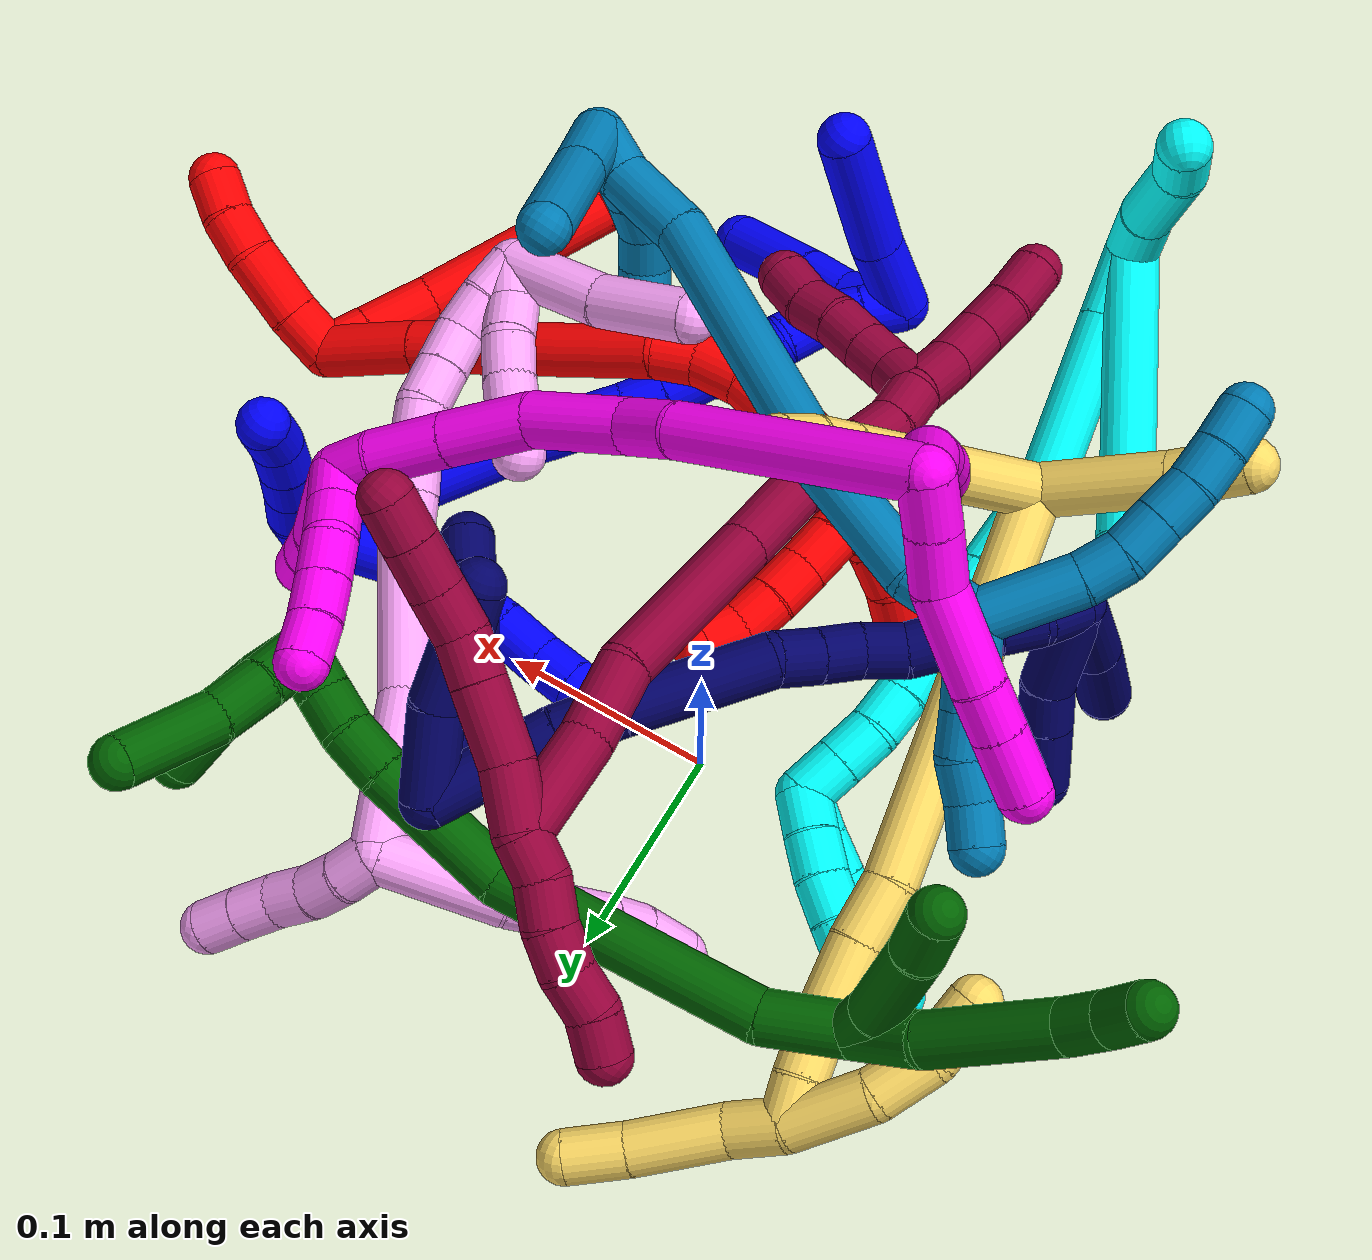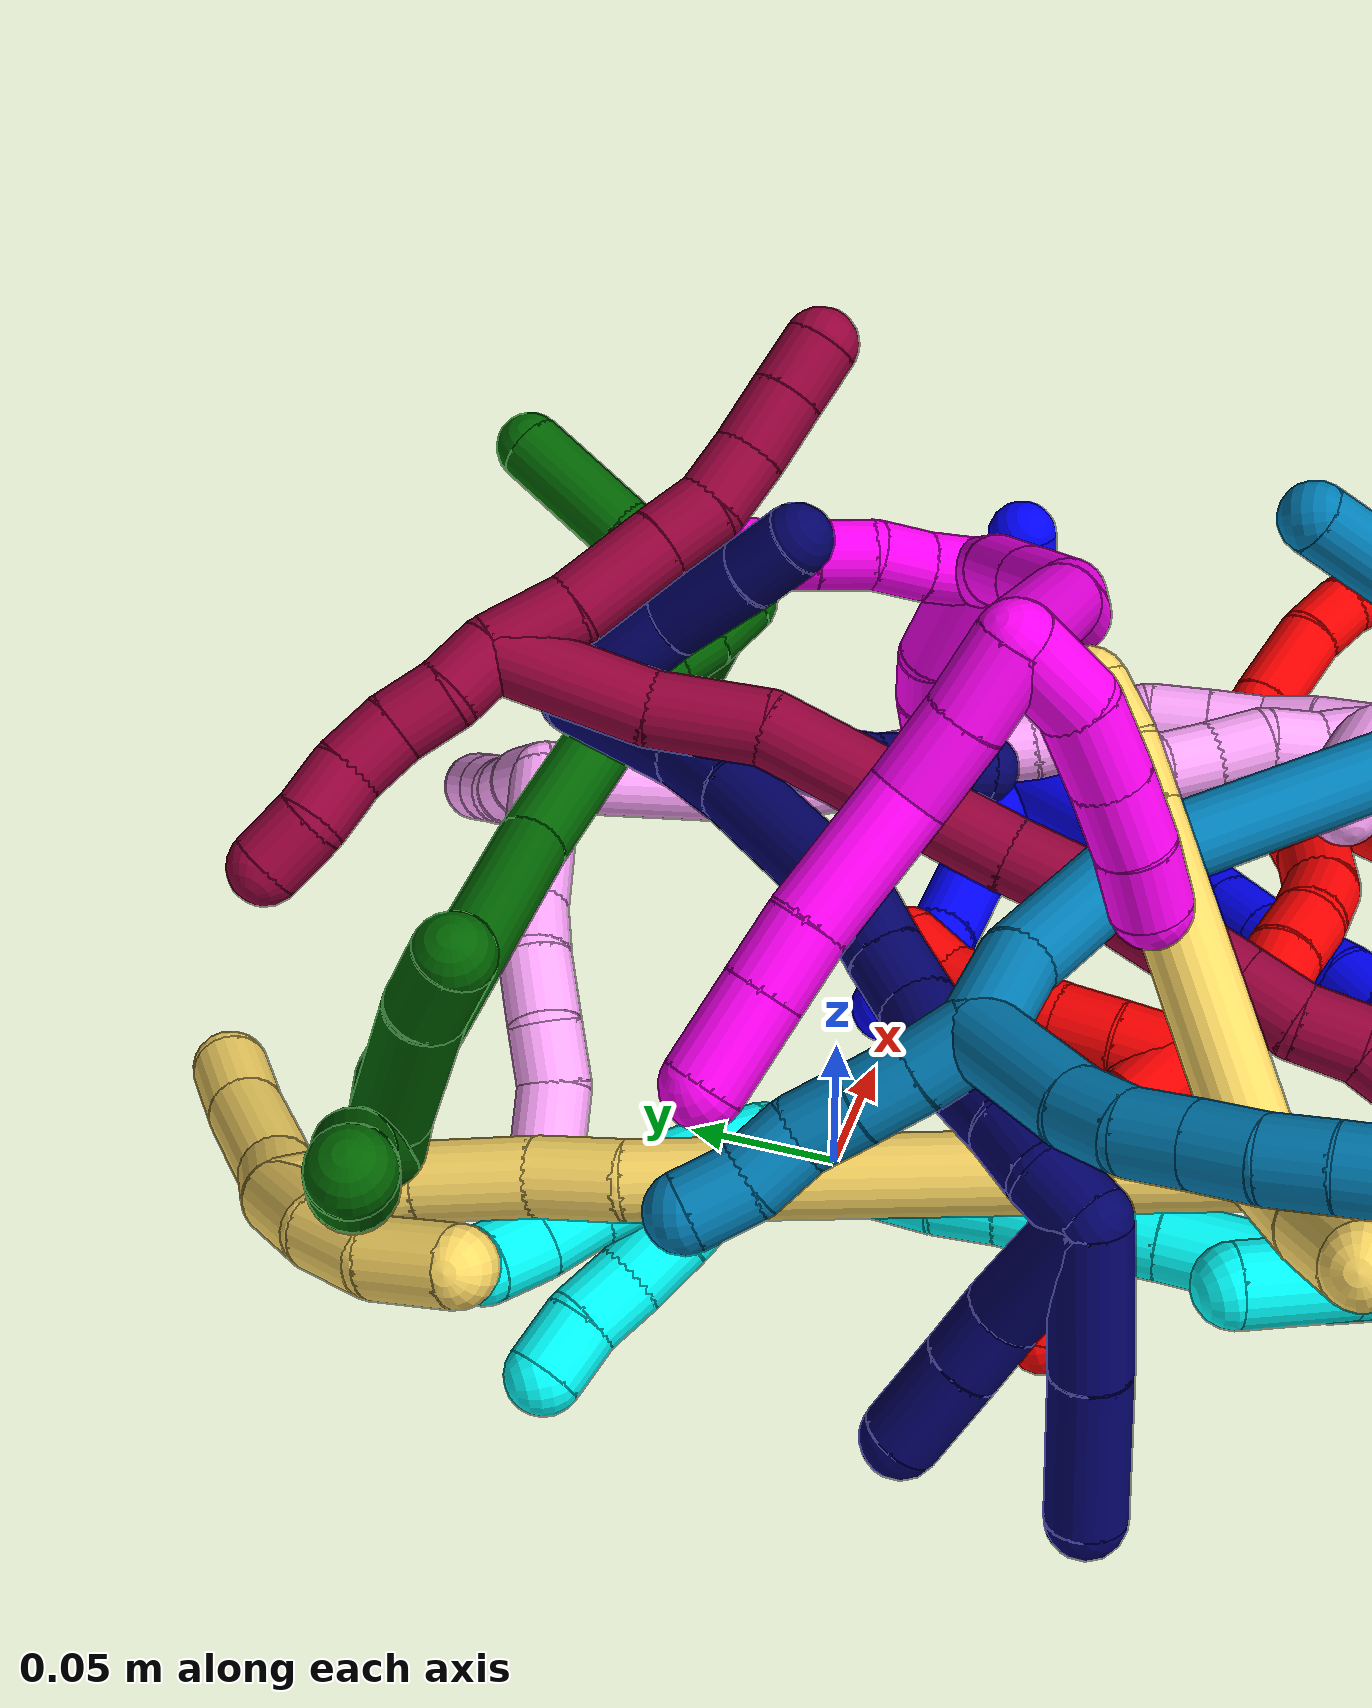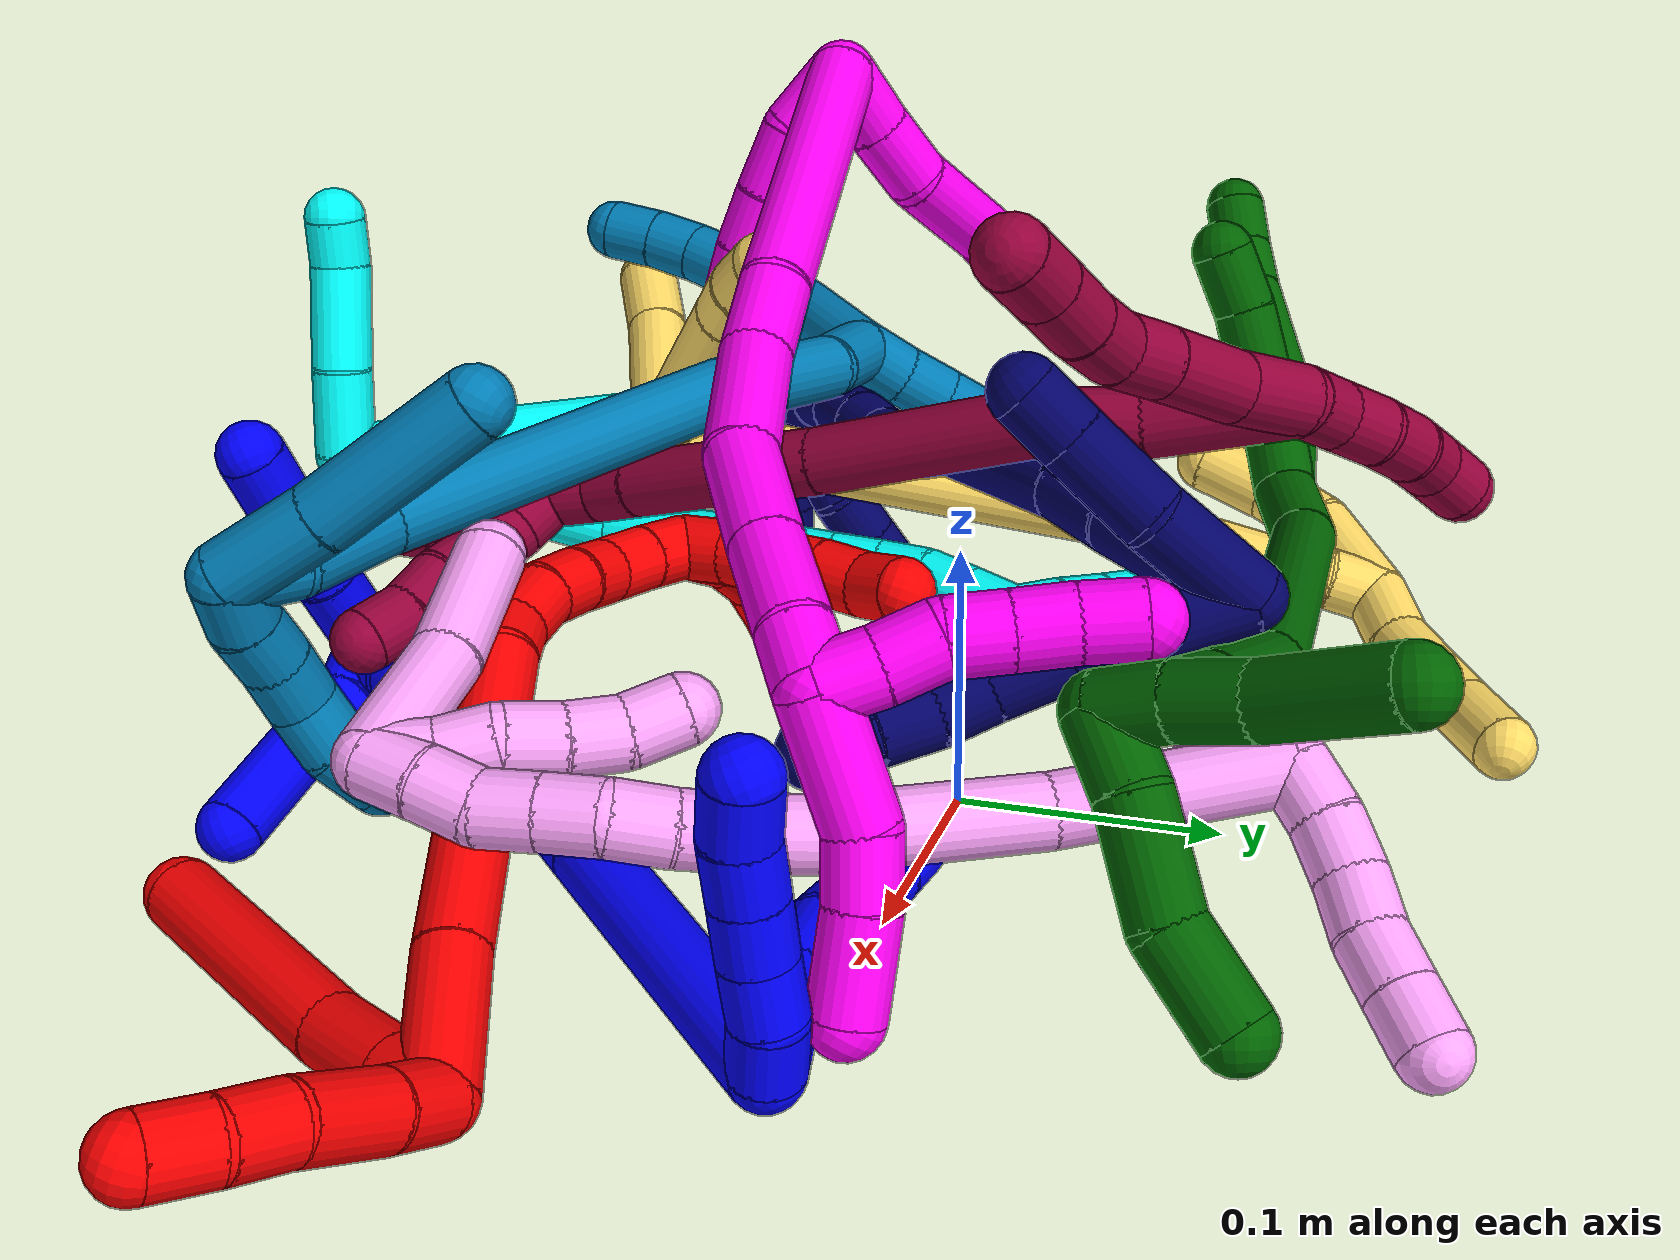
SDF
<sdf version="1.7">
 <world name="default">
  <plugin name="TubeGeneratorPlugin" filename="libtube_generator_plugin.so"/>
  <model name="photoneo_s_sensor">
   <static>1</static>
   <pose>0 0 2 1.57079 1.57079 3.14159</pose>
   <link name="link">
    <inertial><mass>0.1</mass></inertial>
    <sensor name="sensor" type="depth">
     <update_rate>30</update_rate>
     <camera>
      <horizontal_fov>1.22</horizontal_fov>
      <image><width>1920</width><height>1200</height><format>B8G8R8</format></image>
      <clip><near>0.1</near><far>4</far></clip>
      <depth_camera><output>points</output></depth_camera>
     </camera>
     <plugin name="camera_plugin" filename="libgazebo_ros_depth_camera.so">
      <baseline>0.2</baseline>
      <alwaysOn>1</alwaysOn>
      <updateRate>0.0</updateRate>
      <cameraName>camera_ir</cameraName>
      <imageTopicName>/camera/color/image_raw</imageTopicName>
      <cameraInfoTopicName>/camera/color/camera_info</cameraInfoTopicName>
      <depthImageTopicName>/camera/depth/image_raw</depthImageTopicName>
      <depthImageCameraInfoTopicName>/camera/depth/camera_info</depthImageCameraInfoTopicName>
      <pointCloudTopicName>/camera/depth/points</pointCloudTopicName>
      <frameName>fr_optical</frameName>
      <pointCloudCutoff>0.1</pointCloudCutoff>
      <pointCloudCutoffMax>2.0</pointCloudCutoffMax>
      <distortionK1>0</distortionK1>
      <distortionK2>0</distortionK2>
      <distortionK3>0</distortionK3>
      <distortionT1>0</distortionT1>
      <distortionT2>0</distortionT2>
      <CxPrime>0</CxPrime>
      <Cx>0</Cx>
      <Cy>0</Cy>
      <focalLength>0</focalLength>
      <hackBaseline>0</hackBaseline>
     </plugin>
    </sensor>
   </link>
  </model>
  <gravity>0 0 -9.8</gravity>
  <magnetic_field>6e-06 2.3e-05 -4.2e-05</magnetic_field>
  <atmosphere type="adiabatic"/>
  <physics name="default_physics" default="0" type="ode">
   <max_step_size>0.003</max_step_size>
   <real_time_factor>1</real_time_factor>
   <real_time_update_rate>1000</real_time_update_rate>
   <max_contacts>10000</max_contacts>
   <ode>
    <solver>
     <type>quick</type>
     <iters>100</iters>
     <sor>1.3</sor>
     <use_dynamic_moi_rescaling>0</use_dynamic_moi_rescaling>
    </solver>
    <constraints>
     <contact_max_correcting_vel>0</contact_max_correcting_vel>
     <contact_surface_layer>0.001</contact_surface_layer>
     <cfm>0</cfm>
     <erp>0.2</erp>
    </constraints>
   </ode>
  </physics>
  <scene><ambient>0.4 0.4 0.4 1</ambient><background>0.7 0.7 0.7 1</background><shadows>0</shadows></scene>
  <audio><device>default</device></audio>
  <spherical_coordinates>
   <surface_model>EARTH_WGS84</surface_model>
   <latitude_deg>0</latitude_deg>
   <longitude_deg>0</longitude_deg>
   <elevation>0</elevation>
   <heading_deg>0</heading_deg>
  </spherical_coordinates>
  <model name="bin">
   <static>1</static>
   <link name="bottom">
    <collision name="collision-bottom">
     <pose>0 0 -0.01 0 -0 0</pose>
     <geometry><box><size>0.8 0.6 0.02</size></box></geometry>
     <surface>
      <friction><ode><mu>100</mu><mu2>100</mu2></ode></friction>
      <contact><collide_bitmask>65535</collide_bitmask></contact>
     </surface>
    </collision>
   </link>
   <link name="west_wall">
    <collision name="collision-west_wall">
     <pose>-0.41 0 0.1 0 -0 0</pose>
     <geometry><box><size>0.02 0.6 0.2</size></box></geometry>
     <surface>
      <friction><ode><mu>100</mu><mu2>100</mu2></ode></friction>
      <contact><collide_bitmask>65535</collide_bitmask></contact>
     </surface>
    </collision>
   </link>
   <link name="east_wall">
    <collision name="collision-east_wall">
     <pose>0.41 0 0.1 0 -0 0</pose>
     <geometry><box><size>0.02 0.6 0.2</size></box></geometry>
     <surface>
      <friction><ode><mu>100</mu><mu2>100</mu2></ode></friction>
      <contact><collide_bitmask>65535</collide_bitmask></contact>
     </surface>
    </collision>
   </link>
   <link name="south_wall">
    <collision name="collision-south_wall">
     <pose>0 -0.31 0.1 0 -0 0</pose>
     <geometry><box><size>0.8 0.02 0.2</size></box></geometry>
     <surface>
      <friction><ode><mu>100</mu><mu2>100</mu2></ode></friction>
      <contact><collide_bitmask>65535</collide_bitmask></contact>
     </surface>
    </collision>
   </link>
   <link name="north_wall">
    <collision name="collision-north_wall">
     <pose>0 0.31 0.1 0 -0 0</pose>
     <geometry><box><size>0.8 0.02 0.2</size></box></geometry>
     <surface>
      <friction><ode><mu>100</mu><mu2>100</mu2></ode></friction>
      <contact><collide_bitmask>65535</collide_bitmask></contact>
     </surface>
    </collision>
   </link>
  </model>
  <model name="1">
   <static>0</static>
   <link name="1">
    <collision name="collision-cylinder-e_1_2_8">
     <pose>-0.021466 -0.006007 0.009417 0.56782 -1.09099 -0.350559</pose>
     <geometry><cylinder><radius>0.0125</radius><length>0.048396</length></cylinder></geometry>
     <surface>
      <friction><ode><mu>1.16</mu><mu2>1.16</mu2><slip1>0</slip1><slip2>0</slip2></ode></friction>
      <contact><ode><kp>1e+06</kp><kd>1</kd><max_vel>0</max_vel><min_depth>0.001</min_depth></ode></contact>
     </surface>
    </collision>
    <visual name="visual-cylinder-e_1_2_8">
     <pose>-0.021466 -0.006007 0.009417 0.56782 -1.09099 -0.350559</pose>
     <geometry><cylinder><radius>0.0125</radius><length>0.048396</length></cylinder></geometry>
     <material><ambient>0 0 1 1</ambient></material>
    </visual>
    <collision name="collision-cylinder-e_2_8_9">
     <pose>-0.056591 -0.012776 0.022798 0.189879 -1.28347 -0.142074</pose>
     <geometry><cylinder><radius>0.0125</radius><length>0.028487</length></cylinder></geometry>
     <surface>
      <friction><ode><mu>1.16</mu><mu2>1.16</mu2><slip1>0</slip1><slip2>0</slip2></ode></friction>
      <contact><ode><kp>1e+06</kp><kd>1</kd><max_vel>0</max_vel><min_depth>0.001</min_depth></ode></contact>
     </surface>
    </collision>
    <visual name="visual-cylinder-e_2_8_9">
     <pose>-0.056591 -0.012776 0.022798 0.189879 -1.28347 -0.142074</pose>
     <geometry><cylinder><radius>0.0125</radius><length>0.028487</length></cylinder></geometry>
     <material><ambient>0 0 1 1</ambient></material>
    </visual>
    <collision name="collision-cylinder-e_3_9_10">
     <pose>-0.084316 -0.015399 0.028239 0.899792 -1.40343 -0.775082</pose>
     <geometry><cylinder><radius>0.0125</radius><length>0.02853</length></cylinder></geometry>
     <surface>
      <friction><ode><mu>1.16</mu><mu2>1.16</mu2><slip1>0</slip1><slip2>0</slip2></ode></friction>
      <contact><ode><kp>1e+06</kp><kd>1</kd><max_vel>0</max_vel><min_depth>0.001</min_depth></ode></contact>
     </surface>
    </collision>
    <visual name="visual-cylinder-e_3_9_10">
     <pose>-0.084316 -0.015399 0.028239 0.899792 -1.40343 -0.775082</pose>
     <geometry><cylinder><radius>0.0125</radius><length>0.02853</length></cylinder></geometry>
     <material><ambient>0 0 1 1</ambient></material>
    </visual>
    <collision name="collision-cylinder-e_4_10_11">
     <pose>-0.110575 -0.017236 0.030953 -0.019648 -1.46971 0.017756</pose>
     <geometry><cylinder><radius>0.0125</radius><length>0.02451</length></cylinder></geometry>
     <surface>
      <friction><ode><mu>1.16</mu><mu2>1.16</mu2><slip1>0</slip1><slip2>0</slip2></ode></friction>
      <contact><ode><kp>1e+06</kp><kd>1</kd><max_vel>0</max_vel><min_depth>0.001</min_depth></ode></contact>
     </surface>
    </collision>
    <visual name="visual-cylinder-e_4_10_11">
     <pose>-0.110575 -0.017236 0.030953 -0.019648 -1.46971 0.017756</pose>
     <geometry><cylinder><radius>0.0125</radius><length>0.02451</length></cylinder></geometry>
     <material><ambient>0 0 1 1</ambient></material>
    </visual>
    <collision name="collision-cylinder-e_5_11_6">
     <pose>-0.13255 -0.016676 0.034374 -0.240277 -1.34488 0.191654</pose>
     <geometry><cylinder><radius>0.0125</radius><length>0.020077</length></cylinder></geometry>
     <surface>
      <friction><ode><mu>1.16</mu><mu2>1.16</mu2><slip1>0</slip1><slip2>0</slip2></ode></friction>
      <contact><ode><kp>1e+06</kp><kd>1</kd><max_vel>0</max_vel><min_depth>0.001</min_depth></ode></contact>
     </surface>
    </collision>
    <visual name="visual-cylinder-e_5_11_6">
     <pose>-0.13255 -0.016676 0.034374 -0.240277 -1.34488 0.191654</pose>
     <geometry><cylinder><radius>0.0125</radius><length>0.020077</length></cylinder></geometry>
     <material><ambient>0 0 1 1</ambient></material>
    </visual>
    <collision name="collision-cylinder-e_1_2_12">
     <pose>0.002672 0.006431 0.007177 -0.730622 0.270502 -0.104003</pose>
     <geometry><cylinder><radius>0.0125</radius><length>0.02</length></cylinder></geometry>
     <surface>
      <friction><ode><mu>1.16</mu><mu2>1.16</mu2><slip1>0</slip1><slip2>0</slip2></ode></friction>
      <contact><ode><kp>1e+06</kp><kd>1</kd><max_vel>0</max_vel><min_depth>0.001</min_depth></ode></contact>
     </surface>
    </collision>
    <visual name="visual-cylinder-e_1_2_12">
     <pose>0.002672 0.006431 0.007177 -0.730622 0.270502 -0.104003</pose>
     <geometry><cylinder><radius>0.0125</radius><length>0.02</length></cylinder></geometry>
     <material><ambient>0 0 1 1</ambient></material>
    </visual>
    <collision name="collision-cylinder-e_2_12_13">
     <pose>0.007616 0.017197 0.023074 -0.46135 0.229126 -0.054035</pose>
     <geometry><cylinder><radius>0.0125</radius><length>0.02</length></cylinder></geometry>
     <surface>
      <friction><ode><mu>1.16</mu><mu2>1.16</mu2><slip1>0</slip1><slip2>0</slip2></ode></friction>
      <contact><ode><kp>1e+06</kp><kd>1</kd><max_vel>0</max_vel><min_depth>0.001</min_depth></ode></contact>
     </surface>
    </collision>
    <visual name="visual-cylinder-e_2_12_13">
     <pose>0.007616 0.017197 0.023074 -0.46135 0.229126 -0.054035</pose>
     <geometry><cylinder><radius>0.0125</radius><length>0.02</length></cylinder></geometry>
     <material><ambient>0 0 1 1</ambient></material>
    </visual>
    <collision name="collision-cylinder-e_3_13_14">
     <pose>0.012378 0.026296 0.040226 -0.514346 0.251722 -0.066529</pose>
     <geometry><cylinder><radius>0.0125</radius><length>0.02</length></cylinder></geometry>
     <surface>
      <friction><ode><mu>1.16</mu><mu2>1.16</mu2><slip1>0</slip1><slip2>0</slip2></ode></friction>
      <contact><ode><kp>1e+06</kp><kd>1</kd><max_vel>0</max_vel><min_depth>0.001</min_depth></ode></contact>
     </surface>
    </collision>
    <visual name="visual-cylinder-e_3_13_14">
     <pose>0.012378 0.026296 0.040226 -0.514346 0.251722 -0.066529</pose>
     <geometry><cylinder><radius>0.0125</radius><length>0.02</length></cylinder></geometry>
     <material><ambient>0 0 1 1</ambient></material>
    </visual>
    <collision name="collision-cylinder-e_4_14_15">
     <pose>0.017904 0.036045 0.056779 -0.550418 0.308422 -0.087731</pose>
     <geometry><cylinder><radius>0.0125</radius><length>0.02</length></cylinder></geometry>
     <surface>
      <friction><ode><mu>1.16</mu><mu2>1.16</mu2><slip1>0</slip1><slip2>0</slip2></ode></friction>
      <contact><ode><kp>1e+06</kp><kd>1</kd><max_vel>0</max_vel><min_depth>0.001</min_depth></ode></contact>
     </surface>
    </collision>
    <visual name="visual-cylinder-e_4_14_15">
     <pose>0.017904 0.036045 0.056779 -0.550418 0.308422 -0.087731</pose>
     <geometry><cylinder><radius>0.0125</radius><length>0.02</length></cylinder></geometry>
     <material><ambient>0 0 1 1</ambient></material>
    </visual>
    <collision name="collision-cylinder-e_5_15_5">
     <pose>0.02348 0.047504 0.072083 -0.733658 0.256927 -0.099182</pose>
     <geometry><cylinder><radius>0.0125</radius><length>0.02</length></cylinder></geometry>
     <surface>
      <friction><ode><mu>1.16</mu><mu2>1.16</mu2><slip1>0</slip1><slip2>0</slip2></ode></friction>
      <contact><ode><kp>1e+06</kp><kd>1</kd><max_vel>0</max_vel><min_depth>0.001</min_depth></ode></contact>
     </surface>
    </collision>
    <visual name="visual-cylinder-e_5_15_5">
     <pose>0.02348 0.047504 0.072083 -0.733658 0.256927 -0.099182</pose>
     <geometry><cylinder><radius>0.0125</radius><length>0.02</length></cylinder></geometry>
     <material><ambient>0 0 1 1</ambient></material>
    </visual>
    <collision name="collision-cylinder-e_1_2_16">
     <pose>-0.022954 -0.034773 0.039949 0.71623 -0.408953 -0.154911</pose>
     <geometry><cylinder><radius>0.0125</radius><length>0.115446</length></cylinder></geometry>
     <surface>
      <friction><ode><mu>1.16</mu><mu2>1.16</mu2><slip1>0</slip1><slip2>0</slip2></ode></friction>
      <contact><ode><kp>1e+06</kp><kd>1</kd><max_vel>0</max_vel><min_depth>0.001</min_depth></ode></contact>
     </surface>
    </collision>
    <visual name="visual-cylinder-e_1_2_16">
     <pose>-0.022954 -0.034773 0.039949 0.71623 -0.408953 -0.154911</pose>
     <geometry><cylinder><radius>0.0125</radius><length>0.115446</length></cylinder></geometry>
     <material><ambient>0 0 1 1</ambient></material>
    </visual>
    <collision name="collision-cylinder-e_2_16_17">
     <pose>-0.050934 -0.076451 0.086883 0.77974 -0.473073 -0.197451</pose>
     <geometry><cylinder><radius>0.0125</radius><length>0.022067</length></cylinder></geometry>
     <surface>
      <friction><ode><mu>1.16</mu><mu2>1.16</mu2><slip1>0</slip1><slip2>0</slip2></ode></friction>
      <contact><ode><kp>1e+06</kp><kd>1</kd><max_vel>0</max_vel><min_depth>0.001</min_depth></ode></contact>
     </surface>
    </collision>
    <visual name="visual-cylinder-e_2_16_17">
     <pose>-0.050934 -0.076451 0.086883 0.77974 -0.473073 -0.197451</pose>
     <geometry><cylinder><radius>0.0125</radius><length>0.022067</length></cylinder></geometry>
     <material><ambient>0 0 1 1</ambient></material>
    </visual>
    <collision name="collision-cylinder-e_3_17_18">
     <pose>-0.060954 -0.090231 0.10089 0.774721 -0.470045 -0.194758</pose>
     <geometry><cylinder><radius>0.0125</radius><length>0.022045</length></cylinder></geometry>
     <surface>
      <friction><ode><mu>1.16</mu><mu2>1.16</mu2><slip1>0</slip1><slip2>0</slip2></ode></friction>
      <contact><ode><kp>1e+06</kp><kd>1</kd><max_vel>0</max_vel><min_depth>0.001</min_depth></ode></contact>
     </surface>
    </collision>
    <visual name="visual-cylinder-e_3_17_18">
     <pose>-0.060954 -0.090231 0.10089 0.774721 -0.470045 -0.194758</pose>
     <geometry><cylinder><radius>0.0125</radius><length>0.022045</length></cylinder></geometry>
     <material><ambient>0 0 1 1</ambient></material>
    </visual>
    <collision name="collision-cylinder-e_4_18_19">
     <pose>-0.070013 -0.103281 0.114678 0.73983 -0.417859 -0.164062</pose>
     <geometry><cylinder><radius>0.0125</radius><length>0.020045</length></cylinder></geometry>
     <surface>
      <friction><ode><mu>1.16</mu><mu2>1.16</mu2><slip1>0</slip1><slip2>0</slip2></ode></friction>
      <contact><ode><kp>1e+06</kp><kd>1</kd><max_vel>0</max_vel><min_depth>0.001</min_depth></ode></contact>
     </surface>
    </collision>
    <visual name="visual-cylinder-e_4_18_19">
     <pose>-0.070013 -0.103281 0.114678 0.73983 -0.417859 -0.164062</pose>
     <geometry><cylinder><radius>0.0125</radius><length>0.020045</length></cylinder></geometry>
     <material><ambient>0 0 1 1</ambient></material>
    </visual>
    <collision name="collision-cylinder-e_5_19_20">
     <pose>-0.0775 -0.115947 0.12832 0.756542 -0.347027 -0.139088</pose>
     <geometry><cylinder><radius>0.0125</radius><length>0.02011</length></cylinder></geometry>
     <surface>
      <friction><ode><mu>1.16</mu><mu2>1.16</mu2><slip1>0</slip1><slip2>0</slip2></ode></friction>
      <contact><ode><kp>1e+06</kp><kd>1</kd><max_vel>0</max_vel><min_depth>0.001</min_depth></ode></contact>
     </surface>
    </collision>
    <visual name="visual-cylinder-e_5_19_20">
     <pose>-0.0775 -0.115947 0.12832 0.756542 -0.347027 -0.139088</pose>
     <geometry><cylinder><radius>0.0125</radius><length>0.02011</length></cylinder></geometry>
     <material><ambient>0 0 1 1</ambient></material>
    </visual>
    <collision name="collision-cylinder-e_6_20_21">
     <pose>-0.085654 -0.129431 0.140562 0.916374 -0.492813 -0.246832</pose>
     <geometry><cylinder><radius>0.0125</radius><length>0.020012</length></cylinder></geometry>
     <surface>
      <friction><ode><mu>1.16</mu><mu2>1.16</mu2><slip1>0</slip1><slip2>0</slip2></ode></friction>
      <contact><ode><kp>1e+06</kp><kd>1</kd><max_vel>0</max_vel><min_depth>0.001</min_depth></ode></contact>
     </surface>
    </collision>
    <visual name="visual-cylinder-e_6_20_21">
     <pose>-0.085654 -0.129431 0.140562 0.916374 -0.492813 -0.246832</pose>
     <geometry><cylinder><radius>0.0125</radius><length>0.020012</length></cylinder></geometry>
     <material><ambient>0 0 1 1</ambient></material>
    </visual>
    <collision name="collision-cylinder-e_7_21_22">
     <pose>-0.09243 -0.143332 0.152934 0.778245 -0.204657 -0.08416</pose>
     <geometry><cylinder><radius>0.0125</radius><length>0.020095</length></cylinder></geometry>
     <surface>
      <friction><ode><mu>1.16</mu><mu2>1.16</mu2><slip1>0</slip1><slip2>0</slip2></ode></friction>
      <contact><ode><kp>1e+06</kp><kd>1</kd><max_vel>0</max_vel><min_depth>0.001</min_depth></ode></contact>
     </surface>
    </collision>
    <visual name="visual-cylinder-e_7_21_22">
     <pose>-0.09243 -0.143332 0.152934 0.778245 -0.204657 -0.08416</pose>
     <geometry><cylinder><radius>0.0125</radius><length>0.020095</length></cylinder></geometry>
     <material><ambient>0 0 1 1</ambient></material>
    </visual>
    <collision name="collision-cylinder-e_8_22_23">
     <pose>-0.096795 -0.158458 0.165164 1.00467 -0.234184 -0.129058</pose>
     <geometry><cylinder><radius>0.0125</radius><length>0.020026</length></cylinder></geometry>
     <surface>
      <friction><ode><mu>1.16</mu><mu2>1.16</mu2><slip1>0</slip1><slip2>0</slip2></ode></friction>
      <contact><ode><kp>1e+06</kp><kd>1</kd><max_vel>0</max_vel><min_depth>0.001</min_depth></ode></contact>
     </surface>
    </collision>
    <visual name="visual-cylinder-e_8_22_23">
     <pose>-0.096795 -0.158458 0.165164 1.00467 -0.234184 -0.129058</pose>
     <geometry><cylinder><radius>0.0125</radius><length>0.020026</length></cylinder></geometry>
     <material><ambient>0 0 1 1</ambient></material>
    </visual>
    <collision name="collision-cylinder-e_9_23_24">
     <pose>-0.104502 -0.173488 0.175436 0.932839 -0.565814 -0.290658</pose>
     <geometry><cylinder><radius>0.0125</radius><length>0.020084</length></cylinder></geometry>
     <surface>
      <friction><ode><mu>1.16</mu><mu2>1.16</mu2><slip1>0</slip1><slip2>0</slip2></ode></friction>
      <contact><ode><kp>1e+06</kp><kd>1</kd><max_vel>0</max_vel><min_depth>0.001</min_depth></ode></contact>
     </surface>
    </collision>
    <visual name="visual-cylinder-e_9_23_24">
     <pose>-0.104502 -0.173488 0.175436 0.932839 -0.565814 -0.290658</pose>
     <geometry><cylinder><radius>0.0125</radius><length>0.020084</length></cylinder></geometry>
     <material><ambient>0 0 1 1</ambient></material>
    </visual>
    <collision name="collision-cylinder-e_10_24_1">
     <pose>-0.115331 -0.187081 0.185488 0.93524 -0.573571 -0.295677</pose>
     <geometry><cylinder><radius>0.0125</radius><length>0.020069</length></cylinder></geometry>
     <surface>
      <friction><ode><mu>1.16</mu><mu2>1.16</mu2><slip1>0</slip1><slip2>0</slip2></ode></friction>
      <contact><ode><kp>1e+06</kp><kd>1</kd><max_vel>0</max_vel><min_depth>0.001</min_depth></ode></contact>
     </surface>
    </collision>
    <visual name="visual-cylinder-e_10_24_1">
     <pose>-0.115331 -0.187081 0.185488 0.93524 -0.573571 -0.295677</pose>
     <geometry><cylinder><radius>0.0125</radius><length>0.020069</length></cylinder></geometry>
     <material><ambient>0 0 1 1</ambient></material>
    </visual>
    <collision name="collision-cylinder-e_1_1_25">
     <pose>-0.109022 -0.193814 0.181143 -3.13628 0.898867 -3.13058</pose>
     <geometry><cylinder><radius>0.0125</radius><length>0.030038</length></cylinder></geometry>
     <surface>
      <friction><ode><mu>1.16</mu><mu2>1.16</mu2><slip1>0</slip1><slip2>0</slip2></ode></friction>
      <contact><ode><kp>1e+06</kp><kd>1</kd><max_vel>0</max_vel><min_depth>0.001</min_depth></ode></contact>
     </surface>
    </collision>
    <visual name="visual-cylinder-e_1_1_25">
     <pose>-0.109022 -0.193814 0.181143 -3.13628 0.898867 -3.13058</pose>
     <geometry><cylinder><radius>0.0125</radius><length>0.030038</length></cylinder></geometry>
     <material><ambient>0 0 1 1</ambient></material>
    </visual>
    <collision name="collision-cylinder-e_2_25_26">
     <pose>-0.086153 -0.196415 0.166873 2.6475 1.10491 2.36496</pose>
     <geometry><cylinder><radius>0.0125</radius><length>0.024883</length></cylinder></geometry>
     <surface>
      <friction><ode><mu>1.16</mu><mu2>1.16</mu2><slip1>0</slip1><slip2>0</slip2></ode></friction>
      <contact><ode><kp>1e+06</kp><kd>1</kd><max_vel>0</max_vel><min_depth>0.001</min_depth></ode></contact>
     </surface>
    </collision>
    <visual name="visual-cylinder-e_2_25_26">
     <pose>-0.086153 -0.196415 0.166873 2.6475 1.10491 2.36496</pose>
     <geometry><cylinder><radius>0.0125</radius><length>0.024883</length></cylinder></geometry>
     <material><ambient>0 0 1 1</ambient></material>
    </visual>
    <collision name="collision-cylinder-e_3_26_4">
     <pose>-0.055629 -0.204142 0.151676 2.68275 1.03731 2.36485</pose>
     <geometry><cylinder><radius>0.0125</radius><length>0.045079</length></cylinder></geometry>
     <surface>
      <friction><ode><mu>1.16</mu><mu2>1.16</mu2><slip1>0</slip1><slip2>0</slip2></ode></friction>
      <contact><ode><kp>1e+06</kp><kd>1</kd><max_vel>0</max_vel><min_depth>0.001</min_depth></ode></contact>
     </surface>
    </collision>
    <visual name="visual-cylinder-e_3_26_4">
     <pose>-0.055629 -0.204142 0.151676 2.68275 1.03731 2.36485</pose>
     <geometry><cylinder><radius>0.0125</radius><length>0.045079</length></cylinder></geometry>
     <material><ambient>0 0 1 1</ambient></material>
    </visual>
    <collision name="collision-cylinder-e_1_1_27">
     <pose>-0.108728 -0.186198 0.20333 -0.538287 0.678266 -0.193998</pose>
     <geometry><cylinder><radius>0.0125</radius><length>0.038405</length></cylinder></geometry>
     <surface>
      <friction><ode><mu>1.16</mu><mu2>1.16</mu2><slip1>0</slip1><slip2>0</slip2></ode></friction>
      <contact><ode><kp>1e+06</kp><kd>1</kd><max_vel>0</max_vel><min_depth>0.001</min_depth></ode></contact>
     </surface>
    </collision>
    <visual name="visual-cylinder-e_1_1_27">
     <pose>-0.108728 -0.186198 0.20333 -0.538287 0.678266 -0.193998</pose>
     <geometry><cylinder><radius>0.0125</radius><length>0.038405</length></cylinder></geometry>
     <material><ambient>0 0 1 1</ambient></material>
    </visual>
    <collision name="collision-cylinder-e_2_27_3">
     <pose>-0.07912 -0.166688 0.238525 -0.487178 0.606693 -0.155267</pose>
     <geometry><cylinder><radius>0.0125</radius><length>0.061595</length></cylinder></geometry>
     <surface>
      <friction><ode><mu>1.16</mu><mu2>1.16</mu2><slip1>0</slip1><slip2>0</slip2></ode></friction>
      <contact><ode><kp>1e+06</kp><kd>1</kd><max_vel>0</max_vel><min_depth>0.001</min_depth></ode></contact>
     </surface>
    </collision>
    <visual name="visual-cylinder-e_2_27_3">
     <pose>-0.07912 -0.166688 0.238525 -0.487178 0.606693 -0.155267</pose>
     <geometry><cylinder><radius>0.0125</radius><length>0.061595</length></cylinder></geometry>
     <material><ambient>0 0 1 1</ambient></material>
    </visual>
    <collision name="collision-sphere-3">
     <pose>-0.061561 -0.154844 0.260883 0 -0 0</pose>
     <geometry><sphere><radius>0.0125</radius></sphere></geometry>
     <surface>
      <friction><ode><mu>1.16</mu><mu2>1.16</mu2><slip1>0</slip1><slip2>0</slip2></ode></friction>
      <contact><ode><kp>1e+06</kp><kd>1</kd><max_vel>0</max_vel><min_depth>0.001</min_depth></ode></contact>
     </surface>
    </collision>
    <visual name="visual-sphere-3">
     <pose>-0.061561 -0.154844 0.260883 0 -0 0</pose>
     <geometry><sphere><radius>0.0125</radius></sphere></geometry>
     <material><ambient>0 0 1 1</ambient></material>
    </visual>
    <collision name="collision-sphere-27">
     <pose>-0.096679 -0.178533 0.216168 0 -0 0</pose>
     <geometry><sphere><radius>0.0125</radius></sphere></geometry>
     <surface>
      <friction><ode><mu>1.16</mu><mu2>1.16</mu2><slip1>0</slip1><slip2>0</slip2></ode></friction>
      <contact><ode><kp>1e+06</kp><kd>1</kd><max_vel>0</max_vel><min_depth>0.001</min_depth></ode></contact>
     </surface>
    </collision>
    <visual name="visual-sphere-27">
     <pose>-0.096679 -0.178533 0.216168 0 -0 0</pose>
     <geometry><sphere><radius>0.0125</radius></sphere></geometry>
     <material><ambient>0 0 1 1</ambient></material>
    </visual>
    <collision name="collision-sphere-4">
     <pose>-0.036222 -0.209219 0.1414 0 -0 0</pose>
     <geometry><sphere><radius>0.0125</radius></sphere></geometry>
     <surface>
      <friction><ode><mu>1.16</mu><mu2>1.16</mu2><slip1>0</slip1><slip2>0</slip2></ode></friction>
      <contact><ode><kp>1e+06</kp><kd>1</kd><max_vel>0</max_vel><min_depth>0.001</min_depth></ode></contact>
     </surface>
    </collision>
    <visual name="visual-sphere-4">
     <pose>-0.036222 -0.209219 0.1414 0 -0 0</pose>
     <geometry><sphere><radius>0.0125</radius></sphere></geometry>
     <material><ambient>0 0 1 1</ambient></material>
    </visual>
    <collision name="collision-sphere-26">
     <pose>-0.075037 -0.199065 0.161953 0 -0 0</pose>
     <geometry><sphere><radius>0.0125</radius></sphere></geometry>
     <surface>
      <friction><ode><mu>1.16</mu><mu2>1.16</mu2><slip1>0</slip1><slip2>0</slip2></ode></friction>
      <contact><ode><kp>1e+06</kp><kd>1</kd><max_vel>0</max_vel><min_depth>0.001</min_depth></ode></contact>
     </surface>
    </collision>
    <visual name="visual-sphere-26">
     <pose>-0.075037 -0.199065 0.161953 0 -0 0</pose>
     <geometry><sphere><radius>0.0125</radius></sphere></geometry>
     <material><ambient>0 0 1 1</ambient></material>
    </visual>
    <collision name="collision-sphere-25">
     <pose>-0.097268 -0.193765 0.171794 0 -0 0</pose>
     <geometry><sphere><radius>0.0125</radius></sphere></geometry>
     <surface>
      <friction><ode><mu>1.16</mu><mu2>1.16</mu2><slip1>0</slip1><slip2>0</slip2></ode></friction>
      <contact><ode><kp>1e+06</kp><kd>1</kd><max_vel>0</max_vel><min_depth>0.001</min_depth></ode></contact>
     </surface>
    </collision>
    <visual name="visual-sphere-25">
     <pose>-0.097268 -0.193765 0.171794 0 -0 0</pose>
     <geometry><sphere><radius>0.0125</radius></sphere></geometry>
     <material><ambient>0 0 1 1</ambient></material>
    </visual>
    <collision name="collision-sphere-1">
     <pose>-0.120776 -0.193864 0.190492 0 -0 0</pose>
     <geometry><sphere><radius>0.0125</radius></sphere></geometry>
     <surface>
      <friction><ode><mu>1.16</mu><mu2>1.16</mu2><slip1>0</slip1><slip2>0</slip2></ode></friction>
      <contact><ode><kp>1e+06</kp><kd>1</kd><max_vel>0</max_vel><min_depth>0.001</min_depth></ode></contact>
     </surface>
    </collision>
    <visual name="visual-sphere-1">
     <pose>-0.120776 -0.193864 0.190492 0 -0 0</pose>
     <geometry><sphere><radius>0.0125</radius></sphere></geometry>
     <material><ambient>0 0 1 1</ambient></material>
    </visual>
    <collision name="collision-sphere-24">
     <pose>-0.109886 -0.180298 0.180485 0 -0 0</pose>
     <geometry><sphere><radius>0.0125</radius></sphere></geometry>
     <surface>
      <friction><ode><mu>1.16</mu><mu2>1.16</mu2><slip1>0</slip1><slip2>0</slip2></ode></friction>
      <contact><ode><kp>1e+06</kp><kd>1</kd><max_vel>0</max_vel><min_depth>0.001</min_depth></ode></contact>
     </surface>
    </collision>
    <visual name="visual-sphere-24">
     <pose>-0.109886 -0.180298 0.180485 0 -0 0</pose>
     <geometry><sphere><radius>0.0125</radius></sphere></geometry>
     <material><ambient>0 0 1 1</ambient></material>
    </visual>
    <collision name="collision-sphere-23">
     <pose>-0.099119 -0.166678 0.170388 0 -0 0</pose>
     <geometry><sphere><radius>0.0125</radius></sphere></geometry>
     <surface>
      <friction><ode><mu>1.16</mu><mu2>1.16</mu2><slip1>0</slip1><slip2>0</slip2></ode></friction>
      <contact><ode><kp>1e+06</kp><kd>1</kd><max_vel>0</max_vel><min_depth>0.001</min_depth></ode></contact>
     </surface>
    </collision>
    <visual name="visual-sphere-23">
     <pose>-0.099119 -0.166678 0.170388 0 -0 0</pose>
     <geometry><sphere><radius>0.0125</radius></sphere></geometry>
     <material><ambient>0 0 1 1</ambient></material>
    </visual>
    <collision name="collision-sphere-22">
     <pose>-0.094472 -0.150238 0.15994 0 -0 0</pose>
     <geometry><sphere><radius>0.0125</radius></sphere></geometry>
     <surface>
      <friction><ode><mu>1.16</mu><mu2>1.16</mu2><slip1>0</slip1><slip2>0</slip2></ode></friction>
      <contact><ode><kp>1e+06</kp><kd>1</kd><max_vel>0</max_vel><min_depth>0.001</min_depth></ode></contact>
     </surface>
    </collision>
    <visual name="visual-sphere-22">
     <pose>-0.094472 -0.150238 0.15994 0 -0 0</pose>
     <geometry><sphere><radius>0.0125</radius></sphere></geometry>
     <material><ambient>0 0 1 1</ambient></material>
    </visual>
    <collision name="collision-sphere-21">
     <pose>-0.090388 -0.136425 0.145928 0 -0 0</pose>
     <geometry><sphere><radius>0.0125</radius></sphere></geometry>
     <surface>
      <friction><ode><mu>1.16</mu><mu2>1.16</mu2><slip1>0</slip1><slip2>0</slip2></ode></friction>
      <contact><ode><kp>1e+06</kp><kd>1</kd><max_vel>0</max_vel><min_depth>0.001</min_depth></ode></contact>
     </surface>
    </collision>
    <visual name="visual-sphere-21">
     <pose>-0.090388 -0.136425 0.145928 0 -0 0</pose>
     <geometry><sphere><radius>0.0125</radius></sphere></geometry>
     <material><ambient>0 0 1 1</ambient></material>
    </visual>
    <collision name="collision-sphere-6">
     <pose>-0.142334 -0.016141 0.036558 0 -0 0</pose>
     <geometry><sphere><radius>0.0125</radius></sphere></geometry>
     <surface>
      <friction><ode><mu>1.16</mu><mu2>1.16</mu2><slip1>0</slip1><slip2>0</slip2></ode></friction>
      <contact><ode><kp>1e+06</kp><kd>1</kd><max_vel>0</max_vel><min_depth>0.001</min_depth></ode></contact>
     </surface>
    </collision>
    <visual name="visual-sphere-6">
     <pose>-0.142334 -0.016141 0.036558 0 -0 0</pose>
     <geometry><sphere><radius>0.0125</radius></sphere></geometry>
     <material><ambient>0 0 1 1</ambient></material>
    </visual>
    <collision name="collision-sphere-11">
     <pose>-0.122767 -0.017212 0.03219 0 -0 0</pose>
     <geometry><sphere><radius>0.0125</radius></sphere></geometry>
     <surface>
      <friction><ode><mu>1.16</mu><mu2>1.16</mu2><slip1>0</slip1><slip2>0</slip2></ode></friction>
      <contact><ode><kp>1e+06</kp><kd>1</kd><max_vel>0</max_vel><min_depth>0.001</min_depth></ode></contact>
     </surface>
    </collision>
    <visual name="visual-sphere-11">
     <pose>-0.122767 -0.017212 0.03219 0 -0 0</pose>
     <geometry><sphere><radius>0.0125</radius></sphere></geometry>
     <material><ambient>0 0 1 1</ambient></material>
    </visual>
    <collision name="collision-sphere-10">
     <pose>-0.098382 -0.01726 0.029717 0 -0 0</pose>
     <geometry><sphere><radius>0.0125</radius></sphere></geometry>
     <surface>
      <friction><ode><mu>1.16</mu><mu2>1.16</mu2><slip1>0</slip1><slip2>0</slip2></ode></friction>
      <contact><ode><kp>1e+06</kp><kd>1</kd><max_vel>0</max_vel><min_depth>0.001</min_depth></ode></contact>
     </surface>
    </collision>
    <visual name="visual-sphere-10">
     <pose>-0.098382 -0.01726 0.029717 0 -0 0</pose>
     <geometry><sphere><radius>0.0125</radius></sphere></geometry>
     <material><ambient>0 0 1 1</ambient></material>
    </visual>
    <collision name="collision-sphere-9">
     <pose>-0.070251 -0.013538 0.026762 0 -0 0</pose>
     <geometry><sphere><radius>0.0125</radius></sphere></geometry>
     <surface>
      <friction><ode><mu>1.16</mu><mu2>1.16</mu2><slip1>0</slip1><slip2>0</slip2></ode></friction>
      <contact><ode><kp>1e+06</kp><kd>1</kd><max_vel>0</max_vel><min_depth>0.001</min_depth></ode></contact>
     </surface>
    </collision>
    <visual name="visual-sphere-9">
     <pose>-0.070251 -0.013538 0.026762 0 -0 0</pose>
     <geometry><sphere><radius>0.0125</radius></sphere></geometry>
     <material><ambient>0 0 1 1</ambient></material>
    </visual>
    <collision name="collision-sphere-2">
     <geometry><sphere><radius>0.0125</radius></sphere></geometry>
     <surface>
      <friction><ode><mu>1.16</mu><mu2>1.16</mu2><slip1>0</slip1><slip2>0</slip2></ode></friction>
      <contact><ode><kp>1e+06</kp><kd>1</kd><max_vel>0</max_vel><min_depth>0.001</min_depth></ode></contact>
     </surface>
    </collision>
    <visual name="visual-sphere-2">
     <geometry><sphere><radius>0.0125</radius></sphere></geometry>
     <material><ambient>0 0 1 1</ambient></material>
    </visual>
    <collision name="collision-sphere-19">
     <pose>-0.074081 -0.109456 0.121443 0 -0 0</pose>
     <geometry><sphere><radius>0.0125</radius></sphere></geometry>
     <surface>
      <friction><ode><mu>1.16</mu><mu2>1.16</mu2><slip1>0</slip1><slip2>0</slip2></ode></friction>
      <contact><ode><kp>1e+06</kp><kd>1</kd><max_vel>0</max_vel><min_depth>0.001</min_depth></ode></contact>
     </surface>
    </collision>
    <visual name="visual-sphere-19">
     <pose>-0.074081 -0.109456 0.121443 0 -0 0</pose>
     <geometry><sphere><radius>0.0125</radius></sphere></geometry>
     <material><ambient>0 0 1 1</ambient></material>
    </visual>
    <collision name="collision-sphere-8">
     <pose>-0.042931 -0.012014 0.018834 0 -0 0</pose>
     <geometry><sphere><radius>0.0125</radius></sphere></geometry>
     <surface>
      <friction><ode><mu>1.16</mu><mu2>1.16</mu2><slip1>0</slip1><slip2>0</slip2></ode></friction>
      <contact><ode><kp>1e+06</kp><kd>1</kd><max_vel>0</max_vel><min_depth>0.001</min_depth></ode></contact>
     </surface>
    </collision>
    <visual name="visual-sphere-8">
     <pose>-0.042931 -0.012014 0.018834 0 -0 0</pose>
     <geometry><sphere><radius>0.0125</radius></sphere></geometry>
     <material><ambient>0 0 1 1</ambient></material>
    </visual>
    <collision name="collision-sphere-12">
     <pose>0.005344 0.012861 0.014354 0 -0 0</pose>
     <geometry><sphere><radius>0.0125</radius></sphere></geometry>
     <surface>
      <friction><ode><mu>1.16</mu><mu2>1.16</mu2><slip1>0</slip1><slip2>0</slip2></ode></friction>
      <contact><ode><kp>1e+06</kp><kd>1</kd><max_vel>0</max_vel><min_depth>0.001</min_depth></ode></contact>
     </surface>
    </collision>
    <visual name="visual-sphere-12">
     <pose>0.005344 0.012861 0.014354 0 -0 0</pose>
     <geometry><sphere><radius>0.0125</radius></sphere></geometry>
     <material><ambient>0 0 1 1</ambient></material>
    </visual>
    <collision name="collision-sphere-13">
     <pose>0.009887 0.021532 0.031795 0 -0 0</pose>
     <geometry><sphere><radius>0.0125</radius></sphere></geometry>
     <surface>
      <friction><ode><mu>1.16</mu><mu2>1.16</mu2><slip1>0</slip1><slip2>0</slip2></ode></friction>
      <contact><ode><kp>1e+06</kp><kd>1</kd><max_vel>0</max_vel><min_depth>0.001</min_depth></ode></contact>
     </surface>
    </collision>
    <visual name="visual-sphere-13">
     <pose>0.009887 0.021532 0.031795 0 -0 0</pose>
     <geometry><sphere><radius>0.0125</radius></sphere></geometry>
     <material><ambient>0 0 1 1</ambient></material>
    </visual>
    <collision name="collision-sphere-14">
     <pose>0.014868 0.031061 0.048658 0 -0 0</pose>
     <geometry><sphere><radius>0.0125</radius></sphere></geometry>
     <surface>
      <friction><ode><mu>1.16</mu><mu2>1.16</mu2><slip1>0</slip1><slip2>0</slip2></ode></friction>
      <contact><ode><kp>1e+06</kp><kd>1</kd><max_vel>0</max_vel><min_depth>0.001</min_depth></ode></contact>
     </surface>
    </collision>
    <visual name="visual-sphere-14">
     <pose>0.014868 0.031061 0.048658 0 -0 0</pose>
     <geometry><sphere><radius>0.0125</radius></sphere></geometry>
     <material><ambient>0 0 1 1</ambient></material>
    </visual>
    <collision name="collision-sphere-15">
     <pose>0.020939 0.041028 0.0649 0 -0 0</pose>
     <geometry><sphere><radius>0.0125</radius></sphere></geometry>
     <surface>
      <friction><ode><mu>1.16</mu><mu2>1.16</mu2><slip1>0</slip1><slip2>0</slip2></ode></friction>
      <contact><ode><kp>1e+06</kp><kd>1</kd><max_vel>0</max_vel><min_depth>0.001</min_depth></ode></contact>
     </surface>
    </collision>
    <visual name="visual-sphere-15">
     <pose>0.020939 0.041028 0.0649 0 -0 0</pose>
     <geometry><sphere><radius>0.0125</radius></sphere></geometry>
     <material><ambient>0 0 1 1</ambient></material>
    </visual>
    <collision name="collision-sphere-5">
     <pose>0.026022 0.053981 0.079267 0 -0 0</pose>
     <geometry><sphere><radius>0.0125</radius></sphere></geometry>
     <surface>
      <friction><ode><mu>1.16</mu><mu2>1.16</mu2><slip1>0</slip1><slip2>0</slip2></ode></friction>
      <contact><ode><kp>1e+06</kp><kd>1</kd><max_vel>0</max_vel><min_depth>0.001</min_depth></ode></contact>
     </surface>
    </collision>
    <visual name="visual-sphere-5">
     <pose>0.026022 0.053981 0.079267 0 -0 0</pose>
     <geometry><sphere><radius>0.0125</radius></sphere></geometry>
     <material><ambient>0 0 1 1</ambient></material>
    </visual>
    <collision name="collision-sphere-16">
     <pose>-0.045907 -0.069545 0.079899 0 -0 0</pose>
     <geometry><sphere><radius>0.0125</radius></sphere></geometry>
     <surface>
      <friction><ode><mu>1.16</mu><mu2>1.16</mu2><slip1>0</slip1><slip2>0</slip2></ode></friction>
      <contact><ode><kp>1e+06</kp><kd>1</kd><max_vel>0</max_vel><min_depth>0.001</min_depth></ode></contact>
     </surface>
    </collision>
    <visual name="visual-sphere-16">
     <pose>-0.045907 -0.069545 0.079899 0 -0 0</pose>
     <geometry><sphere><radius>0.0125</radius></sphere></geometry>
     <material><ambient>0 0 1 1</ambient></material>
    </visual>
    <collision name="collision-sphere-17">
     <pose>-0.055961 -0.083357 0.093867 0 -0 0</pose>
     <geometry><sphere><radius>0.0125</radius></sphere></geometry>
     <surface>
      <friction><ode><mu>1.16</mu><mu2>1.16</mu2><slip1>0</slip1><slip2>0</slip2></ode></friction>
      <contact><ode><kp>1e+06</kp><kd>1</kd><max_vel>0</max_vel><min_depth>0.001</min_depth></ode></contact>
     </surface>
    </collision>
    <visual name="visual-sphere-17">
     <pose>-0.055961 -0.083357 0.093867 0 -0 0</pose>
     <geometry><sphere><radius>0.0125</radius></sphere></geometry>
     <material><ambient>0 0 1 1</ambient></material>
    </visual>
    <collision name="collision-sphere-18">
     <pose>-0.065946 -0.097105 0.107912 0 -0 0</pose>
     <geometry><sphere><radius>0.0125</radius></sphere></geometry>
     <surface>
      <friction><ode><mu>1.16</mu><mu2>1.16</mu2><slip1>0</slip1><slip2>0</slip2></ode></friction>
      <contact><ode><kp>1e+06</kp><kd>1</kd><max_vel>0</max_vel><min_depth>0.001</min_depth></ode></contact>
     </surface>
    </collision>
    <visual name="visual-sphere-18">
     <pose>-0.065946 -0.097105 0.107912 0 -0 0</pose>
     <geometry><sphere><radius>0.0125</radius></sphere></geometry>
     <material><ambient>0 0 1 1</ambient></material>
    </visual>
    <collision name="collision-sphere-20">
     <pose>-0.08092 -0.122437 0.135196 0 -0 0</pose>
     <geometry><sphere><radius>0.0125</radius></sphere></geometry>
     <surface>
      <friction><ode><mu>1.16</mu><mu2>1.16</mu2><slip1>0</slip1><slip2>0</slip2></ode></friction>
      <contact><ode><kp>1e+06</kp><kd>1</kd><max_vel>0</max_vel><min_depth>0.001</min_depth></ode></contact>
     </surface>
    </collision>
    <visual name="visual-sphere-20">
     <pose>-0.08092 -0.122437 0.135196 0 -0 0</pose>
     <geometry><sphere><radius>0.0125</radius></sphere></geometry>
     <material><ambient>0 0 1 1</ambient></material>
    </visual>
    <inertial>
     <pose>-0.058834 -0.085982 0.101801 0 -0 0</pose>
     <mass>0.75</mass>
     <inertia>
      <ixx>0.000131</ixx>
      <ixy>0</ixy>
      <ixz>0</ixz>
      <iyy>0.000146</iyy>
      <iyz>0</iyz>
      <izz>0.000153</izz>
     </inertia>
    </inertial>
   </link>
   <pose>0.214902 -0.001092 0.012351 0.576863 -0.143406 -0.241671</pose>
  </model>
  <model name="2">
   <static>0</static>
   <link name="2">
    <collision name="collision-cylinder-e_1_2_8">
     <pose>-0.006839 -0.002578 0.007982 0.312435 -0.683984 -0.112017</pose>
     <geometry><cylinder><radius>0.0125</radius><length>0.021646</length></cylinder></geometry>
     <surface>
      <friction><ode><mu>1.16</mu><mu2>1.16</mu2><slip1>0</slip1><slip2>0</slip2></ode></friction>
      <contact><ode><kp>1e+06</kp><kd>1</kd><max_vel>0</max_vel><min_depth>0.001</min_depth></ode></contact>
     </surface>
    </collision>
    <visual name="visual-cylinder-e_1_2_8">
     <pose>-0.006839 -0.002578 0.007982 0.312435 -0.683984 -0.112017</pose>
     <geometry><cylinder><radius>0.0125</radius><length>0.021646</length></cylinder></geometry>
     <material><ambient>1 0 0 1</ambient></material>
    </visual>
    <collision name="collision-cylinder-e_2_8_9">
     <pose>-0.024464 -0.009035 0.028682 0.295975 -0.681559 -0.105631</pose>
     <geometry><cylinder><radius>0.0125</radius><length>0.03424</length></cylinder></geometry>
     <surface>
      <friction><ode><mu>1.16</mu><mu2>1.16</mu2><slip1>0</slip1><slip2>0</slip2></ode></friction>
      <contact><ode><kp>1e+06</kp><kd>1</kd><max_vel>0</max_vel><min_depth>0.001</min_depth></ode></contact>
     </surface>
    </collision>
    <visual name="visual-cylinder-e_2_8_9">
     <pose>-0.024464 -0.009035 0.028682 0.295975 -0.681559 -0.105631</pose>
     <geometry><cylinder><radius>0.0125</radius><length>0.03424</length></cylinder></geometry>
     <material><ambient>1 0 0 1</ambient></material>
    </visual>
    <collision name="collision-cylinder-e_3_9_6">
     <pose>-0.065012 -0.017558 0.077551 0.127809 -0.684753 -0.045607</pose>
     <geometry><cylinder><radius>0.0125</radius><length>0.094114</length></cylinder></geometry>
     <surface>
      <friction><ode><mu>1.16</mu><mu2>1.16</mu2><slip1>0</slip1><slip2>0</slip2></ode></friction>
      <contact><ode><kp>1e+06</kp><kd>1</kd><max_vel>0</max_vel><min_depth>0.001</min_depth></ode></contact>
     </surface>
    </collision>
    <visual name="visual-cylinder-e_3_9_6">
     <pose>-0.065012 -0.017558 0.077551 0.127809 -0.684753 -0.045607</pose>
     <geometry><cylinder><radius>0.0125</radius><length>0.094114</length></cylinder></geometry>
     <material><ambient>1 0 0 1</ambient></material>
    </visual>
    <collision name="collision-cylinder-e_1_2_10">
     <pose>0.010418 0.002038 0.005236 -0.371157 1.07618 -0.223166</pose>
     <geometry><cylinder><radius>0.0125</radius><length>0.023674</length></cylinder></geometry>
     <surface>
      <friction><ode><mu>1.16</mu><mu2>1.16</mu2><slip1>0</slip1><slip2>0</slip2></ode></friction>
      <contact><ode><kp>1e+06</kp><kd>1</kd><max_vel>0</max_vel><min_depth>0.001</min_depth></ode></contact>
     </surface>
    </collision>
    <visual name="visual-cylinder-e_1_2_10">
     <pose>0.010418 0.002038 0.005236 -0.371157 1.07618 -0.223166</pose>
     <geometry><cylinder><radius>0.0125</radius><length>0.023674</length></cylinder></geometry>
     <material><ambient>1 0 0 1</ambient></material>
    </visual>
    <collision name="collision-cylinder-e_2_10_11">
     <pose>0.035016 0.006696 0.019677 -0.277361 0.977096 -0.148105</pose>
     <geometry><cylinder><radius>0.0125</radius><length>0.034213</length></cylinder></geometry>
     <surface>
      <friction><ode><mu>1.16</mu><mu2>1.16</mu2><slip1>0</slip1><slip2>0</slip2></ode></friction>
      <contact><ode><kp>1e+06</kp><kd>1</kd><max_vel>0</max_vel><min_depth>0.001</min_depth></ode></contact>
     </surface>
    </collision>
    <visual name="visual-cylinder-e_2_10_11">
     <pose>0.035016 0.006696 0.019677 -0.277361 0.977096 -0.148105</pose>
     <geometry><cylinder><radius>0.0125</radius><length>0.034213</length></cylinder></geometry>
     <material><ambient>1 0 0 1</ambient></material>
    </visual>
    <collision name="collision-cylinder-e_3_11_12">
     <pose>0.057618 0.008857 0.035452 0.069916 0.907105 0.034091</pose>
     <geometry><cylinder><radius>0.0125</radius><length>0.021386</length></cylinder></geometry>
     <surface>
      <friction><ode><mu>1.16</mu><mu2>1.16</mu2><slip1>0</slip1><slip2>0</slip2></ode></friction>
      <contact><ode><kp>1e+06</kp><kd>1</kd><max_vel>0</max_vel><min_depth>0.001</min_depth></ode></contact>
     </surface>
    </collision>
    <visual name="visual-cylinder-e_3_11_12">
     <pose>0.057618 0.008857 0.035452 0.069916 0.907105 0.034091</pose>
     <geometry><cylinder><radius>0.0125</radius><length>0.021386</length></cylinder></geometry>
     <material><ambient>1 0 0 1</ambient></material>
    </visual>
    <collision name="collision-cylinder-e_4_12_5">
     <pose>0.072849 0.006841 0.049681 0.2004 0.716693 0.07527</pose>
     <geometry><cylinder><radius>0.0125</radius><length>0.020727</length></cylinder></geometry>
     <surface>
      <friction><ode><mu>1.16</mu><mu2>1.16</mu2><slip1>0</slip1><slip2>0</slip2></ode></friction>
      <contact><ode><kp>1e+06</kp><kd>1</kd><max_vel>0</max_vel><min_depth>0.001</min_depth></ode></contact>
     </surface>
    </collision>
    <visual name="visual-cylinder-e_4_12_5">
     <pose>0.072849 0.006841 0.049681 0.2004 0.716693 0.07527</pose>
     <geometry><cylinder><radius>0.0125</radius><length>0.020727</length></cylinder></geometry>
     <material><ambient>1 0 0 1</ambient></material>
    </visual>
    <collision name="collision-cylinder-e_1_2_13">
     <pose>-0.021454 0.010495 0.007704 -0.937551 -1.02538 0.555402</pose>
     <geometry><cylinder><radius>0.0125</radius><length>0.050191</length></cylinder></geometry>
     <surface>
      <friction><ode><mu>1.16</mu><mu2>1.16</mu2><slip1>0</slip1><slip2>0</slip2></ode></friction>
      <contact><ode><kp>1e+06</kp><kd>1</kd><max_vel>0</max_vel><min_depth>0.001</min_depth></ode></contact>
     </surface>
    </collision>
    <visual name="visual-cylinder-e_1_2_13">
     <pose>-0.021454 0.010495 0.007704 -0.937551 -1.02538 0.555402</pose>
     <geometry><cylinder><radius>0.0125</radius><length>0.050191</length></cylinder></geometry>
     <material><ambient>1 0 0 1</ambient></material>
    </visual>
    <collision name="collision-cylinder-e_2_13_14">
     <pose>-0.097964 0.045965 0.031027 -1.01194 -1.0795 0.640992</pose>
     <geometry><cylinder><radius>0.0125</radius><length>0.124881</length></cylinder></geometry>
     <surface>
      <friction><ode><mu>1.16</mu><mu2>1.16</mu2><slip1>0</slip1><slip2>0</slip2></ode></friction>
      <contact><ode><kp>1e+06</kp><kd>1</kd><max_vel>0</max_vel><min_depth>0.001</min_depth></ode></contact>
     </surface>
    </collision>
    <visual name="visual-cylinder-e_2_13_14">
     <pose>-0.097964 0.045965 0.031027 -1.01194 -1.0795 0.640992</pose>
     <geometry><cylinder><radius>0.0125</radius><length>0.124881</length></cylinder></geometry>
     <material><ambient>1 0 0 1</ambient></material>
    </visual>
    <collision name="collision-cylinder-e_3_14_15">
     <pose>-0.163273 0.072605 0.048367 -0.768723 -1.34147 0.621099</pose>
     <geometry><cylinder><radius>0.0125</radius><length>0.021061</length></cylinder></geometry>
     <surface>
      <friction><ode><mu>1.16</mu><mu2>1.16</mu2><slip1>0</slip1><slip2>0</slip2></ode></friction>
      <contact><ode><kp>1e+06</kp><kd>1</kd><max_vel>0</max_vel><min_depth>0.001</min_depth></ode></contact>
     </surface>
    </collision>
    <visual name="visual-cylinder-e_3_14_15">
     <pose>-0.163273 0.072605 0.048367 -0.768723 -1.34147 0.621099</pose>
     <geometry><cylinder><radius>0.0125</radius><length>0.021061</length></cylinder></geometry>
     <material><ambient>1 0 0 1</ambient></material>
    </visual>
    <collision name="collision-cylinder-e_4_15_16">
     <pose>-0.184726 0.077942 0.048805 -1.90688 -1.23645 1.57263</pose>
     <geometry><cylinder><radius>0.0125</radius><length>0.023709</length></cylinder></geometry>
     <surface>
      <friction><ode><mu>1.16</mu><mu2>1.16</mu2><slip1>0</slip1><slip2>0</slip2></ode></friction>
      <contact><ode><kp>1e+06</kp><kd>1</kd><max_vel>0</max_vel><min_depth>0.001</min_depth></ode></contact>
     </surface>
    </collision>
    <visual name="visual-cylinder-e_4_15_16">
     <pose>-0.184726 0.077942 0.048805 -1.90688 -1.23645 1.57263</pose>
     <geometry><cylinder><radius>0.0125</radius><length>0.023709</length></cylinder></geometry>
     <material><ambient>1 0 0 1</ambient></material>
    </visual>
    <collision name="collision-cylinder-e_5_16_17">
     <pose>-0.205148 0.083196 0.043908 -2.72907 -1.16668 2.52755</pose>
     <geometry><cylinder><radius>0.0125</radius><length>0.020063</length></cylinder></geometry>
     <surface>
      <friction><ode><mu>1.16</mu><mu2>1.16</mu2><slip1>0</slip1><slip2>0</slip2></ode></friction>
      <contact><ode><kp>1e+06</kp><kd>1</kd><max_vel>0</max_vel><min_depth>0.001</min_depth></ode></contact>
     </surface>
    </collision>
    <visual name="visual-cylinder-e_5_16_17">
     <pose>-0.205148 0.083196 0.043908 -2.72907 -1.16668 2.52755</pose>
     <geometry><cylinder><radius>0.0125</radius><length>0.020063</length></cylinder></geometry>
     <material><ambient>1 0 0 1</ambient></material>
    </visual>
    <collision name="collision-cylinder-e_6_17_18">
     <pose>-0.223862 0.085079 0.037066 -3.04861 -1.24159 3.01165</pose>
     <geometry><cylinder><radius>0.0125</radius><length>0.02006</length></cylinder></geometry>
     <surface>
      <friction><ode><mu>1.16</mu><mu2>1.16</mu2><slip1>0</slip1><slip2>0</slip2></ode></friction>
      <contact><ode><kp>1e+06</kp><kd>1</kd><max_vel>0</max_vel><min_depth>0.001</min_depth></ode></contact>
     </surface>
    </collision>
    <visual name="visual-cylinder-e_6_17_18">
     <pose>-0.223862 0.085079 0.037066 -3.04861 -1.24159 3.01165</pose>
     <geometry><cylinder><radius>0.0125</radius><length>0.02006</length></cylinder></geometry>
     <material><ambient>1 0 0 1</ambient></material>
    </visual>
    <collision name="collision-cylinder-e_7_18_19">
     <pose>-0.241383 0.087952 0.028453 -2.69593 -0.93164 2.29466</pose>
     <geometry><cylinder><radius>0.0125</radius><length>0.020008</length></cylinder></geometry>
     <surface>
      <friction><ode><mu>1.16</mu><mu2>1.16</mu2><slip1>0</slip1><slip2>0</slip2></ode></friction>
      <contact><ode><kp>1e+06</kp><kd>1</kd><max_vel>0</max_vel><min_depth>0.001</min_depth></ode></contact>
     </surface>
    </collision>
    <visual name="visual-cylinder-e_7_18_19">
     <pose>-0.241383 0.087952 0.028453 -2.69593 -0.93164 2.29466</pose>
     <geometry><cylinder><radius>0.0125</radius><length>0.020008</length></cylinder></geometry>
     <material><ambient>1 0 0 1</ambient></material>
    </visual>
    <collision name="collision-cylinder-e_8_19_1">
     <pose>-0.257302 0.092821 0.017346 -2.75985 -0.907423 2.38706</pose>
     <geometry><cylinder><radius>0.0125</radius><length>0.020028</length></cylinder></geometry>
     <surface>
      <friction><ode><mu>1.16</mu><mu2>1.16</mu2><slip1>0</slip1><slip2>0</slip2></ode></friction>
      <contact><ode><kp>1e+06</kp><kd>1</kd><max_vel>0</max_vel><min_depth>0.001</min_depth></ode></contact>
     </surface>
    </collision>
    <visual name="visual-cylinder-e_8_19_1">
     <pose>-0.257302 0.092821 0.017346 -2.75985 -0.907423 2.38706</pose>
     <geometry><cylinder><radius>0.0125</radius><length>0.020028</length></cylinder></geometry>
     <material><ambient>1 0 0 1</ambient></material>
    </visual>
    <collision name="collision-cylinder-e_1_1_20">
     <pose>-0.271748 0.093944 0.004164 2.98543 -0.714943 -2.72863</pose>
     <geometry><cylinder><radius>0.0125</radius><length>0.02</length></cylinder></geometry>
     <surface>
      <friction><ode><mu>1.16</mu><mu2>1.16</mu2><slip1>0</slip1><slip2>0</slip2></ode></friction>
      <contact><ode><kp>1e+06</kp><kd>1</kd><max_vel>0</max_vel><min_depth>0.001</min_depth></ode></contact>
     </surface>
    </collision>
    <visual name="visual-cylinder-e_1_1_20">
     <pose>-0.271748 0.093944 0.004164 2.98543 -0.714943 -2.72863</pose>
     <geometry><cylinder><radius>0.0125</radius><length>0.02</length></cylinder></geometry>
     <material><ambient>1 0 0 1</ambient></material>
    </visual>
    <collision name="collision-cylinder-e_2_20_21">
     <pose>-0.284829 0.088426 -0.009504 2.53107 -0.710956 -1.73402</pose>
     <geometry><cylinder><radius>0.0125</radius><length>0.02</length></cylinder></geometry>
     <surface>
      <friction><ode><mu>1.16</mu><mu2>1.16</mu2><slip1>0</slip1><slip2>0</slip2></ode></friction>
      <contact><ode><kp>1e+06</kp><kd>1</kd><max_vel>0</max_vel><min_depth>0.001</min_depth></ode></contact>
     </surface>
    </collision>
    <visual name="visual-cylinder-e_2_20_21">
     <pose>-0.284829 0.088426 -0.009504 2.53107 -0.710956 -1.73402</pose>
     <geometry><cylinder><radius>0.0125</radius><length>0.02</length></cylinder></geometry>
     <material><ambient>1 0 0 1</ambient></material>
    </visual>
    <collision name="collision-cylinder-e_3_21_22">
     <pose>-0.295832 0.077401 -0.021656 2.29779 -0.464168 -0.969314</pose>
     <geometry><cylinder><radius>0.0125</radius><length>0.02</length></cylinder></geometry>
     <surface>
      <friction><ode><mu>1.16</mu><mu2>1.16</mu2><slip1>0</slip1><slip2>0</slip2></ode></friction>
      <contact><ode><kp>1e+06</kp><kd>1</kd><max_vel>0</max_vel><min_depth>0.001</min_depth></ode></contact>
     </surface>
    </collision>
    <visual name="visual-cylinder-e_3_21_22">
     <pose>-0.295832 0.077401 -0.021656 2.29779 -0.464168 -0.969314</pose>
     <geometry><cylinder><radius>0.0125</radius><length>0.02</length></cylinder></geometry>
     <material><ambient>1 0 0 1</ambient></material>
    </visual>
    <collision name="collision-cylinder-e_4_22_23">
     <pose>-0.305558 0.063564 -0.032208 2.14311 -0.552673 -0.959112</pose>
     <geometry><cylinder><radius>0.0125</radius><length>0.02</length></cylinder></geometry>
     <surface>
      <friction><ode><mu>1.16</mu><mu2>1.16</mu2><slip1>0</slip1><slip2>0</slip2></ode></friction>
      <contact><ode><kp>1e+06</kp><kd>1</kd><max_vel>0</max_vel><min_depth>0.001</min_depth></ode></contact>
     </surface>
    </collision>
    <visual name="visual-cylinder-e_4_22_23">
     <pose>-0.305558 0.063564 -0.032208 2.14311 -0.552673 -0.959112</pose>
     <geometry><cylinder><radius>0.0125</radius><length>0.02</length></cylinder></geometry>
     <material><ambient>1 0 0 1</ambient></material>
    </visual>
    <collision name="collision-cylinder-e_5_23_4">
     <pose>-0.315988 0.048622 -0.040357 1.9974 -0.544467 -0.818154</pose>
     <geometry><cylinder><radius>0.0125</radius><length>0.02</length></cylinder></geometry>
     <surface>
      <friction><ode><mu>1.16</mu><mu2>1.16</mu2><slip1>0</slip1><slip2>0</slip2></ode></friction>
      <contact><ode><kp>1e+06</kp><kd>1</kd><max_vel>0</max_vel><min_depth>0.001</min_depth></ode></contact>
     </surface>
    </collision>
    <visual name="visual-cylinder-e_5_23_4">
     <pose>-0.315988 0.048622 -0.040357 1.9974 -0.544467 -0.818154</pose>
     <geometry><cylinder><radius>0.0125</radius><length>0.02</length></cylinder></geometry>
     <material><ambient>1 0 0 1</ambient></material>
    </visual>
    <collision name="collision-cylinder-e_1_1_24">
     <pose>-0.262251 0.098247 0.002592 -2.80817 0.298509 -1.45857</pose>
     <geometry><cylinder><radius>0.0125</radius><length>0.02</length></cylinder></geometry>
     <surface>
      <friction><ode><mu>1.16</mu><mu2>1.16</mu2><slip1>0</slip1><slip2>0</slip2></ode></friction>
      <contact><ode><kp>1e+06</kp><kd>1</kd><max_vel>0</max_vel><min_depth>0.001</min_depth></ode></contact>
     </surface>
    </collision>
    <visual name="visual-cylinder-e_1_1_24">
     <pose>-0.262251 0.098247 0.002592 -2.80817 0.298509 -1.45857</pose>
     <geometry><cylinder><radius>0.0125</radius><length>0.02</length></cylinder></geometry>
     <material><ambient>1 0 0 1</ambient></material>
    </visual>
    <collision name="collision-cylinder-e_2_24_25">
     <pose>-0.255752 0.103635 -0.015508 -2.89728 0.363789 -1.96446</pose>
     <geometry><cylinder><radius>0.0125</radius><length>0.02</length></cylinder></geometry>
     <surface>
      <friction><ode><mu>1.16</mu><mu2>1.16</mu2><slip1>0</slip1><slip2>0</slip2></ode></friction>
      <contact><ode><kp>1e+06</kp><kd>1</kd><max_vel>0</max_vel><min_depth>0.001</min_depth></ode></contact>
     </surface>
    </collision>
    <visual name="visual-cylinder-e_2_24_25">
     <pose>-0.255752 0.103635 -0.015508 -2.89728 0.363789 -1.96446</pose>
     <geometry><cylinder><radius>0.0125</radius><length>0.02</length></cylinder></geometry>
     <material><ambient>1 0 0 1</ambient></material>
    </visual>
    <collision name="collision-cylinder-e_3_25_26">
     <pose>-0.248436 0.108442 -0.033486 -2.86322 0.385313 -1.89601</pose>
     <geometry><cylinder><radius>0.0125</radius><length>0.02</length></cylinder></geometry>
     <surface>
      <friction><ode><mu>1.16</mu><mu2>1.16</mu2><slip1>0</slip1><slip2>0</slip2></ode></friction>
      <contact><ode><kp>1e+06</kp><kd>1</kd><max_vel>0</max_vel><min_depth>0.001</min_depth></ode></contact>
     </surface>
    </collision>
    <visual name="visual-cylinder-e_3_25_26">
     <pose>-0.248436 0.108442 -0.033486 -2.86322 0.385313 -1.89601</pose>
     <geometry><cylinder><radius>0.0125</radius><length>0.02</length></cylinder></geometry>
     <material><ambient>1 0 0 1</ambient></material>
    </visual>
    <collision name="collision-cylinder-e_4_26_27">
     <pose>-0.24022 0.112822 -0.051158 -2.93531 0.461932 -2.3123</pose>
     <geometry><cylinder><radius>0.0125</radius><length>0.02</length></cylinder></geometry>
     <surface>
      <friction><ode><mu>1.16</mu><mu2>1.16</mu2><slip1>0</slip1><slip2>0</slip2></ode></friction>
      <contact><ode><kp>1e+06</kp><kd>1</kd><max_vel>0</max_vel><min_depth>0.001</min_depth></ode></contact>
     </surface>
    </collision>
    <visual name="visual-cylinder-e_4_26_27">
     <pose>-0.24022 0.112822 -0.051158 -2.93531 0.461932 -2.3123</pose>
     <geometry><cylinder><radius>0.0125</radius><length>0.02</length></cylinder></geometry>
     <material><ambient>1 0 0 1</ambient></material>
    </visual>
    <collision name="collision-cylinder-e_5_27_3">
     <pose>-0.229161 0.118084 -0.066603 -2.6677 0.721111 -2.00229</pose>
     <geometry><cylinder><radius>0.0125</radius><length>0.02</length></cylinder></geometry>
     <surface>
      <friction><ode><mu>1.16</mu><mu2>1.16</mu2><slip1>0</slip1><slip2>0</slip2></ode></friction>
      <contact><ode><kp>1e+06</kp><kd>1</kd><max_vel>0</max_vel><min_depth>0.001</min_depth></ode></contact>
     </surface>
    </collision>
    <visual name="visual-cylinder-e_5_27_3">
     <pose>-0.229161 0.118084 -0.066603 -2.6677 0.721111 -2.00229</pose>
     <geometry><cylinder><radius>0.0125</radius><length>0.02</length></cylinder></geometry>
     <material><ambient>1 0 0 1</ambient></material>
    </visual>
    <collision name="collision-sphere-3">
     <pose>-0.222559 0.121511 -0.073286 0 -0 0</pose>
     <geometry><sphere><radius>0.0125</radius></sphere></geometry>
     <surface>
      <friction><ode><mu>1.16</mu><mu2>1.16</mu2><slip1>0</slip1><slip2>0</slip2></ode></friction>
      <contact><ode><kp>1e+06</kp><kd>1</kd><max_vel>0</max_vel><min_depth>0.001</min_depth></ode></contact>
     </surface>
    </collision>
    <visual name="visual-sphere-3">
     <pose>-0.222559 0.121511 -0.073286 0 -0 0</pose>
     <geometry><sphere><radius>0.0125</radius></sphere></geometry>
     <material><ambient>1 0 0 1</ambient></material>
    </visual>
    <collision name="collision-sphere-27">
     <pose>-0.235764 0.114656 -0.05992 0 -0 0</pose>
     <geometry><sphere><radius>0.0125</radius></sphere></geometry>
     <surface>
      <friction><ode><mu>1.16</mu><mu2>1.16</mu2><slip1>0</slip1><slip2>0</slip2></ode></friction>
      <contact><ode><kp>1e+06</kp><kd>1</kd><max_vel>0</max_vel><min_depth>0.001</min_depth></ode></contact>
     </surface>
    </collision>
    <visual name="visual-sphere-27">
     <pose>-0.235764 0.114656 -0.05992 0 -0 0</pose>
     <geometry><sphere><radius>0.0125</radius></sphere></geometry>
     <material><ambient>1 0 0 1</ambient></material>
    </visual>
    <collision name="collision-sphere-26">
     <pose>-0.244677 0.110989 -0.042396 0 -0 0</pose>
     <geometry><sphere><radius>0.0125</radius></sphere></geometry>
     <surface>
      <friction><ode><mu>1.16</mu><mu2>1.16</mu2><slip1>0</slip1><slip2>0</slip2></ode></friction>
      <contact><ode><kp>1e+06</kp><kd>1</kd><max_vel>0</max_vel><min_depth>0.001</min_depth></ode></contact>
     </surface>
    </collision>
    <visual name="visual-sphere-26">
     <pose>-0.244677 0.110989 -0.042396 0 -0 0</pose>
     <geometry><sphere><radius>0.0125</radius></sphere></geometry>
     <material><ambient>1 0 0 1</ambient></material>
    </visual>
    <collision name="collision-sphere-25">
     <pose>-0.252194 0.105896 -0.024576 0 -0 0</pose>
     <geometry><sphere><radius>0.0125</radius></sphere></geometry>
     <surface>
      <friction><ode><mu>1.16</mu><mu2>1.16</mu2><slip1>0</slip1><slip2>0</slip2></ode></friction>
      <contact><ode><kp>1e+06</kp><kd>1</kd><max_vel>0</max_vel><min_depth>0.001</min_depth></ode></contact>
     </surface>
    </collision>
    <visual name="visual-sphere-25">
     <pose>-0.252194 0.105896 -0.024576 0 -0 0</pose>
     <geometry><sphere><radius>0.0125</radius></sphere></geometry>
     <material><ambient>1 0 0 1</ambient></material>
    </visual>
    <collision name="collision-sphere-24">
     <pose>-0.25931 0.101375 -0.00644 0 -0 0</pose>
     <geometry><sphere><radius>0.0125</radius></sphere></geometry>
     <surface>
      <friction><ode><mu>1.16</mu><mu2>1.16</mu2><slip1>0</slip1><slip2>0</slip2></ode></friction>
      <contact><ode><kp>1e+06</kp><kd>1</kd><max_vel>0</max_vel><min_depth>0.001</min_depth></ode></contact>
     </surface>
    </collision>
    <visual name="visual-sphere-24">
     <pose>-0.25931 0.101375 -0.00644 0 -0 0</pose>
     <geometry><sphere><radius>0.0125</radius></sphere></geometry>
     <material><ambient>1 0 0 1</ambient></material>
    </visual>
    <collision name="collision-sphere-4">
     <pose>-0.321167 0.040835 -0.043897 0 -0 0</pose>
     <geometry><sphere><radius>0.0125</radius></sphere></geometry>
     <surface>
      <friction><ode><mu>1.16</mu><mu2>1.16</mu2><slip1>0</slip1><slip2>0</slip2></ode></friction>
      <contact><ode><kp>1e+06</kp><kd>1</kd><max_vel>0</max_vel><min_depth>0.001</min_depth></ode></contact>
     </surface>
    </collision>
    <visual name="visual-sphere-4">
     <pose>-0.321167 0.040835 -0.043897 0 -0 0</pose>
     <geometry><sphere><radius>0.0125</radius></sphere></geometry>
     <material><ambient>1 0 0 1</ambient></material>
    </visual>
    <collision name="collision-sphere-23">
     <pose>-0.310808 0.056409 -0.036818 0 -0 0</pose>
     <geometry><sphere><radius>0.0125</radius></sphere></geometry>
     <surface>
      <friction><ode><mu>1.16</mu><mu2>1.16</mu2><slip1>0</slip1><slip2>0</slip2></ode></friction>
      <contact><ode><kp>1e+06</kp><kd>1</kd><max_vel>0</max_vel><min_depth>0.001</min_depth></ode></contact>
     </surface>
    </collision>
    <visual name="visual-sphere-23">
     <pose>-0.310808 0.056409 -0.036818 0 -0 0</pose>
     <geometry><sphere><radius>0.0125</radius></sphere></geometry>
     <material><ambient>1 0 0 1</ambient></material>
    </visual>
    <collision name="collision-sphere-22">
     <pose>-0.300309 0.070719 -0.027599 0 -0 0</pose>
     <geometry><sphere><radius>0.0125</radius></sphere></geometry>
     <surface>
      <friction><ode><mu>1.16</mu><mu2>1.16</mu2><slip1>0</slip1><slip2>0</slip2></ode></friction>
      <contact><ode><kp>1e+06</kp><kd>1</kd><max_vel>0</max_vel><min_depth>0.001</min_depth></ode></contact>
     </surface>
    </collision>
    <visual name="visual-sphere-22">
     <pose>-0.300309 0.070719 -0.027599 0 -0 0</pose>
     <geometry><sphere><radius>0.0125</radius></sphere></geometry>
     <material><ambient>1 0 0 1</ambient></material>
    </visual>
    <collision name="collision-sphere-21">
     <pose>-0.291355 0.084082 -0.015713 0 -0 0</pose>
     <geometry><sphere><radius>0.0125</radius></sphere></geometry>
     <surface>
      <friction><ode><mu>1.16</mu><mu2>1.16</mu2><slip1>0</slip1><slip2>0</slip2></ode></friction>
      <contact><ode><kp>1e+06</kp><kd>1</kd><max_vel>0</max_vel><min_depth>0.001</min_depth></ode></contact>
     </surface>
    </collision>
    <visual name="visual-sphere-21">
     <pose>-0.291355 0.084082 -0.015713 0 -0 0</pose>
     <geometry><sphere><radius>0.0125</radius></sphere></geometry>
     <material><ambient>1 0 0 1</ambient></material>
    </visual>
    <collision name="collision-sphere-20">
     <pose>-0.278304 0.09277 -0.003296 0 -0 0</pose>
     <geometry><sphere><radius>0.0125</radius></sphere></geometry>
     <surface>
      <friction><ode><mu>1.16</mu><mu2>1.16</mu2><slip1>0</slip1><slip2>0</slip2></ode></friction>
      <contact><ode><kp>1e+06</kp><kd>1</kd><max_vel>0</max_vel><min_depth>0.001</min_depth></ode></contact>
     </surface>
    </collision>
    <visual name="visual-sphere-20">
     <pose>-0.278304 0.09277 -0.003296 0 -0 0</pose>
     <geometry><sphere><radius>0.0125</radius></sphere></geometry>
     <material><ambient>1 0 0 1</ambient></material>
    </visual>
    <collision name="collision-sphere-11">
     <pose>0.049195 0.009317 0.028881 0 -0 0</pose>
     <geometry><sphere><radius>0.0125</radius></sphere></geometry>
     <surface>
      <friction><ode><mu>1.16</mu><mu2>1.16</mu2><slip1>0</slip1><slip2>0</slip2></ode></friction>
      <contact><ode><kp>1e+06</kp><kd>1</kd><max_vel>0</max_vel><min_depth>0.001</min_depth></ode></contact>
     </surface>
    </collision>
    <visual name="visual-sphere-11">
     <pose>0.049195 0.009317 0.028881 0 -0 0</pose>
     <geometry><sphere><radius>0.0125</radius></sphere></geometry>
     <material><ambient>1 0 0 1</ambient></material>
    </visual>
    <collision name="collision-sphere-10">
     <pose>0.020836 0.004076 0.010473 0 -0 0</pose>
     <geometry><sphere><radius>0.0125</radius></sphere></geometry>
     <surface>
      <friction><ode><mu>1.16</mu><mu2>1.16</mu2><slip1>0</slip1><slip2>0</slip2></ode></friction>
      <contact><ode><kp>1e+06</kp><kd>1</kd><max_vel>0</max_vel><min_depth>0.001</min_depth></ode></contact>
     </surface>
    </collision>
    <visual name="visual-sphere-10">
     <pose>0.020836 0.004076 0.010473 0 -0 0</pose>
     <geometry><sphere><radius>0.0125</radius></sphere></geometry>
     <material><ambient>1 0 0 1</ambient></material>
    </visual>
    <collision name="collision-sphere-6">
     <pose>-0.094775 -0.022204 0.113703 0 -0 0</pose>
     <geometry><sphere><radius>0.0125</radius></sphere></geometry>
     <surface>
      <friction><ode><mu>1.16</mu><mu2>1.16</mu2><slip1>0</slip1><slip2>0</slip2></ode></friction>
      <contact><ode><kp>1e+06</kp><kd>1</kd><max_vel>0</max_vel><min_depth>0.001</min_depth></ode></contact>
     </surface>
    </collision>
    <visual name="visual-sphere-6">
     <pose>-0.094775 -0.022204 0.113703 0 -0 0</pose>
     <geometry><sphere><radius>0.0125</radius></sphere></geometry>
     <material><ambient>1 0 0 1</ambient></material>
    </visual>
    <collision name="collision-sphere-9">
     <pose>-0.035249 -0.012913 0.041399 0 -0 0</pose>
     <geometry><sphere><radius>0.0125</radius></sphere></geometry>
     <surface>
      <friction><ode><mu>1.16</mu><mu2>1.16</mu2><slip1>0</slip1><slip2>0</slip2></ode></friction>
      <contact><ode><kp>1e+06</kp><kd>1</kd><max_vel>0</max_vel><min_depth>0.001</min_depth></ode></contact>
     </surface>
    </collision>
    <visual name="visual-sphere-9">
     <pose>-0.035249 -0.012913 0.041399 0 -0 0</pose>
     <geometry><sphere><radius>0.0125</radius></sphere></geometry>
     <material><ambient>1 0 0 1</ambient></material>
    </visual>
    <collision name="collision-sphere-2">
     <geometry><sphere><radius>0.0125</radius></sphere></geometry>
     <surface>
      <friction><ode><mu>1.16</mu><mu2>1.16</mu2><slip1>0</slip1><slip2>0</slip2></ode></friction>
      <contact><ode><kp>1e+06</kp><kd>1</kd><max_vel>0</max_vel><min_depth>0.001</min_depth></ode></contact>
     </surface>
    </collision>
    <visual name="visual-sphere-2">
     <geometry><sphere><radius>0.0125</radius></sphere></geometry>
     <material><ambient>1 0 0 1</ambient></material>
    </visual>
    <collision name="collision-sphere-19">
     <pose>-0.249412 0.090524 0.023068 0 -0 0</pose>
     <geometry><sphere><radius>0.0125</radius></sphere></geometry>
     <surface>
      <friction><ode><mu>1.16</mu><mu2>1.16</mu2><slip1>0</slip1><slip2>0</slip2></ode></friction>
      <contact><ode><kp>1e+06</kp><kd>1</kd><max_vel>0</max_vel><min_depth>0.001</min_depth></ode></contact>
     </surface>
    </collision>
    <visual name="visual-sphere-19">
     <pose>-0.249412 0.090524 0.023068 0 -0 0</pose>
     <geometry><sphere><radius>0.0125</radius></sphere></geometry>
     <material><ambient>1 0 0 1</ambient></material>
    </visual>
    <collision name="collision-sphere-8">
     <pose>-0.013678 -0.005157 0.015965 0 -0 0</pose>
     <geometry><sphere><radius>0.0125</radius></sphere></geometry>
     <surface>
      <friction><ode><mu>1.16</mu><mu2>1.16</mu2><slip1>0</slip1><slip2>0</slip2></ode></friction>
      <contact><ode><kp>1e+06</kp><kd>1</kd><max_vel>0</max_vel><min_depth>0.001</min_depth></ode></contact>
     </surface>
    </collision>
    <visual name="visual-sphere-8">
     <pose>-0.013678 -0.005157 0.015965 0 -0 0</pose>
     <geometry><sphere><radius>0.0125</radius></sphere></geometry>
     <material><ambient>1 0 0 1</ambient></material>
    </visual>
    <collision name="collision-sphere-12">
     <pose>0.066041 0.008396 0.042024 0 -0 0</pose>
     <geometry><sphere><radius>0.0125</radius></sphere></geometry>
     <surface>
      <friction><ode><mu>1.16</mu><mu2>1.16</mu2><slip1>0</slip1><slip2>0</slip2></ode></friction>
      <contact><ode><kp>1e+06</kp><kd>1</kd><max_vel>0</max_vel><min_depth>0.001</min_depth></ode></contact>
     </surface>
    </collision>
    <visual name="visual-sphere-12">
     <pose>0.066041 0.008396 0.042024 0 -0 0</pose>
     <geometry><sphere><radius>0.0125</radius></sphere></geometry>
     <material><ambient>1 0 0 1</ambient></material>
    </visual>
    <collision name="collision-sphere-5">
     <pose>0.079657 0.005286 0.057338 0 -0 0</pose>
     <geometry><sphere><radius>0.0125</radius></sphere></geometry>
     <surface>
      <friction><ode><mu>1.16</mu><mu2>1.16</mu2><slip1>0</slip1><slip2>0</slip2></ode></friction>
      <contact><ode><kp>1e+06</kp><kd>1</kd><max_vel>0</max_vel><min_depth>0.001</min_depth></ode></contact>
     </surface>
    </collision>
    <visual name="visual-sphere-5">
     <pose>0.079657 0.005286 0.057338 0 -0 0</pose>
     <geometry><sphere><radius>0.0125</radius></sphere></geometry>
     <material><ambient>1 0 0 1</ambient></material>
    </visual>
    <collision name="collision-sphere-13">
     <pose>-0.042909 0.020989 0.015408 0 -0 0</pose>
     <geometry><sphere><radius>0.0125</radius></sphere></geometry>
     <surface>
      <friction><ode><mu>1.16</mu><mu2>1.16</mu2><slip1>0</slip1><slip2>0</slip2></ode></friction>
      <contact><ode><kp>1e+06</kp><kd>1</kd><max_vel>0</max_vel><min_depth>0.001</min_depth></ode></contact>
     </surface>
    </collision>
    <visual name="visual-sphere-13">
     <pose>-0.042909 0.020989 0.015408 0 -0 0</pose>
     <geometry><sphere><radius>0.0125</radius></sphere></geometry>
     <material><ambient>1 0 0 1</ambient></material>
    </visual>
    <collision name="collision-sphere-14">
     <pose>-0.153019 0.070941 0.046646 0 -0 0</pose>
     <geometry><sphere><radius>0.0125</radius></sphere></geometry>
     <surface>
      <friction><ode><mu>1.16</mu><mu2>1.16</mu2><slip1>0</slip1><slip2>0</slip2></ode></friction>
      <contact><ode><kp>1e+06</kp><kd>1</kd><max_vel>0</max_vel><min_depth>0.001</min_depth></ode></contact>
     </surface>
    </collision>
    <visual name="visual-sphere-14">
     <pose>-0.153019 0.070941 0.046646 0 -0 0</pose>
     <geometry><sphere><radius>0.0125</radius></sphere></geometry>
     <material><ambient>1 0 0 1</ambient></material>
    </visual>
    <collision name="collision-sphere-15">
     <pose>-0.173528 0.07427 0.050088 0 -0 0</pose>
     <geometry><sphere><radius>0.0125</radius></sphere></geometry>
     <surface>
      <friction><ode><mu>1.16</mu><mu2>1.16</mu2><slip1>0</slip1><slip2>0</slip2></ode></friction>
      <contact><ode><kp>1e+06</kp><kd>1</kd><max_vel>0</max_vel><min_depth>0.001</min_depth></ode></contact>
     </surface>
    </collision>
    <visual name="visual-sphere-15">
     <pose>-0.173528 0.07427 0.050088 0 -0 0</pose>
     <geometry><sphere><radius>0.0125</radius></sphere></geometry>
     <material><ambient>1 0 0 1</ambient></material>
    </visual>
    <collision name="collision-sphere-16">
     <pose>-0.195924 0.081615 0.047522 0 -0 0</pose>
     <geometry><sphere><radius>0.0125</radius></sphere></geometry>
     <surface>
      <friction><ode><mu>1.16</mu><mu2>1.16</mu2><slip1>0</slip1><slip2>0</slip2></ode></friction>
      <contact><ode><kp>1e+06</kp><kd>1</kd><max_vel>0</max_vel><min_depth>0.001</min_depth></ode></contact>
     </surface>
    </collision>
    <visual name="visual-sphere-16">
     <pose>-0.195924 0.081615 0.047522 0 -0 0</pose>
     <geometry><sphere><radius>0.0125</radius></sphere></geometry>
     <material><ambient>1 0 0 1</ambient></material>
    </visual>
    <collision name="collision-sphere-17">
     <pose>-0.214371 0.084777 0.040295 0 -0 0</pose>
     <geometry><sphere><radius>0.0125</radius></sphere></geometry>
     <surface>
      <friction><ode><mu>1.16</mu><mu2>1.16</mu2><slip1>0</slip1><slip2>0</slip2></ode></friction>
      <contact><ode><kp>1e+06</kp><kd>1</kd><max_vel>0</max_vel><min_depth>0.001</min_depth></ode></contact>
     </surface>
    </collision>
    <visual name="visual-sphere-17">
     <pose>-0.214371 0.084777 0.040295 0 -0 0</pose>
     <geometry><sphere><radius>0.0125</radius></sphere></geometry>
     <material><ambient>1 0 0 1</ambient></material>
    </visual>
    <collision name="collision-sphere-18">
     <pose>-0.233354 0.08538 0.033837 0 -0 0</pose>
     <geometry><sphere><radius>0.0125</radius></sphere></geometry>
     <surface>
      <friction><ode><mu>1.16</mu><mu2>1.16</mu2><slip1>0</slip1><slip2>0</slip2></ode></friction>
      <contact><ode><kp>1e+06</kp><kd>1</kd><max_vel>0</max_vel><min_depth>0.001</min_depth></ode></contact>
     </surface>
    </collision>
    <visual name="visual-sphere-18">
     <pose>-0.233354 0.08538 0.033837 0 -0 0</pose>
     <geometry><sphere><radius>0.0125</radius></sphere></geometry>
     <material><ambient>1 0 0 1</ambient></material>
    </visual>
    <collision name="collision-sphere-1">
     <pose>-0.265192 0.095119 0.011623 0 -0 0</pose>
     <geometry><sphere><radius>0.0125</radius></sphere></geometry>
     <surface>
      <friction><ode><mu>1.16</mu><mu2>1.16</mu2><slip1>0</slip1><slip2>0</slip2></ode></friction>
      <contact><ode><kp>1e+06</kp><kd>1</kd><max_vel>0</max_vel><min_depth>0.001</min_depth></ode></contact>
     </surface>
    </collision>
    <visual name="visual-sphere-1">
     <pose>-0.265192 0.095119 0.011623 0 -0 0</pose>
     <geometry><sphere><radius>0.0125</radius></sphere></geometry>
     <material><ambient>1 0 0 1</ambient></material>
    </visual>
    <inertial>
     <pose>-0.129108 0.044658 0.019656 0 -0 0</pose>
     <mass>0.75</mass>
     <inertia>
      <ixx>0.000149</ixx>
      <ixy>0</ixy>
      <ixz>0</ixz>
      <iyy>0.000302</iyy>
      <iyz>0</iyz>
      <izz>0.000149</izz>
     </inertia>
    </inertial>
   </link>
   <pose>0.25707 -0.084717 0.013455 1.24888 -0.080326 0.177117</pose>
  </model>
  <model name="3">
   <static>0</static>
   <link name="3">
    <collision name="collision-cylinder-e_1_2_8">
     <pose>-0.012363 0.004339 -0.056637 -3.06513 -0.214303 2.45824</pose>
     <geometry><cylinder><radius>0.0125</radius><length>0.116265</length></cylinder></geometry>
     <surface>
      <friction><ode><mu>1.16</mu><mu2>1.16</mu2><slip1>0</slip1><slip2>0</slip2></ode></friction>
      <contact><ode><kp>1e+06</kp><kd>1</kd><max_vel>0</max_vel><min_depth>0.001</min_depth></ode></contact>
     </surface>
    </collision>
    <visual name="visual-cylinder-e_1_2_8">
     <pose>-0.012363 0.004339 -0.056637 -3.06513 -0.214303 2.45824</pose>
     <geometry><cylinder><radius>0.0125</radius><length>0.116265</length></cylinder></geometry>
     <material><ambient>0.003922 1 0.996078 1</ambient></material>
    </visual>
    <collision name="collision-cylinder-e_2_8_6">
     <pose>-0.027631 0.01086 -0.129745 -3.0099 -0.173122 1.84202</pose>
     <geometry><cylinder><radius>0.0125</radius><length>0.033735</length></cylinder></geometry>
     <surface>
      <friction><ode><mu>1.16</mu><mu2>1.16</mu2><slip1>0</slip1><slip2>0</slip2></ode></friction>
      <contact><ode><kp>1e+06</kp><kd>1</kd><max_vel>0</max_vel><min_depth>0.001</min_depth></ode></contact>
     </surface>
    </collision>
    <visual name="visual-cylinder-e_2_8_6">
     <pose>-0.027631 0.01086 -0.129745 -3.0099 -0.173122 1.84202</pose>
     <geometry><cylinder><radius>0.0125</radius><length>0.033735</length></cylinder></geometry>
     <material><ambient>0.003922 1 0.996078 1</ambient></material>
    </visual>
    <collision name="collision-cylinder-e_1_2_9">
     <pose>-0.015272 -0.009815 0.000719 1.49771 -0.998368 -0.938116</pose>
     <geometry><cylinder><radius>0.0125</radius><length>0.036338</length></cylinder></geometry>
     <surface>
      <friction><ode><mu>1.16</mu><mu2>1.16</mu2><slip1>0</slip1><slip2>0</slip2></ode></friction>
      <contact><ode><kp>1e+06</kp><kd>1</kd><max_vel>0</max_vel><min_depth>0.001</min_depth></ode></contact>
     </surface>
    </collision>
    <visual name="visual-cylinder-e_1_2_9">
     <pose>-0.015272 -0.009815 0.000719 1.49771 -0.998368 -0.938116</pose>
     <geometry><cylinder><radius>0.0125</radius><length>0.036338</length></cylinder></geometry>
     <material><ambient>0.003922 1 0.996078 1</ambient></material>
    </visual>
    <collision name="collision-cylinder-e_2_9_10">
     <pose>-0.047089 -0.033804 0.00138 1.57485 -0.862434 -0.86552</pose>
     <geometry><cylinder><radius>0.0125</radius><length>0.04357</length></cylinder></geometry>
     <surface>
      <friction><ode><mu>1.16</mu><mu2>1.16</mu2><slip1>0</slip1><slip2>0</slip2></ode></friction>
      <contact><ode><kp>1e+06</kp><kd>1</kd><max_vel>0</max_vel><min_depth>0.001</min_depth></ode></contact>
     </surface>
    </collision>
    <visual name="visual-cylinder-e_2_9_10">
     <pose>-0.047089 -0.033804 0.00138 1.57485 -0.862434 -0.86552</pose>
     <geometry><cylinder><radius>0.0125</radius><length>0.04357</length></cylinder></geometry>
     <material><ambient>0.003922 1 0.996078 1</ambient></material>
    </visual>
    <collision name="collision-cylinder-e_3_10_5">
     <pose>-0.072526 -0.05247 0.002607 1.29238 -1.08695 -0.855116</pose>
     <geometry><cylinder><radius>0.0125</radius><length>0.020093</length></cylinder></geometry>
     <surface>
      <friction><ode><mu>1.16</mu><mu2>1.16</mu2><slip1>0</slip1><slip2>0</slip2></ode></friction>
      <contact><ode><kp>1e+06</kp><kd>1</kd><max_vel>0</max_vel><min_depth>0.001</min_depth></ode></contact>
     </surface>
    </collision>
    <visual name="visual-cylinder-e_3_10_5">
     <pose>-0.072526 -0.05247 0.002607 1.29238 -1.08695 -0.855116</pose>
     <geometry><cylinder><radius>0.0125</radius><length>0.020093</length></cylinder></geometry>
     <material><ambient>0.003922 1 0.996078 1</ambient></material>
    </visual>
    <collision name="collision-cylinder-e_1_2_11">
     <pose>-0.001261 0.008279 -0.015711 -2.6566 -0.070871 0.284689</pose>
     <geometry><cylinder><radius>0.0125</radius><length>0.035608</length></cylinder></geometry>
     <surface>
      <friction><ode><mu>1.16</mu><mu2>1.16</mu2><slip1>0</slip1><slip2>0</slip2></ode></friction>
      <contact><ode><kp>1e+06</kp><kd>1</kd><max_vel>0</max_vel><min_depth>0.001</min_depth></ode></contact>
     </surface>
    </collision>
    <visual name="visual-cylinder-e_1_2_11">
     <pose>-0.001261 0.008279 -0.015711 -2.6566 -0.070871 0.284689</pose>
     <geometry><cylinder><radius>0.0125</radius><length>0.035608</length></cylinder></geometry>
     <material><ambient>0.003922 1 0.996078 1</ambient></material>
    </visual>
    <collision name="collision-cylinder-e_2_11_12">
     <pose>-0.005112 0.035639 -0.067488 -2.65498 -0.063401 0.254128</pose>
     <geometry><cylinder><radius>0.0125</radius><length>0.081768</length></cylinder></geometry>
     <surface>
      <friction><ode><mu>1.16</mu><mu2>1.16</mu2><slip1>0</slip1><slip2>0</slip2></ode></friction>
      <contact><ode><kp>1e+06</kp><kd>1</kd><max_vel>0</max_vel><min_depth>0.001</min_depth></ode></contact>
     </surface>
    </collision>
    <visual name="visual-cylinder-e_2_11_12">
     <pose>-0.005112 0.035639 -0.067488 -2.65498 -0.063401 0.254128</pose>
     <geometry><cylinder><radius>0.0125</radius><length>0.081768</length></cylinder></geometry>
     <material><ambient>0.003922 1 0.996078 1</ambient></material>
    </visual>
    <collision name="collision-cylinder-e_3_12_13">
     <pose>-0.016275 0.068397 -0.122696 -2.52119 -0.349407 1.00665</pose>
     <geometry><cylinder><radius>0.0125</radius><length>0.050081</length></cylinder></geometry>
     <surface>
      <friction><ode><mu>1.16</mu><mu2>1.16</mu2><slip1>0</slip1><slip2>0</slip2></ode></friction>
      <contact><ode><kp>1e+06</kp><kd>1</kd><max_vel>0</max_vel><min_depth>0.001</min_depth></ode></contact>
     </surface>
    </collision>
    <visual name="visual-cylinder-e_3_12_13">
     <pose>-0.016275 0.068397 -0.122696 -2.52119 -0.349407 1.00665</pose>
     <geometry><cylinder><radius>0.0125</radius><length>0.050081</length></cylinder></geometry>
     <material><ambient>0.003922 1 0.996078 1</ambient></material>
    </visual>
    <collision name="collision-cylinder-e_4_13_14">
     <pose>-0.032665 0.096115 -0.16101 -2.50949 -0.317854 0.911443</pose>
     <geometry><cylinder><radius>0.0125</radius><length>0.05003</length></cylinder></geometry>
     <surface>
      <friction><ode><mu>1.16</mu><mu2>1.16</mu2><slip1>0</slip1><slip2>0</slip2></ode></friction>
      <contact><ode><kp>1e+06</kp><kd>1</kd><max_vel>0</max_vel><min_depth>0.001</min_depth></ode></contact>
     </surface>
    </collision>
    <visual name="visual-cylinder-e_4_13_14">
     <pose>-0.032665 0.096115 -0.16101 -2.50949 -0.317854 0.911443</pose>
     <geometry><cylinder><radius>0.0125</radius><length>0.05003</length></cylinder></geometry>
     <material><ambient>0.003922 1 0.996078 1</ambient></material>
    </visual>
    <collision name="collision-cylinder-e_5_14_15">
     <pose>-0.043286 0.115294 -0.188294 -2.57694 -0.283953 0.915683</pose>
     <geometry><cylinder><radius>0.0125</radius><length>0.02001</length></cylinder></geometry>
     <surface>
      <friction><ode><mu>1.16</mu><mu2>1.16</mu2><slip1>0</slip1><slip2>0</slip2></ode></friction>
      <contact><ode><kp>1e+06</kp><kd>1</kd><max_vel>0</max_vel><min_depth>0.001</min_depth></ode></contact>
     </surface>
    </collision>
    <visual name="visual-cylinder-e_5_14_15">
     <pose>-0.043286 0.115294 -0.188294 -2.57694 -0.283953 0.915683</pose>
     <geometry><cylinder><radius>0.0125</radius><length>0.02001</length></cylinder></geometry>
     <material><ambient>0.003922 1 0.996078 1</ambient></material>
    </visual>
    <collision name="collision-cylinder-e_6_15_16">
     <pose>-0.049515 0.126472 -0.203871 -2.4613 -0.342808 0.90982</pose>
     <geometry><cylinder><radius>0.0125</radius><length>0.020387</length></cylinder></geometry>
     <surface>
      <friction><ode><mu>1.16</mu><mu2>1.16</mu2><slip1>0</slip1><slip2>0</slip2></ode></friction>
      <contact><ode><kp>1e+06</kp><kd>1</kd><max_vel>0</max_vel><min_depth>0.001</min_depth></ode></contact>
     </surface>
    </collision>
    <visual name="visual-cylinder-e_6_15_16">
     <pose>-0.049515 0.126472 -0.203871 -2.4613 -0.342808 0.90982</pose>
     <geometry><cylinder><radius>0.0125</radius><length>0.020387</length></cylinder></geometry>
     <material><ambient>0.003922 1 0.996078 1</ambient></material>
    </visual>
    <collision name="collision-cylinder-e_7_16_17">
     <pose>-0.055744 0.140411 -0.217403 -2.22581 -0.274288 0.54609</pose>
     <geometry><cylinder><radius>0.0125</radius><length>0.020697</length></cylinder></geometry>
     <surface>
      <friction><ode><mu>1.16</mu><mu2>1.16</mu2><slip1>0</slip1><slip2>0</slip2></ode></friction>
      <contact><ode><kp>1e+06</kp><kd>1</kd><max_vel>0</max_vel><min_depth>0.001</min_depth></ode></contact>
     </surface>
    </collision>
    <visual name="visual-cylinder-e_7_16_17">
     <pose>-0.055744 0.140411 -0.217403 -2.22581 -0.274288 0.54609</pose>
     <geometry><cylinder><radius>0.0125</radius><length>0.020697</length></cylinder></geometry>
     <material><ambient>0.003922 1 0.996078 1</ambient></material>
    </visual>
    <collision name="collision-cylinder-e_8_17_1">
     <pose>-0.061395 0.156563 -0.229676 -2.2155 -0.269134 0.52962</pose>
     <geometry><cylinder><radius>0.0125</radius><length>0.02142</length></cylinder></geometry>
     <surface>
      <friction><ode><mu>1.16</mu><mu2>1.16</mu2><slip1>0</slip1><slip2>0</slip2></ode></friction>
      <contact><ode><kp>1e+06</kp><kd>1</kd><max_vel>0</max_vel><min_depth>0.001</min_depth></ode></contact>
     </surface>
    </collision>
    <visual name="visual-cylinder-e_8_17_1">
     <pose>-0.061395 0.156563 -0.229676 -2.2155 -0.269134 0.52962</pose>
     <geometry><cylinder><radius>0.0125</radius><length>0.02142</length></cylinder></geometry>
     <material><ambient>0.003922 1 0.996078 1</ambient></material>
    </visual>
    <collision name="collision-cylinder-e_1_1_18">
     <pose>-0.059323 0.164478 -0.24458 3.10292 0.514343 2.9948</pose>
     <geometry><cylinder><radius>0.0125</radius><length>0.02</length></cylinder></geometry>
     <surface>
      <friction><ode><mu>1.16</mu><mu2>1.16</mu2><slip1>0</slip1><slip2>0</slip2></ode></friction>
      <contact><ode><kp>1e+06</kp><kd>1</kd><max_vel>0</max_vel><min_depth>0.001</min_depth></ode></contact>
     </surface>
    </collision>
    <visual name="visual-cylinder-e_1_1_18">
     <pose>-0.059323 0.164478 -0.24458 3.10292 0.514343 2.9948</pose>
     <geometry><cylinder><radius>0.0125</radius><length>0.02</length></cylinder></geometry>
     <material><ambient>0.003922 1 0.996078 1</ambient></material>
    </visual>
    <collision name="collision-cylinder-e_2_18_19">
     <pose>-0.049395 0.163093 -0.261871 3.02015 0.524614 2.69624</pose>
     <geometry><cylinder><radius>0.0125</radius><length>0.02</length></cylinder></geometry>
     <surface>
      <friction><ode><mu>1.16</mu><mu2>1.16</mu2><slip1>0</slip1><slip2>0</slip2></ode></friction>
      <contact><ode><kp>1e+06</kp><kd>1</kd><max_vel>0</max_vel><min_depth>0.001</min_depth></ode></contact>
     </surface>
    </collision>
    <visual name="visual-cylinder-e_2_18_19">
     <pose>-0.049395 0.163093 -0.261871 3.02015 0.524614 2.69624</pose>
     <geometry><cylinder><radius>0.0125</radius><length>0.02</length></cylinder></geometry>
     <material><ambient>0.003922 1 0.996078 1</ambient></material>
    </visual>
    <collision name="collision-cylinder-e_3_19_20">
     <pose>-0.039694 0.161219 -0.279255 3.04801 0.488358 2.77003</pose>
     <geometry><cylinder><radius>0.0125</radius><length>0.02</length></cylinder></geometry>
     <surface>
      <friction><ode><mu>1.16</mu><mu2>1.16</mu2><slip1>0</slip1><slip2>0</slip2></ode></friction>
      <contact><ode><kp>1e+06</kp><kd>1</kd><max_vel>0</max_vel><min_depth>0.001</min_depth></ode></contact>
     </surface>
    </collision>
    <visual name="visual-cylinder-e_3_19_20">
     <pose>-0.039694 0.161219 -0.279255 3.04801 0.488358 2.77003</pose>
     <geometry><cylinder><radius>0.0125</radius><length>0.02</length></cylinder></geometry>
     <material><ambient>0.003922 1 0.996078 1</ambient></material>
    </visual>
    <collision name="collision-cylinder-e_4_20_21">
     <pose>-0.031353 0.158285 -0.297116 2.91308 0.373533 2.05009</pose>
     <geometry><cylinder><radius>0.0125</radius><length>0.02</length></cylinder></geometry>
     <surface>
      <friction><ode><mu>1.16</mu><mu2>1.16</mu2><slip1>0</slip1><slip2>0</slip2></ode></friction>
      <contact><ode><kp>1e+06</kp><kd>1</kd><max_vel>0</max_vel><min_depth>0.001</min_depth></ode></contact>
     </surface>
    </collision>
    <visual name="visual-cylinder-e_4_20_21">
     <pose>-0.031353 0.158285 -0.297116 2.91308 0.373533 2.05009</pose>
     <geometry><cylinder><radius>0.0125</radius><length>0.02</length></cylinder></geometry>
     <material><ambient>0.003922 1 0.996078 1</ambient></material>
    </visual>
    <collision name="collision-cylinder-e_5_21_4">
     <pose>-0.022049 0.153999 -0.314139 2.87443 0.601017 2.32327</pose>
     <geometry><cylinder><radius>0.0125</radius><length>0.02</length></cylinder></geometry>
     <surface>
      <friction><ode><mu>1.16</mu><mu2>1.16</mu2><slip1>0</slip1><slip2>0</slip2></ode></friction>
      <contact><ode><kp>1e+06</kp><kd>1</kd><max_vel>0</max_vel><min_depth>0.001</min_depth></ode></contact>
     </surface>
    </collision>
    <visual name="visual-cylinder-e_5_21_4">
     <pose>-0.022049 0.153999 -0.314139 2.87443 0.601017 2.32327</pose>
     <geometry><cylinder><radius>0.0125</radius><length>0.02</length></cylinder></geometry>
     <material><ambient>0.003922 1 0.996078 1</ambient></material>
    </visual>
    <collision name="collision-cylinder-e_1_1_22">
     <pose>-0.064724 0.16365 -0.2458 3.02469 -0.048186 -0.781255</pose>
     <geometry><cylinder><radius>0.0125</radius><length>0.02</length></cylinder></geometry>
     <surface>
      <friction><ode><mu>1.16</mu><mu2>1.16</mu2><slip1>0</slip1><slip2>0</slip2></ode></friction>
      <contact><ode><kp>1e+06</kp><kd>1</kd><max_vel>0</max_vel><min_depth>0.001</min_depth></ode></contact>
     </surface>
    </collision>
    <visual name="visual-cylinder-e_1_1_22">
     <pose>-0.064724 0.16365 -0.2458 3.02469 -0.048186 -0.781255</pose>
     <geometry><cylinder><radius>0.0125</radius><length>0.02</length></cylinder></geometry>
     <material><ambient>0.003922 1 0.996078 1</ambient></material>
    </visual>
    <collision name="collision-cylinder-e_2_22_23">
     <pose>-0.06469 0.161435 -0.265652 3.03626 0.051675 0.911586</pose>
     <geometry><cylinder><radius>0.0125</radius><length>0.02</length></cylinder></geometry>
     <surface>
      <friction><ode><mu>1.16</mu><mu2>1.16</mu2><slip1>0</slip1><slip2>0</slip2></ode></friction>
      <contact><ode><kp>1e+06</kp><kd>1</kd><max_vel>0</max_vel><min_depth>0.001</min_depth></ode></contact>
     </surface>
    </collision>
    <visual name="visual-cylinder-e_2_22_23">
     <pose>-0.06469 0.161435 -0.265652 3.03626 0.051675 0.911586</pose>
     <geometry><cylinder><radius>0.0125</radius><length>0.02</length></cylinder></geometry>
     <material><ambient>0.003922 1 0.996078 1</ambient></material>
    </visual>
    <collision name="collision-cylinder-e_3_23_24">
     <pose>-0.062937 0.158364 -0.285299 2.93649 0.123921 1.08502</pose>
     <geometry><cylinder><radius>0.0125</radius><length>0.02</length></cylinder></geometry>
     <surface>
      <friction><ode><mu>1.16</mu><mu2>1.16</mu2><slip1>0</slip1><slip2>0</slip2></ode></friction>
      <contact><ode><kp>1e+06</kp><kd>1</kd><max_vel>0</max_vel><min_depth>0.001</min_depth></ode></contact>
     </surface>
    </collision>
    <visual name="visual-cylinder-e_3_23_24">
     <pose>-0.062937 0.158364 -0.285299 2.93649 0.123921 1.08502</pose>
     <geometry><cylinder><radius>0.0125</radius><length>0.02</length></cylinder></geometry>
     <material><ambient>0.003922 1 0.996078 1</ambient></material>
    </visual>
    <collision name="collision-cylinder-e_4_24_25">
     <pose>-0.059669 0.154404 -0.304611 2.94225 0.204578 1.59687</pose>
     <geometry><cylinder><radius>0.0125</radius><length>0.02</length></cylinder></geometry>
     <surface>
      <friction><ode><mu>1.16</mu><mu2>1.16</mu2><slip1>0</slip1><slip2>0</slip2></ode></friction>
      <contact><ode><kp>1e+06</kp><kd>1</kd><max_vel>0</max_vel><min_depth>0.001</min_depth></ode></contact>
     </surface>
    </collision>
    <visual name="visual-cylinder-e_4_24_25">
     <pose>-0.059669 0.154404 -0.304611 2.94225 0.204578 1.59687</pose>
     <geometry><cylinder><radius>0.0125</radius><length>0.02</length></cylinder></geometry>
     <material><ambient>0.003922 1 0.996078 1</ambient></material>
    </visual>
    <collision name="collision-cylinder-e_5_25_3">
     <pose>-0.057621 0.148447 -0.323366 2.72815 0.001705 0.00813</pose>
     <geometry><cylinder><radius>0.0125</radius><length>0.02</length></cylinder></geometry>
     <surface>
      <friction><ode><mu>1.16</mu><mu2>1.16</mu2><slip1>0</slip1><slip2>0</slip2></ode></friction>
      <contact><ode><kp>1e+06</kp><kd>1</kd><max_vel>0</max_vel><min_depth>0.001</min_depth></ode></contact>
     </surface>
    </collision>
    <visual name="visual-cylinder-e_5_25_3">
     <pose>-0.057621 0.148447 -0.323366 2.72815 0.001705 0.00813</pose>
     <geometry><cylinder><radius>0.0125</radius><length>0.02</length></cylinder></geometry>
     <material><ambient>0.003922 1 0.996078 1</ambient></material>
    </visual>
    <collision name="collision-sphere-3">
     <pose>-0.057604 0.144429 -0.332524 0 -0 0</pose>
     <geometry><sphere><radius>0.0125</radius></sphere></geometry>
     <surface>
      <friction><ode><mu>1.16</mu><mu2>1.16</mu2><slip1>0</slip1><slip2>0</slip2></ode></friction>
      <contact><ode><kp>1e+06</kp><kd>1</kd><max_vel>0</max_vel><min_depth>0.001</min_depth></ode></contact>
     </surface>
    </collision>
    <visual name="visual-sphere-3">
     <pose>-0.057604 0.144429 -0.332524 0 -0 0</pose>
     <geometry><sphere><radius>0.0125</radius></sphere></geometry>
     <material><ambient>0.003922 1 0.996078 1</ambient></material>
    </visual>
    <collision name="collision-sphere-25">
     <pose>-0.057638 0.152465 -0.314209 0 -0 0</pose>
     <geometry><sphere><radius>0.0125</radius></sphere></geometry>
     <surface>
      <friction><ode><mu>1.16</mu><mu2>1.16</mu2><slip1>0</slip1><slip2>0</slip2></ode></friction>
      <contact><ode><kp>1e+06</kp><kd>1</kd><max_vel>0</max_vel><min_depth>0.001</min_depth></ode></contact>
     </surface>
    </collision>
    <visual name="visual-sphere-25">
     <pose>-0.057638 0.152465 -0.314209 0 -0 0</pose>
     <geometry><sphere><radius>0.0125</radius></sphere></geometry>
     <material><ambient>0.003922 1 0.996078 1</ambient></material>
    </visual>
    <collision name="collision-sphere-24">
     <pose>-0.061701 0.156343 -0.295014 0 -0 0</pose>
     <geometry><sphere><radius>0.0125</radius></sphere></geometry>
     <surface>
      <friction><ode><mu>1.16</mu><mu2>1.16</mu2><slip1>0</slip1><slip2>0</slip2></ode></friction>
      <contact><ode><kp>1e+06</kp><kd>1</kd><max_vel>0</max_vel><min_depth>0.001</min_depth></ode></contact>
     </surface>
    </collision>
    <visual name="visual-sphere-24">
     <pose>-0.061701 0.156343 -0.295014 0 -0 0</pose>
     <geometry><sphere><radius>0.0125</radius></sphere></geometry>
     <material><ambient>0.003922 1 0.996078 1</ambient></material>
    </visual>
    <collision name="collision-sphere-23">
     <pose>-0.064173 0.160385 -0.275583 0 -0 0</pose>
     <geometry><sphere><radius>0.0125</radius></sphere></geometry>
     <surface>
      <friction><ode><mu>1.16</mu><mu2>1.16</mu2><slip1>0</slip1><slip2>0</slip2></ode></friction>
      <contact><ode><kp>1e+06</kp><kd>1</kd><max_vel>0</max_vel><min_depth>0.001</min_depth></ode></contact>
     </surface>
    </collision>
    <visual name="visual-sphere-23">
     <pose>-0.064173 0.160385 -0.275583 0 -0 0</pose>
     <geometry><sphere><radius>0.0125</radius></sphere></geometry>
     <material><ambient>0.003922 1 0.996078 1</ambient></material>
    </visual>
    <collision name="collision-sphere-22">
     <pose>-0.065206 0.162485 -0.255721 0 -0 0</pose>
     <geometry><sphere><radius>0.0125</radius></sphere></geometry>
     <surface>
      <friction><ode><mu>1.16</mu><mu2>1.16</mu2><slip1>0</slip1><slip2>0</slip2></ode></friction>
      <contact><ode><kp>1e+06</kp><kd>1</kd><max_vel>0</max_vel><min_depth>0.001</min_depth></ode></contact>
     </surface>
    </collision>
    <visual name="visual-sphere-22">
     <pose>-0.065206 0.162485 -0.255721 0 -0 0</pose>
     <geometry><sphere><radius>0.0125</radius></sphere></geometry>
     <material><ambient>0.003922 1 0.996078 1</ambient></material>
    </visual>
    <collision name="collision-sphere-4">
     <pose>-0.016395 0.151821 -0.322094 0 -0 0</pose>
     <geometry><sphere><radius>0.0125</radius></sphere></geometry>
     <surface>
      <friction><ode><mu>1.16</mu><mu2>1.16</mu2><slip1>0</slip1><slip2>0</slip2></ode></friction>
      <contact><ode><kp>1e+06</kp><kd>1</kd><max_vel>0</max_vel><min_depth>0.001</min_depth></ode></contact>
     </surface>
    </collision>
    <visual name="visual-sphere-4">
     <pose>-0.016395 0.151821 -0.322094 0 -0 0</pose>
     <geometry><sphere><radius>0.0125</radius></sphere></geometry>
     <material><ambient>0.003922 1 0.996078 1</ambient></material>
    </visual>
    <collision name="collision-sphere-21">
     <pose>-0.027704 0.156176 -0.306184 0 -0 0</pose>
     <geometry><sphere><radius>0.0125</radius></sphere></geometry>
     <surface>
      <friction><ode><mu>1.16</mu><mu2>1.16</mu2><slip1>0</slip1><slip2>0</slip2></ode></friction>
      <contact><ode><kp>1e+06</kp><kd>1</kd><max_vel>0</max_vel><min_depth>0.001</min_depth></ode></contact>
     </surface>
    </collision>
    <visual name="visual-sphere-21">
     <pose>-0.027704 0.156176 -0.306184 0 -0 0</pose>
     <geometry><sphere><radius>0.0125</radius></sphere></geometry>
     <material><ambient>0.003922 1 0.996078 1</ambient></material>
    </visual>
    <collision name="collision-sphere-20">
     <pose>-0.035002 0.160394 -0.288047 0 -0 0</pose>
     <geometry><sphere><radius>0.0125</radius></sphere></geometry>
     <surface>
      <friction><ode><mu>1.16</mu><mu2>1.16</mu2><slip1>0</slip1><slip2>0</slip2></ode></friction>
      <contact><ode><kp>1e+06</kp><kd>1</kd><max_vel>0</max_vel><min_depth>0.001</min_depth></ode></contact>
     </surface>
    </collision>
    <visual name="visual-sphere-20">
     <pose>-0.035002 0.160394 -0.288047 0 -0 0</pose>
     <geometry><sphere><radius>0.0125</radius></sphere></geometry>
     <material><ambient>0.003922 1 0.996078 1</ambient></material>
    </visual>
    <collision name="collision-sphere-5">
     <pose>-0.081419 -0.056963 0.003891 0 -0 0</pose>
     <geometry><sphere><radius>0.0125</radius></sphere></geometry>
     <surface>
      <friction><ode><mu>1.16</mu><mu2>1.16</mu2><slip1>0</slip1><slip2>0</slip2></ode></friction>
      <contact><ode><kp>1e+06</kp><kd>1</kd><max_vel>0</max_vel><min_depth>0.001</min_depth></ode></contact>
     </surface>
    </collision>
    <visual name="visual-sphere-5">
     <pose>-0.081419 -0.056963 0.003891 0 -0 0</pose>
     <geometry><sphere><radius>0.0125</radius></sphere></geometry>
     <material><ambient>0.003922 1 0.996078 1</ambient></material>
    </visual>
    <collision name="collision-sphere-10">
     <pose>-0.063633 -0.047976 0.001322 0 -0 0</pose>
     <geometry><sphere><radius>0.0125</radius></sphere></geometry>
     <surface>
      <friction><ode><mu>1.16</mu><mu2>1.16</mu2><slip1>0</slip1><slip2>0</slip2></ode></friction>
      <contact><ode><kp>1e+06</kp><kd>1</kd><max_vel>0</max_vel><min_depth>0.001</min_depth></ode></contact>
     </surface>
    </collision>
    <visual name="visual-sphere-10">
     <pose>-0.063633 -0.047976 0.001322 0 -0 0</pose>
     <geometry><sphere><radius>0.0125</radius></sphere></geometry>
     <material><ambient>0.003922 1 0.996078 1</ambient></material>
    </visual>
    <collision name="collision-sphere-6">
     <pose>-0.030537 0.013042 -0.146216 0 -0 0</pose>
     <geometry><sphere><radius>0.0125</radius></sphere></geometry>
     <surface>
      <friction><ode><mu>1.16</mu><mu2>1.16</mu2><slip1>0</slip1><slip2>0</slip2></ode></friction>
      <contact><ode><kp>1e+06</kp><kd>1</kd><max_vel>0</max_vel><min_depth>0.001</min_depth></ode></contact>
     </surface>
    </collision>
    <visual name="visual-sphere-6">
     <pose>-0.030537 0.013042 -0.146216 0 -0 0</pose>
     <geometry><sphere><radius>0.0125</radius></sphere></geometry>
     <material><ambient>0.003922 1 0.996078 1</ambient></material>
    </visual>
    <collision name="collision-sphere-9">
     <pose>-0.030545 -0.019631 0.001437 0 -0 0</pose>
     <geometry><sphere><radius>0.0125</radius></sphere></geometry>
     <surface>
      <friction><ode><mu>1.16</mu><mu2>1.16</mu2><slip1>0</slip1><slip2>0</slip2></ode></friction>
      <contact><ode><kp>1e+06</kp><kd>1</kd><max_vel>0</max_vel><min_depth>0.001</min_depth></ode></contact>
     </surface>
    </collision>
    <visual name="visual-sphere-9">
     <pose>-0.030545 -0.019631 0.001437 0 -0 0</pose>
     <geometry><sphere><radius>0.0125</radius></sphere></geometry>
     <material><ambient>0.003922 1 0.996078 1</ambient></material>
    </visual>
    <collision name="collision-sphere-2">
     <geometry><sphere><radius>0.0125</radius></sphere></geometry>
     <surface>
      <friction><ode><mu>1.16</mu><mu2>1.16</mu2><slip1>0</slip1><slip2>0</slip2></ode></friction>
      <contact><ode><kp>1e+06</kp><kd>1</kd><max_vel>0</max_vel><min_depth>0.001</min_depth></ode></contact>
     </surface>
    </collision>
    <visual name="visual-sphere-2">
     <geometry><sphere><radius>0.0125</radius></sphere></geometry>
     <material><ambient>0.003922 1 0.996078 1</ambient></material>
    </visual>
    <collision name="collision-sphere-19">
     <pose>-0.044386 0.162045 -0.270462 0 -0 0</pose>
     <geometry><sphere><radius>0.0125</radius></sphere></geometry>
     <surface>
      <friction><ode><mu>1.16</mu><mu2>1.16</mu2><slip1>0</slip1><slip2>0</slip2></ode></friction>
      <contact><ode><kp>1e+06</kp><kd>1</kd><max_vel>0</max_vel><min_depth>0.001</min_depth></ode></contact>
     </surface>
    </collision>
    <visual name="visual-sphere-19">
     <pose>-0.044386 0.162045 -0.270462 0 -0 0</pose>
     <geometry><sphere><radius>0.0125</radius></sphere></geometry>
     <material><ambient>0.003922 1 0.996078 1</ambient></material>
    </visual>
    <collision name="collision-sphere-8">
     <pose>-0.024726 0.008679 -0.113273 0 -0 0</pose>
     <geometry><sphere><radius>0.0125</radius></sphere></geometry>
     <surface>
      <friction><ode><mu>1.16</mu><mu2>1.16</mu2><slip1>0</slip1><slip2>0</slip2></ode></friction>
      <contact><ode><kp>1e+06</kp><kd>1</kd><max_vel>0</max_vel><min_depth>0.001</min_depth></ode></contact>
     </surface>
    </collision>
    <visual name="visual-sphere-8">
     <pose>-0.024726 0.008679 -0.113273 0 -0 0</pose>
     <geometry><sphere><radius>0.0125</radius></sphere></geometry>
     <material><ambient>0.003922 1 0.996078 1</ambient></material>
    </visual>
    <collision name="collision-sphere-11">
     <pose>-0.002521 0.016559 -0.031422 0 -0 0</pose>
     <geometry><sphere><radius>0.0125</radius></sphere></geometry>
     <surface>
      <friction><ode><mu>1.16</mu><mu2>1.16</mu2><slip1>0</slip1><slip2>0</slip2></ode></friction>
      <contact><ode><kp>1e+06</kp><kd>1</kd><max_vel>0</max_vel><min_depth>0.001</min_depth></ode></contact>
     </surface>
    </collision>
    <visual name="visual-sphere-11">
     <pose>-0.002521 0.016559 -0.031422 0 -0 0</pose>
     <geometry><sphere><radius>0.0125</radius></sphere></geometry>
     <material><ambient>0.003922 1 0.996078 1</ambient></material>
    </visual>
    <collision name="collision-sphere-12">
     <pose>-0.007702 0.054719 -0.103553 0 -0 0</pose>
     <geometry><sphere><radius>0.0125</radius></sphere></geometry>
     <surface>
      <friction><ode><mu>1.16</mu><mu2>1.16</mu2><slip1>0</slip1><slip2>0</slip2></ode></friction>
      <contact><ode><kp>1e+06</kp><kd>1</kd><max_vel>0</max_vel><min_depth>0.001</min_depth></ode></contact>
     </surface>
    </collision>
    <visual name="visual-sphere-12">
     <pose>-0.007702 0.054719 -0.103553 0 -0 0</pose>
     <geometry><sphere><radius>0.0125</radius></sphere></geometry>
     <material><ambient>0.003922 1 0.996078 1</ambient></material>
    </visual>
    <collision name="collision-sphere-13">
     <pose>-0.024847 0.082075 -0.141839 0 -0 0</pose>
     <geometry><sphere><radius>0.0125</radius></sphere></geometry>
     <surface>
      <friction><ode><mu>1.16</mu><mu2>1.16</mu2><slip1>0</slip1><slip2>0</slip2></ode></friction>
      <contact><ode><kp>1e+06</kp><kd>1</kd><max_vel>0</max_vel><min_depth>0.001</min_depth></ode></contact>
     </surface>
    </collision>
    <visual name="visual-sphere-13">
     <pose>-0.024847 0.082075 -0.141839 0 -0 0</pose>
     <geometry><sphere><radius>0.0125</radius></sphere></geometry>
     <material><ambient>0.003922 1 0.996078 1</ambient></material>
    </visual>
    <collision name="collision-sphere-14">
     <pose>-0.040483 0.110154 -0.180181 0 -0 0</pose>
     <geometry><sphere><radius>0.0125</radius></sphere></geometry>
     <surface>
      <friction><ode><mu>1.16</mu><mu2>1.16</mu2><slip1>0</slip1><slip2>0</slip2></ode></friction>
      <contact><ode><kp>1e+06</kp><kd>1</kd><max_vel>0</max_vel><min_depth>0.001</min_depth></ode></contact>
     </surface>
    </collision>
    <visual name="visual-sphere-14">
     <pose>-0.040483 0.110154 -0.180181 0 -0 0</pose>
     <geometry><sphere><radius>0.0125</radius></sphere></geometry>
     <material><ambient>0.003922 1 0.996078 1</ambient></material>
    </visual>
    <collision name="collision-sphere-15">
     <pose>-0.046089 0.120433 -0.196408 0 -0 0</pose>
     <geometry><sphere><radius>0.0125</radius></sphere></geometry>
     <surface>
      <friction><ode><mu>1.16</mu><mu2>1.16</mu2><slip1>0</slip1><slip2>0</slip2></ode></friction>
      <contact><ode><kp>1e+06</kp><kd>1</kd><max_vel>0</max_vel><min_depth>0.001</min_depth></ode></contact>
     </surface>
    </collision>
    <visual name="visual-sphere-15">
     <pose>-0.046089 0.120433 -0.196408 0 -0 0</pose>
     <geometry><sphere><radius>0.0125</radius></sphere></geometry>
     <material><ambient>0.003922 1 0.996078 1</ambient></material>
    </visual>
    <collision name="collision-sphere-16">
     <pose>-0.052941 0.132511 -0.211334 0 -0 0</pose>
     <geometry><sphere><radius>0.0125</radius></sphere></geometry>
     <surface>
      <friction><ode><mu>1.16</mu><mu2>1.16</mu2><slip1>0</slip1><slip2>0</slip2></ode></friction>
      <contact><ode><kp>1e+06</kp><kd>1</kd><max_vel>0</max_vel><min_depth>0.001</min_depth></ode></contact>
     </surface>
    </collision>
    <visual name="visual-sphere-16">
     <pose>-0.052941 0.132511 -0.211334 0 -0 0</pose>
     <geometry><sphere><radius>0.0125</radius></sphere></geometry>
     <material><ambient>0.003922 1 0.996078 1</ambient></material>
    </visual>
    <collision name="collision-sphere-17">
     <pose>-0.058547 0.14831 -0.223471 0 -0 0</pose>
     <geometry><sphere><radius>0.0125</radius></sphere></geometry>
     <surface>
      <friction><ode><mu>1.16</mu><mu2>1.16</mu2><slip1>0</slip1><slip2>0</slip2></ode></friction>
      <contact><ode><kp>1e+06</kp><kd>1</kd><max_vel>0</max_vel><min_depth>0.001</min_depth></ode></contact>
     </surface>
    </collision>
    <visual name="visual-sphere-17">
     <pose>-0.058547 0.14831 -0.223471 0 -0 0</pose>
     <geometry><sphere><radius>0.0125</radius></sphere></geometry>
     <material><ambient>0.003922 1 0.996078 1</ambient></material>
    </visual>
    <collision name="collision-sphere-1">
     <pose>-0.064243 0.164815 -0.23588 0 -0 0</pose>
     <geometry><sphere><radius>0.0125</radius></sphere></geometry>
     <surface>
      <friction><ode><mu>1.16</mu><mu2>1.16</mu2><slip1>0</slip1><slip2>0</slip2></ode></friction>
      <contact><ode><kp>1e+06</kp><kd>1</kd><max_vel>0</max_vel><min_depth>0.001</min_depth></ode></contact>
     </surface>
    </collision>
    <visual name="visual-sphere-1">
     <pose>-0.064243 0.164815 -0.23588 0 -0 0</pose>
     <geometry><sphere><radius>0.0125</radius></sphere></geometry>
     <material><ambient>0.003922 1 0.996078 1</ambient></material>
    </visual>
    <collision name="collision-sphere-18">
     <pose>-0.054403 0.164142 -0.25328 0 -0 0</pose>
     <geometry><sphere><radius>0.0125</radius></sphere></geometry>
     <surface>
      <friction><ode><mu>1.16</mu><mu2>1.16</mu2><slip1>0</slip1><slip2>0</slip2></ode></friction>
      <contact><ode><kp>1e+06</kp><kd>1</kd><max_vel>0</max_vel><min_depth>0.001</min_depth></ode></contact>
     </surface>
    </collision>
    <visual name="visual-sphere-18">
     <pose>-0.054403 0.164142 -0.25328 0 -0 0</pose>
     <geometry><sphere><radius>0.0125</radius></sphere></geometry>
     <material><ambient>0.003922 1 0.996078 1</ambient></material>
    </visual>
    <inertial>
     <pose>-0.031892 0.069763 -0.139837 0 -0 0</pose>
     <mass>0.75</mass>
     <inertia>
      <ixx>8.5e-05</ixx>
      <ixy>0</ixy>
      <ixz>0</ixz>
      <iyy>0.000194</iyy>
      <iyz>0</iyz>
      <izz>-3.5e-05</izz>
     </inertia>
    </inertial>
   </link>
   <pose>-0.058822 -0.284909 0.095099 -1.39629 1.07338 -2.35033</pose>
  </model>
  <model name="4">
   <static>0</static>
   <link name="4">
    <collision name="collision-cylinder-e_1_2_8">
     <pose>-0.003845 0.004073 -0.029477 -3.00429 -0.128507 1.50445</pose>
     <geometry><cylinder><radius>0.0125</radius><length>0.060009</length></cylinder></geometry>
     <surface>
      <friction><ode><mu>1.16</mu><mu2>1.16</mu2><slip1>0</slip1><slip2>0</slip2></ode></friction>
      <contact><ode><kp>1e+06</kp><kd>1</kd><max_vel>0</max_vel><min_depth>0.001</min_depth></ode></contact>
     </surface>
    </collision>
    <visual name="visual-cylinder-e_1_2_8">
     <pose>-0.003845 0.004073 -0.029477 -3.00429 -0.128507 1.50445</pose>
     <geometry><cylinder><radius>0.0125</radius><length>0.060009</length></cylinder></geometry>
     <material><ambient>1 0.65098 0.996078 1</ambient></material>
    </visual>
    <collision name="collision-cylinder-e_2_8_9">
     <pose>-0.008115 0.008508 -0.069238 -3.10638 -0.041237 1.72813</pose>
     <geometry><cylinder><radius>0.0125</radius><length>0.020598</length></cylinder></geometry>
     <surface>
      <friction><ode><mu>1.16</mu><mu2>1.16</mu2><slip1>0</slip1><slip2>0</slip2></ode></friction>
      <contact><ode><kp>1e+06</kp><kd>1</kd><max_vel>0</max_vel><min_depth>0.001</min_depth></ode></contact>
     </surface>
    </collision>
    <visual name="visual-cylinder-e_2_8_9">
     <pose>-0.008115 0.008508 -0.069238 -3.10638 -0.041237 1.72813</pose>
     <geometry><cylinder><radius>0.0125</radius><length>0.020598</length></cylinder></geometry>
     <material><ambient>1 0.65098 0.996078 1</ambient></material>
    </visual>
    <collision name="collision-cylinder-e_3_9_10">
     <pose>-0.006214 0.010798 -0.091478 -2.98178 0.189753 -1.74254</pose>
     <geometry><cylinder><radius>0.0125</radius><length>0.024664</length></cylinder></geometry>
     <surface>
      <friction><ode><mu>1.16</mu><mu2>1.16</mu2><slip1>0</slip1><slip2>0</slip2></ode></friction>
      <contact><ode><kp>1e+06</kp><kd>1</kd><max_vel>0</max_vel><min_depth>0.001</min_depth></ode></contact>
     </surface>
    </collision>
    <visual name="visual-cylinder-e_3_9_10">
     <pose>-0.006214 0.010798 -0.091478 -2.98178 0.189753 -1.74254</pose>
     <geometry><cylinder><radius>0.0125</radius><length>0.024664</length></cylinder></geometry>
     <material><ambient>1 0.65098 0.996078 1</ambient></material>
    </visual>
    <collision name="collision-cylinder-e_4_10_11">
     <pose>0.000291 0.016208 -0.112274 -2.76624 0.414352 -1.67209</pose>
     <geometry><cylinder><radius>0.0125</radius><length>0.020758</length></cylinder></geometry>
     <surface>
      <friction><ode><mu>1.16</mu><mu2>1.16</mu2><slip1>0</slip1><slip2>0</slip2></ode></friction>
      <contact><ode><kp>1e+06</kp><kd>1</kd><max_vel>0</max_vel><min_depth>0.001</min_depth></ode></contact>
     </surface>
    </collision>
    <visual name="visual-cylinder-e_4_10_11">
     <pose>0.000291 0.016208 -0.112274 -2.76624 0.414352 -1.67209</pose>
     <geometry><cylinder><radius>0.0125</radius><length>0.020758</length></cylinder></geometry>
     <material><ambient>1 0.65098 0.996078 1</ambient></material>
    </visual>
    <collision name="collision-cylinder-e_5_11_6">
     <pose>0.006115 0.025038 -0.131713 -2.67439 0.137743 -0.564327</pose>
     <geometry><cylinder><radius>0.0125</radius><length>0.023971</length></cylinder></geometry>
     <surface>
      <friction><ode><mu>1.16</mu><mu2>1.16</mu2><slip1>0</slip1><slip2>0</slip2></ode></friction>
      <contact><ode><kp>1e+06</kp><kd>1</kd><max_vel>0</max_vel><min_depth>0.001</min_depth></ode></contact>
     </surface>
    </collision>
    <visual name="visual-cylinder-e_5_11_6">
     <pose>0.006115 0.025038 -0.131713 -2.67439 0.137743 -0.564327</pose>
     <geometry><cylinder><radius>0.0125</radius><length>0.023971</length></cylinder></geometry>
     <material><ambient>1 0.65098 0.996078 1</ambient></material>
    </visual>
    <collision name="collision-cylinder-e_1_2_12">
     <pose>0.002737 0.007761 0.005682 -0.938846 0.277248 -0.141304</pose>
     <geometry><cylinder><radius>0.0125</radius><length>0.02</length></cylinder></geometry>
     <surface>
      <friction><ode><mu>1.16</mu><mu2>1.16</mu2><slip1>0</slip1><slip2>0</slip2></ode></friction>
      <contact><ode><kp>1e+06</kp><kd>1</kd><max_vel>0</max_vel><min_depth>0.001</min_depth></ode></contact>
     </surface>
    </collision>
    <visual name="visual-cylinder-e_1_2_12">
     <pose>0.002737 0.007761 0.005682 -0.938846 0.277248 -0.141304</pose>
     <geometry><cylinder><radius>0.0125</radius><length>0.02</length></cylinder></geometry>
     <material><ambient>1 0.65098 0.996078 1</ambient></material>
    </visual>
    <collision name="collision-cylinder-e_2_12_13">
     <pose>0.009695 0.02269 0.016912 -0.912146 0.43579 -0.216385</pose>
     <geometry><cylinder><radius>0.0125</radius><length>0.02</length></cylinder></geometry>
     <surface>
      <friction><ode><mu>1.16</mu><mu2>1.16</mu2><slip1>0</slip1><slip2>0</slip2></ode></friction>
      <contact><ode><kp>1e+06</kp><kd>1</kd><max_vel>0</max_vel><min_depth>0.001</min_depth></ode></contact>
     </surface>
    </collision>
    <visual name="visual-cylinder-e_2_12_13">
     <pose>0.009695 0.02269 0.016912 -0.912146 0.43579 -0.216385</pose>
     <geometry><cylinder><radius>0.0125</radius><length>0.02</length></cylinder></geometry>
     <material><ambient>1 0.65098 0.996078 1</ambient></material>
    </visual>
    <collision name="collision-cylinder-e_3_13_14">
     <pose>0.01872 0.035739 0.028969 -0.734685 0.501018 -0.1963</pose>
     <geometry><cylinder><radius>0.0125</radius><length>0.02</length></cylinder></geometry>
     <surface>
      <friction><ode><mu>1.16</mu><mu2>1.16</mu2><slip1>0</slip1><slip2>0</slip2></ode></friction>
      <contact><ode><kp>1e+06</kp><kd>1</kd><max_vel>0</max_vel><min_depth>0.001</min_depth></ode></contact>
     </surface>
    </collision>
    <visual name="visual-cylinder-e_3_13_14">
     <pose>0.01872 0.035739 0.028969 -0.734685 0.501018 -0.1963</pose>
     <geometry><cylinder><radius>0.0125</radius><length>0.02</length></cylinder></geometry>
     <material><ambient>1 0.65098 0.996078 1</ambient></material>
    </visual>
    <collision name="collision-cylinder-e_4_14_15">
     <pose>0.026846 0.047967 0.042452 -0.738391 0.338729 -0.132142</pose>
     <geometry><cylinder><radius>0.0125</radius><length>0.02</length></cylinder></geometry>
     <surface>
      <friction><ode><mu>1.16</mu><mu2>1.16</mu2><slip1>0</slip1><slip2>0</slip2></ode></friction>
      <contact><ode><kp>1e+06</kp><kd>1</kd><max_vel>0</max_vel><min_depth>0.001</min_depth></ode></contact>
     </surface>
    </collision>
    <visual name="visual-cylinder-e_4_14_15">
     <pose>0.026846 0.047967 0.042452 -0.738391 0.338729 -0.132142</pose>
     <geometry><cylinder><radius>0.0125</radius><length>0.02</length></cylinder></geometry>
     <material><ambient>1 0.65098 0.996078 1</ambient></material>
    </visual>
    <collision name="collision-cylinder-e_5_15_5">
     <pose>0.033411 0.060857 0.056261 -0.763569 0.330186 -0.133583</pose>
     <geometry><cylinder><radius>0.0125</radius><length>0.02</length></cylinder></geometry>
     <surface>
      <friction><ode><mu>1.16</mu><mu2>1.16</mu2><slip1>0</slip1><slip2>0</slip2></ode></friction>
      <contact><ode><kp>1e+06</kp><kd>1</kd><max_vel>0</max_vel><min_depth>0.001</min_depth></ode></contact>
     </surface>
    </collision>
    <visual name="visual-cylinder-e_5_15_5">
     <pose>0.033411 0.060857 0.056261 -0.763569 0.330186 -0.133583</pose>
     <geometry><cylinder><radius>0.0125</radius><length>0.02</length></cylinder></geometry>
     <material><ambient>1 0.65098 0.996078 1</ambient></material>
    </visual>
    <collision name="collision-cylinder-e_1_2_16">
     <pose>0.031946 -0.023199 -0.002678 1.68571 0.939559 1.03562</pose>
     <geometry><cylinder><radius>0.0125</radius><length>0.079143</length></cylinder></geometry>
     <surface>
      <friction><ode><mu>1.16</mu><mu2>1.16</mu2><slip1>0</slip1><slip2>0</slip2></ode></friction>
      <contact><ode><kp>1e+06</kp><kd>1</kd><max_vel>0</max_vel><min_depth>0.001</min_depth></ode></contact>
     </surface>
    </collision>
    <visual name="visual-cylinder-e_1_2_16">
     <pose>0.031946 -0.023199 -0.002678 1.68571 0.939559 1.03562</pose>
     <geometry><cylinder><radius>0.0125</radius><length>0.079143</length></cylinder></geometry>
     <material><ambient>1 0.65098 0.996078 1</ambient></material>
    </visual>
    <collision name="collision-cylinder-e_2_16_17">
     <pose>0.090836 -0.071801 -0.001019 1.40172 0.807656 0.692085</pose>
     <geometry><cylinder><radius>0.0125</radius><length>0.07457</length></cylinder></geometry>
     <surface>
      <friction><ode><mu>1.16</mu><mu2>1.16</mu2><slip1>0</slip1><slip2>0</slip2></ode></friction>
      <contact><ode><kp>1e+06</kp><kd>1</kd><max_vel>0</max_vel><min_depth>0.001</min_depth></ode></contact>
     </surface>
    </collision>
    <visual name="visual-cylinder-e_2_16_17">
     <pose>0.090836 -0.071801 -0.001019 1.40172 0.807656 0.692085</pose>
     <geometry><cylinder><radius>0.0125</radius><length>0.07457</length></cylinder></geometry>
     <material><ambient>1 0.65098 0.996078 1</ambient></material>
    </visual>
    <collision name="collision-cylinder-e_3_17_18">
     <pose>0.125367 -0.105649 0.003114 1.59492 0.731807 0.748072</pose>
     <geometry><cylinder><radius>0.0125</radius><length>0.022706</length></cylinder></geometry>
     <surface>
      <friction><ode><mu>1.16</mu><mu2>1.16</mu2><slip1>0</slip1><slip2>0</slip2></ode></friction>
      <contact><ode><kp>1e+06</kp><kd>1</kd><max_vel>0</max_vel><min_depth>0.001</min_depth></ode></contact>
     </surface>
    </collision>
    <visual name="visual-cylinder-e_3_17_18">
     <pose>0.125367 -0.105649 0.003114 1.59492 0.731807 0.748072</pose>
     <geometry><cylinder><radius>0.0125</radius><length>0.022706</length></cylinder></geometry>
     <material><ambient>1 0.65098 0.996078 1</ambient></material>
    </visual>
    <collision name="collision-cylinder-e_4_18_19">
     <pose>0.139795 -0.122957 0.003609 1.49214 0.655829 0.609296</pose>
     <geometry><cylinder><radius>0.0125</radius><length>0.022439</length></cylinder></geometry>
     <surface>
      <friction><ode><mu>1.16</mu><mu2>1.16</mu2><slip1>0</slip1><slip2>0</slip2></ode></friction>
      <contact><ode><kp>1e+06</kp><kd>1</kd><max_vel>0</max_vel><min_depth>0.001</min_depth></ode></contact>
     </surface>
    </collision>
    <visual name="visual-cylinder-e_4_18_19">
     <pose>0.139795 -0.122957 0.003609 1.49214 0.655829 0.609296</pose>
     <geometry><cylinder><radius>0.0125</radius><length>0.022439</length></cylinder></geometry>
     <material><ambient>1 0.65098 0.996078 1</ambient></material>
    </visual>
    <collision name="collision-cylinder-e_5_19_20">
     <pose>0.152388 -0.140467 0.004183 1.58523 0.586884 0.594924</pose>
     <geometry><cylinder><radius>0.0125</radius><length>0.02077</length></cylinder></geometry>
     <surface>
      <friction><ode><mu>1.16</mu><mu2>1.16</mu2><slip1>0</slip1><slip2>0</slip2></ode></friction>
      <contact><ode><kp>1e+06</kp><kd>1</kd><max_vel>0</max_vel><min_depth>0.001</min_depth></ode></contact>
     </surface>
    </collision>
    <visual name="visual-cylinder-e_5_19_20">
     <pose>0.152388 -0.140467 0.004183 1.58523 0.586884 0.594924</pose>
     <geometry><cylinder><radius>0.0125</radius><length>0.02077</length></cylinder></geometry>
     <material><ambient>1 0.65098 0.996078 1</ambient></material>
    </visual>
    <collision name="collision-cylinder-e_6_20_21">
     <pose>0.164488 -0.156222 0.000843 1.99562 0.683145 1.00724</pose>
     <geometry><cylinder><radius>0.0125</radius><length>0.020118</length></cylinder></geometry>
     <surface>
      <friction><ode><mu>1.16</mu><mu2>1.16</mu2><slip1>0</slip1><slip2>0</slip2></ode></friction>
      <contact><ode><kp>1e+06</kp><kd>1</kd><max_vel>0</max_vel><min_depth>0.001</min_depth></ode></contact>
     </surface>
    </collision>
    <visual name="visual-cylinder-e_6_20_21">
     <pose>0.164488 -0.156222 0.000843 1.99562 0.683145 1.00724</pose>
     <geometry><cylinder><radius>0.0125</radius><length>0.020118</length></cylinder></geometry>
     <material><ambient>1 0.65098 0.996078 1</ambient></material>
    </visual>
    <collision name="collision-cylinder-e_7_21_22">
     <pose>0.177356 -0.170324 -0.005663 2.01053 0.700596 1.04468</pose>
     <geometry><cylinder><radius>0.0125</radius><length>0.020221</length></cylinder></geometry>
     <surface>
      <friction><ode><mu>1.16</mu><mu2>1.16</mu2><slip1>0</slip1><slip2>0</slip2></ode></friction>
      <contact><ode><kp>1e+06</kp><kd>1</kd><max_vel>0</max_vel><min_depth>0.001</min_depth></ode></contact>
     </surface>
    </collision>
    <visual name="visual-cylinder-e_7_21_22">
     <pose>0.177356 -0.170324 -0.005663 2.01053 0.700596 1.04468</pose>
     <geometry><cylinder><radius>0.0125</radius><length>0.020221</length></cylinder></geometry>
     <material><ambient>1 0.65098 0.996078 1</ambient></material>
    </visual>
    <collision name="collision-cylinder-e_8_22_23">
     <pose>0.187435 -0.185592 -0.013307 2.05517 0.363933 0.591598</pose>
     <geometry><cylinder><radius>0.0125</radius><length>0.02001</length></cylinder></geometry>
     <surface>
      <friction><ode><mu>1.16</mu><mu2>1.16</mu2><slip1>0</slip1><slip2>0</slip2></ode></friction>
      <contact><ode><kp>1e+06</kp><kd>1</kd><max_vel>0</max_vel><min_depth>0.001</min_depth></ode></contact>
     </surface>
    </collision>
    <visual name="visual-cylinder-e_8_22_23">
     <pose>0.187435 -0.185592 -0.013307 2.05517 0.363933 0.591598</pose>
     <geometry><cylinder><radius>0.0125</radius><length>0.02001</length></cylinder></geometry>
     <material><ambient>1 0.65098 0.996078 1</ambient></material>
    </visual>
    <collision name="collision-cylinder-e_9_23_1">
     <pose>0.194799 -0.201461 -0.022961 2.18005 0.389534 0.723152</pose>
     <geometry><cylinder><radius>0.0125</radius><length>0.020024</length></cylinder></geometry>
     <surface>
      <friction><ode><mu>1.16</mu><mu2>1.16</mu2><slip1>0</slip1><slip2>0</slip2></ode></friction>
      <contact><ode><kp>1e+06</kp><kd>1</kd><max_vel>0</max_vel><min_depth>0.001</min_depth></ode></contact>
     </surface>
    </collision>
    <visual name="visual-cylinder-e_9_23_1">
     <pose>0.194799 -0.201461 -0.022961 2.18005 0.389534 0.723152</pose>
     <geometry><cylinder><radius>0.0125</radius><length>0.020024</length></cylinder></geometry>
     <material><ambient>1 0.65098 0.996078 1</ambient></material>
    </visual>
    <collision name="collision-cylinder-e_1_1_24">
     <pose>0.191482 -0.202076 -0.029021 -1.67913 -0.792233 0.872449</pose>
     <geometry><cylinder><radius>0.0125</radius><length>0.02</length></cylinder></geometry>
     <surface>
      <friction><ode><mu>1.16</mu><mu2>1.16</mu2><slip1>0</slip1><slip2>0</slip2></ode></friction>
      <contact><ode><kp>1e+06</kp><kd>1</kd><max_vel>0</max_vel><min_depth>0.001</min_depth></ode></contact>
     </surface>
    </collision>
    <visual name="visual-cylinder-e_1_1_24">
     <pose>0.191482 -0.202076 -0.029021 -1.67913 -0.792233 0.872449</pose>
     <geometry><cylinder><radius>0.0125</radius><length>0.02</length></cylinder></geometry>
     <material><ambient>1 0.65098 0.996078 1</ambient></material>
    </visual>
    <collision name="collision-cylinder-e_2_24_25">
     <pose>0.175882 -0.18981 -0.029377 -1.49471 -1.01229 0.949024</pose>
     <geometry><cylinder><radius>0.0125</radius><length>0.02</length></cylinder></geometry>
     <surface>
      <friction><ode><mu>1.16</mu><mu2>1.16</mu2><slip1>0</slip1><slip2>0</slip2></ode></friction>
      <contact><ode><kp>1e+06</kp><kd>1</kd><max_vel>0</max_vel><min_depth>0.001</min_depth></ode></contact>
     </surface>
    </collision>
    <visual name="visual-cylinder-e_2_24_25">
     <pose>0.175882 -0.18981 -0.029377 -1.49471 -1.01229 0.949024</pose>
     <geometry><cylinder><radius>0.0125</radius><length>0.02</length></cylinder></geometry>
     <material><ambient>1 0.65098 0.996078 1</ambient></material>
    </visual>
    <collision name="collision-cylinder-e_3_25_26">
     <pose>0.160866 -0.177109 -0.030484 -1.77164 -0.712184 0.854505</pose>
     <geometry><cylinder><radius>0.0125</radius><length>0.02</length></cylinder></geometry>
     <surface>
      <friction><ode><mu>1.16</mu><mu2>1.16</mu2><slip1>0</slip1><slip2>0</slip2></ode></friction>
      <contact><ode><kp>1e+06</kp><kd>1</kd><max_vel>0</max_vel><min_depth>0.001</min_depth></ode></contact>
     </surface>
    </collision>
    <visual name="visual-cylinder-e_3_25_26">
     <pose>0.160866 -0.177109 -0.030484 -1.77164 -0.712184 0.854505</pose>
     <geometry><cylinder><radius>0.0125</radius><length>0.02</length></cylinder></geometry>
     <material><ambient>1 0.65098 0.996078 1</ambient></material>
    </visual>
    <collision name="collision-cylinder-e_4_26_27">
     <pose>0.147058 -0.163101 -0.033905 -1.85301 -0.814521 1.04251</pose>
     <geometry><cylinder><radius>0.0125</radius><length>0.02</length></cylinder></geometry>
     <surface>
      <friction><ode><mu>1.16</mu><mu2>1.16</mu2><slip1>0</slip1><slip2>0</slip2></ode></friction>
      <contact><ode><kp>1e+06</kp><kd>1</kd><max_vel>0</max_vel><min_depth>0.001</min_depth></ode></contact>
     </surface>
    </collision>
    <visual name="visual-cylinder-e_4_26_27">
     <pose>0.147058 -0.163101 -0.033905 -1.85301 -0.814521 1.04251</pose>
     <geometry><cylinder><radius>0.0125</radius><length>0.02</length></cylinder></geometry>
     <material><ambient>1 0.65098 0.996078 1</ambient></material>
    </visual>
    <collision name="collision-cylinder-e_5_27_4">
     <pose>0.13099 -0.152042 -0.037461 -1.92353 -1.07452 1.41373</pose>
     <geometry><cylinder><radius>0.0125</radius><length>0.02</length></cylinder></geometry>
     <surface>
      <friction><ode><mu>1.16</mu><mu2>1.16</mu2><slip1>0</slip1><slip2>0</slip2></ode></friction>
      <contact><ode><kp>1e+06</kp><kd>1</kd><max_vel>0</max_vel><min_depth>0.001</min_depth></ode></contact>
     </surface>
    </collision>
    <visual name="visual-cylinder-e_5_27_4">
     <pose>0.13099 -0.152042 -0.037461 -1.92353 -1.07452 1.41373</pose>
     <geometry><cylinder><radius>0.0125</radius><length>0.02</length></cylinder></geometry>
     <material><ambient>1 0.65098 0.996078 1</ambient></material>
    </visual>
    <collision name="collision-cylinder-e_1_1_28">
     <pose>0.181741 -0.210117 -0.047402 3.08626 -0.721363 -2.99511</pose>
     <geometry><cylinder><radius>0.0125</radius><length>0.051059</length></cylinder></geometry>
     <surface>
      <friction><ode><mu>1.16</mu><mu2>1.16</mu2><slip1>0</slip1><slip2>0</slip2></ode></friction>
      <contact><ode><kp>1e+06</kp><kd>1</kd><max_vel>0</max_vel><min_depth>0.001</min_depth></ode></contact>
     </surface>
    </collision>
    <visual name="visual-cylinder-e_1_1_28">
     <pose>0.181741 -0.210117 -0.047402 3.08626 -0.721363 -2.99511</pose>
     <geometry><cylinder><radius>0.0125</radius><length>0.051059</length></cylinder></geometry>
     <material><ambient>1 0.65098 0.996078 1</ambient></material>
    </visual>
    <collision name="collision-cylinder-e_2_28_3">
     <pose>0.149372 -0.216504 -0.084706 2.85633 -0.686458 -2.37741</pose>
     <geometry><cylinder><radius>0.0125</radius><length>0.048941</length></cylinder></geometry>
     <surface>
      <friction><ode><mu>1.16</mu><mu2>1.16</mu2><slip1>0</slip1><slip2>0</slip2></ode></friction>
      <contact><ode><kp>1e+06</kp><kd>1</kd><max_vel>0</max_vel><min_depth>0.001</min_depth></ode></contact>
     </surface>
    </collision>
    <visual name="visual-cylinder-e_2_28_3">
     <pose>0.149372 -0.216504 -0.084706 2.85633 -0.686458 -2.37741</pose>
     <geometry><cylinder><radius>0.0125</radius><length>0.048941</length></cylinder></geometry>
     <material><ambient>1 0.65098 0.996078 1</ambient></material>
    </visual>
    <collision name="collision-sphere-3">
     <pose>0.133862 -0.22183 -0.102869 0 -0 0</pose>
     <geometry><sphere><radius>0.0125</radius></sphere></geometry>
     <surface>
      <friction><ode><mu>1.16</mu><mu2>1.16</mu2><slip1>0</slip1><slip2>0</slip2></ode></friction>
      <contact><ode><kp>1e+06</kp><kd>1</kd><max_vel>0</max_vel><min_depth>0.001</min_depth></ode></contact>
     </surface>
    </collision>
    <visual name="visual-sphere-3">
     <pose>0.133862 -0.22183 -0.102869 0 -0 0</pose>
     <geometry><sphere><radius>0.0125</radius></sphere></geometry>
     <material><ambient>1 0.65098 0.996078 1</ambient></material>
    </visual>
    <collision name="collision-sphere-28">
     <pose>0.164881 -0.211177 -0.066543 0 -0 0</pose>
     <geometry><sphere><radius>0.0125</radius></sphere></geometry>
     <surface>
      <friction><ode><mu>1.16</mu><mu2>1.16</mu2><slip1>0</slip1><slip2>0</slip2></ode></friction>
      <contact><ode><kp>1e+06</kp><kd>1</kd><max_vel>0</max_vel><min_depth>0.001</min_depth></ode></contact>
     </surface>
    </collision>
    <visual name="visual-sphere-28">
     <pose>0.164881 -0.211177 -0.066543 0 -0 0</pose>
     <geometry><sphere><radius>0.0125</radius></sphere></geometry>
     <material><ambient>1 0.65098 0.996078 1</ambient></material>
    </visual>
    <collision name="collision-sphere-4">
     <pose>0.122196 -0.147574 -0.039106 0 -0 0</pose>
     <geometry><sphere><radius>0.0125</radius></sphere></geometry>
     <surface>
      <friction><ode><mu>1.16</mu><mu2>1.16</mu2><slip1>0</slip1><slip2>0</slip2></ode></friction>
      <contact><ode><kp>1e+06</kp><kd>1</kd><max_vel>0</max_vel><min_depth>0.001</min_depth></ode></contact>
     </surface>
    </collision>
    <visual name="visual-sphere-4">
     <pose>0.122196 -0.147574 -0.039106 0 -0 0</pose>
     <geometry><sphere><radius>0.0125</radius></sphere></geometry>
     <material><ambient>1 0.65098 0.996078 1</ambient></material>
    </visual>
    <collision name="collision-sphere-27">
     <pose>0.139784 -0.15651 -0.035816 0 -0 0</pose>
     <geometry><sphere><radius>0.0125</radius></sphere></geometry>
     <surface>
      <friction><ode><mu>1.16</mu><mu2>1.16</mu2><slip1>0</slip1><slip2>0</slip2></ode></friction>
      <contact><ode><kp>1e+06</kp><kd>1</kd><max_vel>0</max_vel><min_depth>0.001</min_depth></ode></contact>
     </surface>
    </collision>
    <visual name="visual-sphere-27">
     <pose>0.139784 -0.15651 -0.035816 0 -0 0</pose>
     <geometry><sphere><radius>0.0125</radius></sphere></geometry>
     <material><ambient>1 0.65098 0.996078 1</ambient></material>
    </visual>
    <collision name="collision-sphere-26">
     <pose>0.154332 -0.169692 -0.031994 0 -0 0</pose>
     <geometry><sphere><radius>0.0125</radius></sphere></geometry>
     <surface>
      <friction><ode><mu>1.16</mu><mu2>1.16</mu2><slip1>0</slip1><slip2>0</slip2></ode></friction>
      <contact><ode><kp>1e+06</kp><kd>1</kd><max_vel>0</max_vel><min_depth>0.001</min_depth></ode></contact>
     </surface>
    </collision>
    <visual name="visual-sphere-26">
     <pose>0.154332 -0.169692 -0.031994 0 -0 0</pose>
     <geometry><sphere><radius>0.0125</radius></sphere></geometry>
     <material><ambient>1 0.65098 0.996078 1</ambient></material>
    </visual>
    <collision name="collision-sphere-25">
     <pose>0.167401 -0.184526 -0.028974 0 -0 0</pose>
     <geometry><sphere><radius>0.0125</radius></sphere></geometry>
     <surface>
      <friction><ode><mu>1.16</mu><mu2>1.16</mu2><slip1>0</slip1><slip2>0</slip2></ode></friction>
      <contact><ode><kp>1e+06</kp><kd>1</kd><max_vel>0</max_vel><min_depth>0.001</min_depth></ode></contact>
     </surface>
    </collision>
    <visual name="visual-sphere-25">
     <pose>0.167401 -0.184526 -0.028974 0 -0 0</pose>
     <geometry><sphere><radius>0.0125</radius></sphere></geometry>
     <material><ambient>1 0.65098 0.996078 1</ambient></material>
    </visual>
    <collision name="collision-sphere-24">
     <pose>0.184362 -0.195094 -0.02978 0 -0 0</pose>
     <geometry><sphere><radius>0.0125</radius></sphere></geometry>
     <surface>
      <friction><ode><mu>1.16</mu><mu2>1.16</mu2><slip1>0</slip1><slip2>0</slip2></ode></friction>
      <contact><ode><kp>1e+06</kp><kd>1</kd><max_vel>0</max_vel><min_depth>0.001</min_depth></ode></contact>
     </surface>
    </collision>
    <visual name="visual-sphere-24">
     <pose>0.184362 -0.195094 -0.02978 0 -0 0</pose>
     <geometry><sphere><radius>0.0125</radius></sphere></geometry>
     <material><ambient>1 0.65098 0.996078 1</ambient></material>
    </visual>
    <collision name="collision-sphere-1">
     <pose>0.198601 -0.209057 -0.028261 0 -0 0</pose>
     <geometry><sphere><radius>0.0125</radius></sphere></geometry>
     <surface>
      <friction><ode><mu>1.16</mu><mu2>1.16</mu2><slip1>0</slip1><slip2>0</slip2></ode></friction>
      <contact><ode><kp>1e+06</kp><kd>1</kd><max_vel>0</max_vel><min_depth>0.001</min_depth></ode></contact>
     </surface>
    </collision>
    <visual name="visual-sphere-1">
     <pose>0.198601 -0.209057 -0.028261 0 -0 0</pose>
     <geometry><sphere><radius>0.0125</radius></sphere></geometry>
     <material><ambient>1 0.65098 0.996078 1</ambient></material>
    </visual>
    <collision name="collision-sphere-23">
     <pose>0.190996 -0.193866 -0.017661 0 -0 0</pose>
     <geometry><sphere><radius>0.0125</radius></sphere></geometry>
     <surface>
      <friction><ode><mu>1.16</mu><mu2>1.16</mu2><slip1>0</slip1><slip2>0</slip2></ode></friction>
      <contact><ode><kp>1e+06</kp><kd>1</kd><max_vel>0</max_vel><min_depth>0.001</min_depth></ode></contact>
     </surface>
    </collision>
    <visual name="visual-sphere-23">
     <pose>0.190996 -0.193866 -0.017661 0 -0 0</pose>
     <geometry><sphere><radius>0.0125</radius></sphere></geometry>
     <material><ambient>1 0.65098 0.996078 1</ambient></material>
    </visual>
    <collision name="collision-sphere-22">
     <pose>0.183874 -0.177318 -0.008954 0 -0 0</pose>
     <geometry><sphere><radius>0.0125</radius></sphere></geometry>
     <surface>
      <friction><ode><mu>1.16</mu><mu2>1.16</mu2><slip1>0</slip1><slip2>0</slip2></ode></friction>
      <contact><ode><kp>1e+06</kp><kd>1</kd><max_vel>0</max_vel><min_depth>0.001</min_depth></ode></contact>
     </surface>
    </collision>
    <visual name="visual-sphere-22">
     <pose>0.183874 -0.177318 -0.008954 0 -0 0</pose>
     <geometry><sphere><radius>0.0125</radius></sphere></geometry>
     <material><ambient>1 0.65098 0.996078 1</ambient></material>
    </visual>
    <collision name="collision-sphere-21">
     <pose>0.170838 -0.16333 -0.002373 0 -0 0</pose>
     <geometry><sphere><radius>0.0125</radius></sphere></geometry>
     <surface>
      <friction><ode><mu>1.16</mu><mu2>1.16</mu2><slip1>0</slip1><slip2>0</slip2></ode></friction>
      <contact><ode><kp>1e+06</kp><kd>1</kd><max_vel>0</max_vel><min_depth>0.001</min_depth></ode></contact>
     </surface>
    </collision>
    <visual name="visual-sphere-21">
     <pose>0.170838 -0.16333 -0.002373 0 -0 0</pose>
     <geometry><sphere><radius>0.0125</radius></sphere></geometry>
     <material><ambient>1 0.65098 0.996078 1</ambient></material>
    </visual>
    <collision name="collision-sphere-6">
     <pose>0.007761 0.030385 -0.142312 0 -0 0</pose>
     <geometry><sphere><radius>0.0125</radius></sphere></geometry>
     <surface>
      <friction><ode><mu>1.16</mu><mu2>1.16</mu2><slip1>0</slip1><slip2>0</slip2></ode></friction>
      <contact><ode><kp>1e+06</kp><kd>1</kd><max_vel>0</max_vel><min_depth>0.001</min_depth></ode></contact>
     </surface>
    </collision>
    <visual name="visual-sphere-6">
     <pose>0.007761 0.030385 -0.142312 0 -0 0</pose>
     <geometry><sphere><radius>0.0125</radius></sphere></geometry>
     <material><ambient>1 0.65098 0.996078 1</ambient></material>
    </visual>
    <collision name="collision-sphere-11">
     <pose>0.00447 0.019691 -0.121113 0 -0 0</pose>
     <geometry><sphere><radius>0.0125</radius></sphere></geometry>
     <surface>
      <friction><ode><mu>1.16</mu><mu2>1.16</mu2><slip1>0</slip1><slip2>0</slip2></ode></friction>
      <contact><ode><kp>1e+06</kp><kd>1</kd><max_vel>0</max_vel><min_depth>0.001</min_depth></ode></contact>
     </surface>
    </collision>
    <visual name="visual-sphere-11">
     <pose>0.00447 0.019691 -0.121113 0 -0 0</pose>
     <geometry><sphere><radius>0.0125</radius></sphere></geometry>
     <material><ambient>1 0.65098 0.996078 1</ambient></material>
    </visual>
    <collision name="collision-sphere-10">
     <pose>-0.003887 0.012725 -0.103435 0 -0 0</pose>
     <geometry><sphere><radius>0.0125</radius></sphere></geometry>
     <surface>
      <friction><ode><mu>1.16</mu><mu2>1.16</mu2><slip1>0</slip1><slip2>0</slip2></ode></friction>
      <contact><ode><kp>1e+06</kp><kd>1</kd><max_vel>0</max_vel><min_depth>0.001</min_depth></ode></contact>
     </surface>
    </collision>
    <visual name="visual-sphere-10">
     <pose>-0.003887 0.012725 -0.103435 0 -0 0</pose>
     <geometry><sphere><radius>0.0125</radius></sphere></geometry>
     <material><ambient>1 0.65098 0.996078 1</ambient></material>
    </visual>
    <collision name="collision-sphere-9">
     <pose>-0.00854 0.00887 -0.079522 0 -0 0</pose>
     <geometry><sphere><radius>0.0125</radius></sphere></geometry>
     <surface>
      <friction><ode><mu>1.16</mu><mu2>1.16</mu2><slip1>0</slip1><slip2>0</slip2></ode></friction>
      <contact><ode><kp>1e+06</kp><kd>1</kd><max_vel>0</max_vel><min_depth>0.001</min_depth></ode></contact>
     </surface>
    </collision>
    <visual name="visual-sphere-9">
     <pose>-0.00854 0.00887 -0.079522 0 -0 0</pose>
     <geometry><sphere><radius>0.0125</radius></sphere></geometry>
     <material><ambient>1 0.65098 0.996078 1</ambient></material>
    </visual>
    <collision name="collision-sphere-2">
     <geometry><sphere><radius>0.0125</radius></sphere></geometry>
     <surface>
      <friction><ode><mu>1.16</mu><mu2>1.16</mu2><slip1>0</slip1><slip2>0</slip2></ode></friction>
      <contact><ode><kp>1e+06</kp><kd>1</kd><max_vel>0</max_vel><min_depth>0.001</min_depth></ode></contact>
     </surface>
    </collision>
    <visual name="visual-sphere-2">
     <geometry><sphere><radius>0.0125</radius></sphere></geometry>
     <material><ambient>1 0.65098 0.996078 1</ambient></material>
    </visual>
    <collision name="collision-sphere-19">
     <pose>0.146637 -0.131821 0.004308 0 -0 0</pose>
     <geometry><sphere><radius>0.0125</radius></sphere></geometry>
     <surface>
      <friction><ode><mu>1.16</mu><mu2>1.16</mu2><slip1>0</slip1><slip2>0</slip2></ode></friction>
      <contact><ode><kp>1e+06</kp><kd>1</kd><max_vel>0</max_vel><min_depth>0.001</min_depth></ode></contact>
     </surface>
    </collision>
    <visual name="visual-sphere-19">
     <pose>0.146637 -0.131821 0.004308 0 -0 0</pose>
     <geometry><sphere><radius>0.0125</radius></sphere></geometry>
     <material><ambient>1 0.65098 0.996078 1</ambient></material>
    </visual>
    <collision name="collision-sphere-8">
     <pose>-0.00769 0.008146 -0.058954 0 -0 0</pose>
     <geometry><sphere><radius>0.0125</radius></sphere></geometry>
     <surface>
      <friction><ode><mu>1.16</mu><mu2>1.16</mu2><slip1>0</slip1><slip2>0</slip2></ode></friction>
      <contact><ode><kp>1e+06</kp><kd>1</kd><max_vel>0</max_vel><min_depth>0.001</min_depth></ode></contact>
     </surface>
    </collision>
    <visual name="visual-sphere-8">
     <pose>-0.00769 0.008146 -0.058954 0 -0 0</pose>
     <geometry><sphere><radius>0.0125</radius></sphere></geometry>
     <material><ambient>1 0.65098 0.996078 1</ambient></material>
    </visual>
    <collision name="collision-sphere-12">
     <pose>0.005474 0.015521 0.011363 0 -0 0</pose>
     <geometry><sphere><radius>0.0125</radius></sphere></geometry>
     <surface>
      <friction><ode><mu>1.16</mu><mu2>1.16</mu2><slip1>0</slip1><slip2>0</slip2></ode></friction>
      <contact><ode><kp>1e+06</kp><kd>1</kd><max_vel>0</max_vel><min_depth>0.001</min_depth></ode></contact>
     </surface>
    </collision>
    <visual name="visual-sphere-12">
     <pose>0.005474 0.015521 0.011363 0 -0 0</pose>
     <geometry><sphere><radius>0.0125</radius></sphere></geometry>
     <material><ambient>1 0.65098 0.996078 1</ambient></material>
    </visual>
    <collision name="collision-sphere-13">
     <pose>0.013917 0.029859 0.02246 0 -0 0</pose>
     <geometry><sphere><radius>0.0125</radius></sphere></geometry>
     <surface>
      <friction><ode><mu>1.16</mu><mu2>1.16</mu2><slip1>0</slip1><slip2>0</slip2></ode></friction>
      <contact><ode><kp>1e+06</kp><kd>1</kd><max_vel>0</max_vel><min_depth>0.001</min_depth></ode></contact>
     </surface>
    </collision>
    <visual name="visual-sphere-13">
     <pose>0.013917 0.029859 0.02246 0 -0 0</pose>
     <geometry><sphere><radius>0.0125</radius></sphere></geometry>
     <material><ambient>1 0.65098 0.996078 1</ambient></material>
    </visual>
    <collision name="collision-sphere-14">
     <pose>0.023523 0.041619 0.035477 0 -0 0</pose>
     <geometry><sphere><radius>0.0125</radius></sphere></geometry>
     <surface>
      <friction><ode><mu>1.16</mu><mu2>1.16</mu2><slip1>0</slip1><slip2>0</slip2></ode></friction>
      <contact><ode><kp>1e+06</kp><kd>1</kd><max_vel>0</max_vel><min_depth>0.001</min_depth></ode></contact>
     </surface>
    </collision>
    <visual name="visual-sphere-14">
     <pose>0.023523 0.041619 0.035477 0 -0 0</pose>
     <geometry><sphere><radius>0.0125</radius></sphere></geometry>
     <material><ambient>1 0.65098 0.996078 1</ambient></material>
    </visual>
    <collision name="collision-sphere-15">
     <pose>0.030169 0.054316 0.049428 0 -0 0</pose>
     <geometry><sphere><radius>0.0125</radius></sphere></geometry>
     <surface>
      <friction><ode><mu>1.16</mu><mu2>1.16</mu2><slip1>0</slip1><slip2>0</slip2></ode></friction>
      <contact><ode><kp>1e+06</kp><kd>1</kd><max_vel>0</max_vel><min_depth>0.001</min_depth></ode></contact>
     </surface>
    </collision>
    <visual name="visual-sphere-15">
     <pose>0.030169 0.054316 0.049428 0 -0 0</pose>
     <geometry><sphere><radius>0.0125</radius></sphere></geometry>
     <material><ambient>1 0.65098 0.996078 1</ambient></material>
    </visual>
    <collision name="collision-sphere-5">
     <pose>0.036653 0.067399 0.063095 0 -0 0</pose>
     <geometry><sphere><radius>0.0125</radius></sphere></geometry>
     <surface>
      <friction><ode><mu>1.16</mu><mu2>1.16</mu2><slip1>0</slip1><slip2>0</slip2></ode></friction>
      <contact><ode><kp>1e+06</kp><kd>1</kd><max_vel>0</max_vel><min_depth>0.001</min_depth></ode></contact>
     </surface>
    </collision>
    <visual name="visual-sphere-5">
     <pose>0.036653 0.067399 0.063095 0 -0 0</pose>
     <geometry><sphere><radius>0.0125</radius></sphere></geometry>
     <material><ambient>1 0.65098 0.996078 1</ambient></material>
    </visual>
    <collision name="collision-sphere-16">
     <pose>0.063892 -0.046398 -0.005355 0 -0 0</pose>
     <geometry><sphere><radius>0.0125</radius></sphere></geometry>
     <surface>
      <friction><ode><mu>1.16</mu><mu2>1.16</mu2><slip1>0</slip1><slip2>0</slip2></ode></friction>
      <contact><ode><kp>1e+06</kp><kd>1</kd><max_vel>0</max_vel><min_depth>0.001</min_depth></ode></contact>
     </surface>
    </collision>
    <visual name="visual-sphere-16">
     <pose>0.063892 -0.046398 -0.005355 0 -0 0</pose>
     <geometry><sphere><radius>0.0125</radius></sphere></geometry>
     <material><ambient>1 0.65098 0.996078 1</ambient></material>
    </visual>
    <collision name="collision-sphere-17">
     <pose>0.117781 -0.097205 0.003318 0 -0 0</pose>
     <geometry><sphere><radius>0.0125</radius></sphere></geometry>
     <surface>
      <friction><ode><mu>1.16</mu><mu2>1.16</mu2><slip1>0</slip1><slip2>0</slip2></ode></friction>
      <contact><ode><kp>1e+06</kp><kd>1</kd><max_vel>0</max_vel><min_depth>0.001</min_depth></ode></contact>
     </surface>
    </collision>
    <visual name="visual-sphere-17">
     <pose>0.117781 -0.097205 0.003318 0 -0 0</pose>
     <geometry><sphere><radius>0.0125</radius></sphere></geometry>
     <material><ambient>1 0.65098 0.996078 1</ambient></material>
    </visual>
    <collision name="collision-sphere-18">
     <pose>0.132953 -0.114092 0.00291 0 -0 0</pose>
     <geometry><sphere><radius>0.0125</radius></sphere></geometry>
     <surface>
      <friction><ode><mu>1.16</mu><mu2>1.16</mu2><slip1>0</slip1><slip2>0</slip2></ode></friction>
      <contact><ode><kp>1e+06</kp><kd>1</kd><max_vel>0</max_vel><min_depth>0.001</min_depth></ode></contact>
     </surface>
    </collision>
    <visual name="visual-sphere-18">
     <pose>0.132953 -0.114092 0.00291 0 -0 0</pose>
     <geometry><sphere><radius>0.0125</radius></sphere></geometry>
     <material><ambient>1 0.65098 0.996078 1</ambient></material>
    </visual>
    <collision name="collision-sphere-20">
     <pose>0.158139 -0.149114 0.004058 0 -0 0</pose>
     <geometry><sphere><radius>0.0125</radius></sphere></geometry>
     <surface>
      <friction><ode><mu>1.16</mu><mu2>1.16</mu2><slip1>0</slip1><slip2>0</slip2></ode></friction>
      <contact><ode><kp>1e+06</kp><kd>1</kd><max_vel>0</max_vel><min_depth>0.001</min_depth></ode></contact>
     </surface>
    </collision>
    <visual name="visual-sphere-20">
     <pose>0.158139 -0.149114 0.004058 0 -0 0</pose>
     <geometry><sphere><radius>0.0125</radius></sphere></geometry>
     <material><ambient>1 0.65098 0.996078 1</ambient></material>
    </visual>
    <inertial>
     <pose>0.089523 -0.084646 -0.02477 0 -0 0</pose>
     <mass>0.75</mass>
     <inertia><ixx>0.0001</ixx><ixy>0</ixy><ixz>0</ixz><iyy>0.000135</iyy><iyz>0</iyz><izz>-1.5e-05</izz></inertia>
    </inertial>
   </link>
   <pose>0.085426 0.13169 0.06983 -1.26774 0.732153 -0.908875</pose>
  </model>
  <model name="5">
   <static>0</static>
   <link name="5">
    <collision name="collision-cylinder-e_1_2_8">
     <pose>0.039223 0.036993 -0.009918 -1.83273 0.797313 -1.00416</pose>
     <geometry><cylinder><radius>0.0125</radius><length>0.109642</length></cylinder></geometry>
     <surface>
      <friction><ode><mu>1.16</mu><mu2>1.16</mu2><slip1>0</slip1><slip2>0</slip2></ode></friction>
      <contact><ode><kp>1e+06</kp><kd>1</kd><max_vel>0</max_vel><min_depth>0.001</min_depth></ode></contact>
     </surface>
    </collision>
    <visual name="visual-cylinder-e_1_2_8">
     <pose>0.039223 0.036993 -0.009918 -1.83273 0.797313 -1.00416</pose>
     <geometry><cylinder><radius>0.0125</radius><length>0.109642</length></cylinder></geometry>
     <material><ambient>1 0.858824 0.4 1</ambient></material>
    </visual>
    <collision name="collision-cylinder-e_2_8_9">
     <pose>0.08571 0.080851 -0.02167 -1.83203 0.796386 -1.00246</pose>
     <geometry><cylinder><radius>0.0125</radius><length>0.020322</length></cylinder></geometry>
     <surface>
      <friction><ode><mu>1.16</mu><mu2>1.16</mu2><slip1>0</slip1><slip2>0</slip2></ode></friction>
      <contact><ode><kp>1e+06</kp><kd>1</kd><max_vel>0</max_vel><min_depth>0.001</min_depth></ode></contact>
     </surface>
    </collision>
    <visual name="visual-cylinder-e_2_8_9">
     <pose>0.08571 0.080851 -0.02167 -1.83203 0.796386 -1.00246</pose>
     <geometry><cylinder><radius>0.0125</radius><length>0.020322</length></cylinder></geometry>
     <material><ambient>1 0.858824 0.4 1</ambient></material>
    </visual>
    <collision name="collision-cylinder-e_3_9_6">
     <pose>0.099061 0.095472 -0.025278 -1.79552 0.653112 -0.80346</pose>
     <geometry><cylinder><radius>0.0125</radius><length>0.020036</length></cylinder></geometry>
     <surface>
      <friction><ode><mu>1.16</mu><mu2>1.16</mu2><slip1>0</slip1><slip2>0</slip2></ode></friction>
      <contact><ode><kp>1e+06</kp><kd>1</kd><max_vel>0</max_vel><min_depth>0.001</min_depth></ode></contact>
     </surface>
    </collision>
    <visual name="visual-cylinder-e_3_9_6">
     <pose>0.099061 0.095472 -0.025278 -1.79552 0.653112 -0.80346</pose>
     <geometry><cylinder><radius>0.0125</radius><length>0.020036</length></cylinder></geometry>
     <material><ambient>1 0.858824 0.4 1</ambient></material>
    </visual>
    <collision name="collision-cylinder-e_1_2_10">
     <pose>0.001132 -0.01065 0.030559 0.335345 0.034968 0.005919</pose>
     <geometry><cylinder><radius>0.0125</radius><length>0.064763</length></cylinder></geometry>
     <surface>
      <friction><ode><mu>1.16</mu><mu2>1.16</mu2><slip1>0</slip1><slip2>0</slip2></ode></friction>
      <contact><ode><kp>1e+06</kp><kd>1</kd><max_vel>0</max_vel><min_depth>0.001</min_depth></ode></contact>
     </surface>
    </collision>
    <visual name="visual-cylinder-e_1_2_10">
     <pose>0.001132 -0.01065 0.030559 0.335345 0.034968 0.005919</pose>
     <geometry><cylinder><radius>0.0125</radius><length>0.064763</length></cylinder></geometry>
     <material><ambient>1 0.858824 0.4 1</ambient></material>
    </visual>
    <collision name="collision-cylinder-e_2_10_5">
     <pose>0.003383 -0.028411 0.077199 0.416361 0.063547 0.013428</pose>
     <geometry><cylinder><radius>0.0125</radius><length>0.035237</length></cylinder></geometry>
     <surface>
      <friction><ode><mu>1.16</mu><mu2>1.16</mu2><slip1>0</slip1><slip2>0</slip2></ode></friction>
      <contact><ode><kp>1e+06</kp><kd>1</kd><max_vel>0</max_vel><min_depth>0.001</min_depth></ode></contact>
     </surface>
    </collision>
    <visual name="visual-cylinder-e_2_10_5">
     <pose>0.003383 -0.028411 0.077199 0.416361 0.063547 0.013428</pose>
     <geometry><cylinder><radius>0.0125</radius><length>0.035237</length></cylinder></geometry>
     <material><ambient>1 0.858824 0.4 1</ambient></material>
    </visual>
    <collision name="collision-cylinder-e_1_2_11">
     <pose>-0.040496 0.084266 0.004364 -1.51906 -0.447466 0.425587</pose>
     <geometry><cylinder><radius>0.0125</radius><length>0.187187</length></cylinder></geometry>
     <surface>
      <friction><ode><mu>1.16</mu><mu2>1.16</mu2><slip1>0</slip1><slip2>0</slip2></ode></friction>
      <contact><ode><kp>1e+06</kp><kd>1</kd><max_vel>0</max_vel><min_depth>0.001</min_depth></ode></contact>
     </surface>
    </collision>
    <visual name="visual-cylinder-e_1_2_11">
     <pose>-0.040496 0.084266 0.004364 -1.51906 -0.447466 0.425587</pose>
     <geometry><cylinder><radius>0.0125</radius><length>0.187187</length></cylinder></geometry>
     <material><ambient>1 0.858824 0.4 1</ambient></material>
    </visual>
    <collision name="collision-cylinder-e_2_11_12">
     <pose>-0.086845 0.181839 0.006704 -1.72167 -0.410127 0.474862</pose>
     <geometry><cylinder><radius>0.0125</radius><length>0.029355</length></cylinder></geometry>
     <surface>
      <friction><ode><mu>1.16</mu><mu2>1.16</mu2><slip1>0</slip1><slip2>0</slip2></ode></friction>
      <contact><ode><kp>1e+06</kp><kd>1</kd><max_vel>0</max_vel><min_depth>0.001</min_depth></ode></contact>
     </surface>
    </collision>
    <visual name="visual-cylinder-e_2_11_12">
     <pose>-0.086845 0.181839 0.006704 -1.72167 -0.410127 0.474862</pose>
     <geometry><cylinder><radius>0.0125</radius><length>0.029355</length></cylinder></geometry>
     <material><ambient>1 0.858824 0.4 1</ambient></material>
    </visual>
    <collision name="collision-cylinder-e_3_12_13">
     <pose>-0.101476 0.211853 0.003524 -1.63996 -0.482815 0.515948</pose>
     <geometry><cylinder><radius>0.0125</radius><length>0.037816</length></cylinder></geometry>
     <surface>
      <friction><ode><mu>1.16</mu><mu2>1.16</mu2><slip1>0</slip1><slip2>0</slip2></ode></friction>
      <contact><ode><kp>1e+06</kp><kd>1</kd><max_vel>0</max_vel><min_depth>0.001</min_depth></ode></contact>
     </surface>
    </collision>
    <visual name="visual-cylinder-e_3_12_13">
     <pose>-0.101476 0.211853 0.003524 -1.63996 -0.482815 0.515948</pose>
     <geometry><cylinder><radius>0.0125</radius><length>0.037816</length></cylinder></geometry>
     <material><ambient>1 0.858824 0.4 1</ambient></material>
    </visual>
    <collision name="collision-cylinder-e_4_13_14">
     <pose>-0.116024 0.239516 0.002653 -1.54464 -0.484621 0.472574</pose>
     <geometry><cylinder><radius>0.0125</radius><length>0.024771</length></cylinder></geometry>
     <surface>
      <friction><ode><mu>1.16</mu><mu2>1.16</mu2><slip1>0</slip1><slip2>0</slip2></ode></friction>
      <contact><ode><kp>1e+06</kp><kd>1</kd><max_vel>0</max_vel><min_depth>0.001</min_depth></ode></contact>
     </surface>
    </collision>
    <visual name="visual-cylinder-e_4_13_14">
     <pose>-0.116024 0.239516 0.002653 -1.54464 -0.484621 0.472574</pose>
     <geometry><cylinder><radius>0.0125</radius><length>0.024771</length></cylinder></geometry>
     <material><ambient>1 0.858824 0.4 1</ambient></material>
    </visual>
    <collision name="collision-cylinder-e_5_14_1">
     <pose>-0.127692 0.259078 0.00316 -1.54518 -0.600582 0.586256</pose>
     <geometry><cylinder><radius>0.0125</radius><length>0.020871</length></cylinder></geometry>
     <surface>
      <friction><ode><mu>1.16</mu><mu2>1.16</mu2><slip1>0</slip1><slip2>0</slip2></ode></friction>
      <contact><ode><kp>1e+06</kp><kd>1</kd><max_vel>0</max_vel><min_depth>0.001</min_depth></ode></contact>
     </surface>
    </collision>
    <visual name="visual-cylinder-e_5_14_1">
     <pose>-0.127692 0.259078 0.00316 -1.54518 -0.600582 0.586256</pose>
     <geometry><cylinder><radius>0.0125</radius><length>0.020871</length></cylinder></geometry>
     <material><ambient>1 0.858824 0.4 1</ambient></material>
    </visual>
    <collision name="collision-cylinder-e_1_1_15">
     <pose>-0.134097 0.273222 -0.008623 -2.70938 -0.038384 0.174421</pose>
     <geometry><cylinder><radius>0.0125</radius><length>0.026459</length></cylinder></geometry>
     <surface>
      <friction><ode><mu>1.16</mu><mu2>1.16</mu2><slip1>0</slip1><slip2>0</slip2></ode></friction>
      <contact><ode><kp>1e+06</kp><kd>1</kd><max_vel>0</max_vel><min_depth>0.001</min_depth></ode></contact>
     </surface>
    </collision>
    <visual name="visual-cylinder-e_1_1_15">
     <pose>-0.134097 0.273222 -0.008623 -2.70938 -0.038384 0.174421</pose>
     <geometry><cylinder><radius>0.0125</radius><length>0.026459</length></cylinder></geometry>
     <material><ambient>1 0.858824 0.4 1</ambient></material>
    </visual>
    <collision name="collision-cylinder-e_2_15_16">
     <pose>-0.133158 0.292649 -0.038449 -2.47957 0.06391 -0.1855</pose>
     <geometry><cylinder><radius>0.0125</radius><length>0.045282</length></cylinder></geometry>
     <surface>
      <friction><ode><mu>1.16</mu><mu2>1.16</mu2><slip1>0</slip1><slip2>0</slip2></ode></friction>
      <contact><ode><kp>1e+06</kp><kd>1</kd><max_vel>0</max_vel><min_depth>0.001</min_depth></ode></contact>
     </surface>
    </collision>
    <visual name="visual-cylinder-e_2_15_16">
     <pose>-0.133158 0.292649 -0.038449 -2.47957 0.06391 -0.1855</pose>
     <geometry><cylinder><radius>0.0125</radius><length>0.045282</length></cylinder></geometry>
     <material><ambient>1 0.858824 0.4 1</ambient></material>
    </visual>
    <collision name="collision-cylinder-e_3_16_4">
     <pose>-0.12942 0.315164 -0.067224 -2.47445 0.16297 -0.462903</pose>
     <geometry><cylinder><radius>0.0125</radius><length>0.028259</length></cylinder></geometry>
     <surface>
      <friction><ode><mu>1.16</mu><mu2>1.16</mu2><slip1>0</slip1><slip2>0</slip2></ode></friction>
      <contact><ode><kp>1e+06</kp><kd>1</kd><max_vel>0</max_vel><min_depth>0.001</min_depth></ode></contact>
     </surface>
    </collision>
    <visual name="visual-cylinder-e_3_16_4">
     <pose>-0.12942 0.315164 -0.067224 -2.47445 0.16297 -0.462903</pose>
     <geometry><cylinder><radius>0.0125</radius><length>0.028259</length></cylinder></geometry>
     <material><ambient>1 0.858824 0.4 1</ambient></material>
    </visual>
    <collision name="collision-cylinder-e_1_1_17">
     <pose>-0.130295 0.255432 0.020049 0.633863 0.157926 0.051894</pose>
     <geometry><cylinder><radius>0.0125</radius><length>0.041894</length></cylinder></geometry>
     <surface>
      <friction><ode><mu>1.16</mu><mu2>1.16</mu2><slip1>0</slip1><slip2>0</slip2></ode></friction>
      <contact><ode><kp>1e+06</kp><kd>1</kd><max_vel>0</max_vel><min_depth>0.001</min_depth></ode></contact>
     </surface>
    </collision>
    <visual name="visual-cylinder-e_1_1_17">
     <pose>-0.130295 0.255432 0.020049 0.633863 0.157926 0.051894</pose>
     <geometry><cylinder><radius>0.0125</radius><length>0.041894</length></cylinder></geometry>
     <material><ambient>1 0.858824 0.4 1</ambient></material>
    </visual>
    <collision name="collision-cylinder-e_2_17_18">
     <pose>-0.124505 0.231624 0.044677 0.967605 0.176001 0.092654</pose>
     <geometry><cylinder><radius>0.0125</radius><length>0.028507</length></cylinder></geometry>
     <surface>
      <friction><ode><mu>1.16</mu><mu2>1.16</mu2><slip1>0</slip1><slip2>0</slip2></ode></friction>
      <contact><ode><kp>1e+06</kp><kd>1</kd><max_vel>0</max_vel><min_depth>0.001</min_depth></ode></contact>
     </surface>
    </collision>
    <visual name="visual-cylinder-e_2_17_18">
     <pose>-0.124505 0.231624 0.044677 0.967605 0.176001 0.092654</pose>
     <geometry><cylinder><radius>0.0125</radius><length>0.028507</length></cylinder></geometry>
     <material><ambient>1 0.858824 0.4 1</ambient></material>
    </visual>
    <collision name="collision-cylinder-e_3_18_3">
     <pose>-0.116346 0.207282 0.057486 1.2084 0.392666 0.272896</pose>
     <geometry><cylinder><radius>0.0125</radius><length>0.029599</length></cylinder></geometry>
     <surface>
      <friction><ode><mu>1.16</mu><mu2>1.16</mu2><slip1>0</slip1><slip2>0</slip2></ode></friction>
      <contact><ode><kp>1e+06</kp><kd>1</kd><max_vel>0</max_vel><min_depth>0.001</min_depth></ode></contact>
     </surface>
    </collision>
    <visual name="visual-cylinder-e_3_18_3">
     <pose>-0.116346 0.207282 0.057486 1.2084 0.392666 0.272896</pose>
     <geometry><cylinder><radius>0.0125</radius><length>0.029599</length></cylinder></geometry>
     <material><ambient>1 0.858824 0.4 1</ambient></material>
    </visual>
    <collision name="collision-sphere-3">
     <pose>-0.110683 0.194497 0.062333 0 -0 0</pose>
     <geometry><sphere><radius>0.0125</radius></sphere></geometry>
     <surface>
      <friction><ode><mu>1.16</mu><mu2>1.16</mu2><slip1>0</slip1><slip2>0</slip2></ode></friction>
      <contact><ode><kp>1e+06</kp><kd>1</kd><max_vel>0</max_vel><min_depth>0.001</min_depth></ode></contact>
     </surface>
    </collision>
    <visual name="visual-sphere-3">
     <pose>-0.110683 0.194497 0.062333 0 -0 0</pose>
     <geometry><sphere><radius>0.0125</radius></sphere></geometry>
     <material><ambient>1 0.858824 0.4 1</ambient></material>
    </visual>
    <collision name="collision-sphere-5">
     <pose>0.004502 -0.035522 0.09328 0 -0 0</pose>
     <geometry><sphere><radius>0.0125</radius></sphere></geometry>
     <surface>
      <friction><ode><mu>1.16</mu><mu2>1.16</mu2><slip1>0</slip1><slip2>0</slip2></ode></friction>
      <contact><ode><kp>1e+06</kp><kd>1</kd><max_vel>0</max_vel><min_depth>0.001</min_depth></ode></contact>
     </surface>
    </collision>
    <visual name="visual-sphere-5">
     <pose>0.004502 -0.035522 0.09328 0 -0 0</pose>
     <geometry><sphere><radius>0.0125</radius></sphere></geometry>
     <material><ambient>1 0.858824 0.4 1</ambient></material>
    </visual>
    <collision name="collision-sphere-10">
     <pose>0.002264 -0.0213 0.061118 0 -0 0</pose>
     <geometry><sphere><radius>0.0125</radius></sphere></geometry>
     <surface>
      <friction><ode><mu>1.16</mu><mu2>1.16</mu2><slip1>0</slip1><slip2>0</slip2></ode></friction>
      <contact><ode><kp>1e+06</kp><kd>1</kd><max_vel>0</max_vel><min_depth>0.001</min_depth></ode></contact>
     </surface>
    </collision>
    <visual name="visual-sphere-10">
     <pose>0.002264 -0.0213 0.061118 0 -0 0</pose>
     <geometry><sphere><radius>0.0125</radius></sphere></geometry>
     <material><ambient>1 0.858824 0.4 1</ambient></material>
    </visual>
    <collision name="collision-sphere-6">
     <pose>0.105149 0.103228 -0.027051 0 -0 0</pose>
     <geometry><sphere><radius>0.0125</radius></sphere></geometry>
     <surface>
      <friction><ode><mu>1.16</mu><mu2>1.16</mu2><slip1>0</slip1><slip2>0</slip2></ode></friction>
      <contact><ode><kp>1e+06</kp><kd>1</kd><max_vel>0</max_vel><min_depth>0.001</min_depth></ode></contact>
     </surface>
    </collision>
    <visual name="visual-sphere-6">
     <pose>0.105149 0.103228 -0.027051 0 -0 0</pose>
     <geometry><sphere><radius>0.0125</radius></sphere></geometry>
     <material><ambient>1 0.858824 0.4 1</ambient></material>
    </visual>
    <collision name="collision-sphere-9">
     <pose>0.092974 0.087716 -0.023505 0 -0 0</pose>
     <geometry><sphere><radius>0.0125</radius></sphere></geometry>
     <surface>
      <friction><ode><mu>1.16</mu><mu2>1.16</mu2><slip1>0</slip1><slip2>0</slip2></ode></friction>
      <contact><ode><kp>1e+06</kp><kd>1</kd><max_vel>0</max_vel><min_depth>0.001</min_depth></ode></contact>
     </surface>
    </collision>
    <visual name="visual-sphere-9">
     <pose>0.092974 0.087716 -0.023505 0 -0 0</pose>
     <geometry><sphere><radius>0.0125</radius></sphere></geometry>
     <material><ambient>1 0.858824 0.4 1</ambient></material>
    </visual>
    <collision name="collision-sphere-2">
     <geometry><sphere><radius>0.0125</radius></sphere></geometry>
     <surface>
      <friction><ode><mu>1.16</mu><mu2>1.16</mu2><slip1>0</slip1><slip2>0</slip2></ode></friction>
      <contact><ode><kp>1e+06</kp><kd>1</kd><max_vel>0</max_vel><min_depth>0.001</min_depth></ode></contact>
     </surface>
    </collision>
    <visual name="visual-sphere-2">
     <geometry><sphere><radius>0.0125</radius></sphere></geometry>
     <material><ambient>1 0.858824 0.4 1</ambient></material>
    </visual>
    <collision name="collision-sphere-8">
     <pose>0.078447 0.073987 -0.019835 0 -0 0</pose>
     <geometry><sphere><radius>0.0125</radius></sphere></geometry>
     <surface>
      <friction><ode><mu>1.16</mu><mu2>1.16</mu2><slip1>0</slip1><slip2>0</slip2></ode></friction>
      <contact><ode><kp>1e+06</kp><kd>1</kd><max_vel>0</max_vel><min_depth>0.001</min_depth></ode></contact>
     </surface>
    </collision>
    <visual name="visual-sphere-8">
     <pose>0.078447 0.073987 -0.019835 0 -0 0</pose>
     <geometry><sphere><radius>0.0125</radius></sphere></geometry>
     <material><ambient>1 0.858824 0.4 1</ambient></material>
    </visual>
    <collision name="collision-sphere-11">
     <pose>-0.080992 0.168532 0.008727 0 -0 0</pose>
     <geometry><sphere><radius>0.0125</radius></sphere></geometry>
     <surface>
      <friction><ode><mu>1.16</mu><mu2>1.16</mu2><slip1>0</slip1><slip2>0</slip2></ode></friction>
      <contact><ode><kp>1e+06</kp><kd>1</kd><max_vel>0</max_vel><min_depth>0.001</min_depth></ode></contact>
     </surface>
    </collision>
    <visual name="visual-sphere-11">
     <pose>-0.080992 0.168532 0.008727 0 -0 0</pose>
     <geometry><sphere><radius>0.0125</radius></sphere></geometry>
     <material><ambient>1 0.858824 0.4 1</ambient></material>
    </visual>
    <collision name="collision-sphere-12">
     <pose>-0.092697 0.195147 0.004681 0 -0 0</pose>
     <geometry><sphere><radius>0.0125</radius></sphere></geometry>
     <surface>
      <friction><ode><mu>1.16</mu><mu2>1.16</mu2><slip1>0</slip1><slip2>0</slip2></ode></friction>
      <contact><ode><kp>1e+06</kp><kd>1</kd><max_vel>0</max_vel><min_depth>0.001</min_depth></ode></contact>
     </surface>
    </collision>
    <visual name="visual-sphere-12">
     <pose>-0.092697 0.195147 0.004681 0 -0 0</pose>
     <geometry><sphere><radius>0.0125</radius></sphere></geometry>
     <material><ambient>1 0.858824 0.4 1</ambient></material>
    </visual>
    <collision name="collision-sphere-13">
     <pose>-0.110254 0.22856 0.002366 0 -0 0</pose>
     <geometry><sphere><radius>0.0125</radius></sphere></geometry>
     <surface>
      <friction><ode><mu>1.16</mu><mu2>1.16</mu2><slip1>0</slip1><slip2>0</slip2></ode></friction>
      <contact><ode><kp>1e+06</kp><kd>1</kd><max_vel>0</max_vel><min_depth>0.001</min_depth></ode></contact>
     </surface>
    </collision>
    <visual name="visual-sphere-13">
     <pose>-0.110254 0.22856 0.002366 0 -0 0</pose>
     <geometry><sphere><radius>0.0125</radius></sphere></geometry>
     <material><ambient>1 0.858824 0.4 1</ambient></material>
    </visual>
    <collision name="collision-sphere-14">
     <pose>-0.121794 0.250471 0.00294 0 -0 0</pose>
     <geometry><sphere><radius>0.0125</radius></sphere></geometry>
     <surface>
      <friction><ode><mu>1.16</mu><mu2>1.16</mu2><slip1>0</slip1><slip2>0</slip2></ode></friction>
      <contact><ode><kp>1e+06</kp><kd>1</kd><max_vel>0</max_vel><min_depth>0.001</min_depth></ode></contact>
     </surface>
    </collision>
    <visual name="visual-sphere-14">
     <pose>-0.121794 0.250471 0.00294 0 -0 0</pose>
     <geometry><sphere><radius>0.0125</radius></sphere></geometry>
     <material><ambient>1 0.858824 0.4 1</ambient></material>
    </visual>
    <collision name="collision-sphere-1">
     <pose>-0.133589 0.267684 0.003381 0 -0 0</pose>
     <geometry><sphere><radius>0.0125</radius></sphere></geometry>
     <surface>
      <friction><ode><mu>1.16</mu><mu2>1.16</mu2><slip1>0</slip1><slip2>0</slip2></ode></friction>
      <contact><ode><kp>1e+06</kp><kd>1</kd><max_vel>0</max_vel><min_depth>0.001</min_depth></ode></contact>
     </surface>
    </collision>
    <visual name="visual-sphere-1">
     <pose>-0.133589 0.267684 0.003381 0 -0 0</pose>
     <geometry><sphere><radius>0.0125</radius></sphere></geometry>
     <material><ambient>1 0.858824 0.4 1</ambient></material>
    </visual>
    <collision name="collision-sphere-18">
     <pose>-0.122009 0.220067 0.052638 0 -0 0</pose>
     <geometry><sphere><radius>0.0125</radius></sphere></geometry>
     <surface>
      <friction><ode><mu>1.16</mu><mu2>1.16</mu2><slip1>0</slip1><slip2>0</slip2></ode></friction>
      <contact><ode><kp>1e+06</kp><kd>1</kd><max_vel>0</max_vel><min_depth>0.001</min_depth></ode></contact>
     </surface>
    </collision>
    <visual name="visual-sphere-18">
     <pose>-0.122009 0.220067 0.052638 0 -0 0</pose>
     <geometry><sphere><radius>0.0125</radius></sphere></geometry>
     <material><ambient>1 0.858824 0.4 1</ambient></material>
    </visual>
    <collision name="collision-sphere-15">
     <pose>-0.134604 0.278759 -0.020627 0 -0 0</pose>
     <geometry><sphere><radius>0.0125</radius></sphere></geometry>
     <surface>
      <friction><ode><mu>1.16</mu><mu2>1.16</mu2><slip1>0</slip1><slip2>0</slip2></ode></friction>
      <contact><ode><kp>1e+06</kp><kd>1</kd><max_vel>0</max_vel><min_depth>0.001</min_depth></ode></contact>
     </surface>
    </collision>
    <visual name="visual-sphere-15">
     <pose>-0.134604 0.278759 -0.020627 0 -0 0</pose>
     <geometry><sphere><radius>0.0125</radius></sphere></geometry>
     <material><ambient>1 0.858824 0.4 1</ambient></material>
    </visual>
    <collision name="collision-sphere-16">
     <pose>-0.131712 0.306538 -0.056271 0 -0 0</pose>
     <geometry><sphere><radius>0.0125</radius></sphere></geometry>
     <surface>
      <friction><ode><mu>1.16</mu><mu2>1.16</mu2><slip1>0</slip1><slip2>0</slip2></ode></friction>
      <contact><ode><kp>1e+06</kp><kd>1</kd><max_vel>0</max_vel><min_depth>0.001</min_depth></ode></contact>
     </surface>
    </collision>
    <visual name="visual-sphere-16">
     <pose>-0.131712 0.306538 -0.056271 0 -0 0</pose>
     <geometry><sphere><radius>0.0125</radius></sphere></geometry>
     <material><ambient>1 0.858824 0.4 1</ambient></material>
    </visual>
    <collision name="collision-sphere-4">
     <pose>-0.127127 0.323791 -0.078177 0 -0 0</pose>
     <geometry><sphere><radius>0.0125</radius></sphere></geometry>
     <surface>
      <friction><ode><mu>1.16</mu><mu2>1.16</mu2><slip1>0</slip1><slip2>0</slip2></ode></friction>
      <contact><ode><kp>1e+06</kp><kd>1</kd><max_vel>0</max_vel><min_depth>0.001</min_depth></ode></contact>
     </surface>
    </collision>
    <visual name="visual-sphere-4">
     <pose>-0.127127 0.323791 -0.078177 0 -0 0</pose>
     <geometry><sphere><radius>0.0125</radius></sphere></geometry>
     <material><ambient>1 0.858824 0.4 1</ambient></material>
    </visual>
    <collision name="collision-sphere-17">
     <pose>-0.127 0.243181 0.036717 0 -0 0</pose>
     <geometry><sphere><radius>0.0125</radius></sphere></geometry>
     <surface>
      <friction><ode><mu>1.16</mu><mu2>1.16</mu2><slip1>0</slip1><slip2>0</slip2></ode></friction>
      <contact><ode><kp>1e+06</kp><kd>1</kd><max_vel>0</max_vel><min_depth>0.001</min_depth></ode></contact>
     </surface>
    </collision>
    <visual name="visual-sphere-17">
     <pose>-0.127 0.243181 0.036717 0 -0 0</pose>
     <geometry><sphere><radius>0.0125</radius></sphere></geometry>
     <material><ambient>1 0.858824 0.4 1</ambient></material>
    </visual>
    <inertial>
     <pose>-0.049297 0.132281 0.005186 0 -0 0</pose>
     <mass>0.75</mass>
     <inertia>
      <ixx>0.00071</ixx>
      <ixy>0</ixy>
      <ixz>0</ixz>
      <iyy>0.000372</iyy>
      <iyz>0</iyz>
      <izz>-0.000417</izz>
     </inertia>
    </inertial>
   </link>
   <pose>-0.081709 -0.149897 0.109592 0.359548 -0.973062 -0.405912</pose>
  </model>
  <model name="6">
   <static>0</static>
   <link name="6">
    <collision name="collision-cylinder-e_1_2_8">
     <pose>-0.007258 -0.003826 0.017946 0.210061 -0.376678 -0.04018</pose>
     <geometry><cylinder><radius>0.0125</radius><length>0.039466</length></cylinder></geometry>
     <surface>
      <friction><ode><mu>1.16</mu><mu2>1.16</mu2><slip1>0</slip1><slip2>0</slip2></ode></friction>
      <contact><ode><kp>1e+06</kp><kd>1</kd><max_vel>0</max_vel><min_depth>0.001</min_depth></ode></contact>
     </surface>
    </collision>
    <visual name="visual-cylinder-e_1_2_8">
     <pose>-0.007258 -0.003826 0.017946 0.210061 -0.376678 -0.04018</pose>
     <geometry><cylinder><radius>0.0125</radius><length>0.039466</length></cylinder></geometry>
     <material><ambient>0 0.392157 0.003922 1</ambient></material>
    </visual>
    <collision name="collision-cylinder-e_2_8_9">
     <pose>-0.023413 -0.02224 0.064801 0.467307 -0.268117 -0.064175</pose>
     <geometry><cylinder><radius>0.0125</radius><length>0.067161</length></cylinder></geometry>
     <surface>
      <friction><ode><mu>1.16</mu><mu2>1.16</mu2><slip1>0</slip1><slip2>0</slip2></ode></friction>
      <contact><ode><kp>1e+06</kp><kd>1</kd><max_vel>0</max_vel><min_depth>0.001</min_depth></ode></contact>
     </surface>
    </collision>
    <visual name="visual-cylinder-e_2_8_9">
     <pose>-0.023413 -0.02224 0.064801 0.467307 -0.268117 -0.064175</pose>
     <geometry><cylinder><radius>0.0125</radius><length>0.067161</length></cylinder></geometry>
     <material><ambient>0 0.392157 0.003922 1</ambient></material>
    </visual>
    <collision name="collision-cylinder-e_3_9_10">
     <pose>-0.034125 -0.040165 0.104136 0.309867 -0.164434 -0.025739</pose>
     <geometry><cylinder><radius>0.0125</radius><length>0.022193</length></cylinder></geometry>
     <surface>
      <friction><ode><mu>1.16</mu><mu2>1.16</mu2><slip1>0</slip1><slip2>0</slip2></ode></friction>
      <contact><ode><kp>1e+06</kp><kd>1</kd><max_vel>0</max_vel><min_depth>0.001</min_depth></ode></contact>
     </surface>
    </collision>
    <visual name="visual-cylinder-e_3_9_10">
     <pose>-0.034125 -0.040165 0.104136 0.309867 -0.164434 -0.025739</pose>
     <geometry><cylinder><radius>0.0125</radius><length>0.022193</length></cylinder></geometry>
     <material><ambient>0 0.392157 0.003922 1</ambient></material>
    </visual>
    <collision name="collision-cylinder-e_4_10_6">
     <pose>-0.036942 -0.045641 0.124885 0.204223 -0.094631 -0.009704</pose>
     <geometry><cylinder><radius>0.0125</radius><length>0.02118</length></cylinder></geometry>
     <surface>
      <friction><ode><mu>1.16</mu><mu2>1.16</mu2><slip1>0</slip1><slip2>0</slip2></ode></friction>
      <contact><ode><kp>1e+06</kp><kd>1</kd><max_vel>0</max_vel><min_depth>0.001</min_depth></ode></contact>
     </surface>
    </collision>
    <visual name="visual-cylinder-e_4_10_6">
     <pose>-0.036942 -0.045641 0.124885 0.204223 -0.094631 -0.009704</pose>
     <geometry><cylinder><radius>0.0125</radius><length>0.02118</length></cylinder></geometry>
     <material><ambient>0 0.392157 0.003922 1</ambient></material>
    </visual>
    <collision name="collision-cylinder-e_1_2_11">
     <pose>0.002043 -0.000438 0.011178 0.039145 0.180611 0.003545</pose>
     <geometry><cylinder><radius>0.0125</radius><length>0.022742</length></cylinder></geometry>
     <surface>
      <friction><ode><mu>1.16</mu><mu2>1.16</mu2><slip1>0</slip1><slip2>0</slip2></ode></friction>
      <contact><ode><kp>1e+06</kp><kd>1</kd><max_vel>0</max_vel><min_depth>0.001</min_depth></ode></contact>
     </surface>
    </collision>
    <visual name="visual-cylinder-e_1_2_11">
     <pose>0.002043 -0.000438 0.011178 0.039145 0.180611 0.003545</pose>
     <geometry><cylinder><radius>0.0125</radius><length>0.022742</length></cylinder></geometry>
     <material><ambient>0 0.392157 0.003922 1</ambient></material>
    </visual>
    <collision name="collision-cylinder-e_2_11_12">
     <pose>0.012107 -0.001044 0.047137 0.006813 0.313046 0.001075</pose>
     <geometry><cylinder><radius>0.0125</radius><length>0.052098</length></cylinder></geometry>
     <surface>
      <friction><ode><mu>1.16</mu><mu2>1.16</mu2><slip1>0</slip1><slip2>0</slip2></ode></friction>
      <contact><ode><kp>1e+06</kp><kd>1</kd><max_vel>0</max_vel><min_depth>0.001</min_depth></ode></contact>
     </surface>
    </collision>
    <visual name="visual-cylinder-e_2_11_12">
     <pose>0.012107 -0.001044 0.047137 0.006813 0.313046 0.001075</pose>
     <geometry><cylinder><radius>0.0125</radius><length>0.052098</length></cylinder></geometry>
     <material><ambient>0 0.392157 0.003922 1</ambient></material>
    </visual>
    <collision name="collision-cylinder-e_3_12_5">
     <pose>0.025524 -0.001972 0.083259 0.066856 0.44321 0.015068</pose>
     <geometry><cylinder><radius>0.0125</radius><length>0.02516</length></cylinder></geometry>
     <surface>
      <friction><ode><mu>1.16</mu><mu2>1.16</mu2><slip1>0</slip1><slip2>0</slip2></ode></friction>
      <contact><ode><kp>1e+06</kp><kd>1</kd><max_vel>0</max_vel><min_depth>0.001</min_depth></ode></contact>
     </surface>
    </collision>
    <visual name="visual-cylinder-e_3_12_5">
     <pose>0.025524 -0.001972 0.083259 0.066856 0.44321 0.015068</pose>
     <geometry><cylinder><radius>0.0125</radius><length>0.02516</length></cylinder></geometry>
     <material><ambient>0 0.392157 0.003922 1</ambient></material>
    </visual>
    <collision name="collision-cylinder-e_1_2_13">
     <pose>0.010789 0.011985 -0.012105 -2.36116 0.564581 -1.22836</pose>
     <geometry><cylinder><radius>0.0125</radius><length>0.040327</length></cylinder></geometry>
     <surface>
      <friction><ode><mu>1.16</mu><mu2>1.16</mu2><slip1>0</slip1><slip2>0</slip2></ode></friction>
      <contact><ode><kp>1e+06</kp><kd>1</kd><max_vel>0</max_vel><min_depth>0.001</min_depth></ode></contact>
     </surface>
    </collision>
    <visual name="visual-cylinder-e_1_2_13">
     <pose>0.010789 0.011985 -0.012105 -2.36116 0.564581 -1.22836</pose>
     <geometry><cylinder><radius>0.0125</radius><length>0.040327</length></cylinder></geometry>
     <material><ambient>0 0.392157 0.003922 1</ambient></material>
    </visual>
    <collision name="collision-cylinder-e_2_13_14">
     <pose>0.071788 0.052136 -0.052804 -2.36373 0.896449 -1.73003</pose>
     <geometry><cylinder><radius>0.0125</radius><length>0.128562</length></cylinder></geometry>
     <surface>
      <friction><ode><mu>1.16</mu><mu2>1.16</mu2><slip1>0</slip1><slip2>0</slip2></ode></friction>
      <contact><ode><kp>1e+06</kp><kd>1</kd><max_vel>0</max_vel><min_depth>0.001</min_depth></ode></contact>
     </surface>
    </collision>
    <visual name="visual-cylinder-e_2_13_14">
     <pose>0.071788 0.052136 -0.052804 -2.36373 0.896449 -1.73003</pose>
     <geometry><cylinder><radius>0.0125</radius><length>0.128562</length></cylinder></geometry>
     <material><ambient>0 0.392157 0.003922 1</ambient></material>
    </visual>
    <collision name="collision-cylinder-e_3_14_15">
     <pose>0.153178 0.09197 -0.086712 -1.99818 1.18066 -1.61138</pose>
     <geometry><cylinder><radius>0.0125</radius><length>0.067425</length></cylinder></geometry>
     <surface>
      <friction><ode><mu>1.16</mu><mu2>1.16</mu2><slip1>0</slip1><slip2>0</slip2></ode></friction>
      <contact><ode><kp>1e+06</kp><kd>1</kd><max_vel>0</max_vel><min_depth>0.001</min_depth></ode></contact>
     </surface>
    </collision>
    <visual name="visual-cylinder-e_3_14_15">
     <pose>0.153178 0.09197 -0.086712 -1.99818 1.18066 -1.61138</pose>
     <geometry><cylinder><radius>0.0125</radius><length>0.067425</length></cylinder></geometry>
     <material><ambient>0 0.392157 0.003922 1</ambient></material>
    </visual>
    <collision name="collision-cylinder-e_4_15_16">
     <pose>0.195681 0.106502 -0.093856 -2.13944 1.27923 -1.87236</pose>
     <geometry><cylinder><radius>0.0125</radius><length>0.023645</length></cylinder></geometry>
     <surface>
      <friction><ode><mu>1.16</mu><mu2>1.16</mu2><slip1>0</slip1><slip2>0</slip2></ode></friction>
      <contact><ode><kp>1e+06</kp><kd>1</kd><max_vel>0</max_vel><min_depth>0.001</min_depth></ode></contact>
     </surface>
    </collision>
    <visual name="visual-cylinder-e_4_15_16">
     <pose>0.195681 0.106502 -0.093856 -2.13944 1.27923 -1.87236</pose>
     <geometry><cylinder><radius>0.0125</radius><length>0.023645</length></cylinder></geometry>
     <material><ambient>0 0.392157 0.003922 1</ambient></material>
    </visual>
    <collision name="collision-cylinder-e_5_16_17">
     <pose>0.21677 0.109537 -0.097896 -3.06403 1.34758 -3.04448</pose>
     <geometry><cylinder><radius>0.0125</radius><length>0.020027</length></cylinder></geometry>
     <surface>
      <friction><ode><mu>1.16</mu><mu2>1.16</mu2><slip1>0</slip1><slip2>0</slip2></ode></friction>
      <contact><ode><kp>1e+06</kp><kd>1</kd><max_vel>0</max_vel><min_depth>0.001</min_depth></ode></contact>
     </surface>
    </collision>
    <visual name="visual-cylinder-e_5_16_17">
     <pose>0.21677 0.109537 -0.097896 -3.06403 1.34758 -3.04448</pose>
     <geometry><cylinder><radius>0.0125</radius><length>0.020027</length></cylinder></geometry>
     <material><ambient>0 0.392157 0.003922 1</ambient></material>
    </visual>
    <collision name="collision-cylinder-e_6_17_1">
     <pose>0.236496 0.110654 -0.100284 -1.75717 1.47456 -1.66176</pose>
     <geometry><cylinder><radius>0.0125</radius><length>0.020014</length></cylinder></geometry>
     <surface>
      <friction><ode><mu>1.16</mu><mu2>1.16</mu2><slip1>0</slip1><slip2>0</slip2></ode></friction>
      <contact><ode><kp>1e+06</kp><kd>1</kd><max_vel>0</max_vel><min_depth>0.001</min_depth></ode></contact>
     </surface>
    </collision>
    <visual name="visual-cylinder-e_6_17_1">
     <pose>0.236496 0.110654 -0.100284 -1.75717 1.47456 -1.66176</pose>
     <geometry><cylinder><radius>0.0125</radius><length>0.020014</length></cylinder></geometry>
     <material><ambient>0 0.392157 0.003922 1</ambient></material>
    </visual>
    <collision name="collision-cylinder-e_1_1_18">
     <pose>0.243417 0.123237 -0.099688 -1.50441 -0.254905 0.238682</pose>
     <geometry><cylinder><radius>0.0125</radius><length>0.024106</length></cylinder></geometry>
     <surface>
      <friction><ode><mu>1.16</mu><mu2>1.16</mu2><slip1>0</slip1><slip2>0</slip2></ode></friction>
      <contact><ode><kp>1e+06</kp><kd>1</kd><max_vel>0</max_vel><min_depth>0.001</min_depth></ode></contact>
     </surface>
    </collision>
    <visual name="visual-cylinder-e_1_1_18">
     <pose>0.243417 0.123237 -0.099688 -1.50441 -0.254905 0.238682</pose>
     <geometry><cylinder><radius>0.0125</radius><length>0.024106</length></cylinder></geometry>
     <material><ambient>0 0.392157 0.003922 1</ambient></material>
    </visual>
    <collision name="collision-cylinder-e_2_18_19">
     <pose>0.237446 0.147823 -0.099501 -1.61604 -0.222444 0.232654</pose>
     <geometry><cylinder><radius>0.0125</radius><length>0.026577</length></cylinder></geometry>
     <surface>
      <friction><ode><mu>1.16</mu><mu2>1.16</mu2><slip1>0</slip1><slip2>0</slip2></ode></friction>
      <contact><ode><kp>1e+06</kp><kd>1</kd><max_vel>0</max_vel><min_depth>0.001</min_depth></ode></contact>
     </surface>
    </collision>
    <visual name="visual-cylinder-e_2_18_19">
     <pose>0.237446 0.147823 -0.099501 -1.61604 -0.222444 0.232654</pose>
     <geometry><cylinder><radius>0.0125</radius><length>0.026577</length></cylinder></geometry>
     <material><ambient>0 0.392157 0.003922 1</ambient></material>
    </visual>
    <collision name="collision-cylinder-e_3_19_4">
     <pose>0.233388 0.18539 -0.099288 -1.53834 -0.045713 0.044253</pose>
     <geometry><cylinder><radius>0.0125</radius><length>0.049317</length></cylinder></geometry>
     <surface>
      <friction><ode><mu>1.16</mu><mu2>1.16</mu2><slip1>0</slip1><slip2>0</slip2></ode></friction>
      <contact><ode><kp>1e+06</kp><kd>1</kd><max_vel>0</max_vel><min_depth>0.001</min_depth></ode></contact>
     </surface>
    </collision>
    <visual name="visual-cylinder-e_3_19_4">
     <pose>0.233388 0.18539 -0.099288 -1.53834 -0.045713 0.044253</pose>
     <geometry><cylinder><radius>0.0125</radius><length>0.049317</length></cylinder></geometry>
     <material><ambient>0 0.392157 0.003922 1</ambient></material>
    </visual>
    <collision name="collision-cylinder-e_1_1_20">
     <pose>0.245852 0.116974 -0.112706 -2.72793 -0.045157 0.214417</pose>
     <geometry><cylinder><radius>0.0125</radius><length>0.026771</length></cylinder></geometry>
     <surface>
      <friction><ode><mu>1.16</mu><mu2>1.16</mu2><slip1>0</slip1><slip2>0</slip2></ode></friction>
      <contact><ode><kp>1e+06</kp><kd>1</kd><max_vel>0</max_vel><min_depth>0.001</min_depth></ode></contact>
     </surface>
    </collision>
    <visual name="visual-cylinder-e_1_1_20">
     <pose>0.245852 0.116974 -0.112706 -2.72793 -0.045157 0.214417</pose>
     <geometry><cylinder><radius>0.0125</radius><length>0.026771</length></cylinder></geometry>
     <material><ambient>0 0.392157 0.003922 1</ambient></material>
    </visual>
    <collision name="collision-cylinder-e_2_20_21">
     <pose>0.243665 0.126514 -0.143886 -2.92508 -0.081446 0.717376</pose>
     <geometry><cylinder><radius>0.0125</radius><length>0.038906</length></cylinder></geometry>
     <surface>
      <friction><ode><mu>1.16</mu><mu2>1.16</mu2><slip1>0</slip1><slip2>0</slip2></ode></friction>
      <contact><ode><kp>1e+06</kp><kd>1</kd><max_vel>0</max_vel><min_depth>0.001</min_depth></ode></contact>
     </surface>
    </collision>
    <visual name="visual-cylinder-e_2_20_21">
     <pose>0.243665 0.126514 -0.143886 -2.92508 -0.081446 0.717376</pose>
     <geometry><cylinder><radius>0.0125</radius><length>0.038906</length></cylinder></geometry>
     <material><ambient>0 0.392157 0.003922 1</ambient></material>
    </visual>
    <collision name="collision-cylinder-e_3_21_3">
     <pose>0.237249 0.13845 -0.17734 -2.65011 -0.285519 1.0408</pose>
     <geometry><cylinder><radius>0.0125</radius><length>0.034323</length></cylinder></geometry>
     <surface>
      <friction><ode><mu>1.16</mu><mu2>1.16</mu2><slip1>0</slip1><slip2>0</slip2></ode></friction>
      <contact><ode><kp>1e+06</kp><kd>1</kd><max_vel>0</max_vel><min_depth>0.001</min_depth></ode></contact>
     </surface>
    </collision>
    <visual name="visual-cylinder-e_3_21_3">
     <pose>0.237249 0.13845 -0.17734 -2.65011 -0.285519 1.0408</pose>
     <geometry><cylinder><radius>0.0125</radius><length>0.034323</length></cylinder></geometry>
     <material><ambient>0 0.392157 0.003922 1</ambient></material>
    </visual>
    <collision name="collision-sphere-3">
     <pose>0.232415 0.146222 -0.191857 0 -0 0</pose>
     <geometry><sphere><radius>0.0125</radius></sphere></geometry>
     <surface>
      <friction><ode><mu>1.16</mu><mu2>1.16</mu2><slip1>0</slip1><slip2>0</slip2></ode></friction>
      <contact><ode><kp>1e+06</kp><kd>1</kd><max_vel>0</max_vel><min_depth>0.001</min_depth></ode></contact>
     </surface>
    </collision>
    <visual name="visual-sphere-3">
     <pose>0.232415 0.146222 -0.191857 0 -0 0</pose>
     <geometry><sphere><radius>0.0125</radius></sphere></geometry>
     <material><ambient>0 0.392157 0.003922 1</ambient></material>
    </visual>
    <collision name="collision-sphere-21">
     <pose>0.242082 0.130679 -0.162822 0 -0 0</pose>
     <geometry><sphere><radius>0.0125</radius></sphere></geometry>
     <surface>
      <friction><ode><mu>1.16</mu><mu2>1.16</mu2><slip1>0</slip1><slip2>0</slip2></ode></friction>
      <contact><ode><kp>1e+06</kp><kd>1</kd><max_vel>0</max_vel><min_depth>0.001</min_depth></ode></contact>
     </surface>
    </collision>
    <visual name="visual-sphere-21">
     <pose>0.242082 0.130679 -0.162822 0 -0 0</pose>
     <geometry><sphere><radius>0.0125</radius></sphere></geometry>
     <material><ambient>0 0.392157 0.003922 1</ambient></material>
    </visual>
    <collision name="collision-sphere-20">
     <pose>0.245248 0.122349 -0.12495 0 -0 0</pose>
     <geometry><sphere><radius>0.0125</radius></sphere></geometry>
     <surface>
      <friction><ode><mu>1.16</mu><mu2>1.16</mu2><slip1>0</slip1><slip2>0</slip2></ode></friction>
      <contact><ode><kp>1e+06</kp><kd>1</kd><max_vel>0</max_vel><min_depth>0.001</min_depth></ode></contact>
     </surface>
    </collision>
    <visual name="visual-sphere-20">
     <pose>0.245248 0.122349 -0.12495 0 -0 0</pose>
     <geometry><sphere><radius>0.0125</radius></sphere></geometry>
     <material><ambient>0 0.392157 0.003922 1</ambient></material>
    </visual>
    <collision name="collision-sphere-4">
     <pose>0.232261 0.21001 -0.098488 0 -0 0</pose>
     <geometry><sphere><radius>0.0125</radius></sphere></geometry>
     <surface>
      <friction><ode><mu>1.16</mu><mu2>1.16</mu2><slip1>0</slip1><slip2>0</slip2></ode></friction>
      <contact><ode><kp>1e+06</kp><kd>1</kd><max_vel>0</max_vel><min_depth>0.001</min_depth></ode></contact>
     </surface>
    </collision>
    <visual name="visual-sphere-4">
     <pose>0.232261 0.21001 -0.098488 0 -0 0</pose>
     <geometry><sphere><radius>0.0125</radius></sphere></geometry>
     <material><ambient>0 0.392157 0.003922 1</ambient></material>
    </visual>
    <collision name="collision-sphere-11">
     <pose>0.004085 -0.000876 0.022355 0 -0 0</pose>
     <geometry><sphere><radius>0.0125</radius></sphere></geometry>
     <surface>
      <friction><ode><mu>1.16</mu><mu2>1.16</mu2><slip1>0</slip1><slip2>0</slip2></ode></friction>
      <contact><ode><kp>1e+06</kp><kd>1</kd><max_vel>0</max_vel><min_depth>0.001</min_depth></ode></contact>
     </surface>
    </collision>
    <visual name="visual-sphere-11">
     <pose>0.004085 -0.000876 0.022355 0 -0 0</pose>
     <geometry><sphere><radius>0.0125</radius></sphere></geometry>
     <material><ambient>0 0.392157 0.003922 1</ambient></material>
    </visual>
    <collision name="collision-sphere-6">
     <pose>-0.037943 -0.047779 0.135208 0 -0 0</pose>
     <geometry><sphere><radius>0.0125</radius></sphere></geometry>
     <surface>
      <friction><ode><mu>1.16</mu><mu2>1.16</mu2><slip1>0</slip1><slip2>0</slip2></ode></friction>
      <contact><ode><kp>1e+06</kp><kd>1</kd><max_vel>0</max_vel><min_depth>0.001</min_depth></ode></contact>
     </surface>
    </collision>
    <visual name="visual-sphere-6">
     <pose>-0.037943 -0.047779 0.135208 0 -0 0</pose>
     <geometry><sphere><radius>0.0125</radius></sphere></geometry>
     <material><ambient>0 0.392157 0.003922 1</ambient></material>
    </visual>
    <collision name="collision-sphere-10">
     <pose>-0.035942 -0.043503 0.114561 0 -0 0</pose>
     <geometry><sphere><radius>0.0125</radius></sphere></geometry>
     <surface>
      <friction><ode><mu>1.16</mu><mu2>1.16</mu2><slip1>0</slip1><slip2>0</slip2></ode></friction>
      <contact><ode><kp>1e+06</kp><kd>1</kd><max_vel>0</max_vel><min_depth>0.001</min_depth></ode></contact>
     </surface>
    </collision>
    <visual name="visual-sphere-10">
     <pose>-0.035942 -0.043503 0.114561 0 -0 0</pose>
     <geometry><sphere><radius>0.0125</radius></sphere></geometry>
     <material><ambient>0 0.392157 0.003922 1</ambient></material>
    </visual>
    <collision name="collision-sphere-9">
     <pose>-0.032309 -0.036827 0.093711 0 -0 0</pose>
     <geometry><sphere><radius>0.0125</radius></sphere></geometry>
     <surface>
      <friction><ode><mu>1.16</mu><mu2>1.16</mu2><slip1>0</slip1><slip2>0</slip2></ode></friction>
      <contact><ode><kp>1e+06</kp><kd>1</kd><max_vel>0</max_vel><min_depth>0.001</min_depth></ode></contact>
     </surface>
    </collision>
    <visual name="visual-sphere-9">
     <pose>-0.032309 -0.036827 0.093711 0 -0 0</pose>
     <geometry><sphere><radius>0.0125</radius></sphere></geometry>
     <material><ambient>0 0.392157 0.003922 1</ambient></material>
    </visual>
    <collision name="collision-sphere-2">
     <geometry><sphere><radius>0.0125</radius></sphere></geometry>
     <surface>
      <friction><ode><mu>1.16</mu><mu2>1.16</mu2><slip1>0</slip1><slip2>0</slip2></ode></friction>
      <contact><ode><kp>1e+06</kp><kd>1</kd><max_vel>0</max_vel><min_depth>0.001</min_depth></ode></contact>
     </surface>
    </collision>
    <visual name="visual-sphere-2">
     <geometry><sphere><radius>0.0125</radius></sphere></geometry>
     <material><ambient>0 0.392157 0.003922 1</ambient></material>
    </visual>
    <collision name="collision-sphere-19">
     <pose>0.234514 0.160771 -0.100087 0 -0 0</pose>
     <geometry><sphere><radius>0.0125</radius></sphere></geometry>
     <surface>
      <friction><ode><mu>1.16</mu><mu2>1.16</mu2><slip1>0</slip1><slip2>0</slip2></ode></friction>
      <contact><ode><kp>1e+06</kp><kd>1</kd><max_vel>0</max_vel><min_depth>0.001</min_depth></ode></contact>
     </surface>
    </collision>
    <visual name="visual-sphere-19">
     <pose>0.234514 0.160771 -0.100087 0 -0 0</pose>
     <geometry><sphere><radius>0.0125</radius></sphere></geometry>
     <material><ambient>0 0.392157 0.003922 1</ambient></material>
    </visual>
    <collision name="collision-sphere-8">
     <pose>-0.014517 -0.007652 0.035892 0 -0 0</pose>
     <geometry><sphere><radius>0.0125</radius></sphere></geometry>
     <surface>
      <friction><ode><mu>1.16</mu><mu2>1.16</mu2><slip1>0</slip1><slip2>0</slip2></ode></friction>
      <contact><ode><kp>1e+06</kp><kd>1</kd><max_vel>0</max_vel><min_depth>0.001</min_depth></ode></contact>
     </surface>
    </collision>
    <visual name="visual-sphere-8">
     <pose>-0.014517 -0.007652 0.035892 0 -0 0</pose>
     <geometry><sphere><radius>0.0125</radius></sphere></geometry>
     <material><ambient>0 0.392157 0.003922 1</ambient></material>
    </visual>
    <collision name="collision-sphere-12">
     <pose>0.020129 -0.001213 0.07192 0 -0 0</pose>
     <geometry><sphere><radius>0.0125</radius></sphere></geometry>
     <surface>
      <friction><ode><mu>1.16</mu><mu2>1.16</mu2><slip1>0</slip1><slip2>0</slip2></ode></friction>
      <contact><ode><kp>1e+06</kp><kd>1</kd><max_vel>0</max_vel><min_depth>0.001</min_depth></ode></contact>
     </surface>
    </collision>
    <visual name="visual-sphere-12">
     <pose>0.020129 -0.001213 0.07192 0 -0 0</pose>
     <geometry><sphere><radius>0.0125</radius></sphere></geometry>
     <material><ambient>0 0.392157 0.003922 1</ambient></material>
    </visual>
    <collision name="collision-sphere-5">
     <pose>0.030919 -0.002732 0.094598 0 -0 0</pose>
     <geometry><sphere><radius>0.0125</radius></sphere></geometry>
     <surface>
      <friction><ode><mu>1.16</mu><mu2>1.16</mu2><slip1>0</slip1><slip2>0</slip2></ode></friction>
      <contact><ode><kp>1e+06</kp><kd>1</kd><max_vel>0</max_vel><min_depth>0.001</min_depth></ode></contact>
     </surface>
    </collision>
    <visual name="visual-sphere-5">
     <pose>0.030919 -0.002732 0.094598 0 -0 0</pose>
     <geometry><sphere><radius>0.0125</radius></sphere></geometry>
     <material><ambient>0 0.392157 0.003922 1</ambient></material>
    </visual>
    <collision name="collision-sphere-13">
     <pose>0.021578 0.02397 -0.02421 0 -0 0</pose>
     <geometry><sphere><radius>0.0125</radius></sphere></geometry>
     <surface>
      <friction><ode><mu>1.16</mu><mu2>1.16</mu2><slip1>0</slip1><slip2>0</slip2></ode></friction>
      <contact><ode><kp>1e+06</kp><kd>1</kd><max_vel>0</max_vel><min_depth>0.001</min_depth></ode></contact>
     </surface>
    </collision>
    <visual name="visual-sphere-13">
     <pose>0.021578 0.02397 -0.02421 0 -0 0</pose>
     <geometry><sphere><radius>0.0125</radius></sphere></geometry>
     <material><ambient>0 0.392157 0.003922 1</ambient></material>
    </visual>
    <collision name="collision-sphere-14">
     <pose>0.121999 0.080302 -0.081397 0 -0 0</pose>
     <geometry><sphere><radius>0.0125</radius></sphere></geometry>
     <surface>
      <friction><ode><mu>1.16</mu><mu2>1.16</mu2><slip1>0</slip1><slip2>0</slip2></ode></friction>
      <contact><ode><kp>1e+06</kp><kd>1</kd><max_vel>0</max_vel><min_depth>0.001</min_depth></ode></contact>
     </surface>
    </collision>
    <visual name="visual-sphere-14">
     <pose>0.121999 0.080302 -0.081397 0 -0 0</pose>
     <geometry><sphere><radius>0.0125</radius></sphere></geometry>
     <material><ambient>0 0.392157 0.003922 1</ambient></material>
    </visual>
    <collision name="collision-sphere-15">
     <pose>0.184358 0.103638 -0.092026 0 -0 0</pose>
     <geometry><sphere><radius>0.0125</radius></sphere></geometry>
     <surface>
      <friction><ode><mu>1.16</mu><mu2>1.16</mu2><slip1>0</slip1><slip2>0</slip2></ode></friction>
      <contact><ode><kp>1e+06</kp><kd>1</kd><max_vel>0</max_vel><min_depth>0.001</min_depth></ode></contact>
     </surface>
    </collision>
    <visual name="visual-sphere-15">
     <pose>0.184358 0.103638 -0.092026 0 -0 0</pose>
     <geometry><sphere><radius>0.0125</radius></sphere></geometry>
     <material><ambient>0 0.392157 0.003922 1</ambient></material>
    </visual>
    <collision name="collision-sphere-16">
     <pose>0.207005 0.109366 -0.095686 0 -0 0</pose>
     <geometry><sphere><radius>0.0125</radius></sphere></geometry>
     <surface>
      <friction><ode><mu>1.16</mu><mu2>1.16</mu2><slip1>0</slip1><slip2>0</slip2></ode></friction>
      <contact><ode><kp>1e+06</kp><kd>1</kd><max_vel>0</max_vel><min_depth>0.001</min_depth></ode></contact>
     </surface>
    </collision>
    <visual name="visual-sphere-16">
     <pose>0.207005 0.109366 -0.095686 0 -0 0</pose>
     <geometry><sphere><radius>0.0125</radius></sphere></geometry>
     <material><ambient>0 0.392157 0.003922 1</ambient></material>
    </visual>
    <collision name="collision-sphere-17">
     <pose>0.226535 0.109709 -0.100106 0 -0 0</pose>
     <geometry><sphere><radius>0.0125</radius></sphere></geometry>
     <surface>
      <friction><ode><mu>1.16</mu><mu2>1.16</mu2><slip1>0</slip1><slip2>0</slip2></ode></friction>
      <contact><ode><kp>1e+06</kp><kd>1</kd><max_vel>0</max_vel><min_depth>0.001</min_depth></ode></contact>
     </surface>
    </collision>
    <visual name="visual-sphere-17">
     <pose>0.226535 0.109709 -0.100106 0 -0 0</pose>
     <geometry><sphere><radius>0.0125</radius></sphere></geometry>
     <material><ambient>0 0.392157 0.003922 1</ambient></material>
    </visual>
    <collision name="collision-sphere-1">
     <pose>0.246456 0.111599 -0.100462 0 -0 0</pose>
     <geometry><sphere><radius>0.0125</radius></sphere></geometry>
     <surface>
      <friction><ode><mu>1.16</mu><mu2>1.16</mu2><slip1>0</slip1><slip2>0</slip2></ode></friction>
      <contact><ode><kp>1e+06</kp><kd>1</kd><max_vel>0</max_vel><min_depth>0.001</min_depth></ode></contact>
     </surface>
    </collision>
    <visual name="visual-sphere-1">
     <pose>0.246456 0.111599 -0.100462 0 -0 0</pose>
     <geometry><sphere><radius>0.0125</radius></sphere></geometry>
     <material><ambient>0 0.392157 0.003922 1</ambient></material>
    </visual>
    <collision name="collision-sphere-18">
     <pose>0.240378 0.134875 -0.098915 0 -0 0</pose>
     <geometry><sphere><radius>0.0125</radius></sphere></geometry>
     <surface>
      <friction><ode><mu>1.16</mu><mu2>1.16</mu2><slip1>0</slip1><slip2>0</slip2></ode></friction>
      <contact><ode><kp>1e+06</kp><kd>1</kd><max_vel>0</max_vel><min_depth>0.001</min_depth></ode></contact>
     </surface>
    </collision>
    <visual name="visual-sphere-18">
     <pose>0.240378 0.134875 -0.098915 0 -0 0</pose>
     <geometry><sphere><radius>0.0125</radius></sphere></geometry>
     <material><ambient>0 0.392157 0.003922 1</ambient></material>
    </visual>
    <inertial>
     <pose>0.10601 0.060727 -0.038847 0 -0 0</pose>
     <mass>0.75</mass>
     <inertia>
      <ixx>-4.2e-05</ixx>
      <ixy>0</ixy>
      <ixz>0</ixz>
      <iyy>8.8e-05</iyy>
      <iyz>0</iyz>
      <izz>-0.000266</izz>
     </inertia>
    </inertial>
   </link>
   <pose>-0.134278 0.100888 0.09226 0.357128 -0.293871 -0.573938</pose>
  </model>
  <model name="7">
   <static>0</static>
   <link name="7">
    <collision name="collision-cylinder-e_1_2_8">
     <pose>0.006105 -0.015964 0.006545 1.18171 0.340089 0.229342</pose>
     <geometry><cylinder><radius>0.0125</radius><length>0.036603</length></cylinder></geometry>
     <surface>
      <friction><ode><mu>1.16</mu><mu2>1.16</mu2><slip1>0</slip1><slip2>0</slip2></ode></friction>
      <contact><ode><kp>1e+06</kp><kd>1</kd><max_vel>0</max_vel><min_depth>0.001</min_depth></ode></contact>
     </surface>
    </collision>
    <visual name="visual-cylinder-e_1_2_8">
     <pose>0.006105 -0.015964 0.006545 1.18171 0.340089 0.229342</pose>
     <geometry><cylinder><radius>0.0125</radius><length>0.036603</length></cylinder></geometry>
     <material><ambient>0.003922 0 0.403922 1</ambient></material>
    </visual>
    <collision name="collision-cylinder-e_2_8_9">
     <pose>0.016031 -0.042451 0.017179 1.2002 0.326389 0.224401</pose>
     <geometry><cylinder><radius>0.0125</radius><length>0.023838</length></cylinder></geometry>
     <surface>
      <friction><ode><mu>1.16</mu><mu2>1.16</mu2><slip1>0</slip1><slip2>0</slip2></ode></friction>
      <contact><ode><kp>1e+06</kp><kd>1</kd><max_vel>0</max_vel><min_depth>0.001</min_depth></ode></contact>
     </surface>
    </collision>
    <visual name="visual-cylinder-e_2_8_9">
     <pose>0.016031 -0.042451 0.017179 1.2002 0.326389 0.224401</pose>
     <geometry><cylinder><radius>0.0125</radius><length>0.023838</length></cylinder></geometry>
     <material><ambient>0.003922 0 0.403922 1</ambient></material>
    </visual>
    <collision name="collision-cylinder-e_3_9_10">
     <pose>0.023799 -0.06582 0.024997 1.28823 0.286868 0.21607</pose>
     <geometry><cylinder><radius>0.0125</radius><length>0.027892</length></cylinder></geometry>
     <surface>
      <friction><ode><mu>1.16</mu><mu2>1.16</mu2><slip1>0</slip1><slip2>0</slip2></ode></friction>
      <contact><ode><kp>1e+06</kp><kd>1</kd><max_vel>0</max_vel><min_depth>0.001</min_depth></ode></contact>
     </surface>
    </collision>
    <visual name="visual-cylinder-e_3_9_10">
     <pose>0.023799 -0.06582 0.024997 1.28823 0.286868 0.21607</pose>
     <geometry><cylinder><radius>0.0125</radius><length>0.027892</length></cylinder></geometry>
     <material><ambient>0.003922 0 0.403922 1</ambient></material>
    </visual>
    <collision name="collision-cylinder-e_4_10_11">
     <pose>0.032647 -0.08708 0.031228 1.28185 0.509343 0.383619</pose>
     <geometry><cylinder><radius>0.0125</radius><length>0.020109</length></cylinder></geometry>
     <surface>
      <friction><ode><mu>1.16</mu><mu2>1.16</mu2><slip1>0</slip1><slip2>0</slip2></ode></friction>
      <contact><ode><kp>1e+06</kp><kd>1</kd><max_vel>0</max_vel><min_depth>0.001</min_depth></ode></contact>
     </surface>
    </collision>
    <visual name="visual-cylinder-e_4_10_11">
     <pose>0.032647 -0.08708 0.031228 1.28185 0.509343 0.383619</pose>
     <geometry><cylinder><radius>0.0125</radius><length>0.020109</length></cylinder></geometry>
     <material><ambient>0.003922 0 0.403922 1</ambient></material>
    </visual>
    <collision name="collision-cylinder-e_5_11_12">
     <pose>0.043566 -0.103343 0.037544 1.11847 0.603567 0.384842</pose>
     <geometry><cylinder><radius>0.0125</radius><length>0.0212</length></cylinder></geometry>
     <surface>
      <friction><ode><mu>1.16</mu><mu2>1.16</mu2><slip1>0</slip1><slip2>0</slip2></ode></friction>
      <contact><ode><kp>1e+06</kp><kd>1</kd><max_vel>0</max_vel><min_depth>0.001</min_depth></ode></contact>
     </surface>
    </collision>
    <visual name="visual-cylinder-e_5_11_12">
     <pose>0.043566 -0.103343 0.037544 1.11847 0.603567 0.384842</pose>
     <geometry><cylinder><radius>0.0125</radius><length>0.0212</length></cylinder></geometry>
     <material><ambient>0.003922 0 0.403922 1</ambient></material>
    </visual>
    <collision name="collision-cylinder-e_6_12_6">
     <pose>0.055074 -0.119047 0.044788 1.15908 0.569826 0.378793</pose>
     <geometry><cylinder><radius>0.0125</radius><length>0.020358</length></cylinder></geometry>
     <surface>
      <friction><ode><mu>1.16</mu><mu2>1.16</mu2><slip1>0</slip1><slip2>0</slip2></ode></friction>
      <contact><ode><kp>1e+06</kp><kd>1</kd><max_vel>0</max_vel><min_depth>0.001</min_depth></ode></contact>
     </surface>
    </collision>
    <visual name="visual-cylinder-e_6_12_6">
     <pose>0.055074 -0.119047 0.044788 1.15908 0.569826 0.378793</pose>
     <geometry><cylinder><radius>0.0125</radius><length>0.020358</length></cylinder></geometry>
     <material><ambient>0.003922 0 0.403922 1</ambient></material>
    </visual>
    <collision name="collision-cylinder-e_1_2_13">
     <pose>0.007605 -0.002087 0.020186 0.103021 0.358558 0.018686</pose>
     <geometry><cylinder><radius>0.0125</radius><length>0.043343</length></cylinder></geometry>
     <surface>
      <friction><ode><mu>1.16</mu><mu2>1.16</mu2><slip1>0</slip1><slip2>0</slip2></ode></friction>
      <contact><ode><kp>1e+06</kp><kd>1</kd><max_vel>0</max_vel><min_depth>0.001</min_depth></ode></contact>
     </surface>
    </collision>
    <visual name="visual-cylinder-e_1_2_13">
     <pose>0.007605 -0.002087 0.020186 0.103021 0.358558 0.018686</pose>
     <geometry><cylinder><radius>0.0125</radius><length>0.043343</length></cylinder></geometry>
     <material><ambient>0.003922 0 0.403922 1</ambient></material>
    </visual>
    <collision name="collision-cylinder-e_2_13_14">
     <pose>0.017107 -0.006136 0.057957 0.111115 0.106773 0.005944</pose>
     <geometry><cylinder><radius>0.0125</radius><length>0.035591</length></cylinder></geometry>
     <surface>
      <friction><ode><mu>1.16</mu><mu2>1.16</mu2><slip1>0</slip1><slip2>0</slip2></ode></friction>
      <contact><ode><kp>1e+06</kp><kd>1</kd><max_vel>0</max_vel><min_depth>0.001</min_depth></ode></contact>
     </surface>
    </collision>
    <visual name="visual-cylinder-e_2_13_14">
     <pose>0.017107 -0.006136 0.057957 0.111115 0.106773 0.005944</pose>
     <geometry><cylinder><radius>0.0125</radius><length>0.035591</length></cylinder></geometry>
     <material><ambient>0.003922 0 0.403922 1</ambient></material>
    </visual>
    <collision name="collision-cylinder-e_3_14_5">
     <pose>0.020588 -0.008856 0.085927 0.072875 0.15109 0.005518</pose>
     <geometry><cylinder><radius>0.0125</radius><length>0.021066</length></cylinder></geometry>
     <surface>
      <friction><ode><mu>1.16</mu><mu2>1.16</mu2><slip1>0</slip1><slip2>0</slip2></ode></friction>
      <contact><ode><kp>1e+06</kp><kd>1</kd><max_vel>0</max_vel><min_depth>0.001</min_depth></ode></contact>
     </surface>
    </collision>
    <visual name="visual-cylinder-e_3_14_5">
     <pose>0.020588 -0.008856 0.085927 0.072875 0.15109 0.005518</pose>
     <geometry><cylinder><radius>0.0125</radius><length>0.021066</length></cylinder></geometry>
     <material><ambient>0.003922 0 0.403922 1</ambient></material>
    </visual>
    <collision name="collision-cylinder-e_1_2_15">
     <pose>-0.015772 -0.014729 0.021923 0.591577 -0.538339 -0.167733</pose>
     <geometry><cylinder><radius>0.0125</radius><length>0.061524</length></cylinder></geometry>
     <surface>
      <friction><ode><mu>1.16</mu><mu2>1.16</mu2><slip1>0</slip1><slip2>0</slip2></ode></friction>
      <contact><ode><kp>1e+06</kp><kd>1</kd><max_vel>0</max_vel><min_depth>0.001</min_depth></ode></contact>
     </surface>
    </collision>
    <visual name="visual-cylinder-e_1_2_15">
     <pose>-0.015772 -0.014729 0.021923 0.591577 -0.538339 -0.167733</pose>
     <geometry><cylinder><radius>0.0125</radius><length>0.061524</length></cylinder></geometry>
     <material><ambient>0.003922 0 0.403922 1</ambient></material>
    </visual>
    <collision name="collision-cylinder-e_2_15_16">
     <pose>-0.040506 -0.03593 0.053283 0.601197 -0.664354 -0.213059</pose>
     <geometry><cylinder><radius>0.0125</radius><length>0.029072</length></cylinder></geometry>
     <surface>
      <friction><ode><mu>1.16</mu><mu2>1.16</mu2><slip1>0</slip1><slip2>0</slip2></ode></friction>
      <contact><ode><kp>1e+06</kp><kd>1</kd><max_vel>0</max_vel><min_depth>0.001</min_depth></ode></contact>
     </surface>
    </collision>
    <visual name="visual-cylinder-e_2_15_16">
     <pose>-0.040506 -0.03593 0.053283 0.601197 -0.664354 -0.213059</pose>
     <geometry><cylinder><radius>0.0125</radius><length>0.029072</length></cylinder></geometry>
     <material><ambient>0.003922 0 0.403922 1</ambient></material>
    </visual>
    <collision name="collision-cylinder-e_3_16_17">
     <pose>-0.071037 -0.061234 0.081781 0.779349 -0.677794 -0.287525</pose>
     <geometry><cylinder><radius>0.0125</radius><length>0.068792</length></cylinder></geometry>
     <surface>
      <friction><ode><mu>1.16</mu><mu2>1.16</mu2><slip1>0</slip1><slip2>0</slip2></ode></friction>
      <contact><ode><kp>1e+06</kp><kd>1</kd><max_vel>0</max_vel><min_depth>0.001</min_depth></ode></contact>
     </surface>
    </collision>
    <visual name="visual-cylinder-e_3_16_17">
     <pose>-0.071037 -0.061234 0.081781 0.779349 -0.677794 -0.287525</pose>
     <geometry><cylinder><radius>0.0125</radius><length>0.068792</length></cylinder></geometry>
     <material><ambient>0.003922 0 0.403922 1</ambient></material>
    </visual>
    <collision name="collision-cylinder-e_4_17_18">
     <pose>-0.099607 -0.086891 0.103262 1.22994 -0.768413 -0.55634</pose>
     <geometry><cylinder><radius>0.0125</radius><length>0.020146</length></cylinder></geometry>
     <surface>
      <friction><ode><mu>1.16</mu><mu2>1.16</mu2><slip1>0</slip1><slip2>0</slip2></ode></friction>
      <contact><ode><kp>1e+06</kp><kd>1</kd><max_vel>0</max_vel><min_depth>0.001</min_depth></ode></contact>
     </surface>
    </collision>
    <visual name="visual-cylinder-e_4_17_18">
     <pose>-0.099607 -0.086891 0.103262 1.22994 -0.768413 -0.55634</pose>
     <geometry><cylinder><radius>0.0125</radius><length>0.020146</length></cylinder></geometry>
     <material><ambient>0.003922 0 0.403922 1</ambient></material>
    </visual>
    <collision name="collision-cylinder-e_5_18_19">
     <pose>-0.113511 -0.100512 0.108679 1.15547 -0.748962 -0.501667</pose>
     <geometry><cylinder><radius>0.0125</radius><length>0.02028</length></cylinder></geometry>
     <surface>
      <friction><ode><mu>1.16</mu><mu2>1.16</mu2><slip1>0</slip1><slip2>0</slip2></ode></friction>
      <contact><ode><kp>1e+06</kp><kd>1</kd><max_vel>0</max_vel><min_depth>0.001</min_depth></ode></contact>
     </surface>
    </collision>
    <visual name="visual-cylinder-e_5_18_19">
     <pose>-0.113511 -0.100512 0.108679 1.15547 -0.748962 -0.501667</pose>
     <geometry><cylinder><radius>0.0125</radius><length>0.02028</length></cylinder></geometry>
     <material><ambient>0.003922 0 0.403922 1</ambient></material>
    </visual>
    <collision name="collision-cylinder-e_6_19_20">
     <pose>-0.128815 -0.111572 0.115235 0.875329 -0.986515 -0.492874</pose>
     <geometry><cylinder><radius>0.0125</radius><length>0.02014</length></cylinder></geometry>
     <surface>
      <friction><ode><mu>1.16</mu><mu2>1.16</mu2><slip1>0</slip1><slip2>0</slip2></ode></friction>
      <contact><ode><kp>1e+06</kp><kd>1</kd><max_vel>0</max_vel><min_depth>0.001</min_depth></ode></contact>
     </surface>
    </collision>
    <visual name="visual-cylinder-e_6_19_20">
     <pose>-0.128815 -0.111572 0.115235 0.875329 -0.986515 -0.492874</pose>
     <geometry><cylinder><radius>0.0125</radius><length>0.02014</length></cylinder></geometry>
     <material><ambient>0.003922 0 0.403922 1</ambient></material>
    </visual>
    <collision name="collision-cylinder-e_7_20_21">
     <pose>-0.144196 -0.11994 0.124664 0.610057 -0.772585 -0.254734</pose>
     <geometry><cylinder><radius>0.0125</radius><length>0.020004</length></cylinder></geometry>
     <surface>
      <friction><ode><mu>1.16</mu><mu2>1.16</mu2><slip1>0</slip1><slip2>0</slip2></ode></friction>
      <contact><ode><kp>1e+06</kp><kd>1</kd><max_vel>0</max_vel><min_depth>0.001</min_depth></ode></contact>
     </surface>
    </collision>
    <visual name="visual-cylinder-e_7_20_21">
     <pose>-0.144196 -0.11994 0.124664 0.610057 -0.772585 -0.254734</pose>
     <geometry><cylinder><radius>0.0125</radius><length>0.020004</length></cylinder></geometry>
     <material><ambient>0.003922 0 0.403922 1</ambient></material>
    </visual>
    <collision name="collision-cylinder-e_8_21_22">
     <pose>-0.15816 -0.128334 0.136294 0.640281 -0.771385 -0.267625</pose>
     <geometry><cylinder><radius>0.0125</radius><length>0.020035</length></cylinder></geometry>
     <surface>
      <friction><ode><mu>1.16</mu><mu2>1.16</mu2><slip1>0</slip1><slip2>0</slip2></ode></friction>
      <contact><ode><kp>1e+06</kp><kd>1</kd><max_vel>0</max_vel><min_depth>0.001</min_depth></ode></contact>
     </surface>
    </collision>
    <visual name="visual-cylinder-e_8_21_22">
     <pose>-0.15816 -0.128334 0.136294 0.640281 -0.771385 -0.267625</pose>
     <geometry><cylinder><radius>0.0125</radius><length>0.020035</length></cylinder></geometry>
     <material><ambient>0.003922 0 0.403922 1</ambient></material>
    </visual>
    <collision name="collision-cylinder-e_9_22_23">
     <pose>-0.172073 -0.138152 0.14669 0.872824 -0.765242 -0.371096</pose>
     <geometry><cylinder><radius>0.0125</radius><length>0.020007</length></cylinder></geometry>
     <surface>
      <friction><ode><mu>1.16</mu><mu2>1.16</mu2><slip1>0</slip1><slip2>0</slip2></ode></friction>
      <contact><ode><kp>1e+06</kp><kd>1</kd><max_vel>0</max_vel><min_depth>0.001</min_depth></ode></contact>
     </surface>
    </collision>
    <visual name="visual-cylinder-e_9_22_23">
     <pose>-0.172073 -0.138152 0.14669 0.872824 -0.765242 -0.371096</pose>
     <geometry><cylinder><radius>0.0125</radius><length>0.020007</length></cylinder></geometry>
     <material><ambient>0.003922 0 0.403922 1</ambient></material>
    </visual>
    <collision name="collision-cylinder-e_10_23_1">
     <pose>-0.184174 -0.15134 0.155146 1.10837 -0.543416 -0.341477</pose>
     <geometry><cylinder><radius>0.0125</radius><length>0.020001</length></cylinder></geometry>
     <surface>
      <friction><ode><mu>1.16</mu><mu2>1.16</mu2><slip1>0</slip1><slip2>0</slip2></ode></friction>
      <contact><ode><kp>1e+06</kp><kd>1</kd><max_vel>0</max_vel><min_depth>0.001</min_depth></ode></contact>
     </surface>
    </collision>
    <visual name="visual-cylinder-e_10_23_1">
     <pose>-0.184174 -0.15134 0.155146 1.10837 -0.543416 -0.341477</pose>
     <geometry><cylinder><radius>0.0125</radius><length>0.020001</length></cylinder></geometry>
     <material><ambient>0.003922 0 0.403922 1</ambient></material>
    </visual>
    <collision name="collision-cylinder-e_1_1_24">
     <pose>-0.196191 -0.176965 0.143258 2.28926 -0.279413 -0.600752</pose>
     <geometry><cylinder><radius>0.0125</radius><length>0.049649</length></cylinder></geometry>
     <surface>
      <friction><ode><mu>1.16</mu><mu2>1.16</mu2><slip1>0</slip1><slip2>0</slip2></ode></friction>
      <contact><ode><kp>1e+06</kp><kd>1</kd><max_vel>0</max_vel><min_depth>0.001</min_depth></ode></contact>
     </surface>
    </collision>
    <visual name="visual-cylinder-e_1_1_24">
     <pose>-0.196191 -0.176965 0.143258 2.28926 -0.279413 -0.600752</pose>
     <geometry><cylinder><radius>0.0125</radius><length>0.049649</length></cylinder></geometry>
     <material><ambient>0.003922 0 0.403922 1</ambient></material>
    </visual>
    <collision name="collision-cylinder-e_2_24_4">
     <pose>-0.209402 -0.212599 0.110788 2.32986 -0.255599 -0.581128</pose>
     <geometry><cylinder><radius>0.0125</radius><length>0.050351</length></cylinder></geometry>
     <surface>
      <friction><ode><mu>1.16</mu><mu2>1.16</mu2><slip1>0</slip1><slip2>0</slip2></ode></friction>
      <contact><ode><kp>1e+06</kp><kd>1</kd><max_vel>0</max_vel><min_depth>0.001</min_depth></ode></contact>
     </surface>
    </collision>
    <visual name="visual-cylinder-e_2_24_4">
     <pose>-0.209402 -0.212599 0.110788 2.32986 -0.255599 -0.581128</pose>
     <geometry><cylinder><radius>0.0125</radius><length>0.050351</length></cylinder></geometry>
     <material><ambient>0.003922 0 0.403922 1</ambient></material>
    </visual>
    <collision name="collision-cylinder-e_1_1_25">
     <pose>-0.191756 -0.164448 0.13635 2.90522 -0.103293 -0.821185</pose>
     <geometry><cylinder><radius>0.0125</radius><length>0.046771</length></cylinder></geometry>
     <surface>
      <friction><ode><mu>1.16</mu><mu2>1.16</mu2><slip1>0</slip1><slip2>0</slip2></ode></friction>
      <contact><ode><kp>1e+06</kp><kd>1</kd><max_vel>0</max_vel><min_depth>0.001</min_depth></ode></contact>
     </surface>
    </collision>
    <visual name="visual-cylinder-e_1_1_25">
     <pose>-0.191756 -0.164448 0.13635 2.90522 -0.103293 -0.821185</pose>
     <geometry><cylinder><radius>0.0125</radius><length>0.046771</length></cylinder></geometry>
     <material><ambient>0.003922 0 0.403922 1</ambient></material>
    </visual>
    <collision name="collision-cylinder-e_2_25_26">
     <pose>-0.198024 -0.171984 0.103919 2.932 -0.366904 -2.11013</pose>
     <geometry><cylinder><radius>0.0125</radius><length>0.021505</length></cylinder></geometry>
     <surface>
      <friction><ode><mu>1.16</mu><mu2>1.16</mu2><slip1>0</slip1><slip2>0</slip2></ode></friction>
      <contact><ode><kp>1e+06</kp><kd>1</kd><max_vel>0</max_vel><min_depth>0.001</min_depth></ode></contact>
     </surface>
    </collision>
    <visual name="visual-cylinder-e_2_25_26">
     <pose>-0.198024 -0.171984 0.103919 2.932 -0.366904 -2.11013</pose>
     <geometry><cylinder><radius>0.0125</radius><length>0.021505</length></cylinder></geometry>
     <material><ambient>0.003922 0 0.403922 1</ambient></material>
    </visual>
    <collision name="collision-cylinder-e_3_26_3">
     <pose>-0.207472 -0.176988 0.079547 2.9439 -0.360213 -2.14415</pose>
     <geometry><cylinder><radius>0.0125</radius><length>0.031724</length></cylinder></geometry>
     <surface>
      <friction><ode><mu>1.16</mu><mu2>1.16</mu2><slip1>0</slip1><slip2>0</slip2></ode></friction>
      <contact><ode><kp>1e+06</kp><kd>1</kd><max_vel>0</max_vel><min_depth>0.001</min_depth></ode></contact>
     </surface>
    </collision>
    <visual name="visual-cylinder-e_3_26_3">
     <pose>-0.207472 -0.176988 0.079547 2.9439 -0.360213 -2.14415</pose>
     <geometry><cylinder><radius>0.0125</radius><length>0.031724</length></cylinder></geometry>
     <material><ambient>0.003922 0 0.403922 1</ambient></material>
    </visual>
    <collision name="collision-sphere-3">
     <pose>-0.213063 -0.179903 0.064992 0 -0 0</pose>
     <geometry><sphere><radius>0.0125</radius></sphere></geometry>
     <surface>
      <friction><ode><mu>1.16</mu><mu2>1.16</mu2><slip1>0</slip1><slip2>0</slip2></ode></friction>
      <contact><ode><kp>1e+06</kp><kd>1</kd><max_vel>0</max_vel><min_depth>0.001</min_depth></ode></contact>
     </surface>
    </collision>
    <visual name="visual-sphere-3">
     <pose>-0.213063 -0.179903 0.064992 0 -0 0</pose>
     <geometry><sphere><radius>0.0125</radius></sphere></geometry>
     <material><ambient>0.003922 0 0.403922 1</ambient></material>
    </visual>
    <collision name="collision-sphere-26">
     <pose>-0.201882 -0.174072 0.094101 0 -0 0</pose>
     <geometry><sphere><radius>0.0125</radius></sphere></geometry>
     <surface>
      <friction><ode><mu>1.16</mu><mu2>1.16</mu2><slip1>0</slip1><slip2>0</slip2></ode></friction>
      <contact><ode><kp>1e+06</kp><kd>1</kd><max_vel>0</max_vel><min_depth>0.001</min_depth></ode></contact>
     </surface>
    </collision>
    <visual name="visual-sphere-26">
     <pose>-0.201882 -0.174072 0.094101 0 -0 0</pose>
     <geometry><sphere><radius>0.0125</radius></sphere></geometry>
     <material><ambient>0.003922 0 0.403922 1</ambient></material>
    </visual>
    <collision name="collision-sphere-25">
     <pose>-0.194167 -0.169896 0.113736 0 -0 0</pose>
     <geometry><sphere><radius>0.0125</radius></sphere></geometry>
     <surface>
      <friction><ode><mu>1.16</mu><mu2>1.16</mu2><slip1>0</slip1><slip2>0</slip2></ode></friction>
      <contact><ode><kp>1e+06</kp><kd>1</kd><max_vel>0</max_vel><min_depth>0.001</min_depth></ode></contact>
     </surface>
    </collision>
    <visual name="visual-sphere-25">
     <pose>-0.194167 -0.169896 0.113736 0 -0 0</pose>
     <geometry><sphere><radius>0.0125</radius></sphere></geometry>
     <material><ambient>0.003922 0 0.403922 1</ambient></material>
    </visual>
    <collision name="collision-sphere-4">
     <pose>-0.215767 -0.23027 0.094024 0 -0 0</pose>
     <geometry><sphere><radius>0.0125</radius></sphere></geometry>
     <surface>
      <friction><ode><mu>1.16</mu><mu2>1.16</mu2><slip1>0</slip1><slip2>0</slip2></ode></friction>
      <contact><ode><kp>1e+06</kp><kd>1</kd><max_vel>0</max_vel><min_depth>0.001</min_depth></ode></contact>
     </surface>
    </collision>
    <visual name="visual-sphere-4">
     <pose>-0.215767 -0.23027 0.094024 0 -0 0</pose>
     <geometry><sphere><radius>0.0125</radius></sphere></geometry>
     <material><ambient>0.003922 0 0.403922 1</ambient></material>
    </visual>
    <collision name="collision-sphere-24">
     <pose>-0.203037 -0.194928 0.127551 0 -0 0</pose>
     <geometry><sphere><radius>0.0125</radius></sphere></geometry>
     <surface>
      <friction><ode><mu>1.16</mu><mu2>1.16</mu2><slip1>0</slip1><slip2>0</slip2></ode></friction>
      <contact><ode><kp>1e+06</kp><kd>1</kd><max_vel>0</max_vel><min_depth>0.001</min_depth></ode></contact>
     </surface>
    </collision>
    <visual name="visual-sphere-24">
     <pose>-0.203037 -0.194928 0.127551 0 -0 0</pose>
     <geometry><sphere><radius>0.0125</radius></sphere></geometry>
     <material><ambient>0.003922 0 0.403922 1</ambient></material>
    </visual>
    <collision name="collision-sphere-1">
     <pose>-0.189345 -0.159001 0.158964 0 -0 0</pose>
     <geometry><sphere><radius>0.0125</radius></sphere></geometry>
     <surface>
      <friction><ode><mu>1.16</mu><mu2>1.16</mu2><slip1>0</slip1><slip2>0</slip2></ode></friction>
      <contact><ode><kp>1e+06</kp><kd>1</kd><max_vel>0</max_vel><min_depth>0.001</min_depth></ode></contact>
     </surface>
    </collision>
    <visual name="visual-sphere-1">
     <pose>-0.189345 -0.159001 0.158964 0 -0 0</pose>
     <geometry><sphere><radius>0.0125</radius></sphere></geometry>
     <material><ambient>0.003922 0 0.403922 1</ambient></material>
    </visual>
    <collision name="collision-sphere-23">
     <pose>-0.179003 -0.143679 0.151327 0 -0 0</pose>
     <geometry><sphere><radius>0.0125</radius></sphere></geometry>
     <surface>
      <friction><ode><mu>1.16</mu><mu2>1.16</mu2><slip1>0</slip1><slip2>0</slip2></ode></friction>
      <contact><ode><kp>1e+06</kp><kd>1</kd><max_vel>0</max_vel><min_depth>0.001</min_depth></ode></contact>
     </surface>
    </collision>
    <visual name="visual-sphere-23">
     <pose>-0.179003 -0.143679 0.151327 0 -0 0</pose>
     <geometry><sphere><radius>0.0125</radius></sphere></geometry>
     <material><ambient>0.003922 0 0.403922 1</ambient></material>
    </visual>
    <collision name="collision-sphere-22">
     <pose>-0.165144 -0.132624 0.142054 0 -0 0</pose>
     <geometry><sphere><radius>0.0125</radius></sphere></geometry>
     <surface>
      <friction><ode><mu>1.16</mu><mu2>1.16</mu2><slip1>0</slip1><slip2>0</slip2></ode></friction>
      <contact><ode><kp>1e+06</kp><kd>1</kd><max_vel>0</max_vel><min_depth>0.001</min_depth></ode></contact>
     </surface>
    </collision>
    <visual name="visual-sphere-22">
     <pose>-0.165144 -0.132624 0.142054 0 -0 0</pose>
     <geometry><sphere><radius>0.0125</radius></sphere></geometry>
     <material><ambient>0.003922 0 0.403922 1</ambient></material>
    </visual>
    <collision name="collision-sphere-21">
     <pose>-0.151177 -0.124043 0.130535 0 -0 0</pose>
     <geometry><sphere><radius>0.0125</radius></sphere></geometry>
     <surface>
      <friction><ode><mu>1.16</mu><mu2>1.16</mu2><slip1>0</slip1><slip2>0</slip2></ode></friction>
      <contact><ode><kp>1e+06</kp><kd>1</kd><max_vel>0</max_vel><min_depth>0.001</min_depth></ode></contact>
     </surface>
    </collision>
    <visual name="visual-sphere-21">
     <pose>-0.151177 -0.124043 0.130535 0 -0 0</pose>
     <geometry><sphere><radius>0.0125</radius></sphere></geometry>
     <material><ambient>0.003922 0 0.403922 1</ambient></material>
    </visual>
    <collision name="collision-sphere-12">
     <pose>0.049583 -0.111193 0.041358 0 -0 0</pose>
     <geometry><sphere><radius>0.0125</radius></sphere></geometry>
     <surface>
      <friction><ode><mu>1.16</mu><mu2>1.16</mu2><slip1>0</slip1><slip2>0</slip2></ode></friction>
      <contact><ode><kp>1e+06</kp><kd>1</kd><max_vel>0</max_vel><min_depth>0.001</min_depth></ode></contact>
     </surface>
    </collision>
    <visual name="visual-sphere-12">
     <pose>0.049583 -0.111193 0.041358 0 -0 0</pose>
     <geometry><sphere><radius>0.0125</radius></sphere></geometry>
     <material><ambient>0.003922 0 0.403922 1</ambient></material>
    </visual>
    <collision name="collision-sphere-11">
     <pose>0.03755 -0.095494 0.033729 0 -0 0</pose>
     <geometry><sphere><radius>0.0125</radius></sphere></geometry>
     <surface>
      <friction><ode><mu>1.16</mu><mu2>1.16</mu2><slip1>0</slip1><slip2>0</slip2></ode></friction>
      <contact><ode><kp>1e+06</kp><kd>1</kd><max_vel>0</max_vel><min_depth>0.001</min_depth></ode></contact>
     </surface>
    </collision>
    <visual name="visual-sphere-11">
     <pose>0.03755 -0.095494 0.033729 0 -0 0</pose>
     <geometry><sphere><radius>0.0125</radius></sphere></geometry>
     <material><ambient>0.003922 0 0.403922 1</ambient></material>
    </visual>
    <collision name="collision-sphere-10">
     <pose>0.027745 -0.078666 0.028727 0 -0 0</pose>
     <geometry><sphere><radius>0.0125</radius></sphere></geometry>
     <surface>
      <friction><ode><mu>1.16</mu><mu2>1.16</mu2><slip1>0</slip1><slip2>0</slip2></ode></friction>
      <contact><ode><kp>1e+06</kp><kd>1</kd><max_vel>0</max_vel><min_depth>0.001</min_depth></ode></contact>
     </surface>
    </collision>
    <visual name="visual-sphere-10">
     <pose>0.027745 -0.078666 0.028727 0 -0 0</pose>
     <geometry><sphere><radius>0.0125</radius></sphere></geometry>
     <material><ambient>0.003922 0 0.403922 1</ambient></material>
    </visual>
    <collision name="collision-sphere-9">
     <pose>0.019853 -0.052974 0.021268 0 -0 0</pose>
     <geometry><sphere><radius>0.0125</radius></sphere></geometry>
     <surface>
      <friction><ode><mu>1.16</mu><mu2>1.16</mu2><slip1>0</slip1><slip2>0</slip2></ode></friction>
      <contact><ode><kp>1e+06</kp><kd>1</kd><max_vel>0</max_vel><min_depth>0.001</min_depth></ode></contact>
     </surface>
    </collision>
    <visual name="visual-sphere-9">
     <pose>0.019853 -0.052974 0.021268 0 -0 0</pose>
     <geometry><sphere><radius>0.0125</radius></sphere></geometry>
     <material><ambient>0.003922 0 0.403922 1</ambient></material>
    </visual>
    <collision name="collision-sphere-2">
     <geometry><sphere><radius>0.0125</radius></sphere></geometry>
     <surface>
      <friction><ode><mu>1.16</mu><mu2>1.16</mu2><slip1>0</slip1><slip2>0</slip2></ode></friction>
      <contact><ode><kp>1e+06</kp><kd>1</kd><max_vel>0</max_vel><min_depth>0.001</min_depth></ode></contact>
     </surface>
    </collision>
    <visual name="visual-sphere-2">
     <geometry><sphere><radius>0.0125</radius></sphere></geometry>
     <material><ambient>0.003922 0 0.403922 1</ambient></material>
    </visual>
    <collision name="collision-sphere-19">
     <pose>-0.120415 -0.107307 0.111676 0 -0 0</pose>
     <geometry><sphere><radius>0.0125</radius></sphere></geometry>
     <surface>
      <friction><ode><mu>1.16</mu><mu2>1.16</mu2><slip1>0</slip1><slip2>0</slip2></ode></friction>
      <contact><ode><kp>1e+06</kp><kd>1</kd><max_vel>0</max_vel><min_depth>0.001</min_depth></ode></contact>
     </surface>
    </collision>
    <visual name="visual-sphere-19">
     <pose>-0.120415 -0.107307 0.111676 0 -0 0</pose>
     <geometry><sphere><radius>0.0125</radius></sphere></geometry>
     <material><ambient>0.003922 0 0.403922 1</ambient></material>
    </visual>
    <collision name="collision-sphere-8">
     <pose>0.01221 -0.031927 0.01309 0 -0 0</pose>
     <geometry><sphere><radius>0.0125</radius></sphere></geometry>
     <surface>
      <friction><ode><mu>1.16</mu><mu2>1.16</mu2><slip1>0</slip1><slip2>0</slip2></ode></friction>
      <contact><ode><kp>1e+06</kp><kd>1</kd><max_vel>0</max_vel><min_depth>0.001</min_depth></ode></contact>
     </surface>
    </collision>
    <visual name="visual-sphere-8">
     <pose>0.01221 -0.031927 0.01309 0 -0 0</pose>
     <geometry><sphere><radius>0.0125</radius></sphere></geometry>
     <material><ambient>0.003922 0 0.403922 1</ambient></material>
    </visual>
    <collision name="collision-sphere-6">
     <pose>0.060566 -0.126902 0.048218 0 -0 0</pose>
     <geometry><sphere><radius>0.0125</radius></sphere></geometry>
     <surface>
      <friction><ode><mu>1.16</mu><mu2>1.16</mu2><slip1>0</slip1><slip2>0</slip2></ode></friction>
      <contact><ode><kp>1e+06</kp><kd>1</kd><max_vel>0</max_vel><min_depth>0.001</min_depth></ode></contact>
     </surface>
    </collision>
    <visual name="visual-sphere-6">
     <pose>0.060566 -0.126902 0.048218 0 -0 0</pose>
     <geometry><sphere><radius>0.0125</radius></sphere></geometry>
     <material><ambient>0.003922 0 0.403922 1</ambient></material>
    </visual>
    <collision name="collision-sphere-13">
     <pose>0.01521 -0.004174 0.040371 0 -0 0</pose>
     <geometry><sphere><radius>0.0125</radius></sphere></geometry>
     <surface>
      <friction><ode><mu>1.16</mu><mu2>1.16</mu2><slip1>0</slip1><slip2>0</slip2></ode></friction>
      <contact><ode><kp>1e+06</kp><kd>1</kd><max_vel>0</max_vel><min_depth>0.001</min_depth></ode></contact>
     </surface>
    </collision>
    <visual name="visual-sphere-13">
     <pose>0.01521 -0.004174 0.040371 0 -0 0</pose>
     <geometry><sphere><radius>0.0125</radius></sphere></geometry>
     <material><ambient>0.003922 0 0.403922 1</ambient></material>
    </visual>
    <collision name="collision-sphere-14">
     <pose>0.019003 -0.008098 0.075542 0 -0 0</pose>
     <geometry><sphere><radius>0.0125</radius></sphere></geometry>
     <surface>
      <friction><ode><mu>1.16</mu><mu2>1.16</mu2><slip1>0</slip1><slip2>0</slip2></ode></friction>
      <contact><ode><kp>1e+06</kp><kd>1</kd><max_vel>0</max_vel><min_depth>0.001</min_depth></ode></contact>
     </surface>
    </collision>
    <visual name="visual-sphere-14">
     <pose>0.019003 -0.008098 0.075542 0 -0 0</pose>
     <geometry><sphere><radius>0.0125</radius></sphere></geometry>
     <material><ambient>0.003922 0 0.403922 1</ambient></material>
    </visual>
    <collision name="collision-sphere-5">
     <pose>0.022174 -0.009614 0.096312 0 -0 0</pose>
     <geometry><sphere><radius>0.0125</radius></sphere></geometry>
     <surface>
      <friction><ode><mu>1.16</mu><mu2>1.16</mu2><slip1>0</slip1><slip2>0</slip2></ode></friction>
      <contact><ode><kp>1e+06</kp><kd>1</kd><max_vel>0</max_vel><min_depth>0.001</min_depth></ode></contact>
     </surface>
    </collision>
    <visual name="visual-sphere-5">
     <pose>0.022174 -0.009614 0.096312 0 -0 0</pose>
     <geometry><sphere><radius>0.0125</radius></sphere></geometry>
     <material><ambient>0.003922 0 0.403922 1</ambient></material>
    </visual>
    <collision name="collision-sphere-15">
     <pose>-0.031544 -0.029457 0.043845 0 -0 0</pose>
     <geometry><sphere><radius>0.0125</radius></sphere></geometry>
     <surface>
      <friction><ode><mu>1.16</mu><mu2>1.16</mu2><slip1>0</slip1><slip2>0</slip2></ode></friction>
      <contact><ode><kp>1e+06</kp><kd>1</kd><max_vel>0</max_vel><min_depth>0.001</min_depth></ode></contact>
     </surface>
    </collision>
    <visual name="visual-sphere-15">
     <pose>-0.031544 -0.029457 0.043845 0 -0 0</pose>
     <geometry><sphere><radius>0.0125</radius></sphere></geometry>
     <material><ambient>0.003922 0 0.403922 1</ambient></material>
    </visual>
    <collision name="collision-sphere-16">
     <pose>-0.049468 -0.042404 0.062721 0 -0 0</pose>
     <geometry><sphere><radius>0.0125</radius></sphere></geometry>
     <surface>
      <friction><ode><mu>1.16</mu><mu2>1.16</mu2><slip1>0</slip1><slip2>0</slip2></ode></friction>
      <contact><ode><kp>1e+06</kp><kd>1</kd><max_vel>0</max_vel><min_depth>0.001</min_depth></ode></contact>
     </surface>
    </collision>
    <visual name="visual-sphere-16">
     <pose>-0.049468 -0.042404 0.062721 0 -0 0</pose>
     <geometry><sphere><radius>0.0125</radius></sphere></geometry>
     <material><ambient>0.003922 0 0.403922 1</ambient></material>
    </visual>
    <collision name="collision-sphere-17">
     <pose>-0.092606 -0.080065 0.100841 0 -0 0</pose>
     <geometry><sphere><radius>0.0125</radius></sphere></geometry>
     <surface>
      <friction><ode><mu>1.16</mu><mu2>1.16</mu2><slip1>0</slip1><slip2>0</slip2></ode></friction>
      <contact><ode><kp>1e+06</kp><kd>1</kd><max_vel>0</max_vel><min_depth>0.001</min_depth></ode></contact>
     </surface>
    </collision>
    <visual name="visual-sphere-17">
     <pose>-0.092606 -0.080065 0.100841 0 -0 0</pose>
     <geometry><sphere><radius>0.0125</radius></sphere></geometry>
     <material><ambient>0.003922 0 0.403922 1</ambient></material>
    </visual>
    <collision name="collision-sphere-18">
     <pose>-0.106607 -0.093717 0.105683 0 -0 0</pose>
     <geometry><sphere><radius>0.0125</radius></sphere></geometry>
     <surface>
      <friction><ode><mu>1.16</mu><mu2>1.16</mu2><slip1>0</slip1><slip2>0</slip2></ode></friction>
      <contact><ode><kp>1e+06</kp><kd>1</kd><max_vel>0</max_vel><min_depth>0.001</min_depth></ode></contact>
     </surface>
    </collision>
    <visual name="visual-sphere-18">
     <pose>-0.106607 -0.093717 0.105683 0 -0 0</pose>
     <geometry><sphere><radius>0.0125</radius></sphere></geometry>
     <material><ambient>0.003922 0 0.403922 1</ambient></material>
    </visual>
    <collision name="collision-sphere-20">
     <pose>-0.137215 -0.115836 0.118794 0 -0 0</pose>
     <geometry><sphere><radius>0.0125</radius></sphere></geometry>
     <surface>
      <friction><ode><mu>1.16</mu><mu2>1.16</mu2><slip1>0</slip1><slip2>0</slip2></ode></friction>
      <contact><ode><kp>1e+06</kp><kd>1</kd><max_vel>0</max_vel><min_depth>0.001</min_depth></ode></contact>
     </surface>
    </collision>
    <visual name="visual-sphere-20">
     <pose>-0.137215 -0.115836 0.118794 0 -0 0</pose>
     <geometry><sphere><radius>0.0125</radius></sphere></geometry>
     <material><ambient>0.003922 0 0.403922 1</ambient></material>
    </visual>
    <inertial>
     <pose>-0.08249 -0.092998 0.078196 0 -0 0</pose>
     <mass>0.75</mass>
     <inertia><ixx>5.5e-05</ixx><ixy>0</ixy><ixz>0</ixz><iyy>-4e-06</iyy><iyz>0</iyz><izz>0.00012</izz></inertia>
    </inertial>
   </link>
   <pose>0.067515 0.113177 0.119157 0.73411 -0.081504 -0.012001</pose>
  </model>
  <model name="8">
   <static>0</static>
   <link name="8">
    <collision name="collision-cylinder-e_1_2_8">
     <pose>-0.006238 -0.006517 0.011314 0.522587 -0.445691 -0.121046</pose>
     <geometry><cylinder><radius>0.0125</radius><length>0.028941</length></cylinder></geometry>
     <surface>
      <friction><ode><mu>1.16</mu><mu2>1.16</mu2><slip1>0</slip1><slip2>0</slip2></ode></friction>
      <contact><ode><kp>1e+06</kp><kd>1</kd><max_vel>0</max_vel><min_depth>0.001</min_depth></ode></contact>
     </surface>
    </collision>
    <visual name="visual-cylinder-e_1_2_8">
     <pose>-0.006238 -0.006517 0.011314 0.522587 -0.445691 -0.121046</pose>
     <geometry><cylinder><radius>0.0125</radius><length>0.028941</length></cylinder></geometry>
     <material><ambient>0.584314 0 0.227451 1</ambient></material>
    </visual>
    <collision name="collision-cylinder-e_2_8_9">
     <pose>-0.019477 -0.018209 0.038092 0.322914 -0.405522 -0.066945</pose>
     <geometry><cylinder><radius>0.0125</radius><length>0.035493</length></cylinder></geometry>
     <surface>
      <friction><ode><mu>1.16</mu><mu2>1.16</mu2><slip1>0</slip1><slip2>0</slip2></ode></friction>
      <contact><ode><kp>1e+06</kp><kd>1</kd><max_vel>0</max_vel><min_depth>0.001</min_depth></ode></contact>
     </surface>
    </collision>
    <visual name="visual-cylinder-e_2_8_9">
     <pose>-0.019477 -0.018209 0.038092 0.322914 -0.405522 -0.066945</pose>
     <geometry><cylinder><radius>0.0125</radius><length>0.035493</length></cylinder></geometry>
     <material><ambient>0.584314 0 0.227451 1</ambient></material>
    </visual>
    <collision name="collision-cylinder-e_3_9_10">
     <pose>-0.030556 -0.026724 0.062575 0.354759 -0.401053 -0.072841</pose>
     <geometry><cylinder><radius>0.0125</radius><length>0.020892</length></cylinder></geometry>
     <surface>
      <friction><ode><mu>1.16</mu><mu2>1.16</mu2><slip1>0</slip1><slip2>0</slip2></ode></friction>
      <contact><ode><kp>1e+06</kp><kd>1</kd><max_vel>0</max_vel><min_depth>0.001</min_depth></ode></contact>
     </surface>
    </collision>
    <visual name="visual-cylinder-e_3_9_10">
     <pose>-0.030556 -0.026724 0.062575 0.354759 -0.401053 -0.072841</pose>
     <geometry><cylinder><radius>0.0125</radius><length>0.020892</length></cylinder></geometry>
     <material><ambient>0.584314 0 0.227451 1</ambient></material>
    </visual>
    <collision name="collision-cylinder-e_4_10_11">
     <pose>-0.038686 -0.030343 0.081495 0.028095 -0.388318 -0.005525</pose>
     <geometry><cylinder><radius>0.0125</radius><length>0.021405</length></cylinder></geometry>
     <surface>
      <friction><ode><mu>1.16</mu><mu2>1.16</mu2><slip1>0</slip1><slip2>0</slip2></ode></friction>
      <contact><ode><kp>1e+06</kp><kd>1</kd><max_vel>0</max_vel><min_depth>0.001</min_depth></ode></contact>
     </surface>
    </collision>
    <visual name="visual-cylinder-e_4_10_11">
     <pose>-0.038686 -0.030343 0.081495 0.028095 -0.388318 -0.005525</pose>
     <geometry><cylinder><radius>0.0125</radius><length>0.021405</length></cylinder></geometry>
     <material><ambient>0.584314 0 0.227451 1</ambient></material>
    </visual>
    <collision name="collision-cylinder-e_5_11_12">
     <pose>-0.047817 -0.030131 0.101748 -0.047295 -0.455644 0.010967</pose>
     <geometry><cylinder><radius>0.0125</radius><length>0.023081</length></cylinder></geometry>
     <surface>
      <friction><ode><mu>1.16</mu><mu2>1.16</mu2><slip1>0</slip1><slip2>0</slip2></ode></friction>
      <contact><ode><kp>1e+06</kp><kd>1</kd><max_vel>0</max_vel><min_depth>0.001</min_depth></ode></contact>
     </surface>
    </collision>
    <visual name="visual-cylinder-e_5_11_12">
     <pose>-0.047817 -0.030131 0.101748 -0.047295 -0.455644 0.010967</pose>
     <geometry><cylinder><radius>0.0125</radius><length>0.023081</length></cylinder></geometry>
     <material><ambient>0.584314 0 0.227451 1</ambient></material>
    </visual>
    <collision name="collision-cylinder-e_6_12_6">
     <pose>-0.057307 -0.029329 0.121173 -0.034464 -0.452371 0.007932</pose>
     <geometry><cylinder><radius>0.0125</radius><length>0.020188</length></cylinder></geometry>
     <surface>
      <friction><ode><mu>1.16</mu><mu2>1.16</mu2><slip1>0</slip1><slip2>0</slip2></ode></friction>
      <contact><ode><kp>1e+06</kp><kd>1</kd><max_vel>0</max_vel><min_depth>0.001</min_depth></ode></contact>
     </surface>
    </collision>
    <visual name="visual-cylinder-e_6_12_6">
     <pose>-0.057307 -0.029329 0.121173 -0.034464 -0.452371 0.007932</pose>
     <geometry><cylinder><radius>0.0125</radius><length>0.020188</length></cylinder></geometry>
     <material><ambient>0.584314 0 0.227451 1</ambient></material>
    </visual>
    <collision name="collision-cylinder-e_1_2_13">
     <pose>0.003439 0.00201 -0.009172 -2.92585 0.351099 -2.04534</pose>
     <geometry><cylinder><radius>0.0125</radius><length>0.02</length></cylinder></geometry>
     <surface>
      <friction><ode><mu>1.16</mu><mu2>1.16</mu2><slip1>0</slip1><slip2>0</slip2></ode></friction>
      <contact><ode><kp>1e+06</kp><kd>1</kd><max_vel>0</max_vel><min_depth>0.001</min_depth></ode></contact>
     </surface>
    </collision>
    <visual name="visual-cylinder-e_1_2_13">
     <pose>0.003439 0.00201 -0.009172 -2.92585 0.351099 -2.04534</pose>
     <geometry><cylinder><radius>0.0125</radius><length>0.02</length></cylinder></geometry>
     <material><ambient>0.584314 0 0.227451 1</ambient></material>
    </visual>
    <collision name="collision-cylinder-e_2_13_14">
     <pose>0.012224 0.007556 -0.02602 -2.70993 0.564015 -1.846</pose>
     <geometry><cylinder><radius>0.0125</radius><length>0.02</length></cylinder></geometry>
     <surface>
      <friction><ode><mu>1.16</mu><mu2>1.16</mu2><slip1>0</slip1><slip2>0</slip2></ode></friction>
      <contact><ode><kp>1e+06</kp><kd>1</kd><max_vel>0</max_vel><min_depth>0.001</min_depth></ode></contact>
     </surface>
    </collision>
    <visual name="visual-cylinder-e_2_13_14">
     <pose>0.012224 0.007556 -0.02602 -2.70993 0.564015 -1.846</pose>
     <geometry><cylinder><radius>0.0125</radius><length>0.02</length></cylinder></geometry>
     <material><ambient>0.584314 0 0.227451 1</ambient></material>
    </visual>
    <collision name="collision-cylinder-e_3_14_15">
     <pose>0.021904 0.013138 -0.042473 -2.91259 0.448209 -2.20702</pose>
     <geometry><cylinder><radius>0.0125</radius><length>0.02</length></cylinder></geometry>
     <surface>
      <friction><ode><mu>1.16</mu><mu2>1.16</mu2><slip1>0</slip1><slip2>0</slip2></ode></friction>
      <contact><ode><kp>1e+06</kp><kd>1</kd><max_vel>0</max_vel><min_depth>0.001</min_depth></ode></contact>
     </surface>
    </collision>
    <visual name="visual-cylinder-e_3_14_15">
     <pose>0.021904 0.013138 -0.042473 -2.91259 0.448209 -2.20702</pose>
     <geometry><cylinder><radius>0.0125</radius><length>0.02</length></cylinder></geometry>
     <material><ambient>0.584314 0 0.227451 1</ambient></material>
    </visual>
    <collision name="collision-cylinder-e_4_15_16">
     <pose>0.029436 0.015554 -0.060718 -3.10252 0.32558 -2.90479</pose>
     <geometry><cylinder><radius>0.0125</radius><length>0.02</length></cylinder></geometry>
     <surface>
      <friction><ode><mu>1.16</mu><mu2>1.16</mu2><slip1>0</slip1><slip2>0</slip2></ode></friction>
      <contact><ode><kp>1e+06</kp><kd>1</kd><max_vel>0</max_vel><min_depth>0.001</min_depth></ode></contact>
     </surface>
    </collision>
    <visual name="visual-cylinder-e_4_15_16">
     <pose>0.029436 0.015554 -0.060718 -3.10252 0.32558 -2.90479</pose>
     <geometry><cylinder><radius>0.0125</radius><length>0.02</length></cylinder></geometry>
     <material><ambient>0.584314 0 0.227451 1</ambient></material>
    </visual>
    <collision name="collision-cylinder-e_5_16_5">
     <pose>0.038502 0.017219 -0.078179 -2.98093 0.627032 -2.65482</pose>
     <geometry><cylinder><radius>0.0125</radius><length>0.02</length></cylinder></geometry>
     <surface>
      <friction><ode><mu>1.16</mu><mu2>1.16</mu2><slip1>0</slip1><slip2>0</slip2></ode></friction>
      <contact><ode><kp>1e+06</kp><kd>1</kd><max_vel>0</max_vel><min_depth>0.001</min_depth></ode></contact>
     </surface>
    </collision>
    <visual name="visual-cylinder-e_5_16_5">
     <pose>0.038502 0.017219 -0.078179 -2.98093 0.627032 -2.65482</pose>
     <geometry><cylinder><radius>0.0125</radius><length>0.02</length></cylinder></geometry>
     <material><ambient>0.584314 0 0.227451 1</ambient></material>
    </visual>
    <collision name="collision-cylinder-e_1_2_17">
     <pose>-0.010556 -0.024505 0.002131 1.48405 -0.405367 -0.372454</pose>
     <geometry><cylinder><radius>0.0125</radius><length>0.053534</length></cylinder></geometry>
     <surface>
      <friction><ode><mu>1.16</mu><mu2>1.16</mu2><slip1>0</slip1><slip2>0</slip2></ode></friction>
      <contact><ode><kp>1e+06</kp><kd>1</kd><max_vel>0</max_vel><min_depth>0.001</min_depth></ode></contact>
     </surface>
    </collision>
    <visual name="visual-cylinder-e_1_2_17">
     <pose>-0.010556 -0.024505 0.002131 1.48405 -0.405367 -0.372454</pose>
     <geometry><cylinder><radius>0.0125</radius><length>0.053534</length></cylinder></geometry>
     <material><ambient>0.584314 0 0.227451 1</ambient></material>
    </visual>
    <collision name="collision-cylinder-e_2_17_18">
     <pose>-0.030788 -0.064686 0.00808 1.33188 -0.54023 -0.428399</pose>
     <geometry><cylinder><radius>0.0125</radius><length>0.037625</length></cylinder></geometry>
     <surface>
      <friction><ode><mu>1.16</mu><mu2>1.16</mu2><slip1>0</slip1><slip2>0</slip2></ode></friction>
      <contact><ode><kp>1e+06</kp><kd>1</kd><max_vel>0</max_vel><min_depth>0.001</min_depth></ode></contact>
     </surface>
    </collision>
    <visual name="visual-cylinder-e_2_17_18">
     <pose>-0.030788 -0.064686 0.00808 1.33188 -0.54023 -0.428399</pose>
     <geometry><cylinder><radius>0.0125</radius><length>0.037625</length></cylinder></geometry>
     <material><ambient>0.584314 0 0.227451 1</ambient></material>
    </visual>
    <collision name="collision-cylinder-e_3_18_19">
     <pose>-0.056753 -0.120049 0.00897 1.64444 -0.388511 -0.417404</pose>
     <geometry><cylinder><radius>0.0125</radius><length>0.086</length></cylinder></geometry>
     <surface>
      <friction><ode><mu>1.16</mu><mu2>1.16</mu2><slip1>0</slip1><slip2>0</slip2></ode></friction>
      <contact><ode><kp>1e+06</kp><kd>1</kd><max_vel>0</max_vel><min_depth>0.001</min_depth></ode></contact>
     </surface>
    </collision>
    <visual name="visual-cylinder-e_3_18_19">
     <pose>-0.056753 -0.120049 0.00897 1.64444 -0.388511 -0.417404</pose>
     <geometry><cylinder><radius>0.0125</radius><length>0.086</length></cylinder></geometry>
     <material><ambient>0.584314 0 0.227451 1</ambient></material>
    </visual>
    <collision name="collision-cylinder-e_4_19_20">
     <pose>-0.080995 -0.1768 0.005066 1.62793 -0.435577 -0.460333</pose>
     <geometry><cylinder><radius>0.0125</radius><length>0.037703</length></cylinder></geometry>
     <surface>
      <friction><ode><mu>1.16</mu><mu2>1.16</mu2><slip1>0</slip1><slip2>0</slip2></ode></friction>
      <contact><ode><kp>1e+06</kp><kd>1</kd><max_vel>0</max_vel><min_depth>0.001</min_depth></ode></contact>
     </surface>
    </collision>
    <visual name="visual-cylinder-e_4_19_20">
     <pose>-0.080995 -0.1768 0.005066 1.62793 -0.435577 -0.460333</pose>
     <geometry><cylinder><radius>0.0125</radius><length>0.037703</length></cylinder></geometry>
     <material><ambient>0.584314 0 0.227451 1</ambient></material>
    </visual>
    <collision name="collision-cylinder-e_5_20_21">
     <pose>-0.097999 -0.213249 -0.000273 1.79217 -0.427354 -0.529759</pose>
     <geometry><cylinder><radius>0.0125</radius><length>0.043668</length></cylinder></geometry>
     <surface>
      <friction><ode><mu>1.16</mu><mu2>1.16</mu2><slip1>0</slip1><slip2>0</slip2></ode></friction>
      <contact><ode><kp>1e+06</kp><kd>1</kd><max_vel>0</max_vel><min_depth>0.001</min_depth></ode></contact>
     </surface>
    </collision>
    <visual name="visual-cylinder-e_5_20_21">
     <pose>-0.097999 -0.213249 -0.000273 1.79217 -0.427354 -0.529759</pose>
     <geometry><cylinder><radius>0.0125</radius><length>0.043668</length></cylinder></geometry>
     <material><ambient>0.584314 0 0.227451 1</ambient></material>
    </visual>
    <collision name="collision-cylinder-e_6_21_22">
     <pose>-0.111291 -0.241782 -0.006843 1.80757 -0.423548 -0.533098</pose>
     <geometry><cylinder><radius>0.0125</radius><length>0.020644</length></cylinder></geometry>
     <surface>
      <friction><ode><mu>1.16</mu><mu2>1.16</mu2><slip1>0</slip1><slip2>0</slip2></ode></friction>
      <contact><ode><kp>1e+06</kp><kd>1</kd><max_vel>0</max_vel><min_depth>0.001</min_depth></ode></contact>
     </surface>
    </collision>
    <visual name="visual-cylinder-e_6_21_22">
     <pose>-0.111291 -0.241782 -0.006843 1.80757 -0.423548 -0.533098</pose>
     <geometry><cylinder><radius>0.0125</radius><length>0.020644</length></cylinder></geometry>
     <material><ambient>0.584314 0 0.227451 1</ambient></material>
    </visual>
    <collision name="collision-cylinder-e_7_22_1">
     <pose>-0.119995 -0.260318 -0.00846 1.50805 -0.442893 -0.416736</pose>
     <geometry><cylinder><radius>0.0125</radius><length>0.020825</length></cylinder></geometry>
     <surface>
      <friction><ode><mu>1.16</mu><mu2>1.16</mu2><slip1>0</slip1><slip2>0</slip2></ode></friction>
      <contact><ode><kp>1e+06</kp><kd>1</kd><max_vel>0</max_vel><min_depth>0.001</min_depth></ode></contact>
     </surface>
    </collision>
    <visual name="visual-cylinder-e_7_22_1">
     <pose>-0.119995 -0.260318 -0.00846 1.50805 -0.442893 -0.416736</pose>
     <geometry><cylinder><radius>0.0125</radius><length>0.020825</length></cylinder></geometry>
     <material><ambient>0.584314 0 0.227451 1</ambient></material>
    </visual>
    <collision name="collision-cylinder-e_1_1_23">
     <pose>-0.12687 -0.284233 -0.009814 1.7038 -0.163166 -0.186324</pose>
     <geometry><cylinder><radius>0.0125</radius><length>0.029703</length></cylinder></geometry>
     <surface>
      <friction><ode><mu>1.16</mu><mu2>1.16</mu2><slip1>0</slip1><slip2>0</slip2></ode></friction>
      <contact><ode><kp>1e+06</kp><kd>1</kd><max_vel>0</max_vel><min_depth>0.001</min_depth></ode></contact>
     </surface>
    </collision>
    <visual name="visual-cylinder-e_1_1_23">
     <pose>-0.12687 -0.284233 -0.009814 1.7038 -0.163166 -0.186324</pose>
     <geometry><cylinder><radius>0.0125</radius><length>0.029703</length></cylinder></geometry>
     <material><ambient>0.584314 0 0.227451 1</ambient></material>
    </visual>
    <collision name="collision-cylinder-e_2_23_24">
     <pose>-0.134305 -0.31062 -0.012731 1.65276 -0.399238 -0.432365</pose>
     <geometry><cylinder><radius>0.0125</radius><length>0.025838</length></cylinder></geometry>
     <surface>
      <friction><ode><mu>1.16</mu><mu2>1.16</mu2><slip1>0</slip1><slip2>0</slip2></ode></friction>
      <contact><ode><kp>1e+06</kp><kd>1</kd><max_vel>0</max_vel><min_depth>0.001</min_depth></ode></contact>
     </surface>
    </collision>
    <visual name="visual-cylinder-e_2_23_24">
     <pose>-0.134305 -0.31062 -0.012731 1.65276 -0.399238 -0.432365</pose>
     <geometry><cylinder><radius>0.0125</radius><length>0.025838</length></cylinder></geometry>
     <material><ambient>0.584314 0 0.227451 1</ambient></material>
    </visual>
    <collision name="collision-cylinder-e_3_24_25">
     <pose>-0.145514 -0.330593 -0.014551 1.67468 -0.64915 -0.714698</pose>
     <geometry><cylinder><radius>0.0125</radius><length>0.020471</length></cylinder></geometry>
     <surface>
      <friction><ode><mu>1.16</mu><mu2>1.16</mu2><slip1>0</slip1><slip2>0</slip2></ode></friction>
      <contact><ode><kp>1e+06</kp><kd>1</kd><max_vel>0</max_vel><min_depth>0.001</min_depth></ode></contact>
     </surface>
    </collision>
    <visual name="visual-cylinder-e_3_24_25">
     <pose>-0.145514 -0.330593 -0.014551 1.67468 -0.64915 -0.714698</pose>
     <geometry><cylinder><radius>0.0125</radius><length>0.020471</length></cylinder></geometry>
     <material><ambient>0.584314 0 0.227451 1</ambient></material>
    </visual>
    <collision name="collision-cylinder-e_4_25_4">
     <pose>-0.157855 -0.348995 -0.015169 1.54869 -0.538777 -0.527539</pose>
     <geometry><cylinder><radius>0.0125</radius><length>0.023988</length></cylinder></geometry>
     <surface>
      <friction><ode><mu>1.16</mu><mu2>1.16</mu2><slip1>0</slip1><slip2>0</slip2></ode></friction>
      <contact><ode><kp>1e+06</kp><kd>1</kd><max_vel>0</max_vel><min_depth>0.001</min_depth></ode></contact>
     </surface>
    </collision>
    <visual name="visual-cylinder-e_4_25_4">
     <pose>-0.157855 -0.348995 -0.015169 1.54869 -0.538777 -0.527539</pose>
     <geometry><cylinder><radius>0.0125</radius><length>0.023988</length></cylinder></geometry>
     <material><ambient>0.584314 0 0.227451 1</ambient></material>
    </visual>
    <collision name="collision-cylinder-e_1_1_26">
     <pose>-0.121062 -0.27673 -0.001612 0.842864 0.346441 0.156558</pose>
     <geometry><cylinder><radius>0.0125</radius><length>0.02</length></cylinder></geometry>
     <surface>
      <friction><ode><mu>1.16</mu><mu2>1.16</mu2><slip1>0</slip1><slip2>0</slip2></ode></friction>
      <contact><ode><kp>1e+06</kp><kd>1</kd><max_vel>0</max_vel><min_depth>0.001</min_depth></ode></contact>
     </surface>
    </collision>
    <visual name="visual-cylinder-e_1_1_26">
     <pose>-0.121062 -0.27673 -0.001612 0.842864 0.346441 0.156558</pose>
     <geometry><cylinder><radius>0.0125</radius><length>0.02</length></cylinder></geometry>
     <material><ambient>0.584314 0 0.227451 1</ambient></material>
    </visual>
    <collision name="collision-cylinder-e_2_26_27">
     <pose>-0.114896 -0.288546 0.012973 0.522379 0.280734 0.0755</pose>
     <geometry><cylinder><radius>0.0125</radius><length>0.02</length></cylinder></geometry>
     <surface>
      <friction><ode><mu>1.16</mu><mu2>1.16</mu2><slip1>0</slip1><slip2>0</slip2></ode></friction>
      <contact><ode><kp>1e+06</kp><kd>1</kd><max_vel>0</max_vel><min_depth>0.001</min_depth></ode></contact>
     </surface>
    </collision>
    <visual name="visual-cylinder-e_2_26_27">
     <pose>-0.114896 -0.288546 0.012973 0.522379 0.280734 0.0755</pose>
     <geometry><cylinder><radius>0.0125</radius><length>0.02</length></cylinder></geometry>
     <material><ambient>0.584314 0 0.227451 1</ambient></material>
    </visual>
    <collision name="collision-cylinder-e_3_27_28">
     <pose>-0.109675 -0.297926 0.029842 0.492755 0.247533 0.062551</pose>
     <geometry><cylinder><radius>0.0125</radius><length>0.02</length></cylinder></geometry>
     <surface>
      <friction><ode><mu>1.16</mu><mu2>1.16</mu2><slip1>0</slip1><slip2>0</slip2></ode></friction>
      <contact><ode><kp>1e+06</kp><kd>1</kd><max_vel>0</max_vel><min_depth>0.001</min_depth></ode></contact>
     </surface>
    </collision>
    <visual name="visual-cylinder-e_3_27_28">
     <pose>-0.109675 -0.297926 0.029842 0.492755 0.247533 0.062551</pose>
     <geometry><cylinder><radius>0.0125</radius><length>0.02</length></cylinder></geometry>
     <material><ambient>0.584314 0 0.227451 1</ambient></material>
    </visual>
    <collision name="collision-cylinder-e_4_28_29">
     <pose>-0.102925 -0.307236 0.046078 0.550547 0.444528 0.12749</pose>
     <geometry><cylinder><radius>0.0125</radius><length>0.02</length></cylinder></geometry>
     <surface>
      <friction><ode><mu>1.16</mu><mu2>1.16</mu2><slip1>0</slip1><slip2>0</slip2></ode></friction>
      <contact><ode><kp>1e+06</kp><kd>1</kd><max_vel>0</max_vel><min_depth>0.001</min_depth></ode></contact>
     </surface>
    </collision>
    <visual name="visual-cylinder-e_4_28_29">
     <pose>-0.102925 -0.307236 0.046078 0.550547 0.444528 0.12749</pose>
     <geometry><cylinder><radius>0.0125</radius><length>0.02</length></cylinder></geometry>
     <material><ambient>0.584314 0 0.227451 1</ambient></material>
    </visual>
    <collision name="collision-cylinder-e_5_29_3">
     <pose>-0.096824 -0.317567 0.061853 0.606649 0.181012 0.056793</pose>
     <geometry><cylinder><radius>0.0125</radius><length>0.02</length></cylinder></geometry>
     <surface>
      <friction><ode><mu>1.16</mu><mu2>1.16</mu2><slip1>0</slip1><slip2>0</slip2></ode></friction>
      <contact><ode><kp>1e+06</kp><kd>1</kd><max_vel>0</max_vel><min_depth>0.001</min_depth></ode></contact>
     </surface>
    </collision>
    <visual name="visual-cylinder-e_5_29_3">
     <pose>-0.096824 -0.317567 0.061853 0.606649 0.181012 0.056793</pose>
     <geometry><cylinder><radius>0.0125</radius><length>0.02</length></cylinder></geometry>
     <material><ambient>0.584314 0 0.227451 1</ambient></material>
    </visual>
    <collision name="collision-sphere-3">
     <pose>-0.095024 -0.323175 0.069934 0 -0 0</pose>
     <geometry><sphere><radius>0.0125</radius></sphere></geometry>
     <surface>
      <friction><ode><mu>1.16</mu><mu2>1.16</mu2><slip1>0</slip1><slip2>0</slip2></ode></friction>
      <contact><ode><kp>1e+06</kp><kd>1</kd><max_vel>0</max_vel><min_depth>0.001</min_depth></ode></contact>
     </surface>
    </collision>
    <visual name="visual-sphere-3">
     <pose>-0.095024 -0.323175 0.069934 0 -0 0</pose>
     <geometry><sphere><radius>0.0125</radius></sphere></geometry>
     <material><ambient>0.584314 0 0.227451 1</ambient></material>
    </visual>
    <collision name="collision-sphere-29">
     <pose>-0.098625 -0.311959 0.053772 0 -0 0</pose>
     <geometry><sphere><radius>0.0125</radius></sphere></geometry>
     <surface>
      <friction><ode><mu>1.16</mu><mu2>1.16</mu2><slip1>0</slip1><slip2>0</slip2></ode></friction>
      <contact><ode><kp>1e+06</kp><kd>1</kd><max_vel>0</max_vel><min_depth>0.001</min_depth></ode></contact>
     </surface>
    </collision>
    <visual name="visual-sphere-29">
     <pose>-0.098625 -0.311959 0.053772 0 -0 0</pose>
     <geometry><sphere><radius>0.0125</radius></sphere></geometry>
     <material><ambient>0.584314 0 0.227451 1</ambient></material>
    </visual>
    <collision name="collision-sphere-28">
     <pose>-0.107225 -0.302513 0.038383 0 -0 0</pose>
     <geometry><sphere><radius>0.0125</radius></sphere></geometry>
     <surface>
      <friction><ode><mu>1.16</mu><mu2>1.16</mu2><slip1>0</slip1><slip2>0</slip2></ode></friction>
      <contact><ode><kp>1e+06</kp><kd>1</kd><max_vel>0</max_vel><min_depth>0.001</min_depth></ode></contact>
     </surface>
    </collision>
    <visual name="visual-sphere-28">
     <pose>-0.107225 -0.302513 0.038383 0 -0 0</pose>
     <geometry><sphere><radius>0.0125</radius></sphere></geometry>
     <material><ambient>0.584314 0 0.227451 1</ambient></material>
    </visual>
    <collision name="collision-sphere-27">
     <pose>-0.112125 -0.29334 0.0213 0 -0 0</pose>
     <geometry><sphere><radius>0.0125</radius></sphere></geometry>
     <surface>
      <friction><ode><mu>1.16</mu><mu2>1.16</mu2><slip1>0</slip1><slip2>0</slip2></ode></friction>
      <contact><ode><kp>1e+06</kp><kd>1</kd><max_vel>0</max_vel><min_depth>0.001</min_depth></ode></contact>
     </surface>
    </collision>
    <visual name="visual-sphere-27">
     <pose>-0.112125 -0.29334 0.0213 0 -0 0</pose>
     <geometry><sphere><radius>0.0125</radius></sphere></geometry>
     <material><ambient>0.584314 0 0.227451 1</ambient></material>
    </visual>
    <collision name="collision-sphere-26">
     <pose>-0.117667 -0.283752 0.004646 0 -0 0</pose>
     <geometry><sphere><radius>0.0125</radius></sphere></geometry>
     <surface>
      <friction><ode><mu>1.16</mu><mu2>1.16</mu2><slip1>0</slip1><slip2>0</slip2></ode></friction>
      <contact><ode><kp>1e+06</kp><kd>1</kd><max_vel>0</max_vel><min_depth>0.001</min_depth></ode></contact>
     </surface>
    </collision>
    <visual name="visual-sphere-26">
     <pose>-0.117667 -0.283752 0.004646 0 -0 0</pose>
     <geometry><sphere><radius>0.0125</radius></sphere></geometry>
     <material><ambient>0.584314 0 0.227451 1</ambient></material>
    </visual>
    <collision name="collision-sphere-4">
     <pose>-0.164009 -0.359288 -0.014942 0 -0 0</pose>
     <geometry><sphere><radius>0.0125</radius></sphere></geometry>
     <surface>
      <friction><ode><mu>1.16</mu><mu2>1.16</mu2><slip1>0</slip1><slip2>0</slip2></ode></friction>
      <contact><ode><kp>1e+06</kp><kd>1</kd><max_vel>0</max_vel><min_depth>0.001</min_depth></ode></contact>
     </surface>
    </collision>
    <visual name="visual-sphere-4">
     <pose>-0.164009 -0.359288 -0.014942 0 -0 0</pose>
     <geometry><sphere><radius>0.0125</radius></sphere></geometry>
     <material><ambient>0.584314 0 0.227451 1</ambient></material>
    </visual>
    <collision name="collision-sphere-25">
     <pose>-0.151702 -0.338703 -0.015397 0 -0 0</pose>
     <geometry><sphere><radius>0.0125</radius></sphere></geometry>
     <surface>
      <friction><ode><mu>1.16</mu><mu2>1.16</mu2><slip1>0</slip1><slip2>0</slip2></ode></friction>
      <contact><ode><kp>1e+06</kp><kd>1</kd><max_vel>0</max_vel><min_depth>0.001</min_depth></ode></contact>
     </surface>
    </collision>
    <visual name="visual-sphere-25">
     <pose>-0.151702 -0.338703 -0.015397 0 -0 0</pose>
     <geometry><sphere><radius>0.0125</radius></sphere></geometry>
     <material><ambient>0.584314 0 0.227451 1</ambient></material>
    </visual>
    <collision name="collision-sphere-24">
     <pose>-0.139326 -0.322484 -0.013706 0 -0 0</pose>
     <geometry><sphere><radius>0.0125</radius></sphere></geometry>
     <surface>
      <friction><ode><mu>1.16</mu><mu2>1.16</mu2><slip1>0</slip1><slip2>0</slip2></ode></friction>
      <contact><ode><kp>1e+06</kp><kd>1</kd><max_vel>0</max_vel><min_depth>0.001</min_depth></ode></contact>
     </surface>
    </collision>
    <visual name="visual-sphere-24">
     <pose>-0.139326 -0.322484 -0.013706 0 -0 0</pose>
     <geometry><sphere><radius>0.0125</radius></sphere></geometry>
     <material><ambient>0.584314 0 0.227451 1</ambient></material>
    </visual>
    <collision name="collision-sphere-23">
     <pose>-0.129283 -0.298757 -0.011757 0 -0 0</pose>
     <geometry><sphere><radius>0.0125</radius></sphere></geometry>
     <surface>
      <friction><ode><mu>1.16</mu><mu2>1.16</mu2><slip1>0</slip1><slip2>0</slip2></ode></friction>
      <contact><ode><kp>1e+06</kp><kd>1</kd><max_vel>0</max_vel><min_depth>0.001</min_depth></ode></contact>
     </surface>
    </collision>
    <visual name="visual-sphere-23">
     <pose>-0.129283 -0.298757 -0.011757 0 -0 0</pose>
     <geometry><sphere><radius>0.0125</radius></sphere></geometry>
     <material><ambient>0.584314 0 0.227451 1</ambient></material>
    </visual>
    <collision name="collision-sphere-1">
     <pose>-0.124458 -0.269708 -0.00787 0 -0 0</pose>
     <geometry><sphere><radius>0.0125</radius></sphere></geometry>
     <surface>
      <friction><ode><mu>1.16</mu><mu2>1.16</mu2><slip1>0</slip1><slip2>0</slip2></ode></friction>
      <contact><ode><kp>1e+06</kp><kd>1</kd><max_vel>0</max_vel><min_depth>0.001</min_depth></ode></contact>
     </surface>
    </collision>
    <visual name="visual-sphere-1">
     <pose>-0.124458 -0.269708 -0.00787 0 -0 0</pose>
     <geometry><sphere><radius>0.0125</radius></sphere></geometry>
     <material><ambient>0.584314 0 0.227451 1</ambient></material>
    </visual>
    <collision name="collision-sphere-22">
     <pose>-0.115533 -0.250929 -0.00905 0 -0 0</pose>
     <geometry><sphere><radius>0.0125</radius></sphere></geometry>
     <surface>
      <friction><ode><mu>1.16</mu><mu2>1.16</mu2><slip1>0</slip1><slip2>0</slip2></ode></friction>
      <contact><ode><kp>1e+06</kp><kd>1</kd><max_vel>0</max_vel><min_depth>0.001</min_depth></ode></contact>
     </surface>
    </collision>
    <visual name="visual-sphere-22">
     <pose>-0.115533 -0.250929 -0.00905 0 -0 0</pose>
     <geometry><sphere><radius>0.0125</radius></sphere></geometry>
     <material><ambient>0.584314 0 0.227451 1</ambient></material>
    </visual>
    <collision name="collision-sphere-21">
     <pose>-0.107048 -0.232634 -0.004636 0 -0 0</pose>
     <geometry><sphere><radius>0.0125</radius></sphere></geometry>
     <surface>
      <friction><ode><mu>1.16</mu><mu2>1.16</mu2><slip1>0</slip1><slip2>0</slip2></ode></friction>
      <contact><ode><kp>1e+06</kp><kd>1</kd><max_vel>0</max_vel><min_depth>0.001</min_depth></ode></contact>
     </surface>
    </collision>
    <visual name="visual-sphere-21">
     <pose>-0.107048 -0.232634 -0.004636 0 -0 0</pose>
     <geometry><sphere><radius>0.0125</radius></sphere></geometry>
     <material><ambient>0.584314 0 0.227451 1</ambient></material>
    </visual>
    <collision name="collision-sphere-12">
     <pose>-0.052895 -0.029641 0.1121 0 -0 0</pose>
     <geometry><sphere><radius>0.0125</radius></sphere></geometry>
     <surface>
      <friction><ode><mu>1.16</mu><mu2>1.16</mu2><slip1>0</slip1><slip2>0</slip2></ode></friction>
      <contact><ode><kp>1e+06</kp><kd>1</kd><max_vel>0</max_vel><min_depth>0.001</min_depth></ode></contact>
     </surface>
    </collision>
    <visual name="visual-sphere-12">
     <pose>-0.052895 -0.029641 0.1121 0 -0 0</pose>
     <geometry><sphere><radius>0.0125</radius></sphere></geometry>
     <material><ambient>0.584314 0 0.227451 1</ambient></material>
    </visual>
    <collision name="collision-sphere-11">
     <pose>-0.042738 -0.030621 0.091397 0 -0 0</pose>
     <geometry><sphere><radius>0.0125</radius></sphere></geometry>
     <surface>
      <friction><ode><mu>1.16</mu><mu2>1.16</mu2><slip1>0</slip1><slip2>0</slip2></ode></friction>
      <contact><ode><kp>1e+06</kp><kd>1</kd><max_vel>0</max_vel><min_depth>0.001</min_depth></ode></contact>
     </surface>
    </collision>
    <visual name="visual-sphere-11">
     <pose>-0.042738 -0.030621 0.091397 0 -0 0</pose>
     <geometry><sphere><radius>0.0125</radius></sphere></geometry>
     <material><ambient>0.584314 0 0.227451 1</ambient></material>
    </visual>
    <collision name="collision-sphere-10">
     <pose>-0.034634 -0.030065 0.071594 0 -0 0</pose>
     <geometry><sphere><radius>0.0125</radius></sphere></geometry>
     <surface>
      <friction><ode><mu>1.16</mu><mu2>1.16</mu2><slip1>0</slip1><slip2>0</slip2></ode></friction>
      <contact><ode><kp>1e+06</kp><kd>1</kd><max_vel>0</max_vel><min_depth>0.001</min_depth></ode></contact>
     </surface>
    </collision>
    <visual name="visual-sphere-10">
     <pose>-0.034634 -0.030065 0.071594 0 -0 0</pose>
     <geometry><sphere><radius>0.0125</radius></sphere></geometry>
     <material><ambient>0.584314 0 0.227451 1</ambient></material>
    </visual>
    <collision name="collision-sphere-9">
     <pose>-0.026478 -0.023383 0.053557 0 -0 0</pose>
     <geometry><sphere><radius>0.0125</radius></sphere></geometry>
     <surface>
      <friction><ode><mu>1.16</mu><mu2>1.16</mu2><slip1>0</slip1><slip2>0</slip2></ode></friction>
      <contact><ode><kp>1e+06</kp><kd>1</kd><max_vel>0</max_vel><min_depth>0.001</min_depth></ode></contact>
     </surface>
    </collision>
    <visual name="visual-sphere-9">
     <pose>-0.026478 -0.023383 0.053557 0 -0 0</pose>
     <geometry><sphere><radius>0.0125</radius></sphere></geometry>
     <material><ambient>0.584314 0 0.227451 1</ambient></material>
    </visual>
    <collision name="collision-sphere-2">
     <geometry><sphere><radius>0.0125</radius></sphere></geometry>
     <surface>
      <friction><ode><mu>1.16</mu><mu2>1.16</mu2><slip1>0</slip1><slip2>0</slip2></ode></friction>
      <contact><ode><kp>1e+06</kp><kd>1</kd><max_vel>0</max_vel><min_depth>0.001</min_depth></ode></contact>
     </surface>
    </collision>
    <visual name="visual-sphere-2">
     <geometry><sphere><radius>0.0125</radius></sphere></geometry>
     <material><ambient>0.584314 0 0.227451 1</ambient></material>
    </visual>
    <collision name="collision-sphere-19">
     <pose>-0.073041 -0.159737 0.006042 0 -0 0</pose>
     <geometry><sphere><radius>0.0125</radius></sphere></geometry>
     <surface>
      <friction><ode><mu>1.16</mu><mu2>1.16</mu2><slip1>0</slip1><slip2>0</slip2></ode></friction>
      <contact><ode><kp>1e+06</kp><kd>1</kd><max_vel>0</max_vel><min_depth>0.001</min_depth></ode></contact>
     </surface>
    </collision>
    <visual name="visual-sphere-19">
     <pose>-0.073041 -0.159737 0.006042 0 -0 0</pose>
     <geometry><sphere><radius>0.0125</radius></sphere></geometry>
     <material><ambient>0.584314 0 0.227451 1</ambient></material>
    </visual>
    <collision name="collision-sphere-8">
     <pose>-0.012476 -0.013034 0.022628 0 -0 0</pose>
     <geometry><sphere><radius>0.0125</radius></sphere></geometry>
     <surface>
      <friction><ode><mu>1.16</mu><mu2>1.16</mu2><slip1>0</slip1><slip2>0</slip2></ode></friction>
      <contact><ode><kp>1e+06</kp><kd>1</kd><max_vel>0</max_vel><min_depth>0.001</min_depth></ode></contact>
     </surface>
    </collision>
    <visual name="visual-sphere-8">
     <pose>-0.012476 -0.013034 0.022628 0 -0 0</pose>
     <geometry><sphere><radius>0.0125</radius></sphere></geometry>
     <material><ambient>0.584314 0 0.227451 1</ambient></material>
    </visual>
    <collision name="collision-sphere-6">
     <pose>-0.061719 -0.029016 0.130247 0 -0 0</pose>
     <geometry><sphere><radius>0.0125</radius></sphere></geometry>
     <surface>
      <friction><ode><mu>1.16</mu><mu2>1.16</mu2><slip1>0</slip1><slip2>0</slip2></ode></friction>
      <contact><ode><kp>1e+06</kp><kd>1</kd><max_vel>0</max_vel><min_depth>0.001</min_depth></ode></contact>
     </surface>
    </collision>
    <visual name="visual-sphere-6">
     <pose>-0.061719 -0.029016 0.130247 0 -0 0</pose>
     <geometry><sphere><radius>0.0125</radius></sphere></geometry>
     <material><ambient>0.584314 0 0.227451 1</ambient></material>
    </visual>
    <collision name="collision-sphere-13">
     <pose>0.006879 0.00402 -0.018345 0 -0 0</pose>
     <geometry><sphere><radius>0.0125</radius></sphere></geometry>
     <surface>
      <friction><ode><mu>1.16</mu><mu2>1.16</mu2><slip1>0</slip1><slip2>0</slip2></ode></friction>
      <contact><ode><kp>1e+06</kp><kd>1</kd><max_vel>0</max_vel><min_depth>0.001</min_depth></ode></contact>
     </surface>
    </collision>
    <visual name="visual-sphere-13">
     <pose>0.006879 0.00402 -0.018345 0 -0 0</pose>
     <geometry><sphere><radius>0.0125</radius></sphere></geometry>
     <material><ambient>0.584314 0 0.227451 1</ambient></material>
    </visual>
    <collision name="collision-sphere-14">
     <pose>0.01757 0.011092 -0.033696 0 -0 0</pose>
     <geometry><sphere><radius>0.0125</radius></sphere></geometry>
     <surface>
      <friction><ode><mu>1.16</mu><mu2>1.16</mu2><slip1>0</slip1><slip2>0</slip2></ode></friction>
      <contact><ode><kp>1e+06</kp><kd>1</kd><max_vel>0</max_vel><min_depth>0.001</min_depth></ode></contact>
     </surface>
    </collision>
    <visual name="visual-sphere-14">
     <pose>0.01757 0.011092 -0.033696 0 -0 0</pose>
     <geometry><sphere><radius>0.0125</radius></sphere></geometry>
     <material><ambient>0.584314 0 0.227451 1</ambient></material>
    </visual>
    <collision name="collision-sphere-15">
     <pose>0.026237 0.015184 -0.05125 0 -0 0</pose>
     <geometry><sphere><radius>0.0125</radius></sphere></geometry>
     <surface>
      <friction><ode><mu>1.16</mu><mu2>1.16</mu2><slip1>0</slip1><slip2>0</slip2></ode></friction>
      <contact><ode><kp>1e+06</kp><kd>1</kd><max_vel>0</max_vel><min_depth>0.001</min_depth></ode></contact>
     </surface>
    </collision>
    <visual name="visual-sphere-15">
     <pose>0.026237 0.015184 -0.05125 0 -0 0</pose>
     <geometry><sphere><radius>0.0125</radius></sphere></geometry>
     <material><ambient>0.584314 0 0.227451 1</ambient></material>
    </visual>
    <collision name="collision-sphere-16">
     <pose>0.032634 0.015924 -0.070185 0 -0 0</pose>
     <geometry><sphere><radius>0.0125</radius></sphere></geometry>
     <surface>
      <friction><ode><mu>1.16</mu><mu2>1.16</mu2><slip1>0</slip1><slip2>0</slip2></ode></friction>
      <contact><ode><kp>1e+06</kp><kd>1</kd><max_vel>0</max_vel><min_depth>0.001</min_depth></ode></contact>
     </surface>
    </collision>
    <visual name="visual-sphere-16">
     <pose>0.032634 0.015924 -0.070185 0 -0 0</pose>
     <geometry><sphere><radius>0.0125</radius></sphere></geometry>
     <material><ambient>0.584314 0 0.227451 1</ambient></material>
    </visual>
    <collision name="collision-sphere-5">
     <pose>0.044369 0.018515 -0.086172 0 -0 0</pose>
     <geometry><sphere><radius>0.0125</radius></sphere></geometry>
     <surface>
      <friction><ode><mu>1.16</mu><mu2>1.16</mu2><slip1>0</slip1><slip2>0</slip2></ode></friction>
      <contact><ode><kp>1e+06</kp><kd>1</kd><max_vel>0</max_vel><min_depth>0.001</min_depth></ode></contact>
     </surface>
    </collision>
    <visual name="visual-sphere-5">
     <pose>0.044369 0.018515 -0.086172 0 -0 0</pose>
     <geometry><sphere><radius>0.0125</radius></sphere></geometry>
     <material><ambient>0.584314 0 0.227451 1</ambient></material>
    </visual>
    <collision name="collision-sphere-17">
     <pose>-0.021112 -0.049011 0.004262 0 -0 0</pose>
     <geometry><sphere><radius>0.0125</radius></sphere></geometry>
     <surface>
      <friction><ode><mu>1.16</mu><mu2>1.16</mu2><slip1>0</slip1><slip2>0</slip2></ode></friction>
      <contact><ode><kp>1e+06</kp><kd>1</kd><max_vel>0</max_vel><min_depth>0.001</min_depth></ode></contact>
     </surface>
    </collision>
    <visual name="visual-sphere-17">
     <pose>-0.021112 -0.049011 0.004262 0 -0 0</pose>
     <geometry><sphere><radius>0.0125</radius></sphere></geometry>
     <material><ambient>0.584314 0 0.227451 1</ambient></material>
    </visual>
    <collision name="collision-sphere-18">
     <pose>-0.040464 -0.080362 0.011898 0 -0 0</pose>
     <geometry><sphere><radius>0.0125</radius></sphere></geometry>
     <surface>
      <friction><ode><mu>1.16</mu><mu2>1.16</mu2><slip1>0</slip1><slip2>0</slip2></ode></friction>
      <contact><ode><kp>1e+06</kp><kd>1</kd><max_vel>0</max_vel><min_depth>0.001</min_depth></ode></contact>
     </surface>
    </collision>
    <visual name="visual-sphere-18">
     <pose>-0.040464 -0.080362 0.011898 0 -0 0</pose>
     <geometry><sphere><radius>0.0125</radius></sphere></geometry>
     <material><ambient>0.584314 0 0.227451 1</ambient></material>
    </visual>
    <collision name="collision-sphere-20">
     <pose>-0.08895 -0.193863 0.00409 0 -0 0</pose>
     <geometry><sphere><radius>0.0125</radius></sphere></geometry>
     <surface>
      <friction><ode><mu>1.16</mu><mu2>1.16</mu2><slip1>0</slip1><slip2>0</slip2></ode></friction>
      <contact><ode><kp>1e+06</kp><kd>1</kd><max_vel>0</max_vel><min_depth>0.001</min_depth></ode></contact>
     </surface>
    </collision>
    <visual name="visual-sphere-20">
     <pose>-0.08895 -0.193863 0.00409 0 -0 0</pose>
     <geometry><sphere><radius>0.0125</radius></sphere></geometry>
     <material><ambient>0.584314 0 0.227451 1</ambient></material>
    </visual>
    <inertial>
     <pose>-0.061512 -0.138732 0.010595 0 -0 0</pose>
     <mass>0.75</mass>
     <inertia>
      <ixx>4.8e-05</ixx>
      <ixy>0</ixy>
      <ixz>0</ixz>
      <iyy>-3.8e-05</iyy>
      <iyz>0</iyz>
      <izz>0.000151</izz>
     </inertia>
    </inertial>
   </link>
   <pose>0.013978 0.120353 0.170407 1.11902 0.854636 1.09292</pose>
  </model>
  <model name="9">
   <static>0</static>
   <link name="9">
    <collision name="collision-cylinder-e_1_2_8">
     <pose>-0.014514 0.002232 0.018981 -0.117075 -0.649505 0.039456</pose>
     <geometry><cylinder><radius>0.0125</radius><length>0.047996</length></cylinder></geometry>
     <surface>
      <friction><ode><mu>1.16</mu><mu2>1.16</mu2><slip1>0</slip1><slip2>0</slip2></ode></friction>
      <contact><ode><kp>1e+06</kp><kd>1</kd><max_vel>0</max_vel><min_depth>0.001</min_depth></ode></contact>
     </surface>
    </collision>
    <visual name="visual-cylinder-e_1_2_8">
     <pose>-0.014514 0.002232 0.018981 -0.117075 -0.649505 0.039456</pose>
     <geometry><cylinder><radius>0.0125</radius><length>0.047996</length></cylinder></geometry>
     <material><ambient>0 0.490196 0.709804 1</ambient></material>
    </visual>
    <collision name="collision-cylinder-e_2_8_9">
     <pose>-0.033796 0.00529 0.047155 -0.089495 -0.476804 0.021763</pose>
     <geometry><cylinder><radius>0.0125</radius><length>0.020779</length></cylinder></geometry>
     <surface>
      <friction><ode><mu>1.16</mu><mu2>1.16</mu2><slip1>0</slip1><slip2>0</slip2></ode></friction>
      <contact><ode><kp>1e+06</kp><kd>1</kd><max_vel>0</max_vel><min_depth>0.001</min_depth></ode></contact>
     </surface>
    </collision>
    <visual name="visual-cylinder-e_2_8_9">
     <pose>-0.033796 0.00529 0.047155 -0.089495 -0.476804 0.021763</pose>
     <geometry><cylinder><radius>0.0125</radius><length>0.020779</length></cylinder></geometry>
     <material><ambient>0 0.490196 0.709804 1</ambient></material>
    </visual>
    <collision name="collision-cylinder-e_3_9_10">
     <pose>-0.04067 0.005946 0.066514 0.016598 -0.204281 -0.001701</pose>
     <geometry><cylinder><radius>0.0125</radius><length>0.020765</length></cylinder></geometry>
     <surface>
      <friction><ode><mu>1.16</mu><mu2>1.16</mu2><slip1>0</slip1><slip2>0</slip2></ode></friction>
      <contact><ode><kp>1e+06</kp><kd>1</kd><max_vel>0</max_vel><min_depth>0.001</min_depth></ode></contact>
     </surface>
    </collision>
    <visual name="visual-cylinder-e_3_9_10">
     <pose>-0.04067 0.005946 0.066514 0.016598 -0.204281 -0.001701</pose>
     <geometry><cylinder><radius>0.0125</radius><length>0.020765</length></cylinder></geometry>
     <material><ambient>0 0.490196 0.709804 1</ambient></material>
    </visual>
    <collision name="collision-cylinder-e_4_10_11">
     <pose>-0.045059 0.005602 0.086595 0.017679 -0.226251 -0.002009</pose>
     <geometry><cylinder><radius>0.0125</radius><length>0.020352</length></cylinder></geometry>
     <surface>
      <friction><ode><mu>1.16</mu><mu2>1.16</mu2><slip1>0</slip1><slip2>0</slip2></ode></friction>
      <contact><ode><kp>1e+06</kp><kd>1</kd><max_vel>0</max_vel><min_depth>0.001</min_depth></ode></contact>
     </surface>
    </collision>
    <visual name="visual-cylinder-e_4_10_11">
     <pose>-0.045059 0.005602 0.086595 0.017679 -0.226251 -0.002009</pose>
     <geometry><cylinder><radius>0.0125</radius><length>0.020352</length></cylinder></geometry>
     <material><ambient>0 0.490196 0.709804 1</ambient></material>
    </visual>
    <collision name="collision-cylinder-e_5_11_12">
     <pose>-0.048082 0.004369 0.106479 0.105743 -0.073654 -0.0039</pose>
     <geometry><cylinder><radius>0.0125</radius><length>0.020104</length></cylinder></geometry>
     <surface>
      <friction><ode><mu>1.16</mu><mu2>1.16</mu2><slip1>0</slip1><slip2>0</slip2></ode></friction>
      <contact><ode><kp>1e+06</kp><kd>1</kd><max_vel>0</max_vel><min_depth>0.001</min_depth></ode></contact>
     </surface>
    </collision>
    <visual name="visual-cylinder-e_5_11_12">
     <pose>-0.048082 0.004369 0.106479 0.105743 -0.073654 -0.0039</pose>
     <geometry><cylinder><radius>0.0125</radius><length>0.020104</length></cylinder></geometry>
     <material><ambient>0 0.490196 0.709804 1</ambient></material>
    </visual>
    <collision name="collision-cylinder-e_6_12_6">
     <pose>-0.049198 0.001406 0.12626 0.191695 -0.037631 -0.003618</pose>
     <geometry><cylinder><radius>0.0125</radius><length>0.020003</length></cylinder></geometry>
     <surface>
      <friction><ode><mu>1.16</mu><mu2>1.16</mu2><slip1>0</slip1><slip2>0</slip2></ode></friction>
      <contact><ode><kp>1e+06</kp><kd>1</kd><max_vel>0</max_vel><min_depth>0.001</min_depth></ode></contact>
     </surface>
    </collision>
    <visual name="visual-cylinder-e_6_12_6">
     <pose>-0.049198 0.001406 0.12626 0.191695 -0.037631 -0.003618</pose>
     <geometry><cylinder><radius>0.0125</radius><length>0.020003</length></cylinder></geometry>
     <material><ambient>0 0.490196 0.709804 1</ambient></material>
    </visual>
    <collision name="collision-cylinder-e_1_2_13">
     <pose>-0.005175 -0.001402 -0.008441 2.97704 -0.543879 -2.56653</pose>
     <geometry><cylinder><radius>0.0125</radius><length>0.02</length></cylinder></geometry>
     <surface>
      <friction><ode><mu>1.16</mu><mu2>1.16</mu2><slip1>0</slip1><slip2>0</slip2></ode></friction>
      <contact><ode><kp>1e+06</kp><kd>1</kd><max_vel>0</max_vel><min_depth>0.001</min_depth></ode></contact>
     </surface>
    </collision>
    <visual name="visual-cylinder-e_1_2_13">
     <pose>-0.005175 -0.001402 -0.008441 2.97704 -0.543879 -2.56653</pose>
     <geometry><cylinder><radius>0.0125</radius><length>0.02</length></cylinder></geometry>
     <material><ambient>0 0.490196 0.709804 1</ambient></material>
    </visual>
    <collision name="collision-cylinder-e_2_13_14">
     <pose>-0.015115 -0.003723 -0.025626 3.03675 -0.496749 -2.73359</pose>
     <geometry><cylinder><radius>0.0125</radius><length>0.02</length></cylinder></geometry>
     <surface>
      <friction><ode><mu>1.16</mu><mu2>1.16</mu2><slip1>0</slip1><slip2>0</slip2></ode></friction>
      <contact><ode><kp>1e+06</kp><kd>1</kd><max_vel>0</max_vel><min_depth>0.001</min_depth></ode></contact>
     </surface>
    </collision>
    <visual name="visual-cylinder-e_2_13_14">
     <pose>-0.015115 -0.003723 -0.025626 3.03675 -0.496749 -2.73359</pose>
     <geometry><cylinder><radius>0.0125</radius><length>0.02</length></cylinder></geometry>
     <material><ambient>0 0.490196 0.709804 1</ambient></material>
    </visual>
    <collision name="collision-cylinder-e_3_14_15">
     <pose>-0.024357 -0.005692 -0.04325 3.02412 -0.46407 -2.65377</pose>
     <geometry><cylinder><radius>0.0125</radius><length>0.02</length></cylinder></geometry>
     <surface>
      <friction><ode><mu>1.16</mu><mu2>1.16</mu2><slip1>0</slip1><slip2>0</slip2></ode></friction>
      <contact><ode><kp>1e+06</kp><kd>1</kd><max_vel>0</max_vel><min_depth>0.001</min_depth></ode></contact>
     </surface>
    </collision>
    <visual name="visual-cylinder-e_3_14_15">
     <pose>-0.024357 -0.005692 -0.04325 3.02412 -0.46407 -2.65377</pose>
     <geometry><cylinder><radius>0.0125</radius><length>0.02</length></cylinder></geometry>
     <material><ambient>0 0.490196 0.709804 1</ambient></material>
    </visual>
    <collision name="collision-cylinder-e_4_15_16">
     <pose>-0.03601 -0.00773 -0.059022 2.99889 -0.800644 -2.80697</pose>
     <geometry><cylinder><radius>0.0125</radius><length>0.02</length></cylinder></geometry>
     <surface>
      <friction><ode><mu>1.16</mu><mu2>1.16</mu2><slip1>0</slip1><slip2>0</slip2></ode></friction>
      <contact><ode><kp>1e+06</kp><kd>1</kd><max_vel>0</max_vel><min_depth>0.001</min_depth></ode></contact>
     </surface>
    </collision>
    <visual name="visual-cylinder-e_4_15_16">
     <pose>-0.03601 -0.00773 -0.059022 2.99889 -0.800644 -2.80697</pose>
     <geometry><cylinder><radius>0.0125</radius><length>0.02</length></cylinder></geometry>
     <material><ambient>0 0.490196 0.709804 1</ambient></material>
    </visual>
    <collision name="collision-cylinder-e_5_16_5">
     <pose>-0.049243 -0.007417 -0.073766 -2.97718 -0.650335 2.66221</pose>
     <geometry><cylinder><radius>0.0125</radius><length>0.02</length></cylinder></geometry>
     <surface>
      <friction><ode><mu>1.16</mu><mu2>1.16</mu2><slip1>0</slip1><slip2>0</slip2></ode></friction>
      <contact><ode><kp>1e+06</kp><kd>1</kd><max_vel>0</max_vel><min_depth>0.001</min_depth></ode></contact>
     </surface>
    </collision>
    <visual name="visual-cylinder-e_5_16_5">
     <pose>-0.049243 -0.007417 -0.073766 -2.97718 -0.650335 2.66221</pose>
     <geometry><cylinder><radius>0.0125</radius><length>0.02</length></cylinder></geometry>
     <material><ambient>0 0.490196 0.709804 1</ambient></material>
    </visual>
    <collision name="collision-cylinder-e_1_2_17">
     <pose>0.01604 -0.004816 0.000508 1.46572 1.27761 1.17851</pose>
     <geometry><cylinder><radius>0.0125</radius><length>0.033511</length></cylinder></geometry>
     <surface>
      <friction><ode><mu>1.16</mu><mu2>1.16</mu2><slip1>0</slip1><slip2>0</slip2></ode></friction>
      <contact><ode><kp>1e+06</kp><kd>1</kd><max_vel>0</max_vel><min_depth>0.001</min_depth></ode></contact>
     </surface>
    </collision>
    <visual name="visual-cylinder-e_1_2_17">
     <pose>0.01604 -0.004816 0.000508 1.46572 1.27761 1.17851</pose>
     <geometry><cylinder><radius>0.0125</radius><length>0.033511</length></cylinder></geometry>
     <material><ambient>0 0.490196 0.709804 1</ambient></material>
    </visual>
    <collision name="collision-cylinder-e_2_17_18">
     <pose>0.05884 -0.02011 0.010458 0.837404 1.08569 0.524589</pose>
     <geometry><cylinder><radius>0.0125</radius><length>0.060498</length></cylinder></geometry>
     <surface>
      <friction><ode><mu>1.16</mu><mu2>1.16</mu2><slip1>0</slip1><slip2>0</slip2></ode></friction>
      <contact><ode><kp>1e+06</kp><kd>1</kd><max_vel>0</max_vel><min_depth>0.001</min_depth></ode></contact>
     </surface>
    </collision>
    <visual name="visual-cylinder-e_2_17_18">
     <pose>0.05884 -0.02011 0.010458 0.837404 1.08569 0.524589</pose>
     <geometry><cylinder><radius>0.0125</radius><length>0.060498</length></cylinder></geometry>
     <material><ambient>0 0.490196 0.709804 1</ambient></material>
    </visual>
    <collision name="collision-cylinder-e_3_18_19">
     <pose>0.137439 -0.06993 0.048844 0.936499 0.815179 0.429997</pose>
     <geometry><cylinder><radius>0.0125</radius><length>0.14245</length></cylinder></geometry>
     <surface>
      <friction><ode><mu>1.16</mu><mu2>1.16</mu2><slip1>0</slip1><slip2>0</slip2></ode></friction>
      <contact><ode><kp>1e+06</kp><kd>1</kd><max_vel>0</max_vel><min_depth>0.001</min_depth></ode></contact>
     </surface>
    </collision>
    <visual name="visual-cylinder-e_3_18_19">
     <pose>0.137439 -0.06993 0.048844 0.936499 0.815179 0.429997</pose>
     <geometry><cylinder><radius>0.0125</radius><length>0.14245</length></cylinder></geometry>
     <material><ambient>0 0.490196 0.709804 1</ambient></material>
    </visual>
    <collision name="collision-cylinder-e_4_19_20">
     <pose>0.206573 -0.118097 0.081548 1.16803 1.0643 0.742246</pose>
     <geometry><cylinder><radius>0.0125</radius><length>0.03955</length></cylinder></geometry>
     <surface>
      <friction><ode><mu>1.16</mu><mu2>1.16</mu2><slip1>0</slip1><slip2>0</slip2></ode></friction>
      <contact><ode><kp>1e+06</kp><kd>1</kd><max_vel>0</max_vel><min_depth>0.001</min_depth></ode></contact>
     </surface>
    </collision>
    <visual name="visual-cylinder-e_4_19_20">
     <pose>0.206573 -0.118097 0.081548 1.16803 1.0643 0.742246</pose>
     <geometry><cylinder><radius>0.0125</radius><length>0.03955</length></cylinder></geometry>
     <material><ambient>0 0.490196 0.709804 1</ambient></material>
    </visual>
    <collision name="collision-cylinder-e_5_20_1">
     <pose>0.23373 -0.131406 0.090454 0.716681 0.965572 0.387674</pose>
     <geometry><cylinder><radius>0.0125</radius><length>0.023992</length></cylinder></geometry>
     <surface>
      <friction><ode><mu>1.16</mu><mu2>1.16</mu2><slip1>0</slip1><slip2>0</slip2></ode></friction>
      <contact><ode><kp>1e+06</kp><kd>1</kd><max_vel>0</max_vel><min_depth>0.001</min_depth></ode></contact>
     </surface>
    </collision>
    <visual name="visual-cylinder-e_5_20_1">
     <pose>0.23373 -0.131406 0.090454 0.716681 0.965572 0.387674</pose>
     <geometry><cylinder><radius>0.0125</radius><length>0.023992</length></cylinder></geometry>
     <material><ambient>0 0.490196 0.709804 1</ambient></material>
    </visual>
    <collision name="collision-cylinder-e_1_1_21">
     <pose>0.237072 -0.143007 0.092993 1.92188 -0.710629 -0.976387</pose>
     <geometry><cylinder><radius>0.0125</radius><length>0.02</length></cylinder></geometry>
     <surface>
      <friction><ode><mu>1.16</mu><mu2>1.16</mu2><slip1>0</slip1><slip2>0</slip2></ode></friction>
      <contact><ode><kp>1e+06</kp><kd>1</kd><max_vel>0</max_vel><min_depth>0.001</min_depth></ode></contact>
     </surface>
    </collision>
    <visual name="visual-cylinder-e_1_1_21">
     <pose>0.237072 -0.143007 0.092993 1.92188 -0.710629 -0.976387</pose>
     <geometry><cylinder><radius>0.0125</radius><length>0.02</length></cylinder></geometry>
     <material><ambient>0 0.490196 0.709804 1</ambient></material>
    </visual>
    <collision name="collision-cylinder-e_2_21_22">
     <pose>0.223115 -0.15558 0.086518 2.18756 -0.838156 -1.42276</pose>
     <geometry><cylinder><radius>0.0125</radius><length>0.02</length></cylinder></geometry>
     <surface>
      <friction><ode><mu>1.16</mu><mu2>1.16</mu2><slip1>0</slip1><slip2>0</slip2></ode></friction>
      <contact><ode><kp>1e+06</kp><kd>1</kd><max_vel>0</max_vel><min_depth>0.001</min_depth></ode></contact>
     </surface>
    </collision>
    <visual name="visual-cylinder-e_2_21_22">
     <pose>0.223115 -0.15558 0.086518 2.18756 -0.838156 -1.42276</pose>
     <geometry><cylinder><radius>0.0125</radius><length>0.02</length></cylinder></geometry>
     <material><ambient>0 0.490196 0.709804 1</ambient></material>
    </visual>
    <collision name="collision-cylinder-e_3_22_23">
     <pose>0.208996 -0.167128 0.078383 2.18174 -0.732179 -1.26963</pose>
     <geometry><cylinder><radius>0.0125</radius><length>0.02</length></cylinder></geometry>
     <surface>
      <friction><ode><mu>1.16</mu><mu2>1.16</mu2><slip1>0</slip1><slip2>0</slip2></ode></friction>
      <contact><ode><kp>1e+06</kp><kd>1</kd><max_vel>0</max_vel><min_depth>0.001</min_depth></ode></contact>
     </surface>
    </collision>
    <visual name="visual-cylinder-e_3_22_23">
     <pose>0.208996 -0.167128 0.078383 2.18174 -0.732179 -1.26963</pose>
     <geometry><cylinder><radius>0.0125</radius><length>0.02</length></cylinder></geometry>
     <material><ambient>0 0.490196 0.709804 1</ambient></material>
    </visual>
    <collision name="collision-cylinder-e_4_23_24">
     <pose>0.197595 -0.179026 0.06748 2.42282 -0.49104 -1.1764</pose>
     <geometry><cylinder><radius>0.0125</radius><length>0.02</length></cylinder></geometry>
     <surface>
      <friction><ode><mu>1.16</mu><mu2>1.16</mu2><slip1>0</slip1><slip2>0</slip2></ode></friction>
      <contact><ode><kp>1e+06</kp><kd>1</kd><max_vel>0</max_vel><min_depth>0.001</min_depth></ode></contact>
     </surface>
    </collision>
    <visual name="visual-cylinder-e_4_23_24">
     <pose>0.197595 -0.179026 0.06748 2.42282 -0.49104 -1.1764</pose>
     <geometry><cylinder><radius>0.0125</radius><length>0.02</length></cylinder></geometry>
     <material><ambient>0 0.490196 0.709804 1</ambient></material>
    </visual>
    <collision name="collision-cylinder-e_5_24_4">
     <pose>0.187823 -0.187776 0.052734 2.79341 -0.53024 -1.99201</pose>
     <geometry><cylinder><radius>0.0125</radius><length>0.02</length></cylinder></geometry>
     <surface>
      <friction><ode><mu>1.16</mu><mu2>1.16</mu2><slip1>0</slip1><slip2>0</slip2></ode></friction>
      <contact><ode><kp>1e+06</kp><kd>1</kd><max_vel>0</max_vel><min_depth>0.001</min_depth></ode></contact>
     </surface>
    </collision>
    <visual name="visual-cylinder-e_5_24_4">
     <pose>0.187823 -0.187776 0.052734 2.79341 -0.53024 -1.99201</pose>
     <geometry><cylinder><radius>0.0125</radius><length>0.02</length></cylinder></geometry>
     <material><ambient>0 0.490196 0.709804 1</ambient></material>
    </visual>
    <collision name="collision-cylinder-e_1_1_25">
     <pose>0.243025 -0.120547 0.084992 -2.17574 -0.030541 0.058234</pose>
     <geometry><cylinder><radius>0.0125</radius><length>0.037322</length></cylinder></geometry>
     <surface>
      <friction><ode><mu>1.16</mu><mu2>1.16</mu2><slip1>0</slip1><slip2>0</slip2></ode></friction>
      <contact><ode><kp>1e+06</kp><kd>1</kd><max_vel>0</max_vel><min_depth>0.001</min_depth></ode></contact>
     </surface>
    </collision>
    <visual name="visual-cylinder-e_1_1_25">
     <pose>0.243025 -0.120547 0.084992 -2.17574 -0.030541 0.058234</pose>
     <geometry><cylinder><radius>0.0125</radius><length>0.037322</length></cylinder></geometry>
     <material><ambient>0 0.490196 0.709804 1</ambient></material>
    </visual>
    <collision name="collision-cylinder-e_2_25_3">
     <pose>0.242016 -0.078316 0.058293 -2.11008 -0.014024 0.024735</pose>
     <geometry><cylinder><radius>0.0125</radius><length>0.062678</length></cylinder></geometry>
     <surface>
      <friction><ode><mu>1.16</mu><mu2>1.16</mu2><slip1>0</slip1><slip2>0</slip2></ode></friction>
      <contact><ode><kp>1e+06</kp><kd>1</kd><max_vel>0</max_vel><min_depth>0.001</min_depth></ode></contact>
     </surface>
    </collision>
    <visual name="visual-cylinder-e_2_25_3">
     <pose>0.242016 -0.078316 0.058293 -2.11008 -0.014024 0.024735</pose>
     <geometry><cylinder><radius>0.0125</radius><length>0.062678</length></cylinder></geometry>
     <material><ambient>0 0.490196 0.709804 1</ambient></material>
    </visual>
    <collision name="collision-sphere-3">
     <pose>0.241576 -0.051428 0.042201 0 -0 0</pose>
     <geometry><sphere><radius>0.0125</radius></sphere></geometry>
     <surface>
      <friction><ode><mu>1.16</mu><mu2>1.16</mu2><slip1>0</slip1><slip2>0</slip2></ode></friction>
      <contact><ode><kp>1e+06</kp><kd>1</kd><max_vel>0</max_vel><min_depth>0.001</min_depth></ode></contact>
     </surface>
    </collision>
    <visual name="visual-sphere-3">
     <pose>0.241576 -0.051428 0.042201 0 -0 0</pose>
     <geometry><sphere><radius>0.0125</radius></sphere></geometry>
     <material><ambient>0 0.490196 0.709804 1</ambient></material>
    </visual>
    <collision name="collision-sphere-25">
     <pose>0.242455 -0.105205 0.074384 0 -0 0</pose>
     <geometry><sphere><radius>0.0125</radius></sphere></geometry>
     <surface>
      <friction><ode><mu>1.16</mu><mu2>1.16</mu2><slip1>0</slip1><slip2>0</slip2></ode></friction>
      <contact><ode><kp>1e+06</kp><kd>1</kd><max_vel>0</max_vel><min_depth>0.001</min_depth></ode></contact>
     </surface>
    </collision>
    <visual name="visual-sphere-25">
     <pose>0.242455 -0.105205 0.074384 0 -0 0</pose>
     <geometry><sphere><radius>0.0125</radius></sphere></geometry>
     <material><ambient>0 0.490196 0.709804 1</ambient></material>
    </visual>
    <collision name="collision-sphere-4">
     <pose>0.182765 -0.19072 0.044625 0 -0 0</pose>
     <geometry><sphere><radius>0.0125</radius></sphere></geometry>
     <surface>
      <friction><ode><mu>1.16</mu><mu2>1.16</mu2><slip1>0</slip1><slip2>0</slip2></ode></friction>
      <contact><ode><kp>1e+06</kp><kd>1</kd><max_vel>0</max_vel><min_depth>0.001</min_depth></ode></contact>
     </surface>
    </collision>
    <visual name="visual-sphere-4">
     <pose>0.182765 -0.19072 0.044625 0 -0 0</pose>
     <geometry><sphere><radius>0.0125</radius></sphere></geometry>
     <material><ambient>0 0.490196 0.709804 1</ambient></material>
    </visual>
    <collision name="collision-sphere-24">
     <pose>0.19288 -0.184833 0.060843 0 -0 0</pose>
     <geometry><sphere><radius>0.0125</radius></sphere></geometry>
     <surface>
      <friction><ode><mu>1.16</mu><mu2>1.16</mu2><slip1>0</slip1><slip2>0</slip2></ode></friction>
      <contact><ode><kp>1e+06</kp><kd>1</kd><max_vel>0</max_vel><min_depth>0.001</min_depth></ode></contact>
     </surface>
    </collision>
    <visual name="visual-sphere-24">
     <pose>0.19288 -0.184833 0.060843 0 -0 0</pose>
     <geometry><sphere><radius>0.0125</radius></sphere></geometry>
     <material><ambient>0 0.490196 0.709804 1</ambient></material>
    </visual>
    <collision name="collision-sphere-23">
     <pose>0.202311 -0.17322 0.074117 0 -0 0</pose>
     <geometry><sphere><radius>0.0125</radius></sphere></geometry>
     <surface>
      <friction><ode><mu>1.16</mu><mu2>1.16</mu2><slip1>0</slip1><slip2>0</slip2></ode></friction>
      <contact><ode><kp>1e+06</kp><kd>1</kd><max_vel>0</max_vel><min_depth>0.001</min_depth></ode></contact>
     </surface>
    </collision>
    <visual name="visual-sphere-23">
     <pose>0.202311 -0.17322 0.074117 0 -0 0</pose>
     <geometry><sphere><radius>0.0125</radius></sphere></geometry>
     <material><ambient>0 0.490196 0.709804 1</ambient></material>
    </visual>
    <collision name="collision-sphere-22">
     <pose>0.215681 -0.161036 0.08265 0 -0 0</pose>
     <geometry><sphere><radius>0.0125</radius></sphere></geometry>
     <surface>
      <friction><ode><mu>1.16</mu><mu2>1.16</mu2><slip1>0</slip1><slip2>0</slip2></ode></friction>
      <contact><ode><kp>1e+06</kp><kd>1</kd><max_vel>0</max_vel><min_depth>0.001</min_depth></ode></contact>
     </surface>
    </collision>
    <visual name="visual-sphere-22">
     <pose>0.215681 -0.161036 0.08265 0 -0 0</pose>
     <geometry><sphere><radius>0.0125</radius></sphere></geometry>
     <material><ambient>0 0.490196 0.709804 1</ambient></material>
    </visual>
    <collision name="collision-sphere-21">
     <pose>0.230549 -0.150124 0.090387 0 -0 0</pose>
     <geometry><sphere><radius>0.0125</radius></sphere></geometry>
     <surface>
      <friction><ode><mu>1.16</mu><mu2>1.16</mu2><slip1>0</slip1><slip2>0</slip2></ode></friction>
      <contact><ode><kp>1e+06</kp><kd>1</kd><max_vel>0</max_vel><min_depth>0.001</min_depth></ode></contact>
     </surface>
    </collision>
    <visual name="visual-sphere-21">
     <pose>0.230549 -0.150124 0.090387 0 -0 0</pose>
     <geometry><sphere><radius>0.0125</radius></sphere></geometry>
     <material><ambient>0 0.490196 0.709804 1</ambient></material>
    </visual>
    <collision name="collision-sphere-1">
     <pose>0.243595 -0.135889 0.0956 0 -0 0</pose>
     <geometry><sphere><radius>0.0125</radius></sphere></geometry>
     <surface>
      <friction><ode><mu>1.16</mu><mu2>1.16</mu2><slip1>0</slip1><slip2>0</slip2></ode></friction>
      <contact><ode><kp>1e+06</kp><kd>1</kd><max_vel>0</max_vel><min_depth>0.001</min_depth></ode></contact>
     </surface>
    </collision>
    <visual name="visual-sphere-1">
     <pose>0.243595 -0.135889 0.0956 0 -0 0</pose>
     <geometry><sphere><radius>0.0125</radius></sphere></geometry>
     <material><ambient>0 0.490196 0.709804 1</ambient></material>
    </visual>
    <collision name="collision-sphere-12">
     <pose>-0.048821 0.00331 0.116448 0 -0 0</pose>
     <geometry><sphere><radius>0.0125</radius></sphere></geometry>
     <surface>
      <friction><ode><mu>1.16</mu><mu2>1.16</mu2><slip1>0</slip1><slip2>0</slip2></ode></friction>
      <contact><ode><kp>1e+06</kp><kd>1</kd><max_vel>0</max_vel><min_depth>0.001</min_depth></ode></contact>
     </surface>
    </collision>
    <visual name="visual-sphere-12">
     <pose>-0.048821 0.00331 0.116448 0 -0 0</pose>
     <geometry><sphere><radius>0.0125</radius></sphere></geometry>
     <material><ambient>0 0.490196 0.709804 1</ambient></material>
    </visual>
    <collision name="collision-sphere-11">
     <pose>-0.047342 0.005427 0.09651 0 -0 0</pose>
     <geometry><sphere><radius>0.0125</radius></sphere></geometry>
     <surface>
      <friction><ode><mu>1.16</mu><mu2>1.16</mu2><slip1>0</slip1><slip2>0</slip2></ode></friction>
      <contact><ode><kp>1e+06</kp><kd>1</kd><max_vel>0</max_vel><min_depth>0.001</min_depth></ode></contact>
     </surface>
    </collision>
    <visual name="visual-sphere-11">
     <pose>-0.047342 0.005427 0.09651 0 -0 0</pose>
     <geometry><sphere><radius>0.0125</radius></sphere></geometry>
     <material><ambient>0 0.490196 0.709804 1</ambient></material>
    </visual>
    <collision name="collision-sphere-10">
     <pose>-0.042776 0.005777 0.07668 0 -0 0</pose>
     <geometry><sphere><radius>0.0125</radius></sphere></geometry>
     <surface>
      <friction><ode><mu>1.16</mu><mu2>1.16</mu2><slip1>0</slip1><slip2>0</slip2></ode></friction>
      <contact><ode><kp>1e+06</kp><kd>1</kd><max_vel>0</max_vel><min_depth>0.001</min_depth></ode></contact>
     </surface>
    </collision>
    <visual name="visual-sphere-10">
     <pose>-0.042776 0.005777 0.07668 0 -0 0</pose>
     <geometry><sphere><radius>0.0125</radius></sphere></geometry>
     <material><ambient>0 0.490196 0.709804 1</ambient></material>
    </visual>
    <collision name="collision-sphere-9">
     <pose>-0.038564 0.006115 0.056349 0 -0 0</pose>
     <geometry><sphere><radius>0.0125</radius></sphere></geometry>
     <surface>
      <friction><ode><mu>1.16</mu><mu2>1.16</mu2><slip1>0</slip1><slip2>0</slip2></ode></friction>
      <contact><ode><kp>1e+06</kp><kd>1</kd><max_vel>0</max_vel><min_depth>0.001</min_depth></ode></contact>
     </surface>
    </collision>
    <visual name="visual-sphere-9">
     <pose>-0.038564 0.006115 0.056349 0 -0 0</pose>
     <geometry><sphere><radius>0.0125</radius></sphere></geometry>
     <material><ambient>0 0.490196 0.709804 1</ambient></material>
    </visual>
    <collision name="collision-sphere-2">
     <geometry><sphere><radius>0.0125</radius></sphere></geometry>
     <surface>
      <friction><ode><mu>1.16</mu><mu2>1.16</mu2><slip1>0</slip1><slip2>0</slip2></ode></friction>
      <contact><ode><kp>1e+06</kp><kd>1</kd><max_vel>0</max_vel><min_depth>0.001</min_depth></ode></contact>
     </surface>
    </collision>
    <visual name="visual-sphere-2">
     <geometry><sphere><radius>0.0125</radius></sphere></geometry>
     <material><ambient>0 0.490196 0.709804 1</ambient></material>
    </visual>
    <collision name="collision-sphere-19">
     <pose>0.18928 -0.109272 0.077788 0 -0 0</pose>
     <geometry><sphere><radius>0.0125</radius></sphere></geometry>
     <surface>
      <friction><ode><mu>1.16</mu><mu2>1.16</mu2><slip1>0</slip1><slip2>0</slip2></ode></friction>
      <contact><ode><kp>1e+06</kp><kd>1</kd><max_vel>0</max_vel><min_depth>0.001</min_depth></ode></contact>
     </surface>
    </collision>
    <visual name="visual-sphere-19">
     <pose>0.18928 -0.109272 0.077788 0 -0 0</pose>
     <geometry><sphere><radius>0.0125</radius></sphere></geometry>
     <material><ambient>0 0.490196 0.709804 1</ambient></material>
    </visual>
    <collision name="collision-sphere-8">
     <pose>-0.029027 0.004465 0.037961 0 -0 0</pose>
     <geometry><sphere><radius>0.0125</radius></sphere></geometry>
     <surface>
      <friction><ode><mu>1.16</mu><mu2>1.16</mu2><slip1>0</slip1><slip2>0</slip2></ode></friction>
      <contact><ode><kp>1e+06</kp><kd>1</kd><max_vel>0</max_vel><min_depth>0.001</min_depth></ode></contact>
     </surface>
    </collision>
    <visual name="visual-sphere-8">
     <pose>-0.029027 0.004465 0.037961 0 -0 0</pose>
     <geometry><sphere><radius>0.0125</radius></sphere></geometry>
     <material><ambient>0 0.490196 0.709804 1</ambient></material>
    </visual>
    <collision name="collision-sphere-6">
     <pose>-0.049574 -0.000498 0.136071 0 -0 0</pose>
     <geometry><sphere><radius>0.0125</radius></sphere></geometry>
     <surface>
      <friction><ode><mu>1.16</mu><mu2>1.16</mu2><slip1>0</slip1><slip2>0</slip2></ode></friction>
      <contact><ode><kp>1e+06</kp><kd>1</kd><max_vel>0</max_vel><min_depth>0.001</min_depth></ode></contact>
     </surface>
    </collision>
    <visual name="visual-sphere-6">
     <pose>-0.049574 -0.000498 0.136071 0 -0 0</pose>
     <geometry><sphere><radius>0.0125</radius></sphere></geometry>
     <material><ambient>0 0.490196 0.709804 1</ambient></material>
    </visual>
    <collision name="collision-sphere-13">
     <pose>-0.010349 -0.002803 -0.016883 0 -0 0</pose>
     <geometry><sphere><radius>0.0125</radius></sphere></geometry>
     <surface>
      <friction><ode><mu>1.16</mu><mu2>1.16</mu2><slip1>0</slip1><slip2>0</slip2></ode></friction>
      <contact><ode><kp>1e+06</kp><kd>1</kd><max_vel>0</max_vel><min_depth>0.001</min_depth></ode></contact>
     </surface>
    </collision>
    <visual name="visual-sphere-13">
     <pose>-0.010349 -0.002803 -0.016883 0 -0 0</pose>
     <geometry><sphere><radius>0.0125</radius></sphere></geometry>
     <material><ambient>0 0.490196 0.709804 1</ambient></material>
    </visual>
    <collision name="collision-sphere-14">
     <pose>-0.019881 -0.004643 -0.034369 0 -0 0</pose>
     <geometry><sphere><radius>0.0125</radius></sphere></geometry>
     <surface>
      <friction><ode><mu>1.16</mu><mu2>1.16</mu2><slip1>0</slip1><slip2>0</slip2></ode></friction>
      <contact><ode><kp>1e+06</kp><kd>1</kd><max_vel>0</max_vel><min_depth>0.001</min_depth></ode></contact>
     </surface>
    </collision>
    <visual name="visual-sphere-14">
     <pose>-0.019881 -0.004643 -0.034369 0 -0 0</pose>
     <geometry><sphere><radius>0.0125</radius></sphere></geometry>
     <material><ambient>0 0.490196 0.709804 1</ambient></material>
    </visual>
    <collision name="collision-sphere-15">
     <pose>-0.028832 -0.00674 -0.052131 0 -0 0</pose>
     <geometry><sphere><radius>0.0125</radius></sphere></geometry>
     <surface>
      <friction><ode><mu>1.16</mu><mu2>1.16</mu2><slip1>0</slip1><slip2>0</slip2></ode></friction>
      <contact><ode><kp>1e+06</kp><kd>1</kd><max_vel>0</max_vel><min_depth>0.001</min_depth></ode></contact>
     </surface>
    </collision>
    <visual name="visual-sphere-15">
     <pose>-0.028832 -0.00674 -0.052131 0 -0 0</pose>
     <geometry><sphere><radius>0.0125</radius></sphere></geometry>
     <material><ambient>0 0.490196 0.709804 1</ambient></material>
    </visual>
    <collision name="collision-sphere-16">
     <pose>-0.043189 -0.00872 -0.065914 0 -0 0</pose>
     <geometry><sphere><radius>0.0125</radius></sphere></geometry>
     <surface>
      <friction><ode><mu>1.16</mu><mu2>1.16</mu2><slip1>0</slip1><slip2>0</slip2></ode></friction>
      <contact><ode><kp>1e+06</kp><kd>1</kd><max_vel>0</max_vel><min_depth>0.001</min_depth></ode></contact>
     </surface>
    </collision>
    <visual name="visual-sphere-16">
     <pose>-0.043189 -0.00872 -0.065914 0 -0 0</pose>
     <geometry><sphere><radius>0.0125</radius></sphere></geometry>
     <material><ambient>0 0.490196 0.709804 1</ambient></material>
    </visual>
    <collision name="collision-sphere-5">
     <pose>-0.055298 -0.006115 -0.081617 0 -0 0</pose>
     <geometry><sphere><radius>0.0125</radius></sphere></geometry>
     <surface>
      <friction><ode><mu>1.16</mu><mu2>1.16</mu2><slip1>0</slip1><slip2>0</slip2></ode></friction>
      <contact><ode><kp>1e+06</kp><kd>1</kd><max_vel>0</max_vel><min_depth>0.001</min_depth></ode></contact>
     </surface>
    </collision>
    <visual name="visual-sphere-5">
     <pose>-0.055298 -0.006115 -0.081617 0 -0 0</pose>
     <geometry><sphere><radius>0.0125</radius></sphere></geometry>
     <material><ambient>0 0.490196 0.709804 1</ambient></material>
    </visual>
    <collision name="collision-sphere-17">
     <pose>0.032081 -0.009631 0.001016 0 -0 0</pose>
     <geometry><sphere><radius>0.0125</radius></sphere></geometry>
     <surface>
      <friction><ode><mu>1.16</mu><mu2>1.16</mu2><slip1>0</slip1><slip2>0</slip2></ode></friction>
      <contact><ode><kp>1e+06</kp><kd>1</kd><max_vel>0</max_vel><min_depth>0.001</min_depth></ode></contact>
     </surface>
    </collision>
    <visual name="visual-sphere-17">
     <pose>0.032081 -0.009631 0.001016 0 -0 0</pose>
     <geometry><sphere><radius>0.0125</radius></sphere></geometry>
     <material><ambient>0 0.490196 0.709804 1</ambient></material>
    </visual>
    <collision name="collision-sphere-18">
     <pose>0.085598 -0.030589 0.019899 0 -0 0</pose>
     <geometry><sphere><radius>0.0125</radius></sphere></geometry>
     <surface>
      <friction><ode><mu>1.16</mu><mu2>1.16</mu2><slip1>0</slip1><slip2>0</slip2></ode></friction>
      <contact><ode><kp>1e+06</kp><kd>1</kd><max_vel>0</max_vel><min_depth>0.001</min_depth></ode></contact>
     </surface>
    </collision>
    <visual name="visual-sphere-18">
     <pose>0.085598 -0.030589 0.019899 0 -0 0</pose>
     <geometry><sphere><radius>0.0125</radius></sphere></geometry>
     <material><ambient>0 0.490196 0.709804 1</ambient></material>
    </visual>
    <collision name="collision-sphere-20">
     <pose>0.223865 -0.126923 0.085308 0 -0 0</pose>
     <geometry><sphere><radius>0.0125</radius></sphere></geometry>
     <surface>
      <friction><ode><mu>1.16</mu><mu2>1.16</mu2><slip1>0</slip1><slip2>0</slip2></ode></friction>
      <contact><ode><kp>1e+06</kp><kd>1</kd><max_vel>0</max_vel><min_depth>0.001</min_depth></ode></contact>
     </surface>
    </collision>
    <visual name="visual-sphere-20">
     <pose>0.223865 -0.126923 0.085308 0 -0 0</pose>
     <geometry><sphere><radius>0.0125</radius></sphere></geometry>
     <material><ambient>0 0.490196 0.709804 1</ambient></material>
    </visual>
    <inertial>
     <pose>0.1001 -0.060226 0.043852 0 -0 0</pose>
     <mass>0.75</mass>
     <inertia>
      <ixx>0.000286</ixx>
      <ixy>0</ixy>
      <ixz>0</ixz>
      <iyy>0.000301</iyy>
      <iyz>0</iyz>
      <izz>-6.1e-05</izz>
     </inertia>
    </inertial>
   </link>
   <pose>-0.094411 -0.067307 0.147893 1.21097 -0.295335 0.036328</pose>
  </model>
  <model name="10">
   <static>0</static>
   <link name="10">
    <collision name="collision-cylinder-e_1_2_8">
     <pose>-0.000711 0.012213 -0.004058 -1.8916 -0.055186 0.076471</pose>
     <geometry><cylinder><radius>0.0125</radius><length>0.025778</length></cylinder></geometry>
     <surface>
      <friction><ode><mu>1.16</mu><mu2>1.16</mu2><slip1>0</slip1><slip2>0</slip2></ode></friction>
      <contact><ode><kp>1e+06</kp><kd>1</kd><max_vel>0</max_vel><min_depth>0.001</min_depth></ode></contact>
     </surface>
    </collision>
    <visual name="visual-cylinder-e_1_2_8">
     <pose>-0.000711 0.012213 -0.004058 -1.8916 -0.055186 0.076471</pose>
     <geometry><cylinder><radius>0.0125</radius><length>0.025778</length></cylinder></geometry>
     <material><ambient>1 0 0.964706 1</ambient></material>
    </visual>
    <collision name="collision-cylinder-e_2_8_9">
     <pose>-0.001595 0.037327 -0.011709 -1.8424 -0.012908 0.016994</pose>
     <geometry><cylinder><radius>0.0125</radius><length>0.026787</length></cylinder></geometry>
     <surface>
      <friction><ode><mu>1.16</mu><mu2>1.16</mu2><slip1>0</slip1><slip2>0</slip2></ode></friction>
      <contact><ode><kp>1e+06</kp><kd>1</kd><max_vel>0</max_vel><min_depth>0.001</min_depth></ode></contact>
     </surface>
    </collision>
    <visual name="visual-cylinder-e_2_8_9">
     <pose>-0.001595 0.037327 -0.011709 -1.8424 -0.012908 0.016994</pose>
     <geometry><cylinder><radius>0.0125</radius><length>0.026787</length></cylinder></geometry>
     <material><ambient>1 0 0.964706 1</ambient></material>
    </visual>
    <collision name="collision-cylinder-e_3_9_10">
     <pose>-0.006911 0.072029 -0.01548 -1.57896 -0.231666 0.233548</pose>
     <geometry><cylinder><radius>0.0125</radius><length>0.0448</length></cylinder></geometry>
     <surface>
      <friction><ode><mu>1.16</mu><mu2>1.16</mu2><slip1>0</slip1><slip2>0</slip2></ode></friction>
      <contact><ode><kp>1e+06</kp><kd>1</kd><max_vel>0</max_vel><min_depth>0.001</min_depth></ode></contact>
     </surface>
    </collision>
    <visual name="visual-cylinder-e_3_9_10">
     <pose>-0.006911 0.072029 -0.01548 -1.57896 -0.231666 0.233548</pose>
     <geometry><cylinder><radius>0.0125</radius><length>0.0448</length></cylinder></geometry>
     <material><ambient>1 0 0.964706 1</ambient></material>
    </visual>
    <collision name="collision-cylinder-e_4_10_11">
     <pose>-0.014964 0.104501 -0.016752 -1.673 -0.264927 0.293101</pose>
     <geometry><cylinder><radius>0.0125</radius><length>0.02223</length></cylinder></geometry>
     <surface>
      <friction><ode><mu>1.16</mu><mu2>1.16</mu2><slip1>0</slip1><slip2>0</slip2></ode></friction>
      <contact><ode><kp>1e+06</kp><kd>1</kd><max_vel>0</max_vel><min_depth>0.001</min_depth></ode></contact>
     </surface>
    </collision>
    <visual name="visual-cylinder-e_4_10_11">
     <pose>-0.014964 0.104501 -0.016752 -1.673 -0.264927 0.293101</pose>
     <geometry><cylinder><radius>0.0125</radius><length>0.02223</length></cylinder></geometry>
     <material><ambient>1 0 0.964706 1</ambient></material>
    </visual>
    <collision name="collision-cylinder-e_5_11_6">
     <pose>-0.021854 0.129763 -0.019397 -1.67667 -0.264873 0.29411</pose>
     <geometry><cylinder><radius>0.0125</radius><length>0.030405</length></cylinder></geometry>
     <surface>
      <friction><ode><mu>1.16</mu><mu2>1.16</mu2><slip1>0</slip1><slip2>0</slip2></ode></friction>
      <contact><ode><kp>1e+06</kp><kd>1</kd><max_vel>0</max_vel><min_depth>0.001</min_depth></ode></contact>
     </surface>
    </collision>
    <visual name="visual-cylinder-e_5_11_6">
     <pose>-0.021854 0.129763 -0.019397 -1.67667 -0.264873 0.29411</pose>
     <geometry><cylinder><radius>0.0125</radius><length>0.030405</length></cylinder></geometry>
     <material><ambient>1 0 0.964706 1</ambient></material>
    </visual>
    <collision name="collision-cylinder-e_1_2_12">
     <pose>-0.003957 -0.000805 -0.013299 3.0811 -0.2887 -2.73118</pose>
     <geometry><cylinder><radius>0.0125</radius><length>0.027797</length></cylinder></geometry>
     <surface>
      <friction><ode><mu>1.16</mu><mu2>1.16</mu2><slip1>0</slip1><slip2>0</slip2></ode></friction>
      <contact><ode><kp>1e+06</kp><kd>1</kd><max_vel>0</max_vel><min_depth>0.001</min_depth></ode></contact>
     </surface>
    </collision>
    <visual name="visual-cylinder-e_1_2_12">
     <pose>-0.003957 -0.000805 -0.013299 3.0811 -0.2887 -2.73118</pose>
     <geometry><cylinder><radius>0.0125</radius><length>0.027797</length></cylinder></geometry>
     <material><ambient>1 0 0.964706 1</ambient></material>
    </visual>
    <collision name="collision-cylinder-e_2_12_13">
     <pose>-0.011469 0.001929 -0.038906 -2.86159 -0.270786 1.5369</pose>
     <geometry><cylinder><radius>0.0125</radius><length>0.026583</length></cylinder></geometry>
     <surface>
      <friction><ode><mu>1.16</mu><mu2>1.16</mu2><slip1>0</slip1><slip2>0</slip2></ode></friction>
      <contact><ode><kp>1e+06</kp><kd>1</kd><max_vel>0</max_vel><min_depth>0.001</min_depth></ode></contact>
     </surface>
    </collision>
    <visual name="visual-cylinder-e_2_12_13">
     <pose>-0.011469 0.001929 -0.038906 -2.86159 -0.270786 1.5369</pose>
     <geometry><cylinder><radius>0.0125</radius><length>0.026583</length></cylinder></geometry>
     <material><ambient>1 0 0.964706 1</ambient></material>
    </visual>
    <collision name="collision-cylinder-e_3_13_14">
     <pose>-0.018405 0.00914 -0.061797 -2.80757 -0.293074 1.43825</pose>
     <geometry><cylinder><radius>0.0125</radius><length>0.0234</length></cylinder></geometry>
     <surface>
      <friction><ode><mu>1.16</mu><mu2>1.16</mu2><slip1>0</slip1><slip2>0</slip2></ode></friction>
      <contact><ode><kp>1e+06</kp><kd>1</kd><max_vel>0</max_vel><min_depth>0.001</min_depth></ode></contact>
     </surface>
    </collision>
    <visual name="visual-cylinder-e_3_13_14">
     <pose>-0.018405 0.00914 -0.061797 -2.80757 -0.293074 1.43825</pose>
     <geometry><cylinder><radius>0.0125</radius><length>0.0234</length></cylinder></geometry>
     <material><ambient>1 0 0.964706 1</ambient></material>
    </visual>
    <collision name="collision-cylinder-e_4_14_5">
     <pose>-0.023873 0.016896 -0.082498 -2.75807 -0.189098 0.908726</pose>
     <geometry><cylinder><radius>0.0125</radius><length>0.02222</length></cylinder></geometry>
     <surface>
      <friction><ode><mu>1.16</mu><mu2>1.16</mu2><slip1>0</slip1><slip2>0</slip2></ode></friction>
      <contact><ode><kp>1e+06</kp><kd>1</kd><max_vel>0</max_vel><min_depth>0.001</min_depth></ode></contact>
     </surface>
    </collision>
    <visual name="visual-cylinder-e_4_14_5">
     <pose>-0.023873 0.016896 -0.082498 -2.75807 -0.189098 0.908726</pose>
     <geometry><cylinder><radius>0.0125</radius><length>0.02222</length></cylinder></geometry>
     <material><ambient>1 0 0.964706 1</ambient></material>
    </visual>
    <collision name="collision-cylinder-e_1_2_15">
     <pose>0.041239 -0.009941 -0.045019 2.92425 0.729764 2.58518</pose>
     <geometry><cylinder><radius>0.0125</radius><length>0.123712</length></cylinder></geometry>
     <surface>
      <friction><ode><mu>1.16</mu><mu2>1.16</mu2><slip1>0</slip1><slip2>0</slip2></ode></friction>
      <contact><ode><kp>1e+06</kp><kd>1</kd><max_vel>0</max_vel><min_depth>0.001</min_depth></ode></contact>
     </surface>
    </collision>
    <visual name="visual-cylinder-e_1_2_15">
     <pose>0.041239 -0.009941 -0.045019 2.92425 0.729764 2.58518</pose>
     <geometry><cylinder><radius>0.0125</radius><length>0.123712</length></cylinder></geometry>
     <material><ambient>1 0 0.964706 1</ambient></material>
    </visual>
    <collision name="collision-cylinder-e_2_15_16">
     <pose>0.090402 -0.020388 -0.10233 3.10053 0.572173 3.00219</pose>
     <geometry><cylinder><radius>0.0125</radius><length>0.029269</length></cylinder></geometry>
     <surface>
      <friction><ode><mu>1.16</mu><mu2>1.16</mu2><slip1>0</slip1><slip2>0</slip2></ode></friction>
      <contact><ode><kp>1e+06</kp><kd>1</kd><max_vel>0</max_vel><min_depth>0.001</min_depth></ode></contact>
     </surface>
    </collision>
    <visual name="visual-cylinder-e_2_15_16">
     <pose>0.090402 -0.020388 -0.10233 3.10053 0.572173 3.00219</pose>
     <geometry><cylinder><radius>0.0125</radius><length>0.029269</length></cylinder></geometry>
     <material><ambient>1 0 0.964706 1</ambient></material>
    </visual>
    <collision name="collision-cylinder-e_3_16_17">
     <pose>0.116569 -0.023461 -0.13063 2.98253 0.844287 2.79036</pose>
     <geometry><cylinder><radius>0.0125</radius><length>0.04881</length></cylinder></geometry>
     <surface>
      <friction><ode><mu>1.16</mu><mu2>1.16</mu2><slip1>0</slip1><slip2>0</slip2></ode></friction>
      <contact><ode><kp>1e+06</kp><kd>1</kd><max_vel>0</max_vel><min_depth>0.001</min_depth></ode></contact>
     </surface>
    </collision>
    <visual name="visual-cylinder-e_3_16_17">
     <pose>0.116569 -0.023461 -0.13063 2.98253 0.844287 2.79036</pose>
     <geometry><cylinder><radius>0.0125</radius><length>0.04881</length></cylinder></geometry>
     <material><ambient>1 0 0.964706 1</ambient></material>
    </visual>
    <collision name="collision-cylinder-e_4_17_18">
     <pose>0.152575 -0.023502 -0.157089 -2.90444 1.02645 -2.72497</pose>
     <geometry><cylinder><radius>0.0125</radius><length>0.041531</length></cylinder></geometry>
     <surface>
      <friction><ode><mu>1.16</mu><mu2>1.16</mu2><slip1>0</slip1><slip2>0</slip2></ode></friction>
      <contact><ode><kp>1e+06</kp><kd>1</kd><max_vel>0</max_vel><min_depth>0.001</min_depth></ode></contact>
     </surface>
    </collision>
    <visual name="visual-cylinder-e_4_17_18">
     <pose>0.152575 -0.023502 -0.157089 -2.90444 1.02645 -2.72497</pose>
     <geometry><cylinder><radius>0.0125</radius><length>0.041531</length></cylinder></geometry>
     <material><ambient>1 0 0.964706 1</ambient></material>
    </visual>
    <collision name="collision-cylinder-e_5_18_19">
     <pose>0.185817 -0.018593 -0.176126 -2.87082 1.04852 -2.67887</pose>
     <geometry><cylinder><radius>0.0125</radius><length>0.035716</length></cylinder></geometry>
     <surface>
      <friction><ode><mu>1.16</mu><mu2>1.16</mu2><slip1>0</slip1><slip2>0</slip2></ode></friction>
      <contact><ode><kp>1e+06</kp><kd>1</kd><max_vel>0</max_vel><min_depth>0.001</min_depth></ode></contact>
     </surface>
    </collision>
    <visual name="visual-cylinder-e_5_18_19">
     <pose>0.185817 -0.018593 -0.176126 -2.87082 1.04852 -2.67887</pose>
     <geometry><cylinder><radius>0.0125</radius><length>0.035716</length></cylinder></geometry>
     <material><ambient>1 0 0.964706 1</ambient></material>
    </visual>
    <collision name="collision-cylinder-e_6_19_1">
     <pose>0.209594 -0.013505 -0.190511 -2.70531 0.91387 -2.29442</pose>
     <geometry><cylinder><radius>0.0125</radius><length>0.020962</length></cylinder></geometry>
     <surface>
      <friction><ode><mu>1.16</mu><mu2>1.16</mu2><slip1>0</slip1><slip2>0</slip2></ode></friction>
      <contact><ode><kp>1e+06</kp><kd>1</kd><max_vel>0</max_vel><min_depth>0.001</min_depth></ode></contact>
     </surface>
    </collision>
    <visual name="visual-cylinder-e_6_19_1">
     <pose>0.209594 -0.013505 -0.190511 -2.70531 0.91387 -2.29442</pose>
     <geometry><cylinder><radius>0.0125</radius><length>0.020962</length></cylinder></geometry>
     <material><ambient>1 0 0.964706 1</ambient></material>
    </visual>
    <collision name="collision-cylinder-e_1_1_20">
     <pose>0.22044 -0.004593 -0.188897 -0.69701 0.257436 -0.093986</pose>
     <geometry><cylinder><radius>0.0125</radius><length>0.02</length></cylinder></geometry>
     <surface>
      <friction><ode><mu>1.16</mu><mu2>1.16</mu2><slip1>0</slip1><slip2>0</slip2></ode></friction>
      <contact><ode><kp>1e+06</kp><kd>1</kd><max_vel>0</max_vel><min_depth>0.001</min_depth></ode></contact>
     </surface>
    </collision>
    <visual name="visual-cylinder-e_1_1_20">
     <pose>0.22044 -0.004593 -0.188897 -0.69701 0.257436 -0.093986</pose>
     <geometry><cylinder><radius>0.0125</radius><length>0.02</length></cylinder></geometry>
     <material><ambient>1 0 0.964706 1</ambient></material>
    </visual>
    <collision name="collision-cylinder-e_2_20_21">
     <pose>0.225614 0.006916 -0.173421 -0.581668 0.265974 -0.080042</pose>
     <geometry><cylinder><radius>0.0125</radius><length>0.02</length></cylinder></geometry>
     <surface>
      <friction><ode><mu>1.16</mu><mu2>1.16</mu2><slip1>0</slip1><slip2>0</slip2></ode></friction>
      <contact><ode><kp>1e+06</kp><kd>1</kd><max_vel>0</max_vel><min_depth>0.001</min_depth></ode></contact>
     </surface>
    </collision>
    <visual name="visual-cylinder-e_2_20_21">
     <pose>0.225614 0.006916 -0.173421 -0.581668 0.265974 -0.080042</pose>
     <geometry><cylinder><radius>0.0125</radius><length>0.02</length></cylinder></geometry>
     <material><ambient>1 0 0.964706 1</ambient></material>
    </visual>
    <collision name="collision-cylinder-e_3_21_22">
     <pose>0.231676 0.019606 -0.159562 -0.905549 0.350481 -0.171845</pose>
     <geometry><cylinder><radius>0.0125</radius><length>0.02</length></cylinder></geometry>
     <surface>
      <friction><ode><mu>1.16</mu><mu2>1.16</mu2><slip1>0</slip1><slip2>0</slip2></ode></friction>
      <contact><ode><kp>1e+06</kp><kd>1</kd><max_vel>0</max_vel><min_depth>0.001</min_depth></ode></contact>
     </surface>
    </collision>
    <visual name="visual-cylinder-e_3_21_22">
     <pose>0.231676 0.019606 -0.159562 -0.905549 0.350481 -0.171845</pose>
     <geometry><cylinder><radius>0.0125</radius><length>0.02</length></cylinder></geometry>
     <material><ambient>1 0 0.964706 1</ambient></material>
    </visual>
    <collision name="collision-cylinder-e_4_22_23">
     <pose>0.238742 0.034199 -0.147855 -0.883727 0.371723 -0.177433</pose>
     <geometry><cylinder><radius>0.0125</radius><length>0.02</length></cylinder></geometry>
     <surface>
      <friction><ode><mu>1.16</mu><mu2>1.16</mu2><slip1>0</slip1><slip2>0</slip2></ode></friction>
      <contact><ode><kp>1e+06</kp><kd>1</kd><max_vel>0</max_vel><min_depth>0.001</min_depth></ode></contact>
     </surface>
    </collision>
    <visual name="visual-cylinder-e_4_22_23">
     <pose>0.238742 0.034199 -0.147855 -0.883727 0.371723 -0.177433</pose>
     <geometry><cylinder><radius>0.0125</radius><length>0.02</length></cylinder></geometry>
     <material><ambient>1 0 0.964706 1</ambient></material>
    </visual>
    <collision name="collision-cylinder-e_5_23_4">
     <pose>0.246899 0.048446 -0.136477 -0.910726 0.469509 -0.233169</pose>
     <geometry><cylinder><radius>0.0125</radius><length>0.02</length></cylinder></geometry>
     <surface>
      <friction><ode><mu>1.16</mu><mu2>1.16</mu2><slip1>0</slip1><slip2>0</slip2></ode></friction>
      <contact><ode><kp>1e+06</kp><kd>1</kd><max_vel>0</max_vel><min_depth>0.001</min_depth></ode></contact>
     </surface>
    </collision>
    <visual name="visual-cylinder-e_5_23_4">
     <pose>0.246899 0.048446 -0.136477 -0.910726 0.469509 -0.233169</pose>
     <geometry><cylinder><radius>0.0125</radius><length>0.02</length></cylinder></geometry>
     <material><ambient>1 0 0.964706 1</ambient></material>
    </visual>
    <collision name="collision-cylinder-e_1_1_24">
     <pose>0.223526 0.004979 -0.21061 -2.30698 0.258583 -0.570526</pose>
     <geometry><cylinder><radius>0.0125</radius><length>0.044051</length></cylinder></geometry>
     <surface>
      <friction><ode><mu>1.16</mu><mu2>1.16</mu2><slip1>0</slip1><slip2>0</slip2></ode></friction>
      <contact><ode><kp>1e+06</kp><kd>1</kd><max_vel>0</max_vel><min_depth>0.001</min_depth></ode></contact>
     </surface>
    </collision>
    <visual name="visual-cylinder-e_1_1_24">
     <pose>0.223526 0.004979 -0.21061 -2.30698 0.258583 -0.570526</pose>
     <geometry><cylinder><radius>0.0125</radius><length>0.044051</length></cylinder></geometry>
     <material><ambient>1 0 0.964706 1</ambient></material>
    </visual>
    <collision name="collision-cylinder-e_2_24_25">
     <pose>0.231405 0.02596 -0.234683 -2.65255 0.200175 -0.765276</pose>
     <geometry><cylinder><radius>0.0125</radius><length>0.022597</length></cylinder></geometry>
     <surface>
      <friction><ode><mu>1.16</mu><mu2>1.16</mu2><slip1>0</slip1><slip2>0</slip2></ode></friction>
      <contact><ode><kp>1e+06</kp><kd>1</kd><max_vel>0</max_vel><min_depth>0.001</min_depth></ode></contact>
     </surface>
    </collision>
    <visual name="visual-cylinder-e_2_24_25">
     <pose>0.231405 0.02596 -0.234683 -2.65255 0.200175 -0.765276</pose>
     <geometry><cylinder><radius>0.0125</radius><length>0.022597</length></cylinder></geometry>
     <material><ambient>1 0 0.964706 1</ambient></material>
    </visual>
    <collision name="collision-cylinder-e_3_25_3">
     <pose>0.235581 0.037108 -0.259917 -2.77442 0.115958 -0.605967</pose>
     <geometry><cylinder><radius>0.0125</radius><length>0.033352</length></cylinder></geometry>
     <surface>
      <friction><ode><mu>1.16</mu><mu2>1.16</mu2><slip1>0</slip1><slip2>0</slip2></ode></friction>
      <contact><ode><kp>1e+06</kp><kd>1</kd><max_vel>0</max_vel><min_depth>0.001</min_depth></ode></contact>
     </surface>
    </collision>
    <visual name="visual-cylinder-e_3_25_3">
     <pose>0.235581 0.037108 -0.259917 -2.77442 0.115958 -0.605967</pose>
     <geometry><cylinder><radius>0.0125</radius><length>0.033352</length></cylinder></geometry>
     <material><ambient>1 0 0.964706 1</ambient></material>
    </visual>
    <collision name="collision-sphere-3">
     <pose>0.23751 0.043054 -0.275377 0 -0 0</pose>
     <geometry><sphere><radius>0.0125</radius></sphere></geometry>
     <surface>
      <friction><ode><mu>1.16</mu><mu2>1.16</mu2><slip1>0</slip1><slip2>0</slip2></ode></friction>
      <contact><ode><kp>1e+06</kp><kd>1</kd><max_vel>0</max_vel><min_depth>0.001</min_depth></ode></contact>
     </surface>
    </collision>
    <visual name="visual-sphere-3">
     <pose>0.23751 0.043054 -0.275377 0 -0 0</pose>
     <geometry><sphere><radius>0.0125</radius></sphere></geometry>
     <material><ambient>1 0 0.964706 1</ambient></material>
    </visual>
    <collision name="collision-sphere-25">
     <pose>0.233651 0.031161 -0.244457 0 -0 0</pose>
     <geometry><sphere><radius>0.0125</radius></sphere></geometry>
     <surface>
      <friction><ode><mu>1.16</mu><mu2>1.16</mu2><slip1>0</slip1><slip2>0</slip2></ode></friction>
      <contact><ode><kp>1e+06</kp><kd>1</kd><max_vel>0</max_vel><min_depth>0.001</min_depth></ode></contact>
     </surface>
    </collision>
    <visual name="visual-sphere-25">
     <pose>0.233651 0.031161 -0.244457 0 -0 0</pose>
     <geometry><sphere><radius>0.0125</radius></sphere></geometry>
     <material><ambient>1 0 0.964706 1</ambient></material>
    </visual>
    <collision name="collision-sphere-24">
     <pose>0.229158 0.020758 -0.224908 0 -0 0</pose>
     <geometry><sphere><radius>0.0125</radius></sphere></geometry>
     <surface>
      <friction><ode><mu>1.16</mu><mu2>1.16</mu2><slip1>0</slip1><slip2>0</slip2></ode></friction>
      <contact><ode><kp>1e+06</kp><kd>1</kd><max_vel>0</max_vel><min_depth>0.001</min_depth></ode></contact>
     </surface>
    </collision>
    <visual name="visual-sphere-24">
     <pose>0.229158 0.020758 -0.224908 0 -0 0</pose>
     <geometry><sphere><radius>0.0125</radius></sphere></geometry>
     <material><ambient>1 0 0.964706 1</ambient></material>
    </visual>
    <collision name="collision-sphere-4">
     <pose>0.251423 0.055491 -0.131009 0 -0 0</pose>
     <geometry><sphere><radius>0.0125</radius></sphere></geometry>
     <surface>
      <friction><ode><mu>1.16</mu><mu2>1.16</mu2><slip1>0</slip1><slip2>0</slip2></ode></friction>
      <contact><ode><kp>1e+06</kp><kd>1</kd><max_vel>0</max_vel><min_depth>0.001</min_depth></ode></contact>
     </surface>
    </collision>
    <visual name="visual-sphere-4">
     <pose>0.251423 0.055491 -0.131009 0 -0 0</pose>
     <geometry><sphere><radius>0.0125</radius></sphere></geometry>
     <material><ambient>1 0 0.964706 1</ambient></material>
    </visual>
    <collision name="collision-sphere-23">
     <pose>0.242374 0.041402 -0.141945 0 -0 0</pose>
     <geometry><sphere><radius>0.0125</radius></sphere></geometry>
     <surface>
      <friction><ode><mu>1.16</mu><mu2>1.16</mu2><slip1>0</slip1><slip2>0</slip2></ode></friction>
      <contact><ode><kp>1e+06</kp><kd>1</kd><max_vel>0</max_vel><min_depth>0.001</min_depth></ode></contact>
     </surface>
    </collision>
    <visual name="visual-sphere-23">
     <pose>0.242374 0.041402 -0.141945 0 -0 0</pose>
     <geometry><sphere><radius>0.0125</radius></sphere></geometry>
     <material><ambient>1 0 0.964706 1</ambient></material>
    </visual>
    <collision name="collision-sphere-22">
     <pose>0.23511 0.026996 -0.153764 0 -0 0</pose>
     <geometry><sphere><radius>0.0125</radius></sphere></geometry>
     <surface>
      <friction><ode><mu>1.16</mu><mu2>1.16</mu2><slip1>0</slip1><slip2>0</slip2></ode></friction>
      <contact><ode><kp>1e+06</kp><kd>1</kd><max_vel>0</max_vel><min_depth>0.001</min_depth></ode></contact>
     </surface>
    </collision>
    <visual name="visual-sphere-22">
     <pose>0.23511 0.026996 -0.153764 0 -0 0</pose>
     <geometry><sphere><radius>0.0125</radius></sphere></geometry>
     <material><ambient>1 0 0.964706 1</ambient></material>
    </visual>
    <collision name="collision-sphere-21">
     <pose>0.228243 0.012217 -0.165359 0 -0 0</pose>
     <geometry><sphere><radius>0.0125</radius></sphere></geometry>
     <surface>
      <friction><ode><mu>1.16</mu><mu2>1.16</mu2><slip1>0</slip1><slip2>0</slip2></ode></friction>
      <contact><ode><kp>1e+06</kp><kd>1</kd><max_vel>0</max_vel><min_depth>0.001</min_depth></ode></contact>
     </surface>
    </collision>
    <visual name="visual-sphere-21">
     <pose>0.228243 0.012217 -0.165359 0 -0 0</pose>
     <geometry><sphere><radius>0.0125</radius></sphere></geometry>
     <material><ambient>1 0 0.964706 1</ambient></material>
    </visual>
    <collision name="collision-sphere-20">
     <pose>0.222986 0.001615 -0.181482 0 -0 0</pose>
     <geometry><sphere><radius>0.0125</radius></sphere></geometry>
     <surface>
      <friction><ode><mu>1.16</mu><mu2>1.16</mu2><slip1>0</slip1><slip2>0</slip2></ode></friction>
      <contact><ode><kp>1e+06</kp><kd>1</kd><max_vel>0</max_vel><min_depth>0.001</min_depth></ode></contact>
     </surface>
    </collision>
    <visual name="visual-sphere-20">
     <pose>0.222986 0.001615 -0.181482 0 -0 0</pose>
     <geometry><sphere><radius>0.0125</radius></sphere></geometry>
     <material><ambient>1 0 0.964706 1</ambient></material>
    </visual>
    <collision name="collision-sphere-6">
     <pose>-0.025834 0.144353 -0.020948 0 -0 0</pose>
     <geometry><sphere><radius>0.0125</radius></sphere></geometry>
     <surface>
      <friction><ode><mu>1.16</mu><mu2>1.16</mu2><slip1>0</slip1><slip2>0</slip2></ode></friction>
      <contact><ode><kp>1e+06</kp><kd>1</kd><max_vel>0</max_vel><min_depth>0.001</min_depth></ode></contact>
     </surface>
    </collision>
    <visual name="visual-sphere-6">
     <pose>-0.025834 0.144353 -0.020948 0 -0 0</pose>
     <geometry><sphere><radius>0.0125</radius></sphere></geometry>
     <material><ambient>1 0 0.964706 1</ambient></material>
    </visual>
    <collision name="collision-sphere-11">
     <pose>-0.017874 0.115173 -0.017847 0 -0 0</pose>
     <geometry><sphere><radius>0.0125</radius></sphere></geometry>
     <surface>
      <friction><ode><mu>1.16</mu><mu2>1.16</mu2><slip1>0</slip1><slip2>0</slip2></ode></friction>
      <contact><ode><kp>1e+06</kp><kd>1</kd><max_vel>0</max_vel><min_depth>0.001</min_depth></ode></contact>
     </surface>
    </collision>
    <visual name="visual-sphere-11">
     <pose>-0.017874 0.115173 -0.017847 0 -0 0</pose>
     <geometry><sphere><radius>0.0125</radius></sphere></geometry>
     <material><ambient>1 0 0.964706 1</ambient></material>
    </visual>
    <collision name="collision-sphere-10">
     <pose>-0.012054 0.09383 -0.015658 0 -0 0</pose>
     <geometry><sphere><radius>0.0125</radius></sphere></geometry>
     <surface>
      <friction><ode><mu>1.16</mu><mu2>1.16</mu2><slip1>0</slip1><slip2>0</slip2></ode></friction>
      <contact><ode><kp>1e+06</kp><kd>1</kd><max_vel>0</max_vel><min_depth>0.001</min_depth></ode></contact>
     </surface>
    </collision>
    <visual name="visual-sphere-10">
     <pose>-0.012054 0.09383 -0.015658 0 -0 0</pose>
     <geometry><sphere><radius>0.0125</radius></sphere></geometry>
     <material><ambient>1 0 0.964706 1</ambient></material>
    </visual>
    <collision name="collision-sphere-9">
     <pose>-0.001768 0.050228 -0.015302 0 -0 0</pose>
     <geometry><sphere><radius>0.0125</radius></sphere></geometry>
     <surface>
      <friction><ode><mu>1.16</mu><mu2>1.16</mu2><slip1>0</slip1><slip2>0</slip2></ode></friction>
      <contact><ode><kp>1e+06</kp><kd>1</kd><max_vel>0</max_vel><min_depth>0.001</min_depth></ode></contact>
     </surface>
    </collision>
    <visual name="visual-sphere-9">
     <pose>-0.001768 0.050228 -0.015302 0 -0 0</pose>
     <geometry><sphere><radius>0.0125</radius></sphere></geometry>
     <material><ambient>1 0 0.964706 1</ambient></material>
    </visual>
    <collision name="collision-sphere-2">
     <geometry><sphere><radius>0.0125</radius></sphere></geometry>
     <surface>
      <friction><ode><mu>1.16</mu><mu2>1.16</mu2><slip1>0</slip1><slip2>0</slip2></ode></friction>
      <contact><ode><kp>1e+06</kp><kd>1</kd><max_vel>0</max_vel><min_depth>0.001</min_depth></ode></contact>
     </surface>
    </collision>
    <visual name="visual-sphere-2">
     <geometry><sphere><radius>0.0125</radius></sphere></geometry>
     <material><ambient>1 0 0.964706 1</ambient></material>
    </visual>
    <collision name="collision-sphere-19">
     <pose>0.201294 -0.01621 -0.18471 0 -0 0</pose>
     <geometry><sphere><radius>0.0125</radius></sphere></geometry>
     <surface>
      <friction><ode><mu>1.16</mu><mu2>1.16</mu2><slip1>0</slip1><slip2>0</slip2></ode></friction>
      <contact><ode><kp>1e+06</kp><kd>1</kd><max_vel>0</max_vel><min_depth>0.001</min_depth></ode></contact>
     </surface>
    </collision>
    <visual name="visual-sphere-19">
     <pose>0.201294 -0.01621 -0.18471 0 -0 0</pose>
     <geometry><sphere><radius>0.0125</radius></sphere></geometry>
     <material><ambient>1 0 0.964706 1</ambient></material>
    </visual>
    <collision name="collision-sphere-8">
     <pose>-0.001422 0.024425 -0.008116 0 -0 0</pose>
     <geometry><sphere><radius>0.0125</radius></sphere></geometry>
     <surface>
      <friction><ode><mu>1.16</mu><mu2>1.16</mu2><slip1>0</slip1><slip2>0</slip2></ode></friction>
      <contact><ode><kp>1e+06</kp><kd>1</kd><max_vel>0</max_vel><min_depth>0.001</min_depth></ode></contact>
     </surface>
    </collision>
    <visual name="visual-sphere-8">
     <pose>-0.001422 0.024425 -0.008116 0 -0 0</pose>
     <geometry><sphere><radius>0.0125</radius></sphere></geometry>
     <material><ambient>1 0 0.964706 1</ambient></material>
    </visual>
    <collision name="collision-sphere-12">
     <pose>-0.007914 -0.001611 -0.026598 0 -0 0</pose>
     <geometry><sphere><radius>0.0125</radius></sphere></geometry>
     <surface>
      <friction><ode><mu>1.16</mu><mu2>1.16</mu2><slip1>0</slip1><slip2>0</slip2></ode></friction>
      <contact><ode><kp>1e+06</kp><kd>1</kd><max_vel>0</max_vel><min_depth>0.001</min_depth></ode></contact>
     </surface>
    </collision>
    <visual name="visual-sphere-12">
     <pose>-0.007914 -0.001611 -0.026598 0 -0 0</pose>
     <geometry><sphere><radius>0.0125</radius></sphere></geometry>
     <material><ambient>1 0 0.964706 1</ambient></material>
    </visual>
    <collision name="collision-sphere-13">
     <pose>-0.015025 0.005468 -0.051215 0 -0 0</pose>
     <geometry><sphere><radius>0.0125</radius></sphere></geometry>
     <surface>
      <friction><ode><mu>1.16</mu><mu2>1.16</mu2><slip1>0</slip1><slip2>0</slip2></ode></friction>
      <contact><ode><kp>1e+06</kp><kd>1</kd><max_vel>0</max_vel><min_depth>0.001</min_depth></ode></contact>
     </surface>
    </collision>
    <visual name="visual-sphere-13">
     <pose>-0.015025 0.005468 -0.051215 0 -0 0</pose>
     <geometry><sphere><radius>0.0125</radius></sphere></geometry>
     <material><ambient>1 0 0.964706 1</ambient></material>
    </visual>
    <collision name="collision-sphere-14">
     <pose>-0.021785 0.012812 -0.072379 0 -0 0</pose>
     <geometry><sphere><radius>0.0125</radius></sphere></geometry>
     <surface>
      <friction><ode><mu>1.16</mu><mu2>1.16</mu2><slip1>0</slip1><slip2>0</slip2></ode></friction>
      <contact><ode><kp>1e+06</kp><kd>1</kd><max_vel>0</max_vel><min_depth>0.001</min_depth></ode></contact>
     </surface>
    </collision>
    <visual name="visual-sphere-14">
     <pose>-0.021785 0.012812 -0.072379 0 -0 0</pose>
     <geometry><sphere><radius>0.0125</radius></sphere></geometry>
     <material><ambient>1 0 0.964706 1</ambient></material>
    </visual>
    <collision name="collision-sphere-5">
     <pose>-0.025962 0.020979 -0.092617 0 -0 0</pose>
     <geometry><sphere><radius>0.0125</radius></sphere></geometry>
     <surface>
      <friction><ode><mu>1.16</mu><mu2>1.16</mu2><slip1>0</slip1><slip2>0</slip2></ode></friction>
      <contact><ode><kp>1e+06</kp><kd>1</kd><max_vel>0</max_vel><min_depth>0.001</min_depth></ode></contact>
     </surface>
    </collision>
    <visual name="visual-sphere-5">
     <pose>-0.025962 0.020979 -0.092617 0 -0 0</pose>
     <geometry><sphere><radius>0.0125</radius></sphere></geometry>
     <material><ambient>1 0 0.964706 1</ambient></material>
    </visual>
    <collision name="collision-sphere-15">
     <pose>0.082478 -0.019883 -0.090037 0 -0 0</pose>
     <geometry><sphere><radius>0.0125</radius></sphere></geometry>
     <surface>
      <friction><ode><mu>1.16</mu><mu2>1.16</mu2><slip1>0</slip1><slip2>0</slip2></ode></friction>
      <contact><ode><kp>1e+06</kp><kd>1</kd><max_vel>0</max_vel><min_depth>0.001</min_depth></ode></contact>
     </surface>
    </collision>
    <visual name="visual-sphere-15">
     <pose>0.082478 -0.019883 -0.090037 0 -0 0</pose>
     <geometry><sphere><radius>0.0125</radius></sphere></geometry>
     <material><ambient>1 0 0.964706 1</ambient></material>
    </visual>
    <collision name="collision-sphere-16">
     <pose>0.098326 -0.020893 -0.114624 0 -0 0</pose>
     <geometry><sphere><radius>0.0125</radius></sphere></geometry>
     <surface>
      <friction><ode><mu>1.16</mu><mu2>1.16</mu2><slip1>0</slip1><slip2>0</slip2></ode></friction>
      <contact><ode><kp>1e+06</kp><kd>1</kd><max_vel>0</max_vel><min_depth>0.001</min_depth></ode></contact>
     </surface>
    </collision>
    <visual name="visual-sphere-16">
     <pose>0.098326 -0.020893 -0.114624 0 -0 0</pose>
     <geometry><sphere><radius>0.0125</radius></sphere></geometry>
     <material><ambient>1 0 0.964706 1</ambient></material>
    </visual>
    <collision name="collision-sphere-17">
     <pose>0.134811 -0.026029 -0.146637 0 -0 0</pose>
     <geometry><sphere><radius>0.0125</radius></sphere></geometry>
     <surface>
      <friction><ode><mu>1.16</mu><mu2>1.16</mu2><slip1>0</slip1><slip2>0</slip2></ode></friction>
      <contact><ode><kp>1e+06</kp><kd>1</kd><max_vel>0</max_vel><min_depth>0.001</min_depth></ode></contact>
     </surface>
    </collision>
    <visual name="visual-sphere-17">
     <pose>0.134811 -0.026029 -0.146637 0 -0 0</pose>
     <geometry><sphere><radius>0.0125</radius></sphere></geometry>
     <material><ambient>1 0 0.964706 1</ambient></material>
    </visual>
    <collision name="collision-sphere-18">
     <pose>0.170339 -0.020976 -0.167542 0 -0 0</pose>
     <geometry><sphere><radius>0.0125</radius></sphere></geometry>
     <surface>
      <friction><ode><mu>1.16</mu><mu2>1.16</mu2><slip1>0</slip1><slip2>0</slip2></ode></friction>
      <contact><ode><kp>1e+06</kp><kd>1</kd><max_vel>0</max_vel><min_depth>0.001</min_depth></ode></contact>
     </surface>
    </collision>
    <visual name="visual-sphere-18">
     <pose>0.170339 -0.020976 -0.167542 0 -0 0</pose>
     <geometry><sphere><radius>0.0125</radius></sphere></geometry>
     <material><ambient>1 0 0.964706 1</ambient></material>
    </visual>
    <collision name="collision-sphere-1">
     <pose>0.217894 -0.010801 -0.196312 0 -0 0</pose>
     <geometry><sphere><radius>0.0125</radius></sphere></geometry>
     <surface>
      <friction><ode><mu>1.16</mu><mu2>1.16</mu2><slip1>0</slip1><slip2>0</slip2></ode></friction>
      <contact><ode><kp>1e+06</kp><kd>1</kd><max_vel>0</max_vel><min_depth>0.001</min_depth></ode></contact>
     </surface>
    </collision>
    <visual name="visual-sphere-1">
     <pose>0.217894 -0.010801 -0.196312 0 -0 0</pose>
     <geometry><sphere><radius>0.0125</radius></sphere></geometry>
     <material><ambient>1 0 0.964706 1</ambient></material>
    </visual>
    <inertial>
     <pose>0.099014 0.014224 -0.103839 0 -0 0</pose>
     <mass>0.75</mass>
     <inertia>
      <ixx>-3e-06</ixx>
      <ixy>0</ixy>
      <ixz>0</ixz>
      <iyy>0.000257</iyy>
      <iyz>0</iyz>
      <izz>-0.000165</izz>
     </inertia>
    </inertial>
   </link>
   <pose>-0.064606 -0.065236 0.261972 -0.622805 -0.052232 0.772337</pose>
  </model>
 </world>
</sdf>
